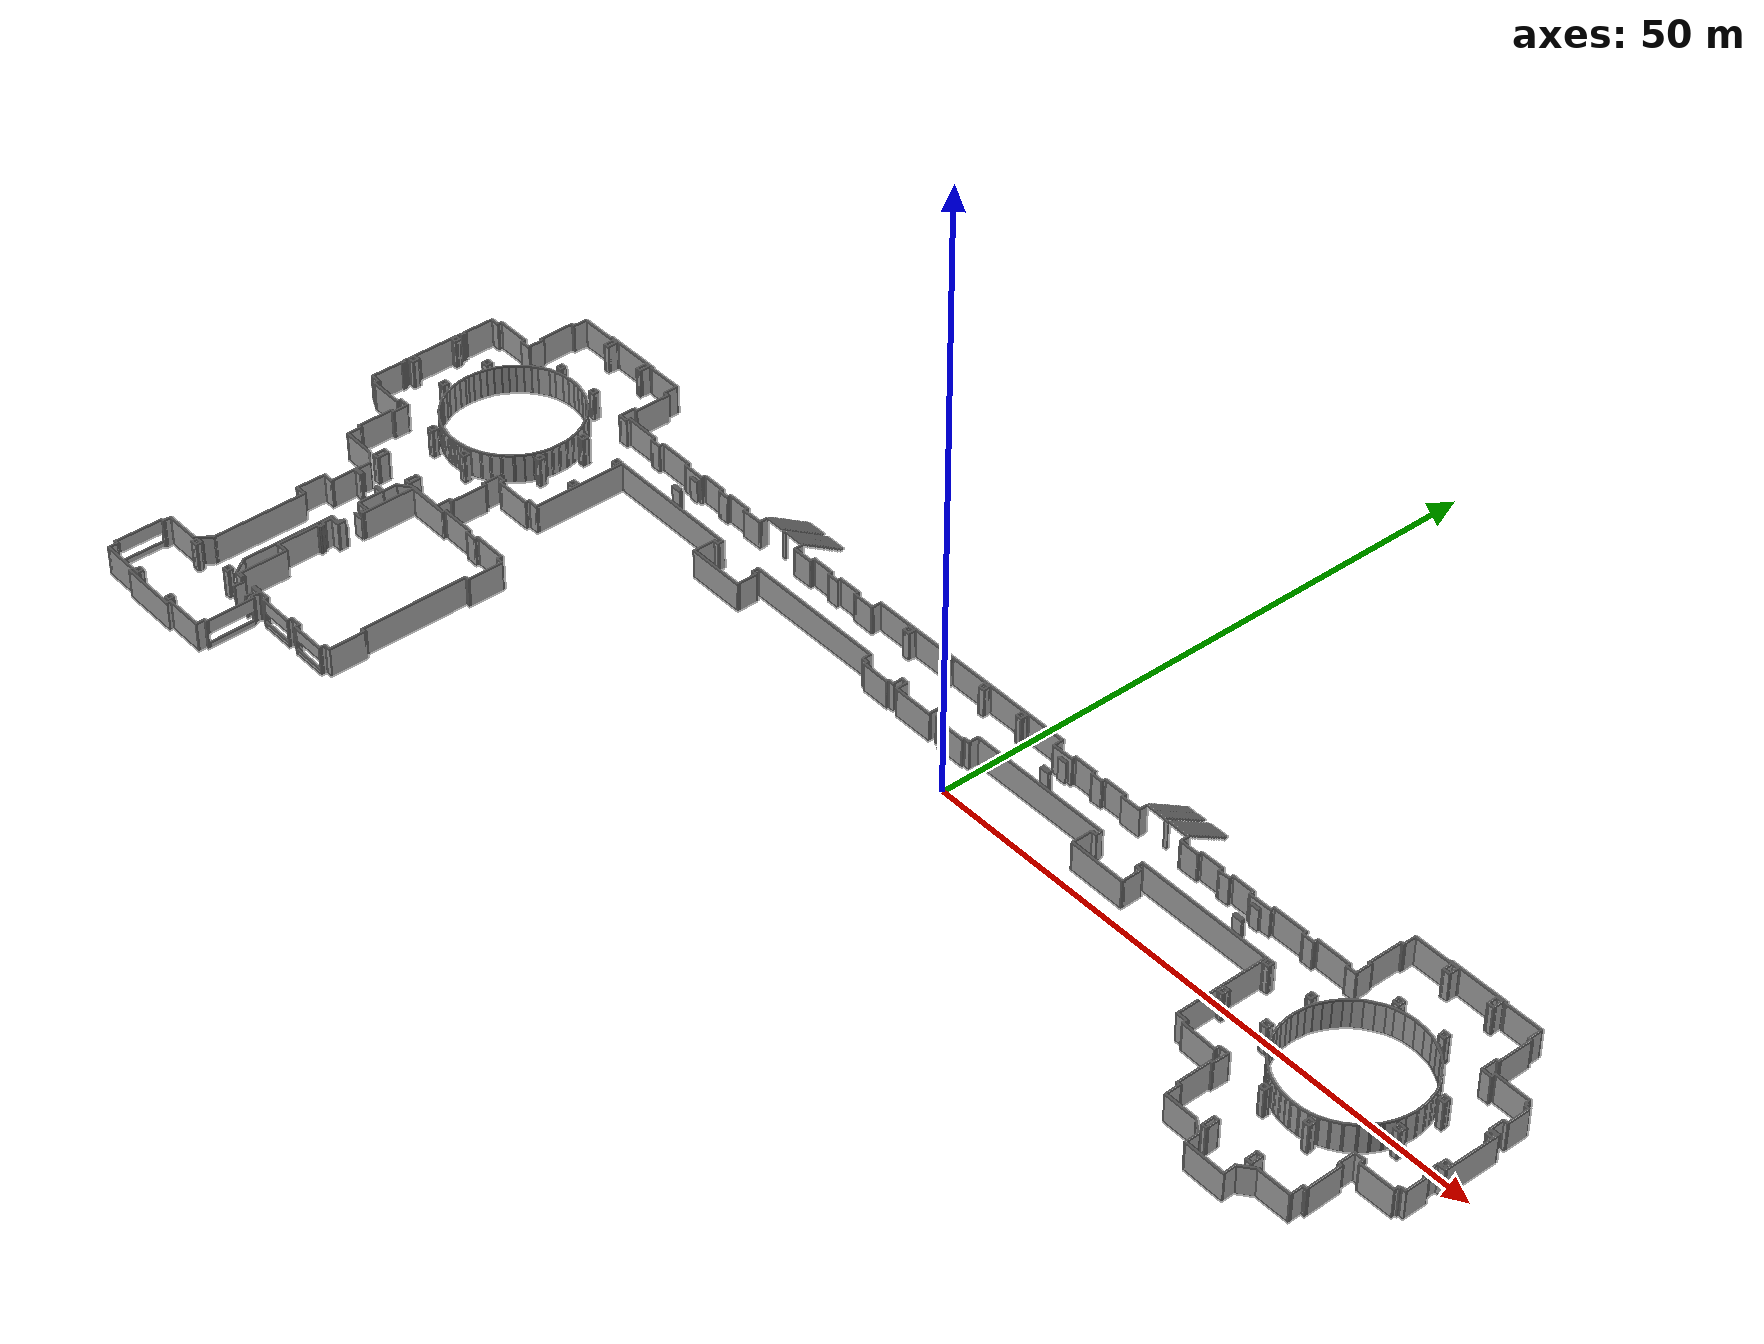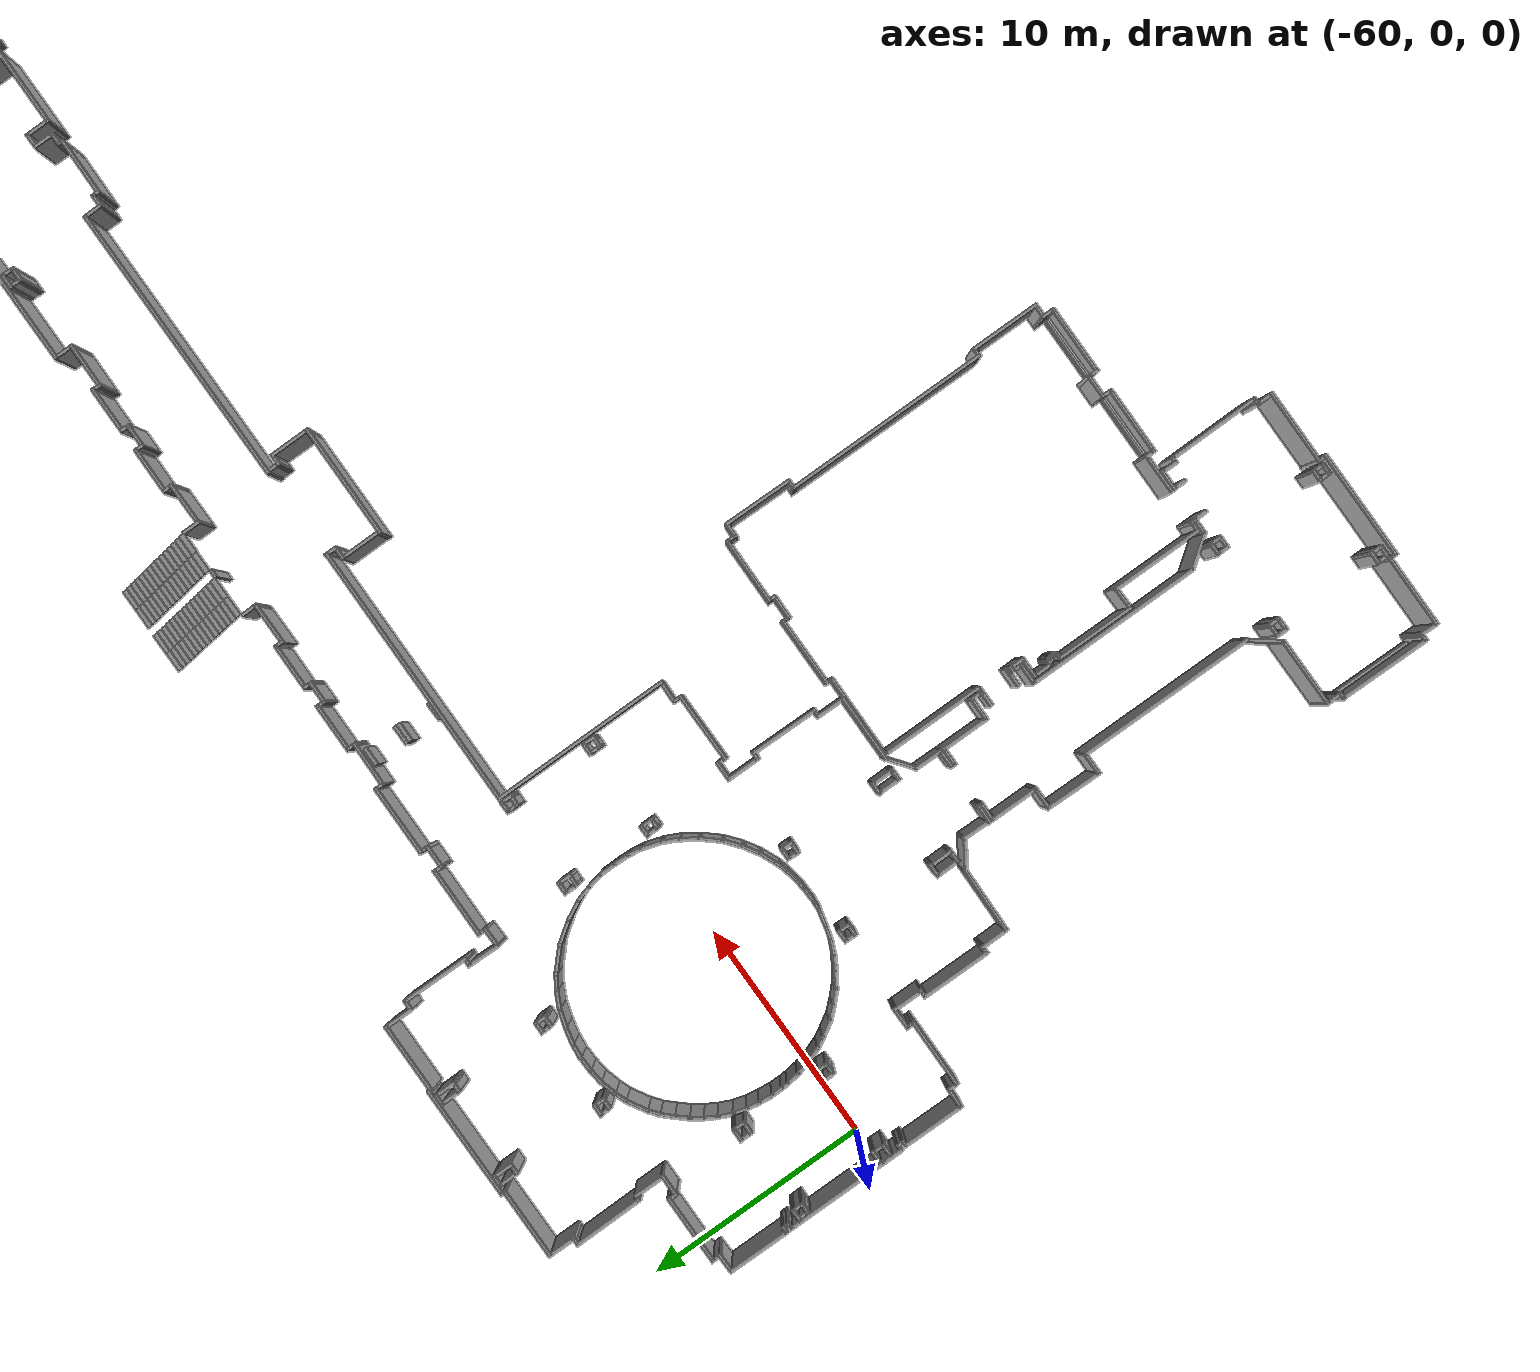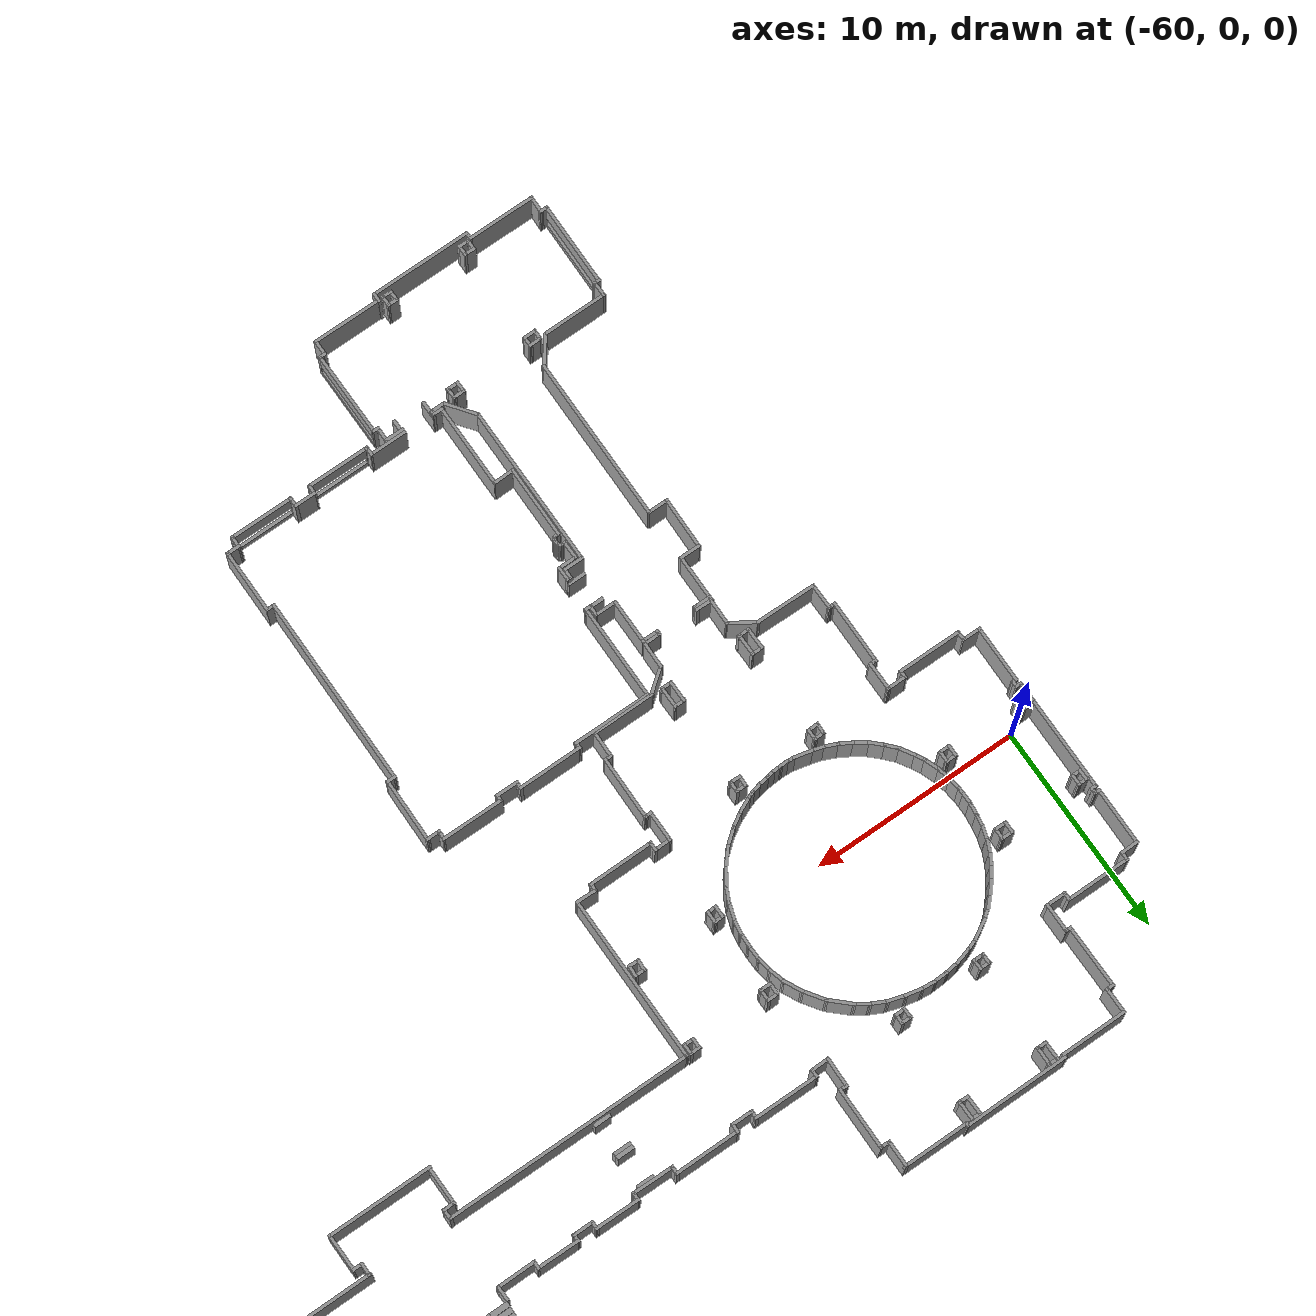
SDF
<?xml version='1.0'?>
<sdf version='1.7'>
  <model name='TD_n1_largo'>
    <pose>-6.3187 -9.13173 0 0 -0 0</pose>
    <link name='Door_0'>
      <collision name='Door_0_Collision'>
        <geometry>
          <box>
            <size>0.9 0.17 2</size>
          </box>
        </geometry>
        <pose>0 0 1 0 -0 0</pose>
      </collision>
      <visual name='Door_0_Visual'>
        <pose>0 0 1 0 -0 0</pose>
        <geometry>
          <box>
            <size>0.9 0.17 2</size>
          </box>
        </geometry>
        <material>
          <script>
            <uri>file://media/materials/scripts/gazebo.material</uri>
            <name>Gazebo/Grey</name>
          </script>
        </material>
      </visual>
      <pose>-42.1501 -5.33292 0 0 -0 0</pose>
    </link>
    <link name='Door_1'>
      <collision name='Door_1_Collision'>
        <geometry>
          <box>
            <size>0.9 0.17 2</size>
          </box>
        </geometry>
        <pose>0 0 1 0 -0 0</pose>
      </collision>
      <visual name='Door_1_Visual'>
        <pose>0 0 1 0 -0 0</pose>
        <geometry>
          <box>
            <size>0.9 0.17 2</size>
          </box>
        </geometry>
        <material>
          <script>
            <uri>file://media/materials/scripts/gazebo.material</uri>
            <name>Gazebo/Grey</name>
          </script>
        </material>
      </visual>
      <pose>-42.1501 -6.68053 0 0 -0 0</pose>
    </link>
    <link name='Door_10'>
      <collision name='Door_10_Collision'>
        <geometry>
          <box>
            <size>0.833875 0.2 2</size>
          </box>
        </geometry>
        <pose>0 0 1 0 -0 0</pose>
      </collision>
      <visual name='Door_10_Visual'>
        <pose>0 0 1 0 -0 0</pose>
        <geometry>
          <box>
            <size>0.833875 0.2 2</size>
          </box>
        </geometry>
        <material>
          <script>
            <uri>file://media/materials/scripts/gazebo.material</uri>
            <name>Gazebo/Grey</name>
          </script>
        </material>
      </visual>
      <pose>29.7761 16.0483 0 0 -0 0</pose>
    </link>
    <link name='Door_11'>
      <collision name='Door_11_Collision'>
        <geometry>
          <box>
            <size>0.807425 0.2 2</size>
          </box>
        </geometry>
        <pose>0 0 1 0 -0 0</pose>
      </collision>
      <visual name='Door_11_Visual'>
        <pose>0 0 1 0 -0 0</pose>
        <geometry>
          <box>
            <size>0.807425 0.2 2</size>
          </box>
        </geometry>
        <material>
          <script>
            <uri>file://media/materials/scripts/gazebo.material</uri>
            <name>Gazebo/Grey</name>
          </script>
        </material>
      </visual>
      <pose>29.7497 13.0269 0 0 0 -3.14159</pose>
    </link>
    <link name='Door_12'>
      <collision name='Door_12_Collision'>
        <geometry>
          <box>
            <size>0.814523 0.2 2</size>
          </box>
        </geometry>
        <pose>0 0 1 0 -0 0</pose>
      </collision>
      <visual name='Door_12_Visual'>
        <pose>0 0 1 0 -0 0</pose>
        <geometry>
          <box>
            <size>0.814523 0.2 2</size>
          </box>
        </geometry>
        <material>
          <script>
            <uri>file://media/materials/scripts/gazebo.material</uri>
            <name>Gazebo/Grey</name>
          </script>
        </material>
      </visual>
      <pose>10.7562 14.6384 0 0 -0 -3.1326</pose>
    </link>
    <link name='Door_13'>
      <collision name='Door_13_Collision'>
        <geometry>
          <box>
            <size>0.827673 0.2 2</size>
          </box>
        </geometry>
        <pose>0 0 1 0 -0 0</pose>
      </collision>
      <visual name='Door_13_Visual'>
        <pose>0 0 1 0 -0 0</pose>
        <geometry>
          <box>
            <size>0.827673 0.2 2</size>
          </box>
        </geometry>
        <material>
          <script>
            <uri>file://media/materials/scripts/gazebo.material</uri>
            <name>Gazebo/Grey</name>
          </script>
        </material>
      </visual>
      <pose>10.762 14.4567 0 0 -0 0</pose>
    </link>
    <link name='Door_14'>
      <collision name='Door_14_Collision'>
        <geometry>
          <box>
            <size>0.821098 0.2 2</size>
          </box>
        </geometry>
        <pose>0 0 1 0 -0 0</pose>
      </collision>
      <visual name='Door_14_Visual'>
        <pose>0 0 1 0 -0 0</pose>
        <geometry>
          <box>
            <size>0.821098 0.2 2</size>
          </box>
        </geometry>
        <material>
          <script>
            <uri>file://media/materials/scripts/gazebo.material</uri>
            <name>Gazebo/Grey</name>
          </script>
        </material>
      </visual>
      <pose>10.7555 16.0808 0 0 -0 0</pose>
    </link>
    <link name='Door_15'>
      <collision name='Door_15_Collision'>
        <geometry>
          <box>
            <size>0.83 0.2 2</size>
          </box>
        </geometry>
        <pose>0 0 1 0 -0 0</pose>
      </collision>
      <visual name='Door_15_Visual'>
        <pose>0 0 1 0 -0 0</pose>
        <geometry>
          <box>
            <size>0.83 0.2 2</size>
          </box>
        </geometry>
        <material>
          <script>
            <uri>file://media/materials/scripts/gazebo.material</uri>
            <name>Gazebo/Grey</name>
          </script>
        </material>
      </visual>
      <pose>10.7527 13.0109 0 0 -0 3.13494</pose>
    </link>
    <link name='Door_2'>
      <collision name='Door_2_Collision'>
        <geometry>
          <box>
            <size>0.9 0.17 2</size>
          </box>
        </geometry>
        <pose>0 0 1 0 -0 0</pose>
      </collision>
      <visual name='Door_2_Visual'>
        <pose>0 0 1 0 -0 0</pose>
        <geometry>
          <box>
            <size>0.9 0.17 2</size>
          </box>
        </geometry>
        <material>
          <script>
            <uri>file://media/materials/scripts/gazebo.material</uri>
            <name>Gazebo/Grey</name>
          </script>
        </material>
      </visual>
      <pose>-41.2094 -16.4238 0 0 -0 1.5717</pose>
    </link>
    <link name='Door_3'>
      <collision name='Door_3_Collision'>
        <geometry>
          <box>
            <size>0.9 0.17 2</size>
          </box>
        </geometry>
        <pose>0 0 1 0 -0 0</pose>
      </collision>
      <visual name='Door_3_Visual'>
        <pose>0 0 1 0 -0 0</pose>
        <geometry>
          <box>
            <size>0.9 0.17 2</size>
          </box>
        </geometry>
        <material>
          <script>
            <uri>file://media/materials/scripts/gazebo.material</uri>
            <name>Gazebo/Grey</name>
          </script>
        </material>
      </visual>
      <pose>-39.7197 -16.4588 0 0 -0 -1.57475</pose>
    </link>
    <link name='Door_4'>
      <collision name='Door_4_Collision'>
        <geometry>
          <box>
            <size>0.870169 0.2 2</size>
          </box>
        </geometry>
        <pose>0 0 1 0 -0 0</pose>
      </collision>
      <visual name='Door_4_Visual'>
        <pose>0 0 1 0 -0 0</pose>
        <geometry>
          <box>
            <size>0.870169 0.2 2</size>
          </box>
        </geometry>
        <material>
          <script>
            <uri>file://media/materials/scripts/gazebo.material</uri>
            <name>Gazebo/Grey</name>
          </script>
        </material>
      </visual>
      <pose>-29.8088 14.4548 0 0 -0 0</pose>
    </link>
    <link name='Door_5'>
      <collision name='Door_5_Collision'>
        <geometry>
          <box>
            <size>0.870169 0.2 2</size>
          </box>
        </geometry>
        <pose>0 0 1 0 -0 0</pose>
      </collision>
      <visual name='Door_5_Visual'>
        <pose>0 0 1 0 -0 0</pose>
        <geometry>
          <box>
            <size>0.870169 0.2 2</size>
          </box>
        </geometry>
        <material>
          <script>
            <uri>file://media/materials/scripts/gazebo.material</uri>
            <name>Gazebo/Grey</name>
          </script>
        </material>
      </visual>
      <pose>-29.8146 14.6172 0 0 0 -3.13804</pose>
    </link>
    <link name='Door_6'>
      <collision name='Door_6_Collision'>
        <geometry>
          <box>
            <size>0.844427 0.2 2</size>
          </box>
        </geometry>
        <pose>0 0 1 0 -0 0</pose>
      </collision>
      <visual name='Door_6_Visual'>
        <pose>0 0 1 0 -0 0</pose>
        <geometry>
          <box>
            <size>0.844427 0.2 2</size>
          </box>
        </geometry>
        <material>
          <script>
            <uri>file://media/materials/scripts/gazebo.material</uri>
            <name>Gazebo/Grey</name>
          </script>
        </material>
      </visual>
      <pose>-29.8142 16.1237 0 0 -0 0</pose>
    </link>
    <link name='Door_7'>
      <collision name='Door_7_Collision'>
        <geometry>
          <box>
            <size>0.837107 0.2 2</size>
          </box>
        </geometry>
        <pose>0 0 1 0 -0 0</pose>
      </collision>
      <visual name='Door_7_Visual'>
        <pose>0 0 1 0 -0 0</pose>
        <geometry>
          <box>
            <size>0.837107 0.2 2</size>
          </box>
        </geometry>
        <material>
          <script>
            <uri>file://media/materials/scripts/gazebo.material</uri>
            <name>Gazebo/Grey</name>
          </script>
        </material>
      </visual>
      <pose>-29.8009 12.9774 0 0 -0 -3.12725</pose>
    </link>
    <link name='Door_8'>
      <collision name='Door_8_Collision'>
        <geometry>
          <box>
            <size>0.864128 0.2 2</size>
          </box>
        </geometry>
        <pose>0 0 1 0 -0 0</pose>
      </collision>
      <visual name='Door_8_Visual'>
        <pose>0 0 1 0 -0 0</pose>
        <geometry>
          <box>
            <size>0.864128 0.2 2</size>
          </box>
        </geometry>
        <material>
          <script>
            <uri>file://media/materials/scripts/gazebo.material</uri>
            <name>Gazebo/Grey</name>
          </script>
        </material>
      </visual>
      <pose>29.7933 14.4349 0 0 -0 0</pose>
    </link>
    <link name='Door_9'>
      <collision name='Door_9_Collision'>
        <geometry>
          <box>
            <size>0.851141 0.2 2</size>
          </box>
        </geometry>
        <pose>0 0 1 0 -0 0</pose>
      </collision>
      <visual name='Door_9_Visual'>
        <pose>0 0 1 0 -0 0</pose>
        <geometry>
          <box>
            <size>0.851141 0.2 2</size>
          </box>
        </geometry>
        <material>
          <script>
            <uri>file://media/materials/scripts/gazebo.material</uri>
            <name>Gazebo/Grey</name>
          </script>
        </material>
      </visual>
      <pose>29.7912 14.6154 0 0 -0 3.13243</pose>
    </link>
    <link name='Stairs_1'>
      <visual name='Stairs_1_Visual_0'>
        <pose>-21.8201 20.6908 0.083333 0 -0 0</pose>
        <geometry>
          <box>
            <size>0.9 0.258 0.166667</size>
          </box>
        </geometry>
        <material>
          <script>
            <uri>file://media/materials/scripts/gazebo.material</uri>
            <name>Gazebo/Grey</name>
          </script>
          <ambient>1 1 1 1</ambient>
        </material>
        <meta>
          <layer>0</layer>
        </meta>
      </visual>
      <collision name='Stairs_1_Collision_0'>
        <geometry>
          <box>
            <size>0.9 0.258 0.166667</size>
          </box>
        </geometry>
        <pose>-21.8201 20.6908 0.083333 0 -0 0</pose>
      </collision>
      <visual name='Stairs_1_Visual_1'>
        <pose>-21.8201 20.4328 0.25 0 -0 0</pose>
        <geometry>
          <box>
            <size>0.9 0.258 0.166667</size>
          </box>
        </geometry>
        <material>
          <script>
            <uri>file://media/materials/scripts/gazebo.material</uri>
            <name>Gazebo/Grey</name>
          </script>
          <ambient>1 1 1 1</ambient>
        </material>
        <meta>
          <layer>0</layer>
        </meta>
      </visual>
      <collision name='Stairs_1_Collision_1'>
        <geometry>
          <box>
            <size>0.9 0.258 0.166667</size>
          </box>
        </geometry>
        <pose>-21.8201 20.4328 0.25 0 -0 0</pose>
      </collision>
      <visual name='Stairs_1_Visual_2'>
        <pose>-21.8201 20.1748 0.416667 0 -0 0</pose>
        <geometry>
          <box>
            <size>0.9 0.258 0.166667</size>
          </box>
        </geometry>
        <material>
          <script>
            <uri>file://media/materials/scripts/gazebo.material</uri>
            <name>Gazebo/Grey</name>
          </script>
          <ambient>1 1 1 1</ambient>
        </material>
        <meta>
          <layer>0</layer>
        </meta>
      </visual>
      <collision name='Stairs_1_Collision_2'>
        <geometry>
          <box>
            <size>0.9 0.258 0.166667</size>
          </box>
        </geometry>
        <pose>-21.8201 20.1748 0.416667 0 -0 0</pose>
      </collision>
      <visual name='Stairs_1_Visual_3'>
        <pose>-21.8201 19.9168 0.583333 0 -0 0</pose>
        <geometry>
          <box>
            <size>0.9 0.258 0.166667</size>
          </box>
        </geometry>
        <material>
          <script>
            <uri>file://media/materials/scripts/gazebo.material</uri>
            <name>Gazebo/Grey</name>
          </script>
          <ambient>1 1 1 1</ambient>
        </material>
        <meta>
          <layer>0</layer>
        </meta>
      </visual>
      <collision name='Stairs_1_Collision_3'>
        <geometry>
          <box>
            <size>0.9 0.258 0.166667</size>
          </box>
        </geometry>
        <pose>-21.8201 19.9168 0.583333 0 -0 0</pose>
      </collision>
      <visual name='Stairs_1_Visual_4'>
        <pose>-21.8201 19.6588 0.75 0 -0 0</pose>
        <geometry>
          <box>
            <size>0.9 0.258 0.166667</size>
          </box>
        </geometry>
        <material>
          <script>
            <uri>file://media/materials/scripts/gazebo.material</uri>
            <name>Gazebo/Grey</name>
          </script>
          <ambient>1 1 1 1</ambient>
        </material>
        <meta>
          <layer>0</layer>
        </meta>
      </visual>
      <collision name='Stairs_1_Collision_4'>
        <geometry>
          <box>
            <size>0.9 0.258 0.166667</size>
          </box>
        </geometry>
        <pose>-21.8201 19.6588 0.75 0 -0 0</pose>
      </collision>
      <visual name='Stairs_1_Visual_5'>
        <pose>-21.8201 19.4008 0.916667 0 -0 0</pose>
        <geometry>
          <box>
            <size>0.9 0.258 0.166667</size>
          </box>
        </geometry>
        <material>
          <script>
            <uri>file://media/materials/scripts/gazebo.material</uri>
            <name>Gazebo/Grey</name>
          </script>
          <ambient>1 1 1 1</ambient>
        </material>
        <meta>
          <layer>0</layer>
        </meta>
      </visual>
      <collision name='Stairs_1_Collision_5'>
        <geometry>
          <box>
            <size>0.9 0.258 0.166667</size>
          </box>
        </geometry>
        <pose>-21.8201 19.4008 0.916667 0 -0 0</pose>
      </collision>
      <visual name='Stairs_1_Visual_6'>
        <pose>-21.8201 19.1428 1.08333 0 -0 0</pose>
        <geometry>
          <box>
            <size>0.9 0.258 0.166667</size>
          </box>
        </geometry>
        <material>
          <script>
            <uri>file://media/materials/scripts/gazebo.material</uri>
            <name>Gazebo/Grey</name>
          </script>
          <ambient>1 1 1 1</ambient>
        </material>
        <meta>
          <layer>0</layer>
        </meta>
      </visual>
      <collision name='Stairs_1_Collision_6'>
        <geometry>
          <box>
            <size>0.9 0.258 0.166667</size>
          </box>
        </geometry>
        <pose>-21.8201 19.1428 1.08333 0 -0 0</pose>
      </collision>
      <visual name='Stairs_1_Visual_7'>
        <pose>-21.8201 18.8848 1.25 0 -0 0</pose>
        <geometry>
          <box>
            <size>0.9 0.258 0.166667</size>
          </box>
        </geometry>
        <material>
          <script>
            <uri>file://media/materials/scripts/gazebo.material</uri>
            <name>Gazebo/Grey</name>
          </script>
          <ambient>1 1 1 1</ambient>
        </material>
        <meta>
          <layer>0</layer>
        </meta>
      </visual>
      <collision name='Stairs_1_Collision_7'>
        <geometry>
          <box>
            <size>0.9 0.258 0.166667</size>
          </box>
        </geometry>
        <pose>-21.8201 18.8848 1.25 0 -0 0</pose>
      </collision>
      <visual name='Stairs_1_Visual_8'>
        <pose>-21.8201 18.6268 1.41667 0 -0 0</pose>
        <geometry>
          <box>
            <size>0.9 0.258 0.166667</size>
          </box>
        </geometry>
        <material>
          <script>
            <uri>file://media/materials/scripts/gazebo.material</uri>
            <name>Gazebo/Grey</name>
          </script>
          <ambient>1 1 1 1</ambient>
        </material>
        <meta>
          <layer>0</layer>
        </meta>
      </visual>
      <collision name='Stairs_1_Collision_8'>
        <geometry>
          <box>
            <size>0.9 0.258 0.166667</size>
          </box>
        </geometry>
        <pose>-21.8201 18.6268 1.41667 0 -0 0</pose>
      </collision>
      <visual name='Stairs_1_Visual_9'>
        <pose>-21.8201 18.3688 1.58333 0 -0 0</pose>
        <geometry>
          <box>
            <size>0.9 0.258 0.166667</size>
          </box>
        </geometry>
        <material>
          <script>
            <uri>file://media/materials/scripts/gazebo.material</uri>
            <name>Gazebo/Grey</name>
          </script>
          <ambient>1 1 1 1</ambient>
        </material>
        <meta>
          <layer>0</layer>
        </meta>
      </visual>
      <collision name='Stairs_1_Collision_9'>
        <geometry>
          <box>
            <size>0.9 0.258 0.166667</size>
          </box>
        </geometry>
        <pose>-21.8201 18.3688 1.58333 0 -0 0</pose>
      </collision>
      <visual name='Stairs_1_Visual_10'>
        <pose>-21.8201 18.1108 1.75 0 -0 0</pose>
        <geometry>
          <box>
            <size>0.9 0.258 0.166667</size>
          </box>
        </geometry>
        <material>
          <script>
            <uri>file://media/materials/scripts/gazebo.material</uri>
            <name>Gazebo/Grey</name>
          </script>
          <ambient>1 1 1 1</ambient>
        </material>
        <meta>
          <layer>0</layer>
        </meta>
      </visual>
      <collision name='Stairs_1_Collision_10'>
        <geometry>
          <box>
            <size>0.9 0.258 0.166667</size>
          </box>
        </geometry>
        <pose>-21.8201 18.1108 1.75 0 -0 0</pose>
      </collision>
      <visual name='Stairs_1_Visual_11'>
        <pose>-21.8201 17.8528 1.91667 0 -0 0</pose>
        <geometry>
          <box>
            <size>0.9 0.258 0.166667</size>
          </box>
        </geometry>
        <material>
          <script>
            <uri>file://media/materials/scripts/gazebo.material</uri>
            <name>Gazebo/Grey</name>
          </script>
          <ambient>1 1 1 1</ambient>
        </material>
        <meta>
          <layer>0</layer>
        </meta>
      </visual>
      <collision name='Stairs_1_Collision_11'>
        <geometry>
          <box>
            <size>0.9 0.258 0.166667</size>
          </box>
        </geometry>
        <pose>-21.8201 17.8528 1.91667 0 -0 0</pose>
      </collision>
      <visual name='Stairs_1_Visual_12'>
        <pose>-21.8201 17.5948 2.08333 0 -0 0</pose>
        <geometry>
          <box>
            <size>0.9 0.258 0.166667</size>
          </box>
        </geometry>
        <material>
          <script>
            <uri>file://media/materials/scripts/gazebo.material</uri>
            <name>Gazebo/Grey</name>
          </script>
          <ambient>1 1 1 1</ambient>
        </material>
        <meta>
          <layer>0</layer>
        </meta>
      </visual>
      <collision name='Stairs_1_Collision_12'>
        <geometry>
          <box>
            <size>0.9 0.258 0.166667</size>
          </box>
        </geometry>
        <pose>-21.8201 17.5948 2.08333 0 -0 0</pose>
      </collision>
      <visual name='Stairs_1_Visual_13'>
        <pose>-21.8201 17.3368 2.25 0 -0 0</pose>
        <geometry>
          <box>
            <size>0.9 0.258 0.166667</size>
          </box>
        </geometry>
        <material>
          <script>
            <uri>file://media/materials/scripts/gazebo.material</uri>
            <name>Gazebo/Grey</name>
          </script>
          <ambient>1 1 1 1</ambient>
        </material>
        <meta>
          <layer>0</layer>
        </meta>
      </visual>
      <collision name='Stairs_1_Collision_13'>
        <geometry>
          <box>
            <size>0.9 0.258 0.166667</size>
          </box>
        </geometry>
        <pose>-21.8201 17.3368 2.25 0 -0 0</pose>
      </collision>
      <visual name='Stairs_1_Visual_14'>
        <pose>-21.8201 17.0788 2.41667 0 -0 0</pose>
        <geometry>
          <box>
            <size>0.9 0.258 0.166667</size>
          </box>
        </geometry>
        <material>
          <script>
            <uri>file://media/materials/scripts/gazebo.material</uri>
            <name>Gazebo/Grey</name>
          </script>
          <ambient>1 1 1 1</ambient>
        </material>
        <meta>
          <layer>0</layer>
        </meta>
      </visual>
      <collision name='Stairs_1_Collision_14'>
        <geometry>
          <box>
            <size>0.9 0.258 0.166667</size>
          </box>
        </geometry>
        <pose>-21.8201 17.0788 2.41667 0 -0 0</pose>
      </collision>
    </link>
    <link name='Stairs_2'>
      <visual name='Stairs_2_Visual_0'>
        <pose>-20.9263 20.6987 0.083333 0 -0 0</pose>
        <geometry>
          <box>
            <size>0.91 0.258667 0.166667</size>
          </box>
        </geometry>
        <material>
          <script>
            <uri>file://media/materials/scripts/gazebo.material</uri>
            <name>Gazebo/Grey</name>
          </script>
          <ambient>1 1 1 1</ambient>
        </material>
        <meta>
          <layer>0</layer>
        </meta>
      </visual>
      <collision name='Stairs_2_Collision_0'>
        <geometry>
          <box>
            <size>0.91 0.258667 0.166667</size>
          </box>
        </geometry>
        <pose>-20.9263 20.6987 0.083333 0 -0 0</pose>
      </collision>
      <visual name='Stairs_2_Visual_1'>
        <pose>-20.9263 20.4401 0.25 0 -0 0</pose>
        <geometry>
          <box>
            <size>0.91 0.258667 0.166667</size>
          </box>
        </geometry>
        <material>
          <script>
            <uri>file://media/materials/scripts/gazebo.material</uri>
            <name>Gazebo/Grey</name>
          </script>
          <ambient>1 1 1 1</ambient>
        </material>
        <meta>
          <layer>0</layer>
        </meta>
      </visual>
      <collision name='Stairs_2_Collision_1'>
        <geometry>
          <box>
            <size>0.91 0.258667 0.166667</size>
          </box>
        </geometry>
        <pose>-20.9263 20.4401 0.25 0 -0 0</pose>
      </collision>
      <visual name='Stairs_2_Visual_2'>
        <pose>-20.9263 20.1814 0.416667 0 -0 0</pose>
        <geometry>
          <box>
            <size>0.91 0.258667 0.166667</size>
          </box>
        </geometry>
        <material>
          <script>
            <uri>file://media/materials/scripts/gazebo.material</uri>
            <name>Gazebo/Grey</name>
          </script>
          <ambient>1 1 1 1</ambient>
        </material>
        <meta>
          <layer>0</layer>
        </meta>
      </visual>
      <collision name='Stairs_2_Collision_2'>
        <geometry>
          <box>
            <size>0.91 0.258667 0.166667</size>
          </box>
        </geometry>
        <pose>-20.9263 20.1814 0.416667 0 -0 0</pose>
      </collision>
      <visual name='Stairs_2_Visual_3'>
        <pose>-20.9263 19.9227 0.583333 0 -0 0</pose>
        <geometry>
          <box>
            <size>0.91 0.258667 0.166667</size>
          </box>
        </geometry>
        <material>
          <script>
            <uri>file://media/materials/scripts/gazebo.material</uri>
            <name>Gazebo/Grey</name>
          </script>
          <ambient>1 1 1 1</ambient>
        </material>
        <meta>
          <layer>0</layer>
        </meta>
      </visual>
      <collision name='Stairs_2_Collision_3'>
        <geometry>
          <box>
            <size>0.91 0.258667 0.166667</size>
          </box>
        </geometry>
        <pose>-20.9263 19.9227 0.583333 0 -0 0</pose>
      </collision>
      <visual name='Stairs_2_Visual_4'>
        <pose>-20.9263 19.6641 0.75 0 -0 0</pose>
        <geometry>
          <box>
            <size>0.91 0.258667 0.166667</size>
          </box>
        </geometry>
        <material>
          <script>
            <uri>file://media/materials/scripts/gazebo.material</uri>
            <name>Gazebo/Grey</name>
          </script>
          <ambient>1 1 1 1</ambient>
        </material>
        <meta>
          <layer>0</layer>
        </meta>
      </visual>
      <collision name='Stairs_2_Collision_4'>
        <geometry>
          <box>
            <size>0.91 0.258667 0.166667</size>
          </box>
        </geometry>
        <pose>-20.9263 19.6641 0.75 0 -0 0</pose>
      </collision>
      <visual name='Stairs_2_Visual_5'>
        <pose>-20.9263 19.4054 0.916667 0 -0 0</pose>
        <geometry>
          <box>
            <size>0.91 0.258667 0.166667</size>
          </box>
        </geometry>
        <material>
          <script>
            <uri>file://media/materials/scripts/gazebo.material</uri>
            <name>Gazebo/Grey</name>
          </script>
          <ambient>1 1 1 1</ambient>
        </material>
        <meta>
          <layer>0</layer>
        </meta>
      </visual>
      <collision name='Stairs_2_Collision_5'>
        <geometry>
          <box>
            <size>0.91 0.258667 0.166667</size>
          </box>
        </geometry>
        <pose>-20.9263 19.4054 0.916667 0 -0 0</pose>
      </collision>
      <visual name='Stairs_2_Visual_6'>
        <pose>-20.9263 19.1467 1.08333 0 -0 0</pose>
        <geometry>
          <box>
            <size>0.91 0.258667 0.166667</size>
          </box>
        </geometry>
        <material>
          <script>
            <uri>file://media/materials/scripts/gazebo.material</uri>
            <name>Gazebo/Grey</name>
          </script>
          <ambient>1 1 1 1</ambient>
        </material>
        <meta>
          <layer>0</layer>
        </meta>
      </visual>
      <collision name='Stairs_2_Collision_6'>
        <geometry>
          <box>
            <size>0.91 0.258667 0.166667</size>
          </box>
        </geometry>
        <pose>-20.9263 19.1467 1.08333 0 -0 0</pose>
      </collision>
      <visual name='Stairs_2_Visual_7'>
        <pose>-20.9263 18.8881 1.25 0 -0 0</pose>
        <geometry>
          <box>
            <size>0.91 0.258667 0.166667</size>
          </box>
        </geometry>
        <material>
          <script>
            <uri>file://media/materials/scripts/gazebo.material</uri>
            <name>Gazebo/Grey</name>
          </script>
          <ambient>1 1 1 1</ambient>
        </material>
        <meta>
          <layer>0</layer>
        </meta>
      </visual>
      <collision name='Stairs_2_Collision_7'>
        <geometry>
          <box>
            <size>0.91 0.258667 0.166667</size>
          </box>
        </geometry>
        <pose>-20.9263 18.8881 1.25 0 -0 0</pose>
      </collision>
      <visual name='Stairs_2_Visual_8'>
        <pose>-20.9263 18.6294 1.41667 0 -0 0</pose>
        <geometry>
          <box>
            <size>0.91 0.258667 0.166667</size>
          </box>
        </geometry>
        <material>
          <script>
            <uri>file://media/materials/scripts/gazebo.material</uri>
            <name>Gazebo/Grey</name>
          </script>
          <ambient>1 1 1 1</ambient>
        </material>
        <meta>
          <layer>0</layer>
        </meta>
      </visual>
      <collision name='Stairs_2_Collision_8'>
        <geometry>
          <box>
            <size>0.91 0.258667 0.166667</size>
          </box>
        </geometry>
        <pose>-20.9263 18.6294 1.41667 0 -0 0</pose>
      </collision>
      <visual name='Stairs_2_Visual_9'>
        <pose>-20.9263 18.3707 1.58333 0 -0 0</pose>
        <geometry>
          <box>
            <size>0.91 0.258667 0.166667</size>
          </box>
        </geometry>
        <material>
          <script>
            <uri>file://media/materials/scripts/gazebo.material</uri>
            <name>Gazebo/Grey</name>
          </script>
          <ambient>1 1 1 1</ambient>
        </material>
        <meta>
          <layer>0</layer>
        </meta>
      </visual>
      <collision name='Stairs_2_Collision_9'>
        <geometry>
          <box>
            <size>0.91 0.258667 0.166667</size>
          </box>
        </geometry>
        <pose>-20.9263 18.3707 1.58333 0 -0 0</pose>
      </collision>
      <visual name='Stairs_2_Visual_10'>
        <pose>-20.9263 18.1121 1.75 0 -0 0</pose>
        <geometry>
          <box>
            <size>0.91 0.258667 0.166667</size>
          </box>
        </geometry>
        <material>
          <script>
            <uri>file://media/materials/scripts/gazebo.material</uri>
            <name>Gazebo/Grey</name>
          </script>
          <ambient>1 1 1 1</ambient>
        </material>
        <meta>
          <layer>0</layer>
        </meta>
      </visual>
      <collision name='Stairs_2_Collision_10'>
        <geometry>
          <box>
            <size>0.91 0.258667 0.166667</size>
          </box>
        </geometry>
        <pose>-20.9263 18.1121 1.75 0 -0 0</pose>
      </collision>
      <visual name='Stairs_2_Visual_11'>
        <pose>-20.9263 17.8534 1.91667 0 -0 0</pose>
        <geometry>
          <box>
            <size>0.91 0.258667 0.166667</size>
          </box>
        </geometry>
        <material>
          <script>
            <uri>file://media/materials/scripts/gazebo.material</uri>
            <name>Gazebo/Grey</name>
          </script>
          <ambient>1 1 1 1</ambient>
        </material>
        <meta>
          <layer>0</layer>
        </meta>
      </visual>
      <collision name='Stairs_2_Collision_11'>
        <geometry>
          <box>
            <size>0.91 0.258667 0.166667</size>
          </box>
        </geometry>
        <pose>-20.9263 17.8534 1.91667 0 -0 0</pose>
      </collision>
      <visual name='Stairs_2_Visual_12'>
        <pose>-20.9263 17.5947 2.08333 0 -0 0</pose>
        <geometry>
          <box>
            <size>0.91 0.258667 0.166667</size>
          </box>
        </geometry>
        <material>
          <script>
            <uri>file://media/materials/scripts/gazebo.material</uri>
            <name>Gazebo/Grey</name>
          </script>
          <ambient>1 1 1 1</ambient>
        </material>
        <meta>
          <layer>0</layer>
        </meta>
      </visual>
      <collision name='Stairs_2_Collision_12'>
        <geometry>
          <box>
            <size>0.91 0.258667 0.166667</size>
          </box>
        </geometry>
        <pose>-20.9263 17.5947 2.08333 0 -0 0</pose>
      </collision>
      <visual name='Stairs_2_Visual_13'>
        <pose>-20.9263 17.3361 2.25 0 -0 0</pose>
        <geometry>
          <box>
            <size>0.91 0.258667 0.166667</size>
          </box>
        </geometry>
        <material>
          <script>
            <uri>file://media/materials/scripts/gazebo.material</uri>
            <name>Gazebo/Grey</name>
          </script>
          <ambient>1 1 1 1</ambient>
        </material>
        <meta>
          <layer>0</layer>
        </meta>
      </visual>
      <collision name='Stairs_2_Collision_13'>
        <geometry>
          <box>
            <size>0.91 0.258667 0.166667</size>
          </box>
        </geometry>
        <pose>-20.9263 17.3361 2.25 0 -0 0</pose>
      </collision>
      <visual name='Stairs_2_Visual_14'>
        <pose>-20.9263 17.0774 2.41667 0 -0 0</pose>
        <geometry>
          <box>
            <size>0.91 0.258667 0.166667</size>
          </box>
        </geometry>
        <material>
          <script>
            <uri>file://media/materials/scripts/gazebo.material</uri>
            <name>Gazebo/Grey</name>
          </script>
          <ambient>1 1 1 1</ambient>
        </material>
        <meta>
          <layer>0</layer>
        </meta>
      </visual>
      <collision name='Stairs_2_Collision_14'>
        <geometry>
          <box>
            <size>0.91 0.258667 0.166667</size>
          </box>
        </geometry>
        <pose>-20.9263 17.0774 2.41667 0 -0 0</pose>
      </collision>
    </link>
    <link name='Stairs_3'>
      <visual name='Stairs_3_Visual_0'>
        <pose>-19.6563 20.6794 0.083333 0 -0 0</pose>
        <geometry>
          <box>
            <size>0.91 0.257333 0.166667</size>
          </box>
        </geometry>
        <material>
          <script>
            <uri>file://media/materials/scripts/gazebo.material</uri>
            <name>Gazebo/Grey</name>
          </script>
          <ambient>1 1 1 1</ambient>
        </material>
        <meta>
          <layer>0</layer>
        </meta>
      </visual>
      <collision name='Stairs_3_Collision_0'>
        <geometry>
          <box>
            <size>0.91 0.257333 0.166667</size>
          </box>
        </geometry>
        <pose>-19.6563 20.6794 0.083333 0 -0 0</pose>
      </collision>
      <visual name='Stairs_3_Visual_1'>
        <pose>-19.6563 20.4221 0.25 0 -0 0</pose>
        <geometry>
          <box>
            <size>0.91 0.257333 0.166667</size>
          </box>
        </geometry>
        <material>
          <script>
            <uri>file://media/materials/scripts/gazebo.material</uri>
            <name>Gazebo/Grey</name>
          </script>
          <ambient>1 1 1 1</ambient>
        </material>
        <meta>
          <layer>0</layer>
        </meta>
      </visual>
      <collision name='Stairs_3_Collision_1'>
        <geometry>
          <box>
            <size>0.91 0.257333 0.166667</size>
          </box>
        </geometry>
        <pose>-19.6563 20.4221 0.25 0 -0 0</pose>
      </collision>
      <visual name='Stairs_3_Visual_2'>
        <pose>-19.6563 20.1647 0.416667 0 -0 0</pose>
        <geometry>
          <box>
            <size>0.91 0.257333 0.166667</size>
          </box>
        </geometry>
        <material>
          <script>
            <uri>file://media/materials/scripts/gazebo.material</uri>
            <name>Gazebo/Grey</name>
          </script>
          <ambient>1 1 1 1</ambient>
        </material>
        <meta>
          <layer>0</layer>
        </meta>
      </visual>
      <collision name='Stairs_3_Collision_2'>
        <geometry>
          <box>
            <size>0.91 0.257333 0.166667</size>
          </box>
        </geometry>
        <pose>-19.6563 20.1647 0.416667 0 -0 0</pose>
      </collision>
      <visual name='Stairs_3_Visual_3'>
        <pose>-19.6563 19.9074 0.583333 0 -0 0</pose>
        <geometry>
          <box>
            <size>0.91 0.257333 0.166667</size>
          </box>
        </geometry>
        <material>
          <script>
            <uri>file://media/materials/scripts/gazebo.material</uri>
            <name>Gazebo/Grey</name>
          </script>
          <ambient>1 1 1 1</ambient>
        </material>
        <meta>
          <layer>0</layer>
        </meta>
      </visual>
      <collision name='Stairs_3_Collision_3'>
        <geometry>
          <box>
            <size>0.91 0.257333 0.166667</size>
          </box>
        </geometry>
        <pose>-19.6563 19.9074 0.583333 0 -0 0</pose>
      </collision>
      <visual name='Stairs_3_Visual_4'>
        <pose>-19.6563 19.6501 0.75 0 -0 0</pose>
        <geometry>
          <box>
            <size>0.91 0.257333 0.166667</size>
          </box>
        </geometry>
        <material>
          <script>
            <uri>file://media/materials/scripts/gazebo.material</uri>
            <name>Gazebo/Grey</name>
          </script>
          <ambient>1 1 1 1</ambient>
        </material>
        <meta>
          <layer>0</layer>
        </meta>
      </visual>
      <collision name='Stairs_3_Collision_4'>
        <geometry>
          <box>
            <size>0.91 0.257333 0.166667</size>
          </box>
        </geometry>
        <pose>-19.6563 19.6501 0.75 0 -0 0</pose>
      </collision>
      <visual name='Stairs_3_Visual_5'>
        <pose>-19.6563 19.3927 0.916667 0 -0 0</pose>
        <geometry>
          <box>
            <size>0.91 0.257333 0.166667</size>
          </box>
        </geometry>
        <material>
          <script>
            <uri>file://media/materials/scripts/gazebo.material</uri>
            <name>Gazebo/Grey</name>
          </script>
          <ambient>1 1 1 1</ambient>
        </material>
        <meta>
          <layer>0</layer>
        </meta>
      </visual>
      <collision name='Stairs_3_Collision_5'>
        <geometry>
          <box>
            <size>0.91 0.257333 0.166667</size>
          </box>
        </geometry>
        <pose>-19.6563 19.3927 0.916667 0 -0 0</pose>
      </collision>
      <visual name='Stairs_3_Visual_6'>
        <pose>-19.6563 19.1354 1.08333 0 -0 0</pose>
        <geometry>
          <box>
            <size>0.91 0.257333 0.166667</size>
          </box>
        </geometry>
        <material>
          <script>
            <uri>file://media/materials/scripts/gazebo.material</uri>
            <name>Gazebo/Grey</name>
          </script>
          <ambient>1 1 1 1</ambient>
        </material>
        <meta>
          <layer>0</layer>
        </meta>
      </visual>
      <collision name='Stairs_3_Collision_6'>
        <geometry>
          <box>
            <size>0.91 0.257333 0.166667</size>
          </box>
        </geometry>
        <pose>-19.6563 19.1354 1.08333 0 -0 0</pose>
      </collision>
      <visual name='Stairs_3_Visual_7'>
        <pose>-19.6563 18.8781 1.25 0 -0 0</pose>
        <geometry>
          <box>
            <size>0.91 0.257333 0.166667</size>
          </box>
        </geometry>
        <material>
          <script>
            <uri>file://media/materials/scripts/gazebo.material</uri>
            <name>Gazebo/Grey</name>
          </script>
          <ambient>1 1 1 1</ambient>
        </material>
        <meta>
          <layer>0</layer>
        </meta>
      </visual>
      <collision name='Stairs_3_Collision_7'>
        <geometry>
          <box>
            <size>0.91 0.257333 0.166667</size>
          </box>
        </geometry>
        <pose>-19.6563 18.8781 1.25 0 -0 0</pose>
      </collision>
      <visual name='Stairs_3_Visual_8'>
        <pose>-19.6563 18.6207 1.41667 0 -0 0</pose>
        <geometry>
          <box>
            <size>0.91 0.257333 0.166667</size>
          </box>
        </geometry>
        <material>
          <script>
            <uri>file://media/materials/scripts/gazebo.material</uri>
            <name>Gazebo/Grey</name>
          </script>
          <ambient>1 1 1 1</ambient>
        </material>
        <meta>
          <layer>0</layer>
        </meta>
      </visual>
      <collision name='Stairs_3_Collision_8'>
        <geometry>
          <box>
            <size>0.91 0.257333 0.166667</size>
          </box>
        </geometry>
        <pose>-19.6563 18.6207 1.41667 0 -0 0</pose>
      </collision>
      <visual name='Stairs_3_Visual_9'>
        <pose>-19.6563 18.3634 1.58333 0 -0 0</pose>
        <geometry>
          <box>
            <size>0.91 0.257333 0.166667</size>
          </box>
        </geometry>
        <material>
          <script>
            <uri>file://media/materials/scripts/gazebo.material</uri>
            <name>Gazebo/Grey</name>
          </script>
          <ambient>1 1 1 1</ambient>
        </material>
        <meta>
          <layer>0</layer>
        </meta>
      </visual>
      <collision name='Stairs_3_Collision_9'>
        <geometry>
          <box>
            <size>0.91 0.257333 0.166667</size>
          </box>
        </geometry>
        <pose>-19.6563 18.3634 1.58333 0 -0 0</pose>
      </collision>
      <visual name='Stairs_3_Visual_10'>
        <pose>-19.6563 18.1061 1.75 0 -0 0</pose>
        <geometry>
          <box>
            <size>0.91 0.257333 0.166667</size>
          </box>
        </geometry>
        <material>
          <script>
            <uri>file://media/materials/scripts/gazebo.material</uri>
            <name>Gazebo/Grey</name>
          </script>
          <ambient>1 1 1 1</ambient>
        </material>
        <meta>
          <layer>0</layer>
        </meta>
      </visual>
      <collision name='Stairs_3_Collision_10'>
        <geometry>
          <box>
            <size>0.91 0.257333 0.166667</size>
          </box>
        </geometry>
        <pose>-19.6563 18.1061 1.75 0 -0 0</pose>
      </collision>
      <visual name='Stairs_3_Visual_11'>
        <pose>-19.6563 17.8487 1.91667 0 -0 0</pose>
        <geometry>
          <box>
            <size>0.91 0.257333 0.166667</size>
          </box>
        </geometry>
        <material>
          <script>
            <uri>file://media/materials/scripts/gazebo.material</uri>
            <name>Gazebo/Grey</name>
          </script>
          <ambient>1 1 1 1</ambient>
        </material>
        <meta>
          <layer>0</layer>
        </meta>
      </visual>
      <collision name='Stairs_3_Collision_11'>
        <geometry>
          <box>
            <size>0.91 0.257333 0.166667</size>
          </box>
        </geometry>
        <pose>-19.6563 17.8487 1.91667 0 -0 0</pose>
      </collision>
      <visual name='Stairs_3_Visual_12'>
        <pose>-19.6563 17.5914 2.08333 0 -0 0</pose>
        <geometry>
          <box>
            <size>0.91 0.257333 0.166667</size>
          </box>
        </geometry>
        <material>
          <script>
            <uri>file://media/materials/scripts/gazebo.material</uri>
            <name>Gazebo/Grey</name>
          </script>
          <ambient>1 1 1 1</ambient>
        </material>
        <meta>
          <layer>0</layer>
        </meta>
      </visual>
      <collision name='Stairs_3_Collision_12'>
        <geometry>
          <box>
            <size>0.91 0.257333 0.166667</size>
          </box>
        </geometry>
        <pose>-19.6563 17.5914 2.08333 0 -0 0</pose>
      </collision>
      <visual name='Stairs_3_Visual_13'>
        <pose>-19.6563 17.3341 2.25 0 -0 0</pose>
        <geometry>
          <box>
            <size>0.91 0.257333 0.166667</size>
          </box>
        </geometry>
        <material>
          <script>
            <uri>file://media/materials/scripts/gazebo.material</uri>
            <name>Gazebo/Grey</name>
          </script>
          <ambient>1 1 1 1</ambient>
        </material>
        <meta>
          <layer>0</layer>
        </meta>
      </visual>
      <collision name='Stairs_3_Collision_13'>
        <geometry>
          <box>
            <size>0.91 0.257333 0.166667</size>
          </box>
        </geometry>
        <pose>-19.6563 17.3341 2.25 0 -0 0</pose>
      </collision>
      <visual name='Stairs_3_Visual_14'>
        <pose>-19.6563 17.0767 2.41667 0 -0 0</pose>
        <geometry>
          <box>
            <size>0.91 0.257333 0.166667</size>
          </box>
        </geometry>
        <material>
          <script>
            <uri>file://media/materials/scripts/gazebo.material</uri>
            <name>Gazebo/Grey</name>
          </script>
          <ambient>1 1 1 1</ambient>
        </material>
        <meta>
          <layer>0</layer>
        </meta>
      </visual>
      <collision name='Stairs_3_Collision_14'>
        <geometry>
          <box>
            <size>0.91 0.257333 0.166667</size>
          </box>
        </geometry>
        <pose>-19.6563 17.0767 2.41667 0 -0 0</pose>
      </collision>
    </link>
    <link name='Stairs_4'>
      <visual name='Stairs_4_Visual_0'>
        <pose>-18.7413 20.6787 0.083333 0 -0 0</pose>
        <geometry>
          <box>
            <size>0.9 0.258667 0.166667</size>
          </box>
        </geometry>
        <material>
          <script>
            <uri>file://media/materials/scripts/gazebo.material</uri>
            <name>Gazebo/Grey</name>
          </script>
          <ambient>1 1 1 1</ambient>
        </material>
        <meta>
          <layer>0</layer>
        </meta>
      </visual>
      <collision name='Stairs_4_Collision_0'>
        <geometry>
          <box>
            <size>0.9 0.258667 0.166667</size>
          </box>
        </geometry>
        <pose>-18.7413 20.6787 0.083333 0 -0 0</pose>
      </collision>
      <visual name='Stairs_4_Visual_1'>
        <pose>-18.7413 20.4201 0.25 0 -0 0</pose>
        <geometry>
          <box>
            <size>0.9 0.258667 0.166667</size>
          </box>
        </geometry>
        <material>
          <script>
            <uri>file://media/materials/scripts/gazebo.material</uri>
            <name>Gazebo/Grey</name>
          </script>
          <ambient>1 1 1 1</ambient>
        </material>
        <meta>
          <layer>0</layer>
        </meta>
      </visual>
      <collision name='Stairs_4_Collision_1'>
        <geometry>
          <box>
            <size>0.9 0.258667 0.166667</size>
          </box>
        </geometry>
        <pose>-18.7413 20.4201 0.25 0 -0 0</pose>
      </collision>
      <visual name='Stairs_4_Visual_2'>
        <pose>-18.7413 20.1614 0.416667 0 -0 0</pose>
        <geometry>
          <box>
            <size>0.9 0.258667 0.166667</size>
          </box>
        </geometry>
        <material>
          <script>
            <uri>file://media/materials/scripts/gazebo.material</uri>
            <name>Gazebo/Grey</name>
          </script>
          <ambient>1 1 1 1</ambient>
        </material>
        <meta>
          <layer>0</layer>
        </meta>
      </visual>
      <collision name='Stairs_4_Collision_2'>
        <geometry>
          <box>
            <size>0.9 0.258667 0.166667</size>
          </box>
        </geometry>
        <pose>-18.7413 20.1614 0.416667 0 -0 0</pose>
      </collision>
      <visual name='Stairs_4_Visual_3'>
        <pose>-18.7413 19.9027 0.583333 0 -0 0</pose>
        <geometry>
          <box>
            <size>0.9 0.258667 0.166667</size>
          </box>
        </geometry>
        <material>
          <script>
            <uri>file://media/materials/scripts/gazebo.material</uri>
            <name>Gazebo/Grey</name>
          </script>
          <ambient>1 1 1 1</ambient>
        </material>
        <meta>
          <layer>0</layer>
        </meta>
      </visual>
      <collision name='Stairs_4_Collision_3'>
        <geometry>
          <box>
            <size>0.9 0.258667 0.166667</size>
          </box>
        </geometry>
        <pose>-18.7413 19.9027 0.583333 0 -0 0</pose>
      </collision>
      <visual name='Stairs_4_Visual_4'>
        <pose>-18.7413 19.6441 0.75 0 -0 0</pose>
        <geometry>
          <box>
            <size>0.9 0.258667 0.166667</size>
          </box>
        </geometry>
        <material>
          <script>
            <uri>file://media/materials/scripts/gazebo.material</uri>
            <name>Gazebo/Grey</name>
          </script>
          <ambient>1 1 1 1</ambient>
        </material>
        <meta>
          <layer>0</layer>
        </meta>
      </visual>
      <collision name='Stairs_4_Collision_4'>
        <geometry>
          <box>
            <size>0.9 0.258667 0.166667</size>
          </box>
        </geometry>
        <pose>-18.7413 19.6441 0.75 0 -0 0</pose>
      </collision>
      <visual name='Stairs_4_Visual_5'>
        <pose>-18.7413 19.3854 0.916667 0 -0 0</pose>
        <geometry>
          <box>
            <size>0.9 0.258667 0.166667</size>
          </box>
        </geometry>
        <material>
          <script>
            <uri>file://media/materials/scripts/gazebo.material</uri>
            <name>Gazebo/Grey</name>
          </script>
          <ambient>1 1 1 1</ambient>
        </material>
        <meta>
          <layer>0</layer>
        </meta>
      </visual>
      <collision name='Stairs_4_Collision_5'>
        <geometry>
          <box>
            <size>0.9 0.258667 0.166667</size>
          </box>
        </geometry>
        <pose>-18.7413 19.3854 0.916667 0 -0 0</pose>
      </collision>
      <visual name='Stairs_4_Visual_6'>
        <pose>-18.7413 19.1267 1.08333 0 -0 0</pose>
        <geometry>
          <box>
            <size>0.9 0.258667 0.166667</size>
          </box>
        </geometry>
        <material>
          <script>
            <uri>file://media/materials/scripts/gazebo.material</uri>
            <name>Gazebo/Grey</name>
          </script>
          <ambient>1 1 1 1</ambient>
        </material>
        <meta>
          <layer>0</layer>
        </meta>
      </visual>
      <collision name='Stairs_4_Collision_6'>
        <geometry>
          <box>
            <size>0.9 0.258667 0.166667</size>
          </box>
        </geometry>
        <pose>-18.7413 19.1267 1.08333 0 -0 0</pose>
      </collision>
      <visual name='Stairs_4_Visual_7'>
        <pose>-18.7413 18.8681 1.25 0 -0 0</pose>
        <geometry>
          <box>
            <size>0.9 0.258667 0.166667</size>
          </box>
        </geometry>
        <material>
          <script>
            <uri>file://media/materials/scripts/gazebo.material</uri>
            <name>Gazebo/Grey</name>
          </script>
          <ambient>1 1 1 1</ambient>
        </material>
        <meta>
          <layer>0</layer>
        </meta>
      </visual>
      <collision name='Stairs_4_Collision_7'>
        <geometry>
          <box>
            <size>0.9 0.258667 0.166667</size>
          </box>
        </geometry>
        <pose>-18.7413 18.8681 1.25 0 -0 0</pose>
      </collision>
      <visual name='Stairs_4_Visual_8'>
        <pose>-18.7413 18.6094 1.41667 0 -0 0</pose>
        <geometry>
          <box>
            <size>0.9 0.258667 0.166667</size>
          </box>
        </geometry>
        <material>
          <script>
            <uri>file://media/materials/scripts/gazebo.material</uri>
            <name>Gazebo/Grey</name>
          </script>
          <ambient>1 1 1 1</ambient>
        </material>
        <meta>
          <layer>0</layer>
        </meta>
      </visual>
      <collision name='Stairs_4_Collision_8'>
        <geometry>
          <box>
            <size>0.9 0.258667 0.166667</size>
          </box>
        </geometry>
        <pose>-18.7413 18.6094 1.41667 0 -0 0</pose>
      </collision>
      <visual name='Stairs_4_Visual_9'>
        <pose>-18.7413 18.3507 1.58333 0 -0 0</pose>
        <geometry>
          <box>
            <size>0.9 0.258667 0.166667</size>
          </box>
        </geometry>
        <material>
          <script>
            <uri>file://media/materials/scripts/gazebo.material</uri>
            <name>Gazebo/Grey</name>
          </script>
          <ambient>1 1 1 1</ambient>
        </material>
        <meta>
          <layer>0</layer>
        </meta>
      </visual>
      <collision name='Stairs_4_Collision_9'>
        <geometry>
          <box>
            <size>0.9 0.258667 0.166667</size>
          </box>
        </geometry>
        <pose>-18.7413 18.3507 1.58333 0 -0 0</pose>
      </collision>
      <visual name='Stairs_4_Visual_10'>
        <pose>-18.7413 18.0921 1.75 0 -0 0</pose>
        <geometry>
          <box>
            <size>0.9 0.258667 0.166667</size>
          </box>
        </geometry>
        <material>
          <script>
            <uri>file://media/materials/scripts/gazebo.material</uri>
            <name>Gazebo/Grey</name>
          </script>
          <ambient>1 1 1 1</ambient>
        </material>
        <meta>
          <layer>0</layer>
        </meta>
      </visual>
      <collision name='Stairs_4_Collision_10'>
        <geometry>
          <box>
            <size>0.9 0.258667 0.166667</size>
          </box>
        </geometry>
        <pose>-18.7413 18.0921 1.75 0 -0 0</pose>
      </collision>
      <visual name='Stairs_4_Visual_11'>
        <pose>-18.7413 17.8334 1.91667 0 -0 0</pose>
        <geometry>
          <box>
            <size>0.9 0.258667 0.166667</size>
          </box>
        </geometry>
        <material>
          <script>
            <uri>file://media/materials/scripts/gazebo.material</uri>
            <name>Gazebo/Grey</name>
          </script>
          <ambient>1 1 1 1</ambient>
        </material>
        <meta>
          <layer>0</layer>
        </meta>
      </visual>
      <collision name='Stairs_4_Collision_11'>
        <geometry>
          <box>
            <size>0.9 0.258667 0.166667</size>
          </box>
        </geometry>
        <pose>-18.7413 17.8334 1.91667 0 -0 0</pose>
      </collision>
      <visual name='Stairs_4_Visual_12'>
        <pose>-18.7413 17.5747 2.08333 0 -0 0</pose>
        <geometry>
          <box>
            <size>0.9 0.258667 0.166667</size>
          </box>
        </geometry>
        <material>
          <script>
            <uri>file://media/materials/scripts/gazebo.material</uri>
            <name>Gazebo/Grey</name>
          </script>
          <ambient>1 1 1 1</ambient>
        </material>
        <meta>
          <layer>0</layer>
        </meta>
      </visual>
      <collision name='Stairs_4_Collision_12'>
        <geometry>
          <box>
            <size>0.9 0.258667 0.166667</size>
          </box>
        </geometry>
        <pose>-18.7413 17.5747 2.08333 0 -0 0</pose>
      </collision>
      <visual name='Stairs_4_Visual_13'>
        <pose>-18.7413 17.3161 2.25 0 -0 0</pose>
        <geometry>
          <box>
            <size>0.9 0.258667 0.166667</size>
          </box>
        </geometry>
        <material>
          <script>
            <uri>file://media/materials/scripts/gazebo.material</uri>
            <name>Gazebo/Grey</name>
          </script>
          <ambient>1 1 1 1</ambient>
        </material>
        <meta>
          <layer>0</layer>
        </meta>
      </visual>
      <collision name='Stairs_4_Collision_13'>
        <geometry>
          <box>
            <size>0.9 0.258667 0.166667</size>
          </box>
        </geometry>
        <pose>-18.7413 17.3161 2.25 0 -0 0</pose>
      </collision>
      <visual name='Stairs_4_Visual_14'>
        <pose>-18.7413 17.0574 2.41667 0 -0 0</pose>
        <geometry>
          <box>
            <size>0.9 0.258667 0.166667</size>
          </box>
        </geometry>
        <material>
          <script>
            <uri>file://media/materials/scripts/gazebo.material</uri>
            <name>Gazebo/Grey</name>
          </script>
          <ambient>1 1 1 1</ambient>
        </material>
        <meta>
          <layer>0</layer>
        </meta>
      </visual>
      <collision name='Stairs_4_Collision_14'>
        <geometry>
          <box>
            <size>0.9 0.258667 0.166667</size>
          </box>
        </geometry>
        <pose>-18.7413 17.0574 2.41667 0 -0 0</pose>
      </collision>
    </link>
    <link name='Stairs_5'>
      <visual name='Stairs_5_Visual_0'>
        <pose>18.6942 20.6701 0.083333 0 -0 0</pose>
        <geometry>
          <box>
            <size>0.893539 0.257667 0.166667</size>
          </box>
        </geometry>
        <material>
          <script>
            <uri>file://media/materials/scripts/gazebo.material</uri>
            <name>Gazebo/Grey</name>
          </script>
          <ambient>1 1 1 1</ambient>
        </material>
        <meta>
          <layer>0</layer>
        </meta>
      </visual>
      <collision name='Stairs_5_Collision_0'>
        <geometry>
          <box>
            <size>0.893539 0.257667 0.166667</size>
          </box>
        </geometry>
        <pose>18.6942 20.6701 0.083333 0 -0 0</pose>
      </collision>
      <visual name='Stairs_5_Visual_1'>
        <pose>18.6942 20.4124 0.25 0 -0 0</pose>
        <geometry>
          <box>
            <size>0.893539 0.257667 0.166667</size>
          </box>
        </geometry>
        <material>
          <script>
            <uri>file://media/materials/scripts/gazebo.material</uri>
            <name>Gazebo/Grey</name>
          </script>
          <ambient>1 1 1 1</ambient>
        </material>
        <meta>
          <layer>0</layer>
        </meta>
      </visual>
      <collision name='Stairs_5_Collision_1'>
        <geometry>
          <box>
            <size>0.893539 0.257667 0.166667</size>
          </box>
        </geometry>
        <pose>18.6942 20.4124 0.25 0 -0 0</pose>
      </collision>
      <visual name='Stairs_5_Visual_2'>
        <pose>18.6942 20.1547 0.416667 0 -0 0</pose>
        <geometry>
          <box>
            <size>0.893539 0.257667 0.166667</size>
          </box>
        </geometry>
        <material>
          <script>
            <uri>file://media/materials/scripts/gazebo.material</uri>
            <name>Gazebo/Grey</name>
          </script>
          <ambient>1 1 1 1</ambient>
        </material>
        <meta>
          <layer>0</layer>
        </meta>
      </visual>
      <collision name='Stairs_5_Collision_2'>
        <geometry>
          <box>
            <size>0.893539 0.257667 0.166667</size>
          </box>
        </geometry>
        <pose>18.6942 20.1547 0.416667 0 -0 0</pose>
      </collision>
      <visual name='Stairs_5_Visual_3'>
        <pose>18.6942 19.8971 0.583333 0 -0 0</pose>
        <geometry>
          <box>
            <size>0.893539 0.257667 0.166667</size>
          </box>
        </geometry>
        <material>
          <script>
            <uri>file://media/materials/scripts/gazebo.material</uri>
            <name>Gazebo/Grey</name>
          </script>
          <ambient>1 1 1 1</ambient>
        </material>
        <meta>
          <layer>0</layer>
        </meta>
      </visual>
      <collision name='Stairs_5_Collision_3'>
        <geometry>
          <box>
            <size>0.893539 0.257667 0.166667</size>
          </box>
        </geometry>
        <pose>18.6942 19.8971 0.583333 0 -0 0</pose>
      </collision>
      <visual name='Stairs_5_Visual_4'>
        <pose>18.6942 19.6394 0.75 0 -0 0</pose>
        <geometry>
          <box>
            <size>0.893539 0.257667 0.166667</size>
          </box>
        </geometry>
        <material>
          <script>
            <uri>file://media/materials/scripts/gazebo.material</uri>
            <name>Gazebo/Grey</name>
          </script>
          <ambient>1 1 1 1</ambient>
        </material>
        <meta>
          <layer>0</layer>
        </meta>
      </visual>
      <collision name='Stairs_5_Collision_4'>
        <geometry>
          <box>
            <size>0.893539 0.257667 0.166667</size>
          </box>
        </geometry>
        <pose>18.6942 19.6394 0.75 0 -0 0</pose>
      </collision>
      <visual name='Stairs_5_Visual_5'>
        <pose>18.6942 19.3817 0.916667 0 -0 0</pose>
        <geometry>
          <box>
            <size>0.893539 0.257667 0.166667</size>
          </box>
        </geometry>
        <material>
          <script>
            <uri>file://media/materials/scripts/gazebo.material</uri>
            <name>Gazebo/Grey</name>
          </script>
          <ambient>1 1 1 1</ambient>
        </material>
        <meta>
          <layer>0</layer>
        </meta>
      </visual>
      <collision name='Stairs_5_Collision_5'>
        <geometry>
          <box>
            <size>0.893539 0.257667 0.166667</size>
          </box>
        </geometry>
        <pose>18.6942 19.3817 0.916667 0 -0 0</pose>
      </collision>
      <visual name='Stairs_5_Visual_6'>
        <pose>18.6942 19.1241 1.08333 0 -0 0</pose>
        <geometry>
          <box>
            <size>0.893539 0.257667 0.166667</size>
          </box>
        </geometry>
        <material>
          <script>
            <uri>file://media/materials/scripts/gazebo.material</uri>
            <name>Gazebo/Grey</name>
          </script>
          <ambient>1 1 1 1</ambient>
        </material>
        <meta>
          <layer>0</layer>
        </meta>
      </visual>
      <collision name='Stairs_5_Collision_6'>
        <geometry>
          <box>
            <size>0.893539 0.257667 0.166667</size>
          </box>
        </geometry>
        <pose>18.6942 19.1241 1.08333 0 -0 0</pose>
      </collision>
      <visual name='Stairs_5_Visual_7'>
        <pose>18.6942 18.8664 1.25 0 -0 0</pose>
        <geometry>
          <box>
            <size>0.893539 0.257667 0.166667</size>
          </box>
        </geometry>
        <material>
          <script>
            <uri>file://media/materials/scripts/gazebo.material</uri>
            <name>Gazebo/Grey</name>
          </script>
          <ambient>1 1 1 1</ambient>
        </material>
        <meta>
          <layer>0</layer>
        </meta>
      </visual>
      <collision name='Stairs_5_Collision_7'>
        <geometry>
          <box>
            <size>0.893539 0.257667 0.166667</size>
          </box>
        </geometry>
        <pose>18.6942 18.8664 1.25 0 -0 0</pose>
      </collision>
      <visual name='Stairs_5_Visual_8'>
        <pose>18.6942 18.6087 1.41667 0 -0 0</pose>
        <geometry>
          <box>
            <size>0.893539 0.257667 0.166667</size>
          </box>
        </geometry>
        <material>
          <script>
            <uri>file://media/materials/scripts/gazebo.material</uri>
            <name>Gazebo/Grey</name>
          </script>
          <ambient>1 1 1 1</ambient>
        </material>
        <meta>
          <layer>0</layer>
        </meta>
      </visual>
      <collision name='Stairs_5_Collision_8'>
        <geometry>
          <box>
            <size>0.893539 0.257667 0.166667</size>
          </box>
        </geometry>
        <pose>18.6942 18.6087 1.41667 0 -0 0</pose>
      </collision>
      <visual name='Stairs_5_Visual_9'>
        <pose>18.6942 18.3511 1.58333 0 -0 0</pose>
        <geometry>
          <box>
            <size>0.893539 0.257667 0.166667</size>
          </box>
        </geometry>
        <material>
          <script>
            <uri>file://media/materials/scripts/gazebo.material</uri>
            <name>Gazebo/Grey</name>
          </script>
          <ambient>1 1 1 1</ambient>
        </material>
        <meta>
          <layer>0</layer>
        </meta>
      </visual>
      <collision name='Stairs_5_Collision_9'>
        <geometry>
          <box>
            <size>0.893539 0.257667 0.166667</size>
          </box>
        </geometry>
        <pose>18.6942 18.3511 1.58333 0 -0 0</pose>
      </collision>
      <visual name='Stairs_5_Visual_10'>
        <pose>18.6942 18.0934 1.75 0 -0 0</pose>
        <geometry>
          <box>
            <size>0.893539 0.257667 0.166667</size>
          </box>
        </geometry>
        <material>
          <script>
            <uri>file://media/materials/scripts/gazebo.material</uri>
            <name>Gazebo/Grey</name>
          </script>
          <ambient>1 1 1 1</ambient>
        </material>
        <meta>
          <layer>0</layer>
        </meta>
      </visual>
      <collision name='Stairs_5_Collision_10'>
        <geometry>
          <box>
            <size>0.893539 0.257667 0.166667</size>
          </box>
        </geometry>
        <pose>18.6942 18.0934 1.75 0 -0 0</pose>
      </collision>
      <visual name='Stairs_5_Visual_11'>
        <pose>18.6942 17.8357 1.91667 0 -0 0</pose>
        <geometry>
          <box>
            <size>0.893539 0.257667 0.166667</size>
          </box>
        </geometry>
        <material>
          <script>
            <uri>file://media/materials/scripts/gazebo.material</uri>
            <name>Gazebo/Grey</name>
          </script>
          <ambient>1 1 1 1</ambient>
        </material>
        <meta>
          <layer>0</layer>
        </meta>
      </visual>
      <collision name='Stairs_5_Collision_11'>
        <geometry>
          <box>
            <size>0.893539 0.257667 0.166667</size>
          </box>
        </geometry>
        <pose>18.6942 17.8357 1.91667 0 -0 0</pose>
      </collision>
      <visual name='Stairs_5_Visual_12'>
        <pose>18.6942 17.5781 2.08333 0 -0 0</pose>
        <geometry>
          <box>
            <size>0.893539 0.257667 0.166667</size>
          </box>
        </geometry>
        <material>
          <script>
            <uri>file://media/materials/scripts/gazebo.material</uri>
            <name>Gazebo/Grey</name>
          </script>
          <ambient>1 1 1 1</ambient>
        </material>
        <meta>
          <layer>0</layer>
        </meta>
      </visual>
      <collision name='Stairs_5_Collision_12'>
        <geometry>
          <box>
            <size>0.893539 0.257667 0.166667</size>
          </box>
        </geometry>
        <pose>18.6942 17.5781 2.08333 0 -0 0</pose>
      </collision>
      <visual name='Stairs_5_Visual_13'>
        <pose>18.6942 17.3204 2.25 0 -0 0</pose>
        <geometry>
          <box>
            <size>0.893539 0.257667 0.166667</size>
          </box>
        </geometry>
        <material>
          <script>
            <uri>file://media/materials/scripts/gazebo.material</uri>
            <name>Gazebo/Grey</name>
          </script>
          <ambient>1 1 1 1</ambient>
        </material>
        <meta>
          <layer>0</layer>
        </meta>
      </visual>
      <collision name='Stairs_5_Collision_13'>
        <geometry>
          <box>
            <size>0.893539 0.257667 0.166667</size>
          </box>
        </geometry>
        <pose>18.6942 17.3204 2.25 0 -0 0</pose>
      </collision>
      <visual name='Stairs_5_Visual_14'>
        <pose>18.6942 17.0627 2.41667 0 -0 0</pose>
        <geometry>
          <box>
            <size>0.893539 0.257667 0.166667</size>
          </box>
        </geometry>
        <material>
          <script>
            <uri>file://media/materials/scripts/gazebo.material</uri>
            <name>Gazebo/Grey</name>
          </script>
          <ambient>1 1 1 1</ambient>
        </material>
        <meta>
          <layer>0</layer>
        </meta>
      </visual>
      <collision name='Stairs_5_Collision_14'>
        <geometry>
          <box>
            <size>0.893539 0.257667 0.166667</size>
          </box>
        </geometry>
        <pose>18.6942 17.0627 2.41667 0 -0 0</pose>
      </collision>
    </link>
    <link name='Stairs_6'>
      <visual name='Stairs_6_Visual_0'>
        <pose>19.6067 20.6995 0.083333 0 -0 0</pose>
        <geometry>
          <box>
            <size>0.863121 0.259695 0.166667</size>
          </box>
        </geometry>
        <material>
          <script>
            <uri>file://media/materials/scripts/gazebo.material</uri>
            <name>Gazebo/Grey</name>
          </script>
          <ambient>1 1 1 1</ambient>
        </material>
        <meta>
          <layer>0</layer>
        </meta>
      </visual>
      <collision name='Stairs_6_Collision_0'>
        <geometry>
          <box>
            <size>0.863121 0.259695 0.166667</size>
          </box>
        </geometry>
        <pose>19.6067 20.6995 0.083333 0 -0 0</pose>
      </collision>
      <visual name='Stairs_6_Visual_1'>
        <pose>19.6067 20.4398 0.25 0 -0 0</pose>
        <geometry>
          <box>
            <size>0.863121 0.259695 0.166667</size>
          </box>
        </geometry>
        <material>
          <script>
            <uri>file://media/materials/scripts/gazebo.material</uri>
            <name>Gazebo/Grey</name>
          </script>
          <ambient>1 1 1 1</ambient>
        </material>
        <meta>
          <layer>0</layer>
        </meta>
      </visual>
      <collision name='Stairs_6_Collision_1'>
        <geometry>
          <box>
            <size>0.863121 0.259695 0.166667</size>
          </box>
        </geometry>
        <pose>19.6067 20.4398 0.25 0 -0 0</pose>
      </collision>
      <visual name='Stairs_6_Visual_2'>
        <pose>19.6067 20.1801 0.416667 0 -0 0</pose>
        <geometry>
          <box>
            <size>0.863121 0.259695 0.166667</size>
          </box>
        </geometry>
        <material>
          <script>
            <uri>file://media/materials/scripts/gazebo.material</uri>
            <name>Gazebo/Grey</name>
          </script>
          <ambient>1 1 1 1</ambient>
        </material>
        <meta>
          <layer>0</layer>
        </meta>
      </visual>
      <collision name='Stairs_6_Collision_2'>
        <geometry>
          <box>
            <size>0.863121 0.259695 0.166667</size>
          </box>
        </geometry>
        <pose>19.6067 20.1801 0.416667 0 -0 0</pose>
      </collision>
      <visual name='Stairs_6_Visual_3'>
        <pose>19.6067 19.9204 0.583333 0 -0 0</pose>
        <geometry>
          <box>
            <size>0.863121 0.259695 0.166667</size>
          </box>
        </geometry>
        <material>
          <script>
            <uri>file://media/materials/scripts/gazebo.material</uri>
            <name>Gazebo/Grey</name>
          </script>
          <ambient>1 1 1 1</ambient>
        </material>
        <meta>
          <layer>0</layer>
        </meta>
      </visual>
      <collision name='Stairs_6_Collision_3'>
        <geometry>
          <box>
            <size>0.863121 0.259695 0.166667</size>
          </box>
        </geometry>
        <pose>19.6067 19.9204 0.583333 0 -0 0</pose>
      </collision>
      <visual name='Stairs_6_Visual_4'>
        <pose>19.6067 19.6607 0.75 0 -0 0</pose>
        <geometry>
          <box>
            <size>0.863121 0.259695 0.166667</size>
          </box>
        </geometry>
        <material>
          <script>
            <uri>file://media/materials/scripts/gazebo.material</uri>
            <name>Gazebo/Grey</name>
          </script>
          <ambient>1 1 1 1</ambient>
        </material>
        <meta>
          <layer>0</layer>
        </meta>
      </visual>
      <collision name='Stairs_6_Collision_4'>
        <geometry>
          <box>
            <size>0.863121 0.259695 0.166667</size>
          </box>
        </geometry>
        <pose>19.6067 19.6607 0.75 0 -0 0</pose>
      </collision>
      <visual name='Stairs_6_Visual_5'>
        <pose>19.6067 19.401 0.916667 0 -0 0</pose>
        <geometry>
          <box>
            <size>0.863121 0.259695 0.166667</size>
          </box>
        </geometry>
        <material>
          <script>
            <uri>file://media/materials/scripts/gazebo.material</uri>
            <name>Gazebo/Grey</name>
          </script>
          <ambient>1 1 1 1</ambient>
        </material>
        <meta>
          <layer>0</layer>
        </meta>
      </visual>
      <collision name='Stairs_6_Collision_5'>
        <geometry>
          <box>
            <size>0.863121 0.259695 0.166667</size>
          </box>
        </geometry>
        <pose>19.6067 19.401 0.916667 0 -0 0</pose>
      </collision>
      <visual name='Stairs_6_Visual_6'>
        <pose>19.6067 19.1413 1.08333 0 -0 0</pose>
        <geometry>
          <box>
            <size>0.863121 0.259695 0.166667</size>
          </box>
        </geometry>
        <material>
          <script>
            <uri>file://media/materials/scripts/gazebo.material</uri>
            <name>Gazebo/Grey</name>
          </script>
          <ambient>1 1 1 1</ambient>
        </material>
        <meta>
          <layer>0</layer>
        </meta>
      </visual>
      <collision name='Stairs_6_Collision_6'>
        <geometry>
          <box>
            <size>0.863121 0.259695 0.166667</size>
          </box>
        </geometry>
        <pose>19.6067 19.1413 1.08333 0 -0 0</pose>
      </collision>
      <visual name='Stairs_6_Visual_7'>
        <pose>19.6067 18.8816 1.25 0 -0 0</pose>
        <geometry>
          <box>
            <size>0.863121 0.259695 0.166667</size>
          </box>
        </geometry>
        <material>
          <script>
            <uri>file://media/materials/scripts/gazebo.material</uri>
            <name>Gazebo/Grey</name>
          </script>
          <ambient>1 1 1 1</ambient>
        </material>
        <meta>
          <layer>0</layer>
        </meta>
      </visual>
      <collision name='Stairs_6_Collision_7'>
        <geometry>
          <box>
            <size>0.863121 0.259695 0.166667</size>
          </box>
        </geometry>
        <pose>19.6067 18.8816 1.25 0 -0 0</pose>
      </collision>
      <visual name='Stairs_6_Visual_8'>
        <pose>19.6067 18.6219 1.41667 0 -0 0</pose>
        <geometry>
          <box>
            <size>0.863121 0.259695 0.166667</size>
          </box>
        </geometry>
        <material>
          <script>
            <uri>file://media/materials/scripts/gazebo.material</uri>
            <name>Gazebo/Grey</name>
          </script>
          <ambient>1 1 1 1</ambient>
        </material>
        <meta>
          <layer>0</layer>
        </meta>
      </visual>
      <collision name='Stairs_6_Collision_8'>
        <geometry>
          <box>
            <size>0.863121 0.259695 0.166667</size>
          </box>
        </geometry>
        <pose>19.6067 18.6219 1.41667 0 -0 0</pose>
      </collision>
      <visual name='Stairs_6_Visual_9'>
        <pose>19.6067 18.3622 1.58333 0 -0 0</pose>
        <geometry>
          <box>
            <size>0.863121 0.259695 0.166667</size>
          </box>
        </geometry>
        <material>
          <script>
            <uri>file://media/materials/scripts/gazebo.material</uri>
            <name>Gazebo/Grey</name>
          </script>
          <ambient>1 1 1 1</ambient>
        </material>
        <meta>
          <layer>0</layer>
        </meta>
      </visual>
      <collision name='Stairs_6_Collision_9'>
        <geometry>
          <box>
            <size>0.863121 0.259695 0.166667</size>
          </box>
        </geometry>
        <pose>19.6067 18.3622 1.58333 0 -0 0</pose>
      </collision>
      <visual name='Stairs_6_Visual_10'>
        <pose>19.6067 18.1025 1.75 0 -0 0</pose>
        <geometry>
          <box>
            <size>0.863121 0.259695 0.166667</size>
          </box>
        </geometry>
        <material>
          <script>
            <uri>file://media/materials/scripts/gazebo.material</uri>
            <name>Gazebo/Grey</name>
          </script>
          <ambient>1 1 1 1</ambient>
        </material>
        <meta>
          <layer>0</layer>
        </meta>
      </visual>
      <collision name='Stairs_6_Collision_10'>
        <geometry>
          <box>
            <size>0.863121 0.259695 0.166667</size>
          </box>
        </geometry>
        <pose>19.6067 18.1025 1.75 0 -0 0</pose>
      </collision>
      <visual name='Stairs_6_Visual_11'>
        <pose>19.6067 17.8428 1.91667 0 -0 0</pose>
        <geometry>
          <box>
            <size>0.863121 0.259695 0.166667</size>
          </box>
        </geometry>
        <material>
          <script>
            <uri>file://media/materials/scripts/gazebo.material</uri>
            <name>Gazebo/Grey</name>
          </script>
          <ambient>1 1 1 1</ambient>
        </material>
        <meta>
          <layer>0</layer>
        </meta>
      </visual>
      <collision name='Stairs_6_Collision_11'>
        <geometry>
          <box>
            <size>0.863121 0.259695 0.166667</size>
          </box>
        </geometry>
        <pose>19.6067 17.8428 1.91667 0 -0 0</pose>
      </collision>
      <visual name='Stairs_6_Visual_12'>
        <pose>19.6067 17.5831 2.08333 0 -0 0</pose>
        <geometry>
          <box>
            <size>0.863121 0.259695 0.166667</size>
          </box>
        </geometry>
        <material>
          <script>
            <uri>file://media/materials/scripts/gazebo.material</uri>
            <name>Gazebo/Grey</name>
          </script>
          <ambient>1 1 1 1</ambient>
        </material>
        <meta>
          <layer>0</layer>
        </meta>
      </visual>
      <collision name='Stairs_6_Collision_12'>
        <geometry>
          <box>
            <size>0.863121 0.259695 0.166667</size>
          </box>
        </geometry>
        <pose>19.6067 17.5831 2.08333 0 -0 0</pose>
      </collision>
      <visual name='Stairs_6_Visual_13'>
        <pose>19.6067 17.3234 2.25 0 -0 0</pose>
        <geometry>
          <box>
            <size>0.863121 0.259695 0.166667</size>
          </box>
        </geometry>
        <material>
          <script>
            <uri>file://media/materials/scripts/gazebo.material</uri>
            <name>Gazebo/Grey</name>
          </script>
          <ambient>1 1 1 1</ambient>
        </material>
        <meta>
          <layer>0</layer>
        </meta>
      </visual>
      <collision name='Stairs_6_Collision_13'>
        <geometry>
          <box>
            <size>0.863121 0.259695 0.166667</size>
          </box>
        </geometry>
        <pose>19.6067 17.3234 2.25 0 -0 0</pose>
      </collision>
      <visual name='Stairs_6_Visual_14'>
        <pose>19.6067 17.0637 2.41667 0 -0 0</pose>
        <geometry>
          <box>
            <size>0.863121 0.259695 0.166667</size>
          </box>
        </geometry>
        <material>
          <script>
            <uri>file://media/materials/scripts/gazebo.material</uri>
            <name>Gazebo/Grey</name>
          </script>
          <ambient>1 1 1 1</ambient>
        </material>
        <meta>
          <layer>0</layer>
        </meta>
      </visual>
      <collision name='Stairs_6_Collision_14'>
        <geometry>
          <box>
            <size>0.863121 0.259695 0.166667</size>
          </box>
        </geometry>
        <pose>19.6067 17.0637 2.41667 0 -0 0</pose>
      </collision>
    </link>
    <link name='Stairs_7'>
      <visual name='Stairs_7_Visual_0'>
        <pose>20.9222 20.6848 0.083333 0 -0 0</pose>
        <geometry>
          <box>
            <size>0.908748 0.258681 0.166667</size>
          </box>
        </geometry>
        <material>
          <script>
            <uri>file://media/materials/scripts/gazebo.material</uri>
            <name>Gazebo/Grey</name>
          </script>
          <ambient>1 1 1 1</ambient>
        </material>
        <meta>
          <layer>0</layer>
        </meta>
      </visual>
      <collision name='Stairs_7_Collision_0'>
        <geometry>
          <box>
            <size>0.908748 0.258681 0.166667</size>
          </box>
        </geometry>
        <pose>20.9222 20.6848 0.083333 0 -0 0</pose>
      </collision>
      <visual name='Stairs_7_Visual_1'>
        <pose>20.9222 20.4261 0.25 0 -0 0</pose>
        <geometry>
          <box>
            <size>0.908748 0.258681 0.166667</size>
          </box>
        </geometry>
        <material>
          <script>
            <uri>file://media/materials/scripts/gazebo.material</uri>
            <name>Gazebo/Grey</name>
          </script>
          <ambient>1 1 1 1</ambient>
        </material>
        <meta>
          <layer>0</layer>
        </meta>
      </visual>
      <collision name='Stairs_7_Collision_1'>
        <geometry>
          <box>
            <size>0.908748 0.258681 0.166667</size>
          </box>
        </geometry>
        <pose>20.9222 20.4261 0.25 0 -0 0</pose>
      </collision>
      <visual name='Stairs_7_Visual_2'>
        <pose>20.9222 20.1674 0.416667 0 -0 0</pose>
        <geometry>
          <box>
            <size>0.908748 0.258681 0.166667</size>
          </box>
        </geometry>
        <material>
          <script>
            <uri>file://media/materials/scripts/gazebo.material</uri>
            <name>Gazebo/Grey</name>
          </script>
          <ambient>1 1 1 1</ambient>
        </material>
        <meta>
          <layer>0</layer>
        </meta>
      </visual>
      <collision name='Stairs_7_Collision_2'>
        <geometry>
          <box>
            <size>0.908748 0.258681 0.166667</size>
          </box>
        </geometry>
        <pose>20.9222 20.1674 0.416667 0 -0 0</pose>
      </collision>
      <visual name='Stairs_7_Visual_3'>
        <pose>20.9222 19.9087 0.583333 0 -0 0</pose>
        <geometry>
          <box>
            <size>0.908748 0.258681 0.166667</size>
          </box>
        </geometry>
        <material>
          <script>
            <uri>file://media/materials/scripts/gazebo.material</uri>
            <name>Gazebo/Grey</name>
          </script>
          <ambient>1 1 1 1</ambient>
        </material>
        <meta>
          <layer>0</layer>
        </meta>
      </visual>
      <collision name='Stairs_7_Collision_3'>
        <geometry>
          <box>
            <size>0.908748 0.258681 0.166667</size>
          </box>
        </geometry>
        <pose>20.9222 19.9087 0.583333 0 -0 0</pose>
      </collision>
      <visual name='Stairs_7_Visual_4'>
        <pose>20.9222 19.65 0.75 0 -0 0</pose>
        <geometry>
          <box>
            <size>0.908748 0.258681 0.166667</size>
          </box>
        </geometry>
        <material>
          <script>
            <uri>file://media/materials/scripts/gazebo.material</uri>
            <name>Gazebo/Grey</name>
          </script>
          <ambient>1 1 1 1</ambient>
        </material>
        <meta>
          <layer>0</layer>
        </meta>
      </visual>
      <collision name='Stairs_7_Collision_4'>
        <geometry>
          <box>
            <size>0.908748 0.258681 0.166667</size>
          </box>
        </geometry>
        <pose>20.9222 19.65 0.75 0 -0 0</pose>
      </collision>
      <visual name='Stairs_7_Visual_5'>
        <pose>20.9222 19.3914 0.916667 0 -0 0</pose>
        <geometry>
          <box>
            <size>0.908748 0.258681 0.166667</size>
          </box>
        </geometry>
        <material>
          <script>
            <uri>file://media/materials/scripts/gazebo.material</uri>
            <name>Gazebo/Grey</name>
          </script>
          <ambient>1 1 1 1</ambient>
        </material>
        <meta>
          <layer>0</layer>
        </meta>
      </visual>
      <collision name='Stairs_7_Collision_5'>
        <geometry>
          <box>
            <size>0.908748 0.258681 0.166667</size>
          </box>
        </geometry>
        <pose>20.9222 19.3914 0.916667 0 -0 0</pose>
      </collision>
      <visual name='Stairs_7_Visual_6'>
        <pose>20.9222 19.1327 1.08333 0 -0 0</pose>
        <geometry>
          <box>
            <size>0.908748 0.258681 0.166667</size>
          </box>
        </geometry>
        <material>
          <script>
            <uri>file://media/materials/scripts/gazebo.material</uri>
            <name>Gazebo/Grey</name>
          </script>
          <ambient>1 1 1 1</ambient>
        </material>
        <meta>
          <layer>0</layer>
        </meta>
      </visual>
      <collision name='Stairs_7_Collision_6'>
        <geometry>
          <box>
            <size>0.908748 0.258681 0.166667</size>
          </box>
        </geometry>
        <pose>20.9222 19.1327 1.08333 0 -0 0</pose>
      </collision>
      <visual name='Stairs_7_Visual_7'>
        <pose>20.9222 18.874 1.25 0 -0 0</pose>
        <geometry>
          <box>
            <size>0.908748 0.258681 0.166667</size>
          </box>
        </geometry>
        <material>
          <script>
            <uri>file://media/materials/scripts/gazebo.material</uri>
            <name>Gazebo/Grey</name>
          </script>
          <ambient>1 1 1 1</ambient>
        </material>
        <meta>
          <layer>0</layer>
        </meta>
      </visual>
      <collision name='Stairs_7_Collision_7'>
        <geometry>
          <box>
            <size>0.908748 0.258681 0.166667</size>
          </box>
        </geometry>
        <pose>20.9222 18.874 1.25 0 -0 0</pose>
      </collision>
      <visual name='Stairs_7_Visual_8'>
        <pose>20.9222 18.6153 1.41667 0 -0 0</pose>
        <geometry>
          <box>
            <size>0.908748 0.258681 0.166667</size>
          </box>
        </geometry>
        <material>
          <script>
            <uri>file://media/materials/scripts/gazebo.material</uri>
            <name>Gazebo/Grey</name>
          </script>
          <ambient>1 1 1 1</ambient>
        </material>
        <meta>
          <layer>0</layer>
        </meta>
      </visual>
      <collision name='Stairs_7_Collision_8'>
        <geometry>
          <box>
            <size>0.908748 0.258681 0.166667</size>
          </box>
        </geometry>
        <pose>20.9222 18.6153 1.41667 0 -0 0</pose>
      </collision>
      <visual name='Stairs_7_Visual_9'>
        <pose>20.9222 18.3566 1.58333 0 -0 0</pose>
        <geometry>
          <box>
            <size>0.908748 0.258681 0.166667</size>
          </box>
        </geometry>
        <material>
          <script>
            <uri>file://media/materials/scripts/gazebo.material</uri>
            <name>Gazebo/Grey</name>
          </script>
          <ambient>1 1 1 1</ambient>
        </material>
        <meta>
          <layer>0</layer>
        </meta>
      </visual>
      <collision name='Stairs_7_Collision_9'>
        <geometry>
          <box>
            <size>0.908748 0.258681 0.166667</size>
          </box>
        </geometry>
        <pose>20.9222 18.3566 1.58333 0 -0 0</pose>
      </collision>
      <visual name='Stairs_7_Visual_10'>
        <pose>20.9222 18.0979 1.75 0 -0 0</pose>
        <geometry>
          <box>
            <size>0.908748 0.258681 0.166667</size>
          </box>
        </geometry>
        <material>
          <script>
            <uri>file://media/materials/scripts/gazebo.material</uri>
            <name>Gazebo/Grey</name>
          </script>
          <ambient>1 1 1 1</ambient>
        </material>
        <meta>
          <layer>0</layer>
        </meta>
      </visual>
      <collision name='Stairs_7_Collision_10'>
        <geometry>
          <box>
            <size>0.908748 0.258681 0.166667</size>
          </box>
        </geometry>
        <pose>20.9222 18.0979 1.75 0 -0 0</pose>
      </collision>
      <visual name='Stairs_7_Visual_11'>
        <pose>20.9222 17.8393 1.91667 0 -0 0</pose>
        <geometry>
          <box>
            <size>0.908748 0.258681 0.166667</size>
          </box>
        </geometry>
        <material>
          <script>
            <uri>file://media/materials/scripts/gazebo.material</uri>
            <name>Gazebo/Grey</name>
          </script>
          <ambient>1 1 1 1</ambient>
        </material>
        <meta>
          <layer>0</layer>
        </meta>
      </visual>
      <collision name='Stairs_7_Collision_11'>
        <geometry>
          <box>
            <size>0.908748 0.258681 0.166667</size>
          </box>
        </geometry>
        <pose>20.9222 17.8393 1.91667 0 -0 0</pose>
      </collision>
      <visual name='Stairs_7_Visual_12'>
        <pose>20.9222 17.5806 2.08333 0 -0 0</pose>
        <geometry>
          <box>
            <size>0.908748 0.258681 0.166667</size>
          </box>
        </geometry>
        <material>
          <script>
            <uri>file://media/materials/scripts/gazebo.material</uri>
            <name>Gazebo/Grey</name>
          </script>
          <ambient>1 1 1 1</ambient>
        </material>
        <meta>
          <layer>0</layer>
        </meta>
      </visual>
      <collision name='Stairs_7_Collision_12'>
        <geometry>
          <box>
            <size>0.908748 0.258681 0.166667</size>
          </box>
        </geometry>
        <pose>20.9222 17.5806 2.08333 0 -0 0</pose>
      </collision>
      <visual name='Stairs_7_Visual_13'>
        <pose>20.9222 17.3219 2.25 0 -0 0</pose>
        <geometry>
          <box>
            <size>0.908748 0.258681 0.166667</size>
          </box>
        </geometry>
        <material>
          <script>
            <uri>file://media/materials/scripts/gazebo.material</uri>
            <name>Gazebo/Grey</name>
          </script>
          <ambient>1 1 1 1</ambient>
        </material>
        <meta>
          <layer>0</layer>
        </meta>
      </visual>
      <collision name='Stairs_7_Collision_13'>
        <geometry>
          <box>
            <size>0.908748 0.258681 0.166667</size>
          </box>
        </geometry>
        <pose>20.9222 17.3219 2.25 0 -0 0</pose>
      </collision>
      <visual name='Stairs_7_Visual_14'>
        <pose>20.9222 17.0632 2.41667 0 -0 0</pose>
        <geometry>
          <box>
            <size>0.908748 0.258681 0.166667</size>
          </box>
        </geometry>
        <material>
          <script>
            <uri>file://media/materials/scripts/gazebo.material</uri>
            <name>Gazebo/Grey</name>
          </script>
          <ambient>1 1 1 1</ambient>
        </material>
        <meta>
          <layer>0</layer>
        </meta>
      </visual>
      <collision name='Stairs_7_Collision_14'>
        <geometry>
          <box>
            <size>0.908748 0.258681 0.166667</size>
          </box>
        </geometry>
        <pose>20.9222 17.0632 2.41667 0 -0 0</pose>
      </collision>
    </link>
    <link name='Stairs_8'>
      <visual name='Stairs_8_Visual_0'>
        <pose>21.8195 20.6984 0.083333 0 -0 0</pose>
        <geometry>
          <box>
            <size>0.908748 0.261723 0.166667</size>
          </box>
        </geometry>
        <material>
          <script>
            <uri>file://media/materials/scripts/gazebo.material</uri>
            <name>Gazebo/Grey</name>
          </script>
          <ambient>1 1 1 1</ambient>
        </material>
        <meta>
          <layer>0</layer>
        </meta>
      </visual>
      <collision name='Stairs_8_Collision_0'>
        <geometry>
          <box>
            <size>0.908748 0.261723 0.166667</size>
          </box>
        </geometry>
        <pose>21.8195 20.6984 0.083333 0 -0 0</pose>
      </collision>
      <visual name='Stairs_8_Visual_1'>
        <pose>21.8195 20.4367 0.25 0 -0 0</pose>
        <geometry>
          <box>
            <size>0.908748 0.261723 0.166667</size>
          </box>
        </geometry>
        <material>
          <script>
            <uri>file://media/materials/scripts/gazebo.material</uri>
            <name>Gazebo/Grey</name>
          </script>
          <ambient>1 1 1 1</ambient>
        </material>
        <meta>
          <layer>0</layer>
        </meta>
      </visual>
      <collision name='Stairs_8_Collision_1'>
        <geometry>
          <box>
            <size>0.908748 0.261723 0.166667</size>
          </box>
        </geometry>
        <pose>21.8195 20.4367 0.25 0 -0 0</pose>
      </collision>
      <visual name='Stairs_8_Visual_2'>
        <pose>21.8195 20.175 0.416667 0 -0 0</pose>
        <geometry>
          <box>
            <size>0.908748 0.261723 0.166667</size>
          </box>
        </geometry>
        <material>
          <script>
            <uri>file://media/materials/scripts/gazebo.material</uri>
            <name>Gazebo/Grey</name>
          </script>
          <ambient>1 1 1 1</ambient>
        </material>
        <meta>
          <layer>0</layer>
        </meta>
      </visual>
      <collision name='Stairs_8_Collision_2'>
        <geometry>
          <box>
            <size>0.908748 0.261723 0.166667</size>
          </box>
        </geometry>
        <pose>21.8195 20.175 0.416667 0 -0 0</pose>
      </collision>
      <visual name='Stairs_8_Visual_3'>
        <pose>21.8195 19.9133 0.583333 0 -0 0</pose>
        <geometry>
          <box>
            <size>0.908748 0.261723 0.166667</size>
          </box>
        </geometry>
        <material>
          <script>
            <uri>file://media/materials/scripts/gazebo.material</uri>
            <name>Gazebo/Grey</name>
          </script>
          <ambient>1 1 1 1</ambient>
        </material>
        <meta>
          <layer>0</layer>
        </meta>
      </visual>
      <collision name='Stairs_8_Collision_3'>
        <geometry>
          <box>
            <size>0.908748 0.261723 0.166667</size>
          </box>
        </geometry>
        <pose>21.8195 19.9133 0.583333 0 -0 0</pose>
      </collision>
      <visual name='Stairs_8_Visual_4'>
        <pose>21.8195 19.6516 0.75 0 -0 0</pose>
        <geometry>
          <box>
            <size>0.908748 0.261723 0.166667</size>
          </box>
        </geometry>
        <material>
          <script>
            <uri>file://media/materials/scripts/gazebo.material</uri>
            <name>Gazebo/Grey</name>
          </script>
          <ambient>1 1 1 1</ambient>
        </material>
        <meta>
          <layer>0</layer>
        </meta>
      </visual>
      <collision name='Stairs_8_Collision_4'>
        <geometry>
          <box>
            <size>0.908748 0.261723 0.166667</size>
          </box>
        </geometry>
        <pose>21.8195 19.6516 0.75 0 -0 0</pose>
      </collision>
      <visual name='Stairs_8_Visual_5'>
        <pose>21.8195 19.3898 0.916667 0 -0 0</pose>
        <geometry>
          <box>
            <size>0.908748 0.261723 0.166667</size>
          </box>
        </geometry>
        <material>
          <script>
            <uri>file://media/materials/scripts/gazebo.material</uri>
            <name>Gazebo/Grey</name>
          </script>
          <ambient>1 1 1 1</ambient>
        </material>
        <meta>
          <layer>0</layer>
        </meta>
      </visual>
      <collision name='Stairs_8_Collision_5'>
        <geometry>
          <box>
            <size>0.908748 0.261723 0.166667</size>
          </box>
        </geometry>
        <pose>21.8195 19.3898 0.916667 0 -0 0</pose>
      </collision>
      <visual name='Stairs_8_Visual_6'>
        <pose>21.8195 19.1281 1.08333 0 -0 0</pose>
        <geometry>
          <box>
            <size>0.908748 0.261723 0.166667</size>
          </box>
        </geometry>
        <material>
          <script>
            <uri>file://media/materials/scripts/gazebo.material</uri>
            <name>Gazebo/Grey</name>
          </script>
          <ambient>1 1 1 1</ambient>
        </material>
        <meta>
          <layer>0</layer>
        </meta>
      </visual>
      <collision name='Stairs_8_Collision_6'>
        <geometry>
          <box>
            <size>0.908748 0.261723 0.166667</size>
          </box>
        </geometry>
        <pose>21.8195 19.1281 1.08333 0 -0 0</pose>
      </collision>
      <visual name='Stairs_8_Visual_7'>
        <pose>21.8195 18.8664 1.25 0 -0 0</pose>
        <geometry>
          <box>
            <size>0.908748 0.261723 0.166667</size>
          </box>
        </geometry>
        <material>
          <script>
            <uri>file://media/materials/scripts/gazebo.material</uri>
            <name>Gazebo/Grey</name>
          </script>
          <ambient>1 1 1 1</ambient>
        </material>
        <meta>
          <layer>0</layer>
        </meta>
      </visual>
      <collision name='Stairs_8_Collision_7'>
        <geometry>
          <box>
            <size>0.908748 0.261723 0.166667</size>
          </box>
        </geometry>
        <pose>21.8195 18.8664 1.25 0 -0 0</pose>
      </collision>
      <visual name='Stairs_8_Visual_8'>
        <pose>21.8195 18.6047 1.41667 0 -0 0</pose>
        <geometry>
          <box>
            <size>0.908748 0.261723 0.166667</size>
          </box>
        </geometry>
        <material>
          <script>
            <uri>file://media/materials/scripts/gazebo.material</uri>
            <name>Gazebo/Grey</name>
          </script>
          <ambient>1 1 1 1</ambient>
        </material>
        <meta>
          <layer>0</layer>
        </meta>
      </visual>
      <collision name='Stairs_8_Collision_8'>
        <geometry>
          <box>
            <size>0.908748 0.261723 0.166667</size>
          </box>
        </geometry>
        <pose>21.8195 18.6047 1.41667 0 -0 0</pose>
      </collision>
      <visual name='Stairs_8_Visual_9'>
        <pose>21.8195 18.3429 1.58333 0 -0 0</pose>
        <geometry>
          <box>
            <size>0.908748 0.261723 0.166667</size>
          </box>
        </geometry>
        <material>
          <script>
            <uri>file://media/materials/scripts/gazebo.material</uri>
            <name>Gazebo/Grey</name>
          </script>
          <ambient>1 1 1 1</ambient>
        </material>
        <meta>
          <layer>0</layer>
        </meta>
      </visual>
      <collision name='Stairs_8_Collision_9'>
        <geometry>
          <box>
            <size>0.908748 0.261723 0.166667</size>
          </box>
        </geometry>
        <pose>21.8195 18.3429 1.58333 0 -0 0</pose>
      </collision>
      <visual name='Stairs_8_Visual_10'>
        <pose>21.8195 18.0812 1.75 0 -0 0</pose>
        <geometry>
          <box>
            <size>0.908748 0.261723 0.166667</size>
          </box>
        </geometry>
        <material>
          <script>
            <uri>file://media/materials/scripts/gazebo.material</uri>
            <name>Gazebo/Grey</name>
          </script>
          <ambient>1 1 1 1</ambient>
        </material>
        <meta>
          <layer>0</layer>
        </meta>
      </visual>
      <collision name='Stairs_8_Collision_10'>
        <geometry>
          <box>
            <size>0.908748 0.261723 0.166667</size>
          </box>
        </geometry>
        <pose>21.8195 18.0812 1.75 0 -0 0</pose>
      </collision>
      <visual name='Stairs_8_Visual_11'>
        <pose>21.8195 17.8195 1.91667 0 -0 0</pose>
        <geometry>
          <box>
            <size>0.908748 0.261723 0.166667</size>
          </box>
        </geometry>
        <material>
          <script>
            <uri>file://media/materials/scripts/gazebo.material</uri>
            <name>Gazebo/Grey</name>
          </script>
          <ambient>1 1 1 1</ambient>
        </material>
        <meta>
          <layer>0</layer>
        </meta>
      </visual>
      <collision name='Stairs_8_Collision_11'>
        <geometry>
          <box>
            <size>0.908748 0.261723 0.166667</size>
          </box>
        </geometry>
        <pose>21.8195 17.8195 1.91667 0 -0 0</pose>
      </collision>
      <visual name='Stairs_8_Visual_12'>
        <pose>21.8195 17.5578 2.08333 0 -0 0</pose>
        <geometry>
          <box>
            <size>0.908748 0.261723 0.166667</size>
          </box>
        </geometry>
        <material>
          <script>
            <uri>file://media/materials/scripts/gazebo.material</uri>
            <name>Gazebo/Grey</name>
          </script>
          <ambient>1 1 1 1</ambient>
        </material>
        <meta>
          <layer>0</layer>
        </meta>
      </visual>
      <collision name='Stairs_8_Collision_12'>
        <geometry>
          <box>
            <size>0.908748 0.261723 0.166667</size>
          </box>
        </geometry>
        <pose>21.8195 17.5578 2.08333 0 -0 0</pose>
      </collision>
      <visual name='Stairs_8_Visual_13'>
        <pose>21.8195 17.2961 2.25 0 -0 0</pose>
        <geometry>
          <box>
            <size>0.908748 0.261723 0.166667</size>
          </box>
        </geometry>
        <material>
          <script>
            <uri>file://media/materials/scripts/gazebo.material</uri>
            <name>Gazebo/Grey</name>
          </script>
          <ambient>1 1 1 1</ambient>
        </material>
        <meta>
          <layer>0</layer>
        </meta>
      </visual>
      <collision name='Stairs_8_Collision_13'>
        <geometry>
          <box>
            <size>0.908748 0.261723 0.166667</size>
          </box>
        </geometry>
        <pose>21.8195 17.2961 2.25 0 -0 0</pose>
      </collision>
      <visual name='Stairs_8_Visual_14'>
        <pose>21.8195 17.0343 2.41667 0 -0 0</pose>
        <geometry>
          <box>
            <size>0.908748 0.261723 0.166667</size>
          </box>
        </geometry>
        <material>
          <script>
            <uri>file://media/materials/scripts/gazebo.material</uri>
            <name>Gazebo/Grey</name>
          </script>
          <ambient>1 1 1 1</ambient>
        </material>
        <meta>
          <layer>0</layer>
        </meta>
      </visual>
      <collision name='Stairs_8_Collision_14'>
        <geometry>
          <box>
            <size>0.908748 0.261723 0.166667</size>
          </box>
        </geometry>
        <pose>21.8195 17.0343 2.41667 0 -0 0</pose>
      </collision>
    </link>
    <link name='Wall_0'>
      <pose>-36.5577 -16.4225 0 0 -0 0</pose>
      <visual name='Wall_0_Visual_0'>
        <pose>-1.46263 0 1.25 0 -0 0</pose>
        <geometry>
          <box>
            <size>0.175242 0.15 2.5</size>
          </box>
        </geometry>
        <material>
          <script>
            <uri>file://media/materials/scripts/gazebo.material</uri>
            <name>Gazebo/Grey</name>
          </script>
          <ambient>1 1 1 1</ambient>
        </material>
        <meta>
          <layer>0</layer>
        </meta>
      </visual>
      <collision name='Wall_0_Collision_0'>
        <geometry>
          <box>
            <size>0.175242 0.15 2.5</size>
          </box>
        </geometry>
        <pose>-1.46263 0 1.25 0 -0 0</pose>
      </collision>
      <visual name='Wall_0_Visual_1'>
        <pose>0.087621 0 0.25 0 -0 0</pose>
        <geometry>
          <box>
            <size>2.92525 0.15 0.5</size>
          </box>
        </geometry>
        <material>
          <script>
            <uri>file://media/materials/scripts/gazebo.material</uri>
            <name>Gazebo/Grey</name>
          </script>
          <ambient>1 1 1 1</ambient>
        </material>
        <meta>
          <layer>0</layer>
        </meta>
      </visual>
      <collision name='Wall_0_Collision_1'>
        <geometry>
          <box>
            <size>2.92525 0.15 0.5</size>
          </box>
        </geometry>
        <pose>0.087621 0 0.25 0 -0 0</pose>
      </collision>
      <visual name='Wall_0_Visual_2'>
        <pose>1.50036 0 1.5 0 -0 0</pose>
        <geometry>
          <box>
            <size>0.099788 0.15 2</size>
          </box>
        </geometry>
        <material>
          <script>
            <uri>file://media/materials/scripts/gazebo.material</uri>
            <name>Gazebo/Grey</name>
          </script>
          <ambient>1 1 1 1</ambient>
        </material>
        <meta>
          <layer>0</layer>
        </meta>
      </visual>
      <collision name='Wall_0_Collision_2'>
        <geometry>
          <box>
            <size>0.099788 0.15 2</size>
          </box>
        </geometry>
        <pose>1.50036 0 1.5 0 -0 0</pose>
      </collision>
      <visual name='Wall_0_Visual_3'>
        <pose>0.037727 0 1.9 0 -0 0</pose>
        <geometry>
          <box>
            <size>2.82547 0.15 1.2</size>
          </box>
        </geometry>
        <material>
          <script>
            <uri>file://media/materials/scripts/gazebo.material</uri>
            <name>Gazebo/Grey</name>
          </script>
          <ambient>1 1 1 1</ambient>
        </material>
        <meta>
          <layer>0</layer>
        </meta>
      </visual>
      <collision name='Wall_0_Collision_3'>
        <geometry>
          <box>
            <size>2.82547 0.15 1.2</size>
          </box>
        </geometry>
        <pose>0.037727 0 1.9 0 -0 0</pose>
      </collision>
    </link>
    <link name='Wall_1'>
      <collision name='Wall_1_Collision'>
        <geometry>
          <box>
            <size>0.530523 0.15 2.5</size>
          </box>
        </geometry>
        <pose>0 0 1.25 0 -0 0</pose>
      </collision>
      <visual name='Wall_1_Visual'>
        <pose>0 0 1.25 0 -0 0</pose>
        <geometry>
          <box>
            <size>0.530523 0.15 2.5</size>
          </box>
        </geometry>
        <material>
          <script>
            <uri>file://media/materials/scripts/gazebo.material</uri>
            <name>Gazebo/Grey</name>
          </script>
          <ambient>1 1 1 1</ambient>
        </material>
        <meta>
          <layer>0</layer>
        </meta>
      </visual>
      <pose>-35.0748 -16.2324 0 0 -0 1.53082</pose>
    </link>
    <link name='Wall_100'>
      <collision name='Wall_100_Collision'>
        <geometry>
          <box>
            <size>1.28047 0.15 2.5</size>
          </box>
        </geometry>
        <pose>0 0 1.25 0 -0 0</pose>
      </collision>
      <visual name='Wall_100_Visual'>
        <pose>0 0 1.25 0 -0 0</pose>
        <geometry>
          <box>
            <size>1.28047 0.15 2.5</size>
          </box>
        </geometry>
        <material>
          <script>
            <uri>file://media/materials/scripts/gazebo.material</uri>
            <name>Gazebo/Grey</name>
          </script>
          <ambient>1 1 1 1</ambient>
        </material>
        <meta>
          <layer>0</layer>
        </meta>
      </visual>
      <pose>-42.8367 -1.97799 0 0 -0 1.5631</pose>
    </link>
    <link name='Wall_101'>
      <collision name='Wall_101_Collision'>
        <geometry>
          <box>
            <size>1.44048 0.15 2.5</size>
          </box>
        </geometry>
        <pose>0 0 1.25 0 -0 0</pose>
      </collision>
      <visual name='Wall_101_Visual'>
        <pose>0 0 1.25 0 -0 0</pose>
        <geometry>
          <box>
            <size>1.44048 0.15 2.5</size>
          </box>
        </geometry>
        <material>
          <script>
            <uri>file://media/materials/scripts/gazebo.material</uri>
            <name>Gazebo/Grey</name>
          </script>
          <ambient>1 1 1 1</ambient>
        </material>
        <meta>
          <layer>0</layer>
        </meta>
      </visual>
      <pose>-42.3193 -1.02147 0 0 -0 0.651587</pose>
    </link>
    <link name='Wall_102'>
      <collision name='Wall_102_Collision'>
        <geometry>
          <box>
            <size>3.03696 0.15 2.5</size>
          </box>
        </geometry>
        <pose>0 0 1.25 0 -0 0</pose>
      </collision>
      <visual name='Wall_102_Visual'>
        <pose>0 0 1.25 0 -0 0</pose>
        <geometry>
          <box>
            <size>3.03696 0.15 2.5</size>
          </box>
        </geometry>
        <material>
          <script>
            <uri>file://media/materials/scripts/gazebo.material</uri>
            <name>Gazebo/Grey</name>
          </script>
          <ambient>1 1 1 1</ambient>
        </material>
        <meta>
          <layer>0</layer>
        </meta>
      </visual>
      <pose>-40.3628 -0.630163 0 0 -0 0</pose>
    </link>
    <link name='Wall_104'>
      <collision name='Wall_104_Collision'>
        <geometry>
          <box>
            <size>0.304633 0.15 2.5</size>
          </box>
        </geometry>
        <pose>0 0 1.25 0 -0 0</pose>
      </collision>
      <visual name='Wall_104_Visual'>
        <pose>0 0 1.25 0 -0 0</pose>
        <geometry>
          <box>
            <size>0.304633 0.15 2.5</size>
          </box>
        </geometry>
        <material>
          <script>
            <uri>file://media/materials/scripts/gazebo.material</uri>
            <name>Gazebo/Grey</name>
          </script>
          <ambient>1 1 1 1</ambient>
        </material>
        <meta>
          <layer>0</layer>
        </meta>
      </visual>
      <pose>-41.2141 -16.0856 0 0 -0 1.58598</pose>
    </link>
    <link name='Wall_106'>
      <collision name='Wall_106_Collision'>
        <geometry>
          <box>
            <size>1.59403 0.15 2.5</size>
          </box>
        </geometry>
        <pose>0 0 1.25 0 -0 0</pose>
      </collision>
      <visual name='Wall_106_Visual'>
        <pose>0 0 1.25 0 -0 0</pose>
        <geometry>
          <box>
            <size>1.59403 0.15 2.5</size>
          </box>
        </geometry>
        <material>
          <script>
            <uri>file://media/materials/scripts/gazebo.material</uri>
            <name>Gazebo/Grey</name>
          </script>
          <ambient>1 1 1 1</ambient>
        </material>
        <meta>
          <layer>0</layer>
        </meta>
      </visual>
      <pose>-42.3094 -15.5501 0 0 -0 -0.936277</pose>
    </link>
    <link name='Wall_108'>
      <collision name='Wall_108_Collision'>
        <geometry>
          <box>
            <size>0.570768 0.15 2.5</size>
          </box>
        </geometry>
        <pose>0 0 1.25 0 -0 0</pose>
      </collision>
      <visual name='Wall_108_Visual'>
        <pose>0 0 1.25 0 -0 0</pose>
        <geometry>
          <box>
            <size>0.570768 0.15 2.5</size>
          </box>
        </geometry>
        <material>
          <script>
            <uri>file://media/materials/scripts/gazebo.material</uri>
            <name>Gazebo/Grey</name>
          </script>
          <ambient>1 1 1 1</ambient>
        </material>
        <meta>
          <layer>0</layer>
        </meta>
      </visual>
      <pose>-46.8605 -16.3919 0 0 -0 -1.58631</pose>
    </link>
    <link name='Wall_109'>
      <collision name='Wall_109_Collision'>
        <geometry>
          <box>
            <size>0.667814 0.15 2.5</size>
          </box>
        </geometry>
        <pose>0 0 1.25 0 -0 0</pose>
      </collision>
      <visual name='Wall_109_Visual'>
        <pose>0 0 1.25 0 -0 0</pose>
        <geometry>
          <box>
            <size>0.667814 0.15 2.5</size>
          </box>
        </geometry>
        <material>
          <script>
            <uri>file://media/materials/scripts/gazebo.material</uri>
            <name>Gazebo/Grey</name>
          </script>
          <ambient>1 1 1 1</ambient>
        </material>
        <meta>
          <layer>0</layer>
        </meta>
      </visual>
      <pose>-46.6049 -16.5987 0 0 -0 0.013878</pose>
    </link>
    <link name='Wall_11'>
      <collision name='Wall_11_Collision'>
        <geometry>
          <box>
            <size>9.21244 0.15 2.5</size>
          </box>
        </geometry>
        <pose>0 0 1.25 0 -0 0</pose>
      </collision>
      <visual name='Wall_11_Visual'>
        <pose>0 0 1.25 0 -0 0</pose>
        <geometry>
          <box>
            <size>9.21244 0.15 2.5</size>
          </box>
        </geometry>
        <material>
          <script>
            <uri>file://media/materials/scripts/gazebo.material</uri>
            <name>Gazebo/Grey</name>
          </script>
          <ambient>1 1 1 1</ambient>
        </material>
        <meta>
          <layer>0</layer>
        </meta>
      </visual>
      <pose>-30.9016 -8.42372 0 0 -0 1.57116</pose>
    </link>
    <link name='Wall_110'>
      <collision name='Wall_110_Collision'>
        <geometry>
          <box>
            <size>0.562819 0.15 2.5</size>
          </box>
        </geometry>
        <pose>0 0 1.25 0 -0 0</pose>
      </collision>
      <visual name='Wall_110_Visual'>
        <pose>0 0 1.25 0 -0 0</pose>
        <geometry>
          <box>
            <size>0.562819 0.15 2.5</size>
          </box>
        </geometry>
        <material>
          <script>
            <uri>file://media/materials/scripts/gazebo.material</uri>
            <name>Gazebo/Grey</name>
          </script>
          <ambient>1 1 1 1</ambient>
        </material>
        <meta>
          <layer>0</layer>
        </meta>
      </visual>
      <pose>-46.3449 -16.3887 0 0 -0 1.56547</pose>
    </link>
    <link name='Wall_111'>
      <collision name='Wall_111_Collision'>
        <geometry>
          <box>
            <size>0.63 0.15 2.5</size>
          </box>
        </geometry>
        <pose>0 0 1.25 0 -0 0</pose>
      </collision>
      <visual name='Wall_111_Visual'>
        <pose>0 0 1.25 0 -0 0</pose>
        <geometry>
          <box>
            <size>0.63 0.15 2.5</size>
          </box>
        </geometry>
        <material>
          <script>
            <uri>file://media/materials/scripts/gazebo.material</uri>
            <name>Gazebo/Grey</name>
          </script>
          <ambient>1 1 1 1</ambient>
        </material>
        <meta>
          <layer>0</layer>
        </meta>
      </visual>
      <pose>-46.5838 -16.1823 0 0 -0 3.14159</pose>
    </link>
    <link name='Wall_113'>
      <collision name='Wall_113_Collision'>
        <geometry>
          <box>
            <size>0.616404 0.15 2.5</size>
          </box>
        </geometry>
        <pose>0 0 1.25 0 -0 0</pose>
      </collision>
      <visual name='Wall_113_Visual'>
        <pose>0 0 1.25 0 -0 0</pose>
        <geometry>
          <box>
            <size>0.616404 0.15 2.5</size>
          </box>
        </geometry>
        <material>
          <script>
            <uri>file://media/materials/scripts/gazebo.material</uri>
            <name>Gazebo/Grey</name>
          </script>
          <ambient>1 1 1 1</ambient>
        </material>
        <meta>
          <layer>0</layer>
        </meta>
      </visual>
      <pose>-42.5904 -16.1383 0 0 -0 0.024189</pose>
    </link>
    <link name='Wall_114'>
      <collision name='Wall_114_Collision'>
        <geometry>
          <box>
            <size>0.556082 0.15 2.5</size>
          </box>
        </geometry>
        <pose>0 0 1.25 0 -0 0</pose>
      </collision>
      <visual name='Wall_114_Visual'>
        <pose>0 0 1.25 0 -0 0</pose>
        <geometry>
          <box>
            <size>0.556082 0.15 2.5</size>
          </box>
        </geometry>
        <material>
          <script>
            <uri>file://media/materials/scripts/gazebo.material</uri>
            <name>Gazebo/Grey</name>
          </script>
          <ambient>1 1 1 1</ambient>
        </material>
        <meta>
          <layer>0</layer>
        </meta>
      </visual>
      <pose>-42.3535 -16.3357 0 0 -0 -1.55228</pose>
    </link>
    <link name='Wall_116'>
      <collision name='Wall_116_Collision'>
        <geometry>
          <box>
            <size>0.567358 0.15 2.5</size>
          </box>
        </geometry>
        <pose>0 0 1.25 0 -0 0</pose>
      </collision>
      <visual name='Wall_116_Visual'>
        <pose>0 0 1.25 0 -0 0</pose>
        <geometry>
          <box>
            <size>0.567358 0.15 2.5</size>
          </box>
        </geometry>
        <material>
          <script>
            <uri>file://media/materials/scripts/gazebo.material</uri>
            <name>Gazebo/Grey</name>
          </script>
          <ambient>1 1 1 1</ambient>
        </material>
        <meta>
          <layer>0</layer>
        </meta>
      </visual>
      <pose>-42.8422 -16.3714 0 0 -0 -1.53478</pose>
    </link>
    <link name='Wall_117'>
      <collision name='Wall_117_Collision'>
        <geometry>
          <box>
            <size>0.642994 0.15 2.5</size>
          </box>
        </geometry>
        <pose>0 0 1.25 0 -0 0</pose>
      </collision>
      <visual name='Wall_117_Visual'>
        <pose>0 0 1.25 0 -0 0</pose>
        <geometry>
          <box>
            <size>0.642994 0.15 2.5</size>
          </box>
        </geometry>
        <material>
          <script>
            <uri>file://media/materials/scripts/gazebo.material</uri>
            <name>Gazebo/Grey</name>
          </script>
          <ambient>1 1 1 1</ambient>
        </material>
        <meta>
          <layer>0</layer>
        </meta>
      </visual>
      <pose>-42.5885 -16.58 0 0 -0 0</pose>
    </link>
    <link name='Wall_119'>
      <collision name='Wall_119_Collision'>
        <geometry>
          <box>
            <size>0.592492 0.15 2.5</size>
          </box>
        </geometry>
        <pose>0 0 1.25 0 -0 0</pose>
      </collision>
      <visual name='Wall_119_Visual'>
        <pose>0 0 1.25 0 -0 0</pose>
        <geometry>
          <box>
            <size>0.592492 0.15 2.5</size>
          </box>
        </geometry>
        <material>
          <script>
            <uri>file://media/materials/scripts/gazebo.material</uri>
            <name>Gazebo/Grey</name>
          </script>
          <ambient>1 1 1 1</ambient>
        </material>
        <meta>
          <layer>0</layer>
        </meta>
      </visual>
      <pose>-46.5893 -21.1301 0 0 -0 -0.004485</pose>
    </link>
    <link name='Wall_12'>
      <collision name='Wall_12_Collision'>
        <geometry>
          <box>
            <size>0.486493 0.15 2.5</size>
          </box>
        </geometry>
        <pose>0 0 1.25 0 -0 0</pose>
      </collision>
      <visual name='Wall_12_Visual'>
        <pose>0 0 1.25 0 -0 0</pose>
        <geometry>
          <box>
            <size>0.486493 0.15 2.5</size>
          </box>
        </geometry>
        <material>
          <script>
            <uri>file://media/materials/scripts/gazebo.material</uri>
            <name>Gazebo/Grey</name>
          </script>
          <ambient>1 1 1 1</ambient>
        </material>
        <meta>
          <layer>0</layer>
        </meta>
      </visual>
      <pose>-30.735 -3.8925 0 0 -0 0</pose>
    </link>
    <link name='Wall_120'>
      <collision name='Wall_120_Collision'>
        <geometry>
          <box>
            <size>0.591316 0.15 2.5</size>
          </box>
        </geometry>
        <pose>0 0 1.25 0 -0 0</pose>
      </collision>
      <visual name='Wall_120_Visual'>
        <pose>0 0 1.25 0 -0 0</pose>
        <geometry>
          <box>
            <size>0.591316 0.15 2.5</size>
          </box>
        </geometry>
        <material>
          <script>
            <uri>file://media/materials/scripts/gazebo.material</uri>
            <name>Gazebo/Grey</name>
          </script>
          <ambient>1 1 1 1</ambient>
        </material>
        <meta>
          <layer>0</layer>
        </meta>
      </visual>
      <pose>-46.3681 -21.3516 0 0 -0 -1.5708</pose>
    </link>
    <link name='Wall_121'>
      <collision name='Wall_121_Collision'>
        <geometry>
          <box>
            <size>0.591316 0.15 2.5</size>
          </box>
        </geometry>
        <pose>0 0 1.25 0 -0 0</pose>
      </collision>
      <visual name='Wall_121_Visual'>
        <pose>0 0 1.25 0 -0 0</pose>
        <geometry>
          <box>
            <size>0.591316 0.15 2.5</size>
          </box>
        </geometry>
        <material>
          <script>
            <uri>file://media/materials/scripts/gazebo.material</uri>
            <name>Gazebo/Grey</name>
          </script>
          <ambient>1 1 1 1</ambient>
        </material>
        <meta>
          <layer>0</layer>
        </meta>
      </visual>
      <pose>-46.5886 -21.5722 0 0 -0 3.14159</pose>
    </link>
    <link name='Wall_122'>
      <collision name='Wall_122_Collision'>
        <geometry>
          <box>
            <size>0.583097 0.15 2.5</size>
          </box>
        </geometry>
        <pose>0 0 1.25 0 -0 0</pose>
      </collision>
      <visual name='Wall_122_Visual'>
        <pose>0 0 1.25 0 -0 0</pose>
        <geometry>
          <box>
            <size>0.583097 0.15 2.5</size>
          </box>
        </geometry>
        <material>
          <script>
            <uri>file://media/materials/scripts/gazebo.material</uri>
            <name>Gazebo/Grey</name>
          </script>
          <ambient>1 1 1 1</ambient>
        </material>
        <meta>
          <layer>0</layer>
        </meta>
      </visual>
      <pose>-46.8049 -21.3556 0 0 -0 1.55115</pose>
    </link>
    <link name='Wall_124'>
      <collision name='Wall_124_Collision'>
        <geometry>
          <box>
            <size>0.567895 0.15 2.5</size>
          </box>
        </geometry>
        <pose>0 0 1.25 0 -0 0</pose>
      </collision>
      <visual name='Wall_124_Visual'>
        <pose>0 0 1.25 0 -0 0</pose>
        <geometry>
          <box>
            <size>0.567895 0.15 2.5</size>
          </box>
        </geometry>
        <material>
          <script>
            <uri>file://media/materials/scripts/gazebo.material</uri>
            <name>Gazebo/Grey</name>
          </script>
          <ambient>1 1 1 1</ambient>
        </material>
        <meta>
          <layer>0</layer>
        </meta>
      </visual>
      <pose>-42.5895 -21.1441 0 0 -0 0</pose>
    </link>
    <link name='Wall_125'>
      <collision name='Wall_125_Collision'>
        <geometry>
          <box>
            <size>0.592599 0.15 2.5</size>
          </box>
        </geometry>
        <pose>0 0 1.25 0 -0 0</pose>
      </collision>
      <visual name='Wall_125_Visual'>
        <pose>0 0 1.25 0 -0 0</pose>
        <geometry>
          <box>
            <size>0.592599 0.15 2.5</size>
          </box>
        </geometry>
        <material>
          <script>
            <uri>file://media/materials/scripts/gazebo.material</uri>
            <name>Gazebo/Grey</name>
          </script>
          <ambient>1 1 1 1</ambient>
        </material>
        <meta>
          <layer>0</layer>
        </meta>
      </visual>
      <pose>-42.3807 -21.3653 0 0 -0 -1.54833</pose>
    </link>
    <link name='Wall_126'>
      <collision name='Wall_126_Collision'>
        <geometry>
          <box>
            <size>0.557715 0.15 2.5</size>
          </box>
        </geometry>
        <pose>0 0 1.25 0 -0 0</pose>
      </collision>
      <visual name='Wall_126_Visual'>
        <pose>0 0 1.25 0 -0 0</pose>
        <geometry>
          <box>
            <size>0.557715 0.15 2.5</size>
          </box>
        </geometry>
        <material>
          <script>
            <uri>file://media/materials/scripts/gazebo.material</uri>
            <name>Gazebo/Grey</name>
          </script>
          <ambient>1 1 1 1</ambient>
        </material>
        <meta>
          <layer>0</layer>
        </meta>
      </visual>
      <pose>-42.5796 -21.5841 0 0 -0 3.1294</pose>
    </link>
    <link name='Wall_127'>
      <collision name='Wall_127_Collision'>
        <geometry>
          <box>
            <size>0.548021 0.15 2.5</size>
          </box>
        </geometry>
        <pose>0 0 1.25 0 -0 0</pose>
      </collision>
      <visual name='Wall_127_Visual'>
        <pose>0 0 1.25 0 -0 0</pose>
        <geometry>
          <box>
            <size>0.548021 0.15 2.5</size>
          </box>
        </geometry>
        <material>
          <script>
            <uri>file://media/materials/scripts/gazebo.material</uri>
            <name>Gazebo/Grey</name>
          </script>
          <ambient>1 1 1 1</ambient>
        </material>
        <meta>
          <layer>0</layer>
        </meta>
      </visual>
      <pose>-42.7884 -21.3827 0 0 -0 1.59579</pose>
    </link>
    <link name='Wall_129'>
      <collision name='Wall_129_Collision'>
        <geometry>
          <box>
            <size>1.07551 0.15 2.5</size>
          </box>
        </geometry>
        <pose>0 0 1.25 0 -0 0</pose>
      </collision>
      <visual name='Wall_129_Visual'>
        <pose>0 0 1.25 0 -0 0</pose>
        <geometry>
          <box>
            <size>1.07551 0.15 2.5</size>
          </box>
        </geometry>
        <material>
          <script>
            <uri>file://media/materials/scripts/gazebo.material</uri>
            <name>Gazebo/Grey</name>
          </script>
          <ambient>1 1 1 1</ambient>
        </material>
        <meta>
          <layer>0</layer>
        </meta>
      </visual>
      <pose>-42.1162 -12.0361 0 0 -0 -3.1166</pose>
    </link>
    <link name='Wall_13'>
      <collision name='Wall_13_Collision'>
        <geometry>
          <box>
            <size>3.148 0.15 2.5</size>
          </box>
        </geometry>
        <pose>0 0 1.25 0 -0 0</pose>
      </collision>
      <visual name='Wall_13_Visual'>
        <pose>0 0 1.25 0 -0 0</pose>
        <geometry>
          <box>
            <size>3.148 0.15 2.5</size>
          </box>
        </geometry>
        <material>
          <script>
            <uri>file://media/materials/scripts/gazebo.material</uri>
            <name>Gazebo/Grey</name>
          </script>
          <ambient>1 1 1 1</ambient>
        </material>
        <meta>
          <layer>0</layer>
        </meta>
      </visual>
      <pose>-30.5515 -2.39358 0 0 -0 1.56059</pose>
    </link>
    <link name='Wall_130'>
      <collision name='Wall_130_Collision'>
        <geometry>
          <box>
            <size>3.5502 0.15 2.5</size>
          </box>
        </geometry>
        <pose>0 0 1.25 0 -0 0</pose>
      </collision>
      <visual name='Wall_130_Visual'>
        <pose>0 0 1.25 0 -0 0</pose>
        <geometry>
          <box>
            <size>3.5502 0.15 2.5</size>
          </box>
        </geometry>
        <material>
          <script>
            <uri>file://media/materials/scripts/gazebo.material</uri>
            <name>Gazebo/Grey</name>
          </script>
          <ambient>1 1 1 1</ambient>
        </material>
        <meta>
          <layer>0</layer>
        </meta>
      </visual>
      <pose>-42.5788 -10.3476 0 0 -0 1.5708</pose>
    </link>
    <link name='Wall_132'>
      <collision name='Wall_132_Collision'>
        <geometry>
          <box>
            <size>0.299942 0.15 2.5</size>
          </box>
        </geometry>
        <pose>0 0 1.25 0 -0 0</pose>
      </collision>
      <visual name='Wall_132_Visual'>
        <pose>0 0 1.25 0 -0 0</pose>
        <geometry>
          <box>
            <size>0.299942 0.15 2.5</size>
          </box>
        </geometry>
        <material>
          <script>
            <uri>file://media/materials/scripts/gazebo.material</uri>
            <name>Gazebo/Grey</name>
          </script>
          <ambient>1 1 1 1</ambient>
        </material>
        <meta>
          <layer>0</layer>
        </meta>
      </visual>
      <pose>-41.832 -6.77616 0 0 -0 0</pose>
    </link>
    <link name='Wall_133'>
      <collision name='Wall_133_Collision'>
        <geometry>
          <box>
            <size>0.742112 0.15 2.5</size>
          </box>
        </geometry>
        <pose>0 0 1.25 0 -0 0</pose>
      </collision>
      <visual name='Wall_133_Visual'>
        <pose>0 0 1.25 0 -0 0</pose>
        <geometry>
          <box>
            <size>0.742112 0.15 2.5</size>
          </box>
        </geometry>
        <material>
          <script>
            <uri>file://media/materials/scripts/gazebo.material</uri>
            <name>Gazebo/Grey</name>
          </script>
          <ambient>1 1 1 1</ambient>
        </material>
        <meta>
          <layer>0</layer>
        </meta>
      </visual>
      <pose>-41.7558 -7.07218 0 0 -0 -1.56584</pose>
    </link>
    <link name='Wall_134'>
      <collision name='Wall_134_Collision'>
        <geometry>
          <box>
            <size>0.980954 0.15 2.5</size>
          </box>
        </geometry>
        <pose>0 0 1.25 0 -0 0</pose>
      </collision>
      <visual name='Wall_134_Visual'>
        <pose>0 0 1.25 0 -0 0</pose>
        <geometry>
          <box>
            <size>0.980954 0.15 2.5</size>
          </box>
        </geometry>
        <material>
          <script>
            <uri>file://media/materials/scripts/gazebo.material</uri>
            <name>Gazebo/Grey</name>
          </script>
          <ambient>1 1 1 1</ambient>
        </material>
        <meta>
          <layer>0</layer>
        </meta>
      </visual>
      <pose>-42.1698 -7.37118 0 0 -0 -3.13442</pose>
    </link>
    <link name='Wall_135'>
      <collision name='Wall_135_Collision'>
        <geometry>
          <box>
            <size>0.840096 0.15 2.5</size>
          </box>
        </geometry>
        <pose>0 0 1.25 0 -0 0</pose>
      </collision>
      <visual name='Wall_135_Visual'>
        <pose>0 0 1.25 0 -0 0</pose>
        <geometry>
          <box>
            <size>0.840096 0.15 2.5</size>
          </box>
        </geometry>
        <material>
          <script>
            <uri>file://media/materials/scripts/gazebo.material</uri>
            <name>Gazebo/Grey</name>
          </script>
          <ambient>1 1 1 1</ambient>
        </material>
        <meta>
          <layer>0</layer>
        </meta>
      </visual>
      <pose>-42.5795 -7.71917 0 0 -0 -1.55413</pose>
    </link>
    <link name='Wall_137'>
      <collision name='Wall_137_Collision'>
        <geometry>
          <box>
            <size>0.293985 0.15 2.5</size>
          </box>
        </geometry>
        <pose>0 0 1.25 0 -0 0</pose>
      </collision>
      <visual name='Wall_137_Visual'>
        <pose>0 0 1.25 0 -0 0</pose>
        <geometry>
          <box>
            <size>0.293985 0.15 2.5</size>
          </box>
        </geometry>
        <material>
          <script>
            <uri>file://media/materials/scripts/gazebo.material</uri>
            <name>Gazebo/Grey</name>
          </script>
          <ambient>1 1 1 1</ambient>
        </material>
        <meta>
          <layer>0</layer>
        </meta>
      </visual>
      <pose>-42.4823 -8.16209 0 0 -0 -0.045423</pose>
    </link>
    <link name='Wall_138'>
      <collision name='Wall_138_Collision'>
        <geometry>
          <box>
            <size>0.227978 0.15 2.5</size>
          </box>
        </geometry>
        <pose>0 0 1.25 0 -0 0</pose>
      </collision>
      <visual name='Wall_138_Visual'>
        <pose>0 0 1.25 0 -0 0</pose>
        <geometry>
          <box>
            <size>0.227978 0.15 2.5</size>
          </box>
        </geometry>
        <material>
          <script>
            <uri>file://media/materials/scripts/gazebo.material</uri>
            <name>Gazebo/Grey</name>
          </script>
          <ambient>1 1 1 1</ambient>
        </material>
        <meta>
          <layer>0</layer>
        </meta>
      </visual>
      <pose>-42.3777 -8.18661 0 0 -0 -0.576375</pose>
    </link>
    <link name='Wall_139'>
      <collision name='Wall_139_Collision'>
        <geometry>
          <box>
            <size>0.212881 0.15 2.5</size>
          </box>
        </geometry>
        <pose>0 0 1.25 0 -0 0</pose>
      </collision>
      <visual name='Wall_139_Visual'>
        <pose>0 0 1.25 0 -0 0</pose>
        <geometry>
          <box>
            <size>0.212881 0.15 2.5</size>
          </box>
        </geometry>
        <material>
          <script>
            <uri>file://media/materials/scripts/gazebo.material</uri>
            <name>Gazebo/Grey</name>
          </script>
          <ambient>1 1 1 1</ambient>
        </material>
        <meta>
          <layer>0</layer>
        </meta>
      </visual>
      <pose>-42.3303 -8.23564 0 0 -0 -1.0839</pose>
    </link>
    <link name='Wall_14'>
      <collision name='Wall_14_Collision'>
        <geometry>
          <box>
            <size>0.731214 0.15 2.5</size>
          </box>
        </geometry>
        <pose>0 0 1.25 0 -0 0</pose>
      </collision>
      <visual name='Wall_14_Visual'>
        <pose>0 0 1.25 0 -0 0</pose>
        <geometry>
          <box>
            <size>0.731214 0.15 2.5</size>
          </box>
        </geometry>
        <material>
          <script>
            <uri>file://media/materials/scripts/gazebo.material</uri>
            <name>Gazebo/Grey</name>
          </script>
          <ambient>1 1 1 1</ambient>
        </material>
        <meta>
          <layer>0</layer>
        </meta>
      </visual>
      <pose>-30.8268 -0.89466 0 0 -0 3.14159</pose>
    </link>
    <link name='Wall_140'>
      <collision name='Wall_140_Collision'>
        <geometry>
          <box>
            <size>0.21107 0.15 2.5</size>
          </box>
        </geometry>
        <pose>0 0 1.25 0 -0 0</pose>
      </collision>
      <visual name='Wall_140_Visual'>
        <pose>0 0 1.25 0 -0 0</pose>
        <geometry>
          <box>
            <size>0.21107 0.15 2.5</size>
          </box>
        </geometry>
        <material>
          <script>
            <uri>file://media/materials/scripts/gazebo.material</uri>
            <name>Gazebo/Grey</name>
          </script>
          <ambient>1 1 1 1</ambient>
        </material>
        <meta>
          <layer>0</layer>
        </meta>
      </visual>
      <pose>-42.3074 -8.29285 0 0 -0 -1.29985</pose>
    </link>
    <link name='Wall_141'>
      <collision name='Wall_141_Collision'>
        <geometry>
          <box>
            <size>0.222215 0.15 2.5</size>
          </box>
        </geometry>
        <pose>0 0 1.25 0 -0 0</pose>
      </collision>
      <visual name='Wall_141_Visual'>
        <pose>0 0 1.25 0 -0 0</pose>
        <geometry>
          <box>
            <size>0.222215 0.15 2.5</size>
          </box>
        </geometry>
        <material>
          <script>
            <uri>file://media/materials/scripts/gazebo.material</uri>
            <name>Gazebo/Grey</name>
          </script>
          <ambient>1 1 1 1</ambient>
        </material>
        <meta>
          <layer>0</layer>
        </meta>
      </visual>
      <pose>-42.2959 -8.35823 0 0 -0 -1.48014</pose>
    </link>
    <link name='Wall_142'>
      <collision name='Wall_142_Collision'>
        <geometry>
          <box>
            <size>0.212111 0.15 2.5</size>
          </box>
        </geometry>
        <pose>0 0 1.25 0 -0 0</pose>
      </collision>
      <visual name='Wall_142_Visual'>
        <pose>0 0 1.25 0 -0 0</pose>
        <geometry>
          <box>
            <size>0.212111 0.15 2.5</size>
          </box>
        </geometry>
        <material>
          <script>
            <uri>file://media/materials/scripts/gazebo.material</uri>
            <name>Gazebo/Grey</name>
          </script>
          <ambient>1 1 1 1</ambient>
        </material>
        <meta>
          <layer>0</layer>
        </meta>
      </visual>
      <pose>-42.291 -8.42525 0 0 -0 -1.51821</pose>
    </link>
    <link name='Wall_143'>
      <collision name='Wall_143_Collision'>
        <geometry>
          <box>
            <size>0.192497 0.15 2.5</size>
          </box>
        </geometry>
        <pose>0 0 1.25 0 -0 0</pose>
      </collision>
      <visual name='Wall_143_Visual'>
        <pose>0 0 1.25 0 -0 0</pose>
        <geometry>
          <box>
            <size>0.192497 0.15 2.5</size>
          </box>
        </geometry>
        <material>
          <script>
            <uri>file://media/materials/scripts/gazebo.material</uri>
            <name>Gazebo/Grey</name>
          </script>
          <ambient>1 1 1 1</ambient>
        </material>
        <meta>
          <layer>0</layer>
        </meta>
      </visual>
      <pose>-42.2894 -8.47755 0 0 -0 -1.5708</pose>
    </link>
    <link name='Wall_144'>
      <collision name='Wall_144_Collision'>
        <geometry>
          <box>
            <size>0.188123 0.15 2.5</size>
          </box>
        </geometry>
        <pose>0 0 1.25 0 -0 0</pose>
      </collision>
      <visual name='Wall_144_Visual'>
        <pose>0 0 1.25 0 -0 0</pose>
        <geometry>
          <box>
            <size>0.188123 0.15 2.5</size>
          </box>
        </geometry>
        <material>
          <script>
            <uri>file://media/materials/scripts/gazebo.material</uri>
            <name>Gazebo/Grey</name>
          </script>
          <ambient>1 1 1 1</ambient>
        </material>
        <meta>
          <layer>0</layer>
        </meta>
      </visual>
      <pose>-42.2992 -8.51514 0 0 -0 -2.11122</pose>
    </link>
    <link name='Wall_145'>
      <collision name='Wall_145_Collision'>
        <geometry>
          <box>
            <size>0.19398 0.15 2.5</size>
          </box>
        </geometry>
        <pose>0 0 1.25 0 -0 0</pose>
      </collision>
      <visual name='Wall_145_Visual'>
        <pose>0 0 1.25 0 -0 0</pose>
        <geometry>
          <box>
            <size>0.19398 0.15 2.5</size>
          </box>
        </geometry>
        <material>
          <script>
            <uri>file://media/materials/scripts/gazebo.material</uri>
            <name>Gazebo/Grey</name>
          </script>
          <ambient>1 1 1 1</ambient>
        </material>
        <meta>
          <layer>0</layer>
        </meta>
      </visual>
      <pose>-42.3237 -8.54783 0 0 -0 -2.30361</pose>
    </link>
    <link name='Wall_146'>
      <collision name='Wall_146_Collision'>
        <geometry>
          <box>
            <size>0.21996 0.15 2.5</size>
          </box>
        </geometry>
        <pose>0 0 1.25 0 -0 0</pose>
      </collision>
      <visual name='Wall_146_Visual'>
        <pose>0 0 1.25 0 -0 0</pose>
        <geometry>
          <box>
            <size>0.21996 0.15 2.5</size>
          </box>
        </geometry>
        <material>
          <script>
            <uri>file://media/materials/scripts/gazebo.material</uri>
            <name>Gazebo/Grey</name>
          </script>
          <ambient>1 1 1 1</ambient>
        </material>
        <meta>
          <layer>0</layer>
        </meta>
      </visual>
      <pose>-42.3662 -8.58543 0 0 -0 -2.48875</pose>
    </link>
    <link name='Wall_147'>
      <collision name='Wall_147_Collision'>
        <geometry>
          <box>
            <size>0.219884 0.15 2.5</size>
          </box>
        </geometry>
        <pose>0 0 1.25 0 -0 0</pose>
      </collision>
      <visual name='Wall_147_Visual'>
        <pose>0 0 1.25 0 -0 0</pose>
        <geometry>
          <box>
            <size>0.219884 0.15 2.5</size>
          </box>
        </geometry>
        <material>
          <script>
            <uri>file://media/materials/scripts/gazebo.material</uri>
            <name>Gazebo/Grey</name>
          </script>
          <ambient>1 1 1 1</ambient>
        </material>
        <meta>
          <layer>0</layer>
        </meta>
      </visual>
      <pose>-42.4283 -8.61322 0 0 -0 -2.95337</pose>
    </link>
    <link name='Wall_148'>
      <collision name='Wall_148_Collision'>
        <geometry>
          <box>
            <size>0.208842 0.15 2.5</size>
          </box>
        </geometry>
        <pose>0 0 1.25 0 -0 0</pose>
      </collision>
      <visual name='Wall_148_Visual'>
        <pose>0 0 1.25 0 -0 0</pose>
        <geometry>
          <box>
            <size>0.208842 0.15 2.5</size>
          </box>
        </geometry>
        <material>
          <script>
            <uri>file://media/materials/scripts/gazebo.material</uri>
            <name>Gazebo/Grey</name>
          </script>
          <ambient>1 1 1 1</ambient>
        </material>
        <meta>
          <layer>0</layer>
        </meta>
      </visual>
      <pose>-42.4921 -8.61975 0 0 -0 3.14159</pose>
    </link>
    <link name='Wall_150'>
      <collision name='Wall_150_Collision'>
        <geometry>
          <box>
            <size>3.15152 0.15 2.5</size>
          </box>
        </geometry>
        <pose>0 0 1.25 0 -0 0</pose>
      </collision>
      <visual name='Wall_150_Visual'>
        <pose>0 0 1.25 0 -0 0</pose>
        <geometry>
          <box>
            <size>3.15152 0.15 2.5</size>
          </box>
        </geometry>
        <material>
          <script>
            <uri>file://media/materials/scripts/gazebo.material</uri>
            <name>Gazebo/Grey</name>
          </script>
          <ambient>1 1 1 1</ambient>
        </material>
        <meta>
          <layer>0</layer>
        </meta>
      </visual>
      <pose>-50.4354 2.08143 0 0 -0 1.56696</pose>
    </link>
    <link name='Wall_151'>
      <collision name='Wall_151_Collision'>
        <geometry>
          <box>
            <size>0.415151 0.15 2.5</size>
          </box>
        </geometry>
        <pose>0 0 1.25 0 -0 0</pose>
      </collision>
      <visual name='Wall_151_Visual'>
        <pose>0 0 1.25 0 -0 0</pose>
        <geometry>
          <box>
            <size>0.415151 0.15 2.5</size>
          </box>
        </geometry>
        <material>
          <script>
            <uri>file://media/materials/scripts/gazebo.material</uri>
            <name>Gazebo/Grey</name>
          </script>
          <ambient>1 1 1 1</ambient>
        </material>
        <meta>
          <layer>0</layer>
        </meta>
      </visual>
      <pose>-50.2971 3.58444 0 0 -0 0.017007</pose>
    </link>
    <link name='Wall_152'>
      <collision name='Wall_152_Collision'>
        <geometry>
          <box>
            <size>1.44438 0.15 2.5</size>
          </box>
        </geometry>
        <pose>0 0 1.25 0 -0 0</pose>
      </collision>
      <visual name='Wall_152_Visual'>
        <pose>0 0 1.25 0 -0 0</pose>
        <geometry>
          <box>
            <size>1.44438 0.15 2.5</size>
          </box>
        </geometry>
        <material>
          <script>
            <uri>file://media/materials/scripts/gazebo.material</uri>
            <name>Gazebo/Grey</name>
          </script>
          <ambient>1 1 1 1</ambient>
        </material>
        <meta>
          <layer>0</layer>
        </meta>
      </visual>
      <pose>-50.1645 4.23383 0 0 -0 1.5708</pose>
    </link>
    <link name='Wall_154'>
      <collision name='Wall_154_Collision'>
        <geometry>
          <box>
            <size>1.31156 0.15 2.5</size>
          </box>
        </geometry>
        <pose>0 0 1.25 0 -0 0</pose>
      </collision>
      <visual name='Wall_154_Visual'>
        <pose>0 0 1.25 0 -0 0</pose>
        <geometry>
          <box>
            <size>1.31156 0.15 2.5</size>
          </box>
        </geometry>
        <material>
          <script>
            <uri>file://media/materials/scripts/gazebo.material</uri>
            <name>Gazebo/Grey</name>
          </script>
          <ambient>1 1 1 1</ambient>
        </material>
        <meta>
          <layer>0</layer>
        </meta>
      </visual>
      <pose>-38.8896 -0.01052 0 0 -0 1.5609</pose>
    </link>
    <link name='Wall_155'>
      <collision name='Wall_155_Collision'>
        <geometry>
          <box>
            <size>0.426 0.15 2.5</size>
          </box>
        </geometry>
        <pose>0 0 1.25 0 -0 0</pose>
      </collision>
      <visual name='Wall_155_Visual'>
        <pose>0 0 1.25 0 -0 0</pose>
        <geometry>
          <box>
            <size>0.426 0.15 2.5</size>
          </box>
        </geometry>
        <material>
          <script>
            <uri>file://media/materials/scripts/gazebo.material</uri>
            <name>Gazebo/Grey</name>
          </script>
          <ambient>1 1 1 1</ambient>
        </material>
        <meta>
          <layer>0</layer>
        </meta>
      </visual>
      <pose>-38.7458 0.57023 0 0 -0 0</pose>
    </link>
    <link name='Wall_156'>
      <collision name='Wall_156_Collision'>
        <geometry>
          <box>
            <size>3.11709 0.15 2.5</size>
          </box>
        </geometry>
        <pose>0 0 1.25 0 -0 0</pose>
      </collision>
      <visual name='Wall_156_Visual'>
        <pose>0 0 1.25 0 -0 0</pose>
        <geometry>
          <box>
            <size>3.11709 0.15 2.5</size>
          </box>
        </geometry>
        <material>
          <script>
            <uri>file://media/materials/scripts/gazebo.material</uri>
            <name>Gazebo/Grey</name>
          </script>
          <ambient>1 1 1 1</ambient>
        </material>
        <meta>
          <layer>0</layer>
        </meta>
      </visual>
      <pose>-38.5963 2.05373 0 0 -0 1.56304</pose>
    </link>
    <link name='Wall_157'>
      <collision name='Wall_157_Collision'>
        <geometry>
          <box>
            <size>0.426239 0.15 2.5</size>
          </box>
        </geometry>
        <pose>0 0 1.25 0 -0 0</pose>
      </collision>
      <visual name='Wall_157_Visual'>
        <pose>0 0 1.25 0 -0 0</pose>
        <geometry>
          <box>
            <size>0.426239 0.15 2.5</size>
          </box>
        </geometry>
        <material>
          <script>
            <uri>file://media/materials/scripts/gazebo.material</uri>
            <name>Gazebo/Grey</name>
          </script>
          <ambient>1 1 1 1</ambient>
        </material>
        <meta>
          <layer>0</layer>
        </meta>
      </visual>
      <pose>-38.7228 3.53723 0 0 -0 3.14159</pose>
    </link>
    <link name='Wall_159'>
      <collision name='Wall_159_Collision'>
        <geometry>
          <box>
            <size>0.6445 0.15 2.5</size>
          </box>
        </geometry>
        <pose>0 0 1.25 0 -0 0</pose>
      </collision>
      <visual name='Wall_159_Visual'>
        <pose>0 0 1.25 0 -0 0</pose>
        <geometry>
          <box>
            <size>0.6445 0.15 2.5</size>
          </box>
        </geometry>
        <material>
          <script>
            <uri>file://media/materials/scripts/gazebo.material</uri>
            <name>Gazebo/Grey</name>
          </script>
          <ambient>1 1 1 1</ambient>
        </material>
        <meta>
          <layer>0</layer>
        </meta>
      </visual>
      <pose>-46.5716 0.37473 0 0 -0 0</pose>
    </link>
    <link name='Wall_16'>
      <collision name='Wall_16_Collision'>
        <geometry>
          <box>
            <size>0.524558 0.15 2.5</size>
          </box>
        </geometry>
        <pose>0 0 1.25 0 -0 0</pose>
      </collision>
      <visual name='Wall_16_Visual'>
        <pose>0 0 1.25 0 -0 0</pose>
        <geometry>
          <box>
            <size>0.524558 0.15 2.5</size>
          </box>
        </geometry>
        <material>
          <script>
            <uri>file://media/materials/scripts/gazebo.material</uri>
            <name>Gazebo/Grey</name>
          </script>
          <ambient>1 1 1 1</ambient>
        </material>
        <meta>
          <layer>0</layer>
        </meta>
      </visual>
      <pose>-31.118 -0.707382 0 0 -0 1.57401</pose>
    </link>
    <link name='Wall_160'>
      <collision name='Wall_160_Collision'>
        <geometry>
          <box>
            <size>1.11607 0.15 2.5</size>
          </box>
        </geometry>
        <pose>0 0 1.25 0 -0 0</pose>
      </collision>
      <visual name='Wall_160_Visual'>
        <pose>0 0 1.25 0 -0 0</pose>
        <geometry>
          <box>
            <size>1.11607 0.15 2.5</size>
          </box>
        </geometry>
        <material>
          <script>
            <uri>file://media/materials/scripts/gazebo.material</uri>
            <name>Gazebo/Grey</name>
          </script>
          <ambient>1 1 1 1</ambient>
        </material>
        <meta>
          <layer>0</layer>
        </meta>
      </visual>
      <pose>-46.3301 -0.10827 0 0 -0 -1.55889</pose>
    </link>
    <link name='Wall_161'>
      <collision name='Wall_161_Collision'>
        <geometry>
          <box>
            <size>0.633137 0.15 2.5</size>
          </box>
        </geometry>
        <pose>0 0 1.25 0 -0 0</pose>
      </collision>
      <visual name='Wall_161_Visual'>
        <pose>0 0 1.25 0 -0 0</pose>
        <geometry>
          <box>
            <size>0.633137 0.15 2.5</size>
          </box>
        </geometry>
        <material>
          <script>
            <uri>file://media/materials/scripts/gazebo.material</uri>
            <name>Gazebo/Grey</name>
          </script>
          <ambient>1 1 1 1</ambient>
        </material>
        <meta>
          <layer>0</layer>
        </meta>
      </visual>
      <pose>-46.5543 -0.59702 0 0 -0 -3.11779</pose>
    </link>
    <link name='Wall_162'>
      <collision name='Wall_162_Collision'>
        <geometry>
          <box>
            <size>1.11607 0.15 2.5</size>
          </box>
        </geometry>
        <pose>0 0 1.25 0 -0 0</pose>
      </collision>
      <visual name='Wall_162_Visual'>
        <pose>0 0 1.25 0 -0 0</pose>
        <geometry>
          <box>
            <size>1.11607 0.15 2.5</size>
          </box>
        </geometry>
        <material>
          <script>
            <uri>file://media/materials/scripts/gazebo.material</uri>
            <name>Gazebo/Grey</name>
          </script>
          <ambient>1 1 1 1</ambient>
        </material>
        <meta>
          <layer>0</layer>
        </meta>
      </visual>
      <pose>-46.8016 -0.11977 0 0 -0 1.5827</pose>
    </link>
    <link name='Wall_164'>
      <collision name='Wall_164_Collision'>
        <geometry>
          <box>
            <size>0.61 0.15 2.5</size>
          </box>
        </geometry>
        <pose>0 0 1.25 0 -0 0</pose>
      </collision>
      <visual name='Wall_164_Visual'>
        <pose>0 0 1.25 0 -0 0</pose>
        <geometry>
          <box>
            <size>0.61 0.15 2.5</size>
          </box>
        </geometry>
        <material>
          <script>
            <uri>file://media/materials/scripts/gazebo.material</uri>
            <name>Gazebo/Grey</name>
          </script>
          <ambient>1 1 1 1</ambient>
        </material>
        <meta>
          <layer>0</layer>
        </meta>
      </visual>
      <pose>-42.5753 0.36323 0 0 -0 0</pose>
    </link>
    <link name='Wall_165'>
      <collision name='Wall_165_Collision'>
        <geometry>
          <box>
            <size>1.09307 0.15 2.5</size>
          </box>
        </geometry>
        <pose>0 0 1.25 0 -0 0</pose>
      </collision>
      <visual name='Wall_165_Visual'>
        <pose>0 0 1.25 0 -0 0</pose>
        <geometry>
          <box>
            <size>1.09307 0.15 2.5</size>
          </box>
        </geometry>
        <material>
          <script>
            <uri>file://media/materials/scripts/gazebo.material</uri>
            <name>Gazebo/Grey</name>
          </script>
          <ambient>1 1 1 1</ambient>
        </material>
        <meta>
          <layer>0</layer>
        </meta>
      </visual>
      <pose>-42.3396 -0.10827 0 0 -0 -1.5586</pose>
    </link>
    <link name='Wall_166'>
      <collision name='Wall_166_Collision'>
        <geometry>
          <box>
            <size>0.5985 0.15 2.5</size>
          </box>
        </geometry>
        <pose>0 0 1.25 0 -0 0</pose>
      </collision>
      <visual name='Wall_166_Visual'>
        <pose>0 0 1.25 0 -0 0</pose>
        <geometry>
          <box>
            <size>0.5985 0.15 2.5</size>
          </box>
        </geometry>
        <material>
          <script>
            <uri>file://media/materials/scripts/gazebo.material</uri>
            <name>Gazebo/Grey</name>
          </script>
          <ambient>1 1 1 1</ambient>
        </material>
        <meta>
          <layer>0</layer>
        </meta>
      </visual>
      <pose>-42.5581 -0.57977 0 0 -0 3.14159</pose>
    </link>
    <link name='Wall_167'>
      <collision name='Wall_167_Collision'>
        <geometry>
          <box>
            <size>1.0585 0.15 2.5</size>
          </box>
        </geometry>
        <pose>0 0 1.25 0 -0 0</pose>
      </collision>
      <visual name='Wall_167_Visual'>
        <pose>0 0 1.25 0 -0 0</pose>
        <geometry>
          <box>
            <size>1.0585 0.15 2.5</size>
          </box>
        </geometry>
        <material>
          <script>
            <uri>file://media/materials/scripts/gazebo.material</uri>
            <name>Gazebo/Grey</name>
          </script>
          <ambient>1 1 1 1</ambient>
        </material>
        <meta>
          <layer>0</layer>
        </meta>
      </visual>
      <pose>-42.7823 -0.12552 0 0 -0 1.5708</pose>
    </link>
    <link name='Wall_169'>
      <collision name='Wall_169_Collision'>
        <geometry>
          <box>
            <size>0.591316 0.15 2.5</size>
          </box>
        </geometry>
        <pose>0 0 1.25 0 -0 0</pose>
      </collision>
      <visual name='Wall_169_Visual'>
        <pose>0 0 1.25 0 -0 0</pose>
        <geometry>
          <box>
            <size>0.591316 0.15 2.5</size>
          </box>
        </geometry>
        <material>
          <script>
            <uri>file://media/materials/scripts/gazebo.material</uri>
            <name>Gazebo/Grey</name>
          </script>
          <ambient>1 1 1 1</ambient>
        </material>
        <meta>
          <layer>0</layer>
        </meta>
      </visual>
      <pose>-46.5798 4.88282 0 0 -0 0.034469</pose>
    </link>
    <link name='Wall_17'>
      <collision name='Wall_17_Collision'>
        <geometry>
          <box>
            <size>3.02336 0.15 2.5</size>
          </box>
        </geometry>
        <pose>0 0 1.25 0 -0 0</pose>
      </collision>
      <visual name='Wall_17_Visual'>
        <pose>0 0 1.25 0 -0 0</pose>
        <geometry>
          <box>
            <size>3.02336 0.15 2.5</size>
          </box>
        </geometry>
        <material>
          <script>
            <uri>file://media/materials/scripts/gazebo.material</uri>
            <name>Gazebo/Grey</name>
          </script>
          <ambient>1 1 1 1</ambient>
        </material>
        <meta>
          <layer>0</layer>
        </meta>
      </visual>
      <pose>-32.5552 -0.511575 0 0 -0 3.13566</pose>
    </link>
    <link name='Wall_170'>
      <collision name='Wall_170_Collision'>
        <geometry>
          <box>
            <size>0.606263 0.15 2.5</size>
          </box>
        </geometry>
        <pose>0 0 1.25 0 -0 0</pose>
      </collision>
      <visual name='Wall_170_Visual'>
        <pose>0 0 1.25 0 -0 0</pose>
        <geometry>
          <box>
            <size>0.606263 0.15 2.5</size>
          </box>
        </geometry>
        <material>
          <script>
            <uri>file://media/materials/scripts/gazebo.material</uri>
            <name>Gazebo/Grey</name>
          </script>
          <ambient>1 1 1 1</ambient>
        </material>
        <meta>
          <layer>0</layer>
        </meta>
      </visual>
      <pose>-46.3592 4.6623 0 0 -0 -1.5708</pose>
    </link>
    <link name='Wall_171'>
      <collision name='Wall_171_Collision'>
        <geometry>
          <box>
            <size>0.607275 0.15 2.5</size>
          </box>
        </geometry>
        <pose>0 0 1.25 0 -0 0</pose>
      </collision>
      <visual name='Wall_171_Visual'>
        <pose>0 0 1.25 0 -0 0</pose>
        <geometry>
          <box>
            <size>0.607275 0.15 2.5</size>
          </box>
        </geometry>
        <material>
          <script>
            <uri>file://media/materials/scripts/gazebo.material</uri>
            <name>Gazebo/Grey</name>
          </script>
          <ambient>1 1 1 1</ambient>
        </material>
        <meta>
          <layer>0</layer>
        </meta>
      </visual>
      <pose>-46.5874 4.42656 0 0 -0 -3.10827</pose>
    </link>
    <link name='Wall_172'>
      <collision name='Wall_172_Collision'>
        <geometry>
          <box>
            <size>0.591316 0.15 2.5</size>
          </box>
        </geometry>
        <pose>0 0 1.25 0 -0 0</pose>
      </collision>
      <visual name='Wall_172_Visual'>
        <pose>0 0 1.25 0 -0 0</pose>
        <geometry>
          <box>
            <size>0.591316 0.15 2.5</size>
          </box>
        </geometry>
        <material>
          <script>
            <uri>file://media/materials/scripts/gazebo.material</uri>
            <name>Gazebo/Grey</name>
          </script>
          <ambient>1 1 1 1</ambient>
        </material>
        <meta>
          <layer>0</layer>
        </meta>
      </visual>
      <pose>-46.8079 4.63948 0 0 -0 1.53633</pose>
    </link>
    <link name='Wall_174'>
      <collision name='Wall_174_Collision'>
        <geometry>
          <box>
            <size>1.54882 0.15 2.5</size>
          </box>
        </geometry>
        <pose>0 0 1.25 0 -0 0</pose>
      </collision>
      <visual name='Wall_174_Visual'>
        <pose>0 0 1.25 0 -0 0</pose>
        <geometry>
          <box>
            <size>1.54882 0.15 2.5</size>
          </box>
        </geometry>
        <material>
          <script>
            <uri>file://media/materials/scripts/gazebo.material</uri>
            <name>Gazebo/Grey</name>
          </script>
          <ambient>1 1 1 1</ambient>
        </material>
        <meta>
          <layer>0</layer>
        </meta>
      </visual>
      <pose>-38.8611 4.23664 0 0 -0 1.57116</pose>
    </link>
    <link name='Wall_175'>
      <collision name='Wall_175_Collision'>
        <geometry>
          <box>
            <size>0.895229 0.15 2.5</size>
          </box>
        </geometry>
        <pose>0 0 1.25 0 -0 0</pose>
      </collision>
      <visual name='Wall_175_Visual'>
        <pose>0 0 1.25 0 -0 0</pose>
        <geometry>
          <box>
            <size>0.895229 0.15 2.5</size>
          </box>
        </geometry>
        <material>
          <script>
            <uri>file://media/materials/scripts/gazebo.material</uri>
            <name>Gazebo/Grey</name>
          </script>
          <ambient>1 1 1 1</ambient>
        </material>
        <meta>
          <layer>0</layer>
        </meta>
      </visual>
      <pose>-38.4887 4.93605 0 0 -0 0</pose>
    </link>
    <link name='Wall_176'>
      <collision name='Wall_176_Collision'>
        <geometry>
          <box>
            <size>0.500132 0.15 2.5</size>
          </box>
        </geometry>
        <pose>0 0 1.25 0 -0 0</pose>
      </collision>
      <visual name='Wall_176_Visual'>
        <pose>0 0 1.25 0 -0 0</pose>
        <geometry>
          <box>
            <size>0.500132 0.15 2.5</size>
          </box>
        </geometry>
        <material>
          <script>
            <uri>file://media/materials/scripts/gazebo.material</uri>
            <name>Gazebo/Grey</name>
          </script>
          <ambient>1 1 1 1</ambient>
        </material>
        <meta>
          <layer>0</layer>
        </meta>
      </visual>
      <pose>-38.1161 4.76115 0 0 -0 -1.5708</pose>
    </link>
    <link name='Wall_177'>
      <collision name='Wall_177_Collision'>
        <geometry>
          <box>
            <size>3.19175 0.15 2.5</size>
          </box>
        </geometry>
        <pose>0 0 1.25 0 -0 0</pose>
      </collision>
      <visual name='Wall_177_Visual'>
        <pose>0 0 1.25 0 -0 0</pose>
        <geometry>
          <box>
            <size>3.19175 0.15 2.5</size>
          </box>
        </geometry>
        <material>
          <script>
            <uri>file://media/materials/scripts/gazebo.material</uri>
            <name>Gazebo/Grey</name>
          </script>
          <ambient>1 1 1 1</ambient>
        </material>
        <meta>
          <layer>0</layer>
        </meta>
      </visual>
      <pose>-36.5952 4.59386 0 0 -0 0.005</pose>
    </link>
    <link name='Wall_178'>
      <collision name='Wall_178_Collision'>
        <geometry>
          <box>
            <size>0.458278 0.15 2.5</size>
          </box>
        </geometry>
        <pose>0 0 1.25 0 -0 0</pose>
      </collision>
      <visual name='Wall_178_Visual'>
        <pose>0 0 1.25 0 -0 0</pose>
        <geometry>
          <box>
            <size>0.458278 0.15 2.5</size>
          </box>
        </geometry>
        <material>
          <script>
            <uri>file://media/materials/scripts/gazebo.material</uri>
            <name>Gazebo/Grey</name>
          </script>
          <ambient>1 1 1 1</ambient>
        </material>
        <meta>
          <layer>0</layer>
        </meta>
      </visual>
      <pose>-35.0665 4.7554 0 0 -0 1.52023</pose>
    </link>
    <link name='Wall_179'>
      <collision name='Wall_179_Collision'>
        <geometry>
          <box>
            <size>1.05149 0.15 2.5</size>
          </box>
        </geometry>
        <pose>0 0 1.25 0 -0 0</pose>
      </collision>
      <visual name='Wall_179_Visual'>
        <pose>0 0 1.25 0 -0 0</pose>
        <geometry>
          <box>
            <size>1.05149 0.15 2.5</size>
          </box>
        </geometry>
        <material>
          <script>
            <uri>file://media/materials/scripts/gazebo.material</uri>
            <name>Gazebo/Grey</name>
          </script>
          <ambient>1 1 1 1</ambient>
        </material>
        <meta>
          <layer>0</layer>
        </meta>
      </visual>
      <pose>-34.6081 4.91052 0 0 -0 -0.0229</pose>
    </link>
    <link name='Wall_18'>
      <collision name='Wall_18_Collision'>
        <geometry>
          <box>
            <size>0.40685 0.15 2.5</size>
          </box>
        </geometry>
        <pose>0 0 1.25 0 -0 0</pose>
      </collision>
      <visual name='Wall_18_Visual'>
        <pose>0 0 1.25 0 -0 0</pose>
        <geometry>
          <box>
            <size>0.40685 0.15 2.5</size>
          </box>
        </geometry>
        <material>
          <script>
            <uri>file://media/materials/scripts/gazebo.material</uri>
            <name>Gazebo/Grey</name>
          </script>
          <ambient>1 1 1 1</ambient>
        </material>
        <meta>
          <layer>0</layer>
        </meta>
      </visual>
      <pose>-33.9918 -0.638046 0 0 -0 -1.5708</pose>
    </link>
    <link name='Wall_180'>
      <collision name='Wall_180_Collision'>
        <geometry>
          <box>
            <size>8.07742 0.15 2.5</size>
          </box>
        </geometry>
        <pose>0 0 1.25 0 -0 0</pose>
      </collision>
      <visual name='Wall_180_Visual'>
        <pose>0 0 1.25 0 -0 0</pose>
        <geometry>
          <box>
            <size>8.07742 0.15 2.5</size>
          </box>
        </geometry>
        <material>
          <script>
            <uri>file://media/materials/scripts/gazebo.material</uri>
            <name>Gazebo/Grey</name>
          </script>
          <ambient>1 1 1 1</ambient>
        </material>
        <meta>
          <layer>0</layer>
        </meta>
      </visual>
      <pose>-34.1725 8.86391 0 0 -0 1.57459</pose>
    </link>
    <link name='Wall_182'>
      <collision name='Wall_182_Collision'>
        <geometry>
          <box>
            <size>0.591054 0.15 2.5</size>
          </box>
        </geometry>
        <pose>0 0 1.25 0 -0 0</pose>
      </collision>
      <visual name='Wall_182_Visual'>
        <pose>0 0 1.25 0 -0 0</pose>
        <geometry>
          <box>
            <size>0.591054 0.15 2.5</size>
          </box>
        </geometry>
        <material>
          <script>
            <uri>file://media/materials/scripts/gazebo.material</uri>
            <name>Gazebo/Grey</name>
          </script>
          <ambient>1 1 1 1</ambient>
        </material>
        <meta>
          <layer>0</layer>
        </meta>
      </visual>
      <pose>-42.588 4.84161 0 0 -0 0</pose>
    </link>
    <link name='Wall_183'>
      <collision name='Wall_183_Collision'>
        <geometry>
          <box>
            <size>0.606263 0.15 2.5</size>
          </box>
        </geometry>
        <pose>0 0 1.25 0 -0 0</pose>
      </collision>
      <visual name='Wall_183_Visual'>
        <pose>0 0 1.25 0 -0 0</pose>
        <geometry>
          <box>
            <size>0.606263 0.15 2.5</size>
          </box>
        </geometry>
        <material>
          <script>
            <uri>file://media/materials/scripts/gazebo.material</uri>
            <name>Gazebo/Grey</name>
          </script>
          <ambient>1 1 1 1</ambient>
        </material>
        <meta>
          <layer>0</layer>
        </meta>
      </visual>
      <pose>-42.3674 4.61348 0 0 -0 -1.5708</pose>
    </link>
    <link name='Wall_184'>
      <collision name='Wall_184_Collision'>
        <geometry>
          <box>
            <size>0.606516 0.15 2.5</size>
          </box>
        </geometry>
        <pose>0 0 1.25 0 -0 0</pose>
      </collision>
      <visual name='Wall_184_Visual'>
        <pose>0 0 1.25 0 -0 0</pose>
        <geometry>
          <box>
            <size>0.606516 0.15 2.5</size>
          </box>
        </geometry>
        <material>
          <script>
            <uri>file://media/materials/scripts/gazebo.material</uri>
            <name>Gazebo/Grey</name>
          </script>
          <ambient>1 1 1 1</ambient>
        </material>
        <meta>
          <layer>0</layer>
        </meta>
      </visual>
      <pose>-42.5956 4.39295 0 0 -0 3.10827</pose>
    </link>
    <link name='Wall_185'>
      <collision name='Wall_185_Collision'>
        <geometry>
          <box>
            <size>0.560918 0.15 2.5</size>
          </box>
        </geometry>
        <pose>0 0 1.25 0 -0 0</pose>
      </collision>
      <visual name='Wall_185_Visual'>
        <pose>0 0 1.25 0 -0 0</pose>
        <geometry>
          <box>
            <size>0.560918 0.15 2.5</size>
          </box>
        </geometry>
        <material>
          <script>
            <uri>file://media/materials/scripts/gazebo.material</uri>
            <name>Gazebo/Grey</name>
          </script>
          <ambient>1 1 1 1</ambient>
        </material>
        <meta>
          <layer>0</layer>
        </meta>
      </visual>
      <pose>-42.8161 4.60588 0 0 -0 1.53378</pose>
    </link>
    <link name='Wall_187'>
      <collision name='Wall_187_Collision'>
        <geometry>
          <box>
            <size>0.575823 0.15 2.5</size>
          </box>
        </geometry>
        <pose>0 0 1.25 0 -0 0</pose>
      </collision>
      <visual name='Wall_187_Visual'>
        <pose>0 0 1.25 0 -0 0</pose>
        <geometry>
          <box>
            <size>0.575823 0.15 2.5</size>
          </box>
        </geometry>
        <material>
          <script>
            <uri>file://media/materials/scripts/gazebo.material</uri>
            <name>Gazebo/Grey</name>
          </script>
          <ambient>1 1 1 1</ambient>
        </material>
        <meta>
          <layer>0</layer>
        </meta>
      </visual>
      <pose>-38.6109 8.87767 0 0 -0 0.026936</pose>
    </link>
    <link name='Wall_188'>
      <collision name='Wall_188_Collision'>
        <geometry>
          <box>
            <size>0.648152 0.15 2.5</size>
          </box>
        </geometry>
        <pose>0 0 1.25 0 -0 0</pose>
      </collision>
      <visual name='Wall_188_Visual'>
        <pose>0 0 1.25 0 -0 0</pose>
        <geometry>
          <box>
            <size>0.648152 0.15 2.5</size>
          </box>
        </geometry>
        <material>
          <script>
            <uri>file://media/materials/scripts/gazebo.material</uri>
            <name>Gazebo/Grey</name>
          </script>
          <ambient>1 1 1 1</ambient>
        </material>
        <meta>
          <layer>0</layer>
        </meta>
      </visual>
      <pose>-38.398 8.63433 0 0 -0 -1.57073</pose>
    </link>
    <link name='Wall_189'>
      <collision name='Wall_189_Collision'>
        <geometry>
          <box>
            <size>0.54572 0.15 2.5</size>
          </box>
        </geometry>
        <pose>0 0 1.25 0 -0 0</pose>
      </collision>
      <visual name='Wall_189_Visual'>
        <pose>0 0 1.25 0 -0 0</pose>
        <geometry>
          <box>
            <size>0.54572 0.15 2.5</size>
          </box>
        </geometry>
        <material>
          <script>
            <uri>file://media/materials/scripts/gazebo.material</uri>
            <name>Gazebo/Grey</name>
          </script>
          <ambient>1 1 1 1</ambient>
        </material>
        <meta>
          <layer>0</layer>
        </meta>
      </visual>
      <pose>-38.5957 8.37765 0 0 -0 -3.10315</pose>
    </link>
    <link name='Wall_19'>
      <collision name='Wall_19_Collision'>
        <geometry>
          <box>
            <size>1.14962 0.15 2.5</size>
          </box>
        </geometry>
        <pose>0 0 1.25 0 -0 0</pose>
      </collision>
      <visual name='Wall_19_Visual'>
        <pose>0 0 1.25 0 -0 0</pose>
        <geometry>
          <box>
            <size>1.14962 0.15 2.5</size>
          </box>
        </geometry>
        <material>
          <script>
            <uri>file://media/materials/scripts/gazebo.material</uri>
            <name>Gazebo/Grey</name>
          </script>
          <ambient>1 1 1 1</ambient>
        </material>
        <meta>
          <layer>0</layer>
        </meta>
      </visual>
      <pose>-34.4916 -0.76164 0 0 -0 3.13193</pose>
    </link>
    <link name='Wall_190'>
      <collision name='Wall_190_Collision'>
        <geometry>
          <box>
            <size>0.636918 0.15 2.5</size>
          </box>
        </geometry>
        <pose>0 0 1.25 0 -0 0</pose>
      </collision>
      <visual name='Wall_190_Visual'>
        <pose>0 0 1.25 0 -0 0</pose>
        <geometry>
          <box>
            <size>0.636918 0.15 2.5</size>
          </box>
        </geometry>
        <material>
          <script>
            <uri>file://media/materials/scripts/gazebo.material</uri>
            <name>Gazebo/Grey</name>
          </script>
          <ambient>1 1 1 1</ambient>
        </material>
        <meta>
          <layer>0</layer>
        </meta>
      </visual>
      <pose>-38.7934 8.61338 0 0 -0 1.5708</pose>
    </link>
    <link name='Wall_192'>
      <collision name='Wall_192_Collision'>
        <geometry>
          <box>
            <size>0.63277 0.15 2.5</size>
          </box>
        </geometry>
        <pose>0 0 1.25 0 -0 0</pose>
      </collision>
      <visual name='Wall_192_Visual'>
        <pose>0 0 1.25 0 -0 0</pose>
        <geometry>
          <box>
            <size>0.63277 0.15 2.5</size>
          </box>
        </geometry>
        <material>
          <script>
            <uri>file://media/materials/scripts/gazebo.material</uri>
            <name>Gazebo/Grey</name>
          </script>
          <ambient>1 1 1 1</ambient>
        </material>
        <meta>
          <layer>0</layer>
        </meta>
      </visual>
      <pose>-50.8163 8.60408 0 0 -0 1.57037</pose>
    </link>
    <link name='Wall_193'>
      <collision name='Wall_193_Collision'>
        <geometry>
          <box>
            <size>0.604742 0.15 2.5</size>
          </box>
        </geometry>
        <pose>0 0 1.25 0 -0 0</pose>
      </collision>
      <visual name='Wall_193_Visual'>
        <pose>0 0 1.25 0 -0 0</pose>
        <geometry>
          <box>
            <size>0.604742 0.15 2.5</size>
          </box>
        </geometry>
        <material>
          <script>
            <uri>file://media/materials/scripts/gazebo.material</uri>
            <name>Gazebo/Grey</name>
          </script>
          <ambient>1 1 1 1</ambient>
        </material>
        <meta>
          <layer>0</layer>
        </meta>
      </visual>
      <pose>-50.5889 8.84546 0 0 -0 0</pose>
    </link>
    <link name='Wall_194'>
      <collision name='Wall_194_Collision'>
        <geometry>
          <box>
            <size>0.63285 0.15 2.5</size>
          </box>
        </geometry>
        <pose>0 0 1.25 0 -0 0</pose>
      </collision>
      <visual name='Wall_194_Visual'>
        <pose>0 0 1.25 0 -0 0</pose>
        <geometry>
          <box>
            <size>0.63285 0.15 2.5</size>
          </box>
        </geometry>
        <material>
          <script>
            <uri>file://media/materials/scripts/gazebo.material</uri>
            <name>Gazebo/Grey</name>
          </script>
          <ambient>1 1 1 1</ambient>
        </material>
        <meta>
          <layer>0</layer>
        </meta>
      </visual>
      <pose>-50.3621 8.60408 0 0 -0 -1.57341</pose>
    </link>
    <link name='Wall_195'>
      <collision name='Wall_195_Collision'>
        <geometry>
          <box>
            <size>0.603938 0.15 2.5</size>
          </box>
        </geometry>
        <pose>0 0 1.25 0 -0 0</pose>
      </collision>
      <visual name='Wall_195_Visual'>
        <pose>0 0 1.25 0 -0 0</pose>
        <geometry>
          <box>
            <size>0.603938 0.15 2.5</size>
          </box>
        </geometry>
        <material>
          <script>
            <uri>file://media/materials/scripts/gazebo.material</uri>
            <name>Gazebo/Grey</name>
          </script>
          <ambient>1 1 1 1</ambient>
        </material>
        <meta>
          <layer>0</layer>
        </meta>
      </visual>
      <pose>-50.5896 8.36269 0 0 -0 3.14159</pose>
    </link>
    <link name='Wall_197'>
      <collision name='Wall_197_Collision'>
        <geometry>
          <box>
            <size>0.648806 0.15 2.5</size>
          </box>
        </geometry>
        <pose>0 0 1.25 0 -0 0</pose>
      </collision>
      <visual name='Wall_197_Visual'>
        <pose>0 0 1.25 0 -0 0</pose>
        <geometry>
          <box>
            <size>0.648806 0.15 2.5</size>
          </box>
        </geometry>
        <material>
          <script>
            <uri>file://media/materials/scripts/gazebo.material</uri>
            <name>Gazebo/Grey</name>
          </script>
          <ambient>1 1 1 1</ambient>
        </material>
        <meta>
          <layer>0</layer>
        </meta>
      </visual>
      <pose>-54.8175 8.62541 0 0 -0 1.55396</pose>
    </link>
    <link name='Wall_198'>
      <collision name='Wall_198_Collision'>
        <geometry>
          <box>
            <size>0.661603 0.15 2.5</size>
          </box>
        </geometry>
        <pose>0 0 1.25 0 -0 0</pose>
      </collision>
      <visual name='Wall_198_Visual'>
        <pose>0 0 1.25 0 -0 0</pose>
        <geometry>
          <box>
            <size>0.661603 0.15 2.5</size>
          </box>
        </geometry>
        <material>
          <script>
            <uri>file://media/materials/scripts/gazebo.material</uri>
            <name>Gazebo/Grey</name>
          </script>
          <ambient>1 1 1 1</ambient>
        </material>
        <meta>
          <layer>0</layer>
        </meta>
      </visual>
      <pose>-54.5575 8.87541 0 0 -0 0.002473</pose>
    </link>
    <link name='Wall_199'>
      <collision name='Wall_199_Collision'>
        <geometry>
          <box>
            <size>0.651336 0.15 2.5</size>
          </box>
        </geometry>
        <pose>0 0 1.25 0 -0 0</pose>
      </collision>
      <visual name='Wall_199_Visual'>
        <pose>0 0 1.25 0 -0 0</pose>
        <geometry>
          <box>
            <size>0.651336 0.15 2.5</size>
          </box>
        </geometry>
        <material>
          <script>
            <uri>file://media/materials/scripts/gazebo.material</uri>
            <name>Gazebo/Grey</name>
          </script>
          <ambient>1 1 1 1</ambient>
        </material>
        <meta>
          <layer>0</layer>
        </meta>
      </visual>
      <pose>-54.3075 8.62541 0 0 -0 -1.59394</pose>
    </link>
    <link name='Wall_2'>
      <collision name='Wall_2_Collision'>
        <geometry>
          <box>
            <size>1.09294 0.15 2.5</size>
          </box>
        </geometry>
        <pose>0 0 1.25 0 -0 0</pose>
      </collision>
      <visual name='Wall_2_Visual'>
        <pose>0 0 1.25 0 -0 0</pose>
        <geometry>
          <box>
            <size>1.09294 0.15 2.5</size>
          </box>
        </geometry>
        <material>
          <script>
            <uri>file://media/materials/scripts/gazebo.material</uri>
            <name>Gazebo/Grey</name>
          </script>
          <ambient>1 1 1 1</ambient>
        </material>
        <meta>
          <layer>0</layer>
        </meta>
      </visual>
      <pose>-34.5957 -16.0423 0 0 -0 0</pose>
    </link>
    <link name='Wall_20'>
      <collision name='Wall_20_Collision'>
        <geometry>
          <box>
            <size>0.433038 0.15 2.5</size>
          </box>
        </geometry>
        <pose>0 0 1.25 0 -0 0</pose>
      </collision>
      <visual name='Wall_20_Visual'>
        <pose>0 0 1.25 0 -0 0</pose>
        <geometry>
          <box>
            <size>0.433038 0.15 2.5</size>
          </box>
        </geometry>
        <material>
          <script>
            <uri>file://media/materials/scripts/gazebo.material</uri>
            <name>Gazebo/Grey</name>
          </script>
          <ambient>1 1 1 1</ambient>
        </material>
        <meta>
          <layer>0</layer>
        </meta>
      </visual>
      <pose>-34.9914 -0.615444 0 0 -0 1.5708</pose>
    </link>
    <link name='Wall_200'>
      <collision name='Wall_200_Collision'>
        <geometry>
          <box>
            <size>0.6484 0.15 2.5</size>
          </box>
        </geometry>
        <pose>0 0 1.25 0 -0 0</pose>
      </collision>
      <visual name='Wall_200_Visual'>
        <pose>0 0 1.25 0 -0 0</pose>
        <geometry>
          <box>
            <size>0.6484 0.15 2.5</size>
          </box>
        </geometry>
        <material>
          <script>
            <uri>file://media/materials/scripts/gazebo.material</uri>
            <name>Gazebo/Grey</name>
          </script>
          <ambient>1 1 1 1</ambient>
        </material>
        <meta>
          <layer>0</layer>
        </meta>
      </visual>
      <pose>-54.5625 8.37541 0 0 -0 3.13905</pose>
    </link>
    <link name='Wall_202'>
      <collision name='Wall_202_Collision'>
        <geometry>
          <box>
            <size>1.02007 0.15 2.5</size>
          </box>
        </geometry>
        <pose>0 0 1.25 0 -0 0</pose>
      </collision>
      <visual name='Wall_202_Visual'>
        <pose>0 0 1.25 0 -0 0</pose>
        <geometry>
          <box>
            <size>1.02007 0.15 2.5</size>
          </box>
        </geometry>
        <material>
          <script>
            <uri>file://media/materials/scripts/gazebo.material</uri>
            <name>Gazebo/Grey</name>
          </script>
          <ambient>1 1 1 1</ambient>
        </material>
        <meta>
          <layer>0</layer>
        </meta>
      </visual>
      <pose>-50.5996 4.87651 0 0 -0 -3.13138</pose>
    </link>
    <link name='Wall_203'>
      <collision name='Wall_203_Collision'>
        <geometry>
          <box>
            <size>0.452373 0.15 2.5</size>
          </box>
        </geometry>
        <pose>0 0 1.25 0 -0 0</pose>
      </collision>
      <visual name='Wall_203_Visual'>
        <pose>0 0 1.25 0 -0 0</pose>
        <geometry>
          <box>
            <size>0.452373 0.15 2.5</size>
          </box>
        </geometry>
        <material>
          <script>
            <uri>file://media/materials/scripts/gazebo.material</uri>
            <name>Gazebo/Grey</name>
          </script>
          <ambient>1 1 1 1</ambient>
        </material>
        <meta>
          <layer>0</layer>
        </meta>
      </visual>
      <pose>-51.0346 4.72122 0 0 -0 -1.5708</pose>
    </link>
    <link name='Wall_204'>
      <collision name='Wall_204_Collision'>
        <geometry>
          <box>
            <size>3.11663 0.15 2.5</size>
          </box>
        </geometry>
        <pose>0 0 1.25 0 -0 0</pose>
      </collision>
      <visual name='Wall_204_Visual'>
        <pose>0 0 1.25 0 -0 0</pose>
        <geometry>
          <box>
            <size>3.11663 0.15 2.5</size>
          </box>
        </geometry>
        <material>
          <script>
            <uri>file://media/materials/scripts/gazebo.material</uri>
            <name>Gazebo/Grey</name>
          </script>
          <ambient>1 1 1 1</ambient>
        </material>
        <meta>
          <layer>0</layer>
        </meta>
      </visual>
      <pose>-52.5177 4.57525 0 0 -0 3.1383</pose>
    </link>
    <link name='Wall_205'>
      <collision name='Wall_205_Collision'>
        <geometry>
          <box>
            <size>0.532687 0.15 2.5</size>
          </box>
        </geometry>
        <pose>0 0 1.25 0 -0 0</pose>
      </collision>
      <visual name='Wall_205_Visual'>
        <pose>0 0 1.25 0 -0 0</pose>
        <geometry>
          <box>
            <size>0.532687 0.15 2.5</size>
          </box>
        </geometry>
        <material>
          <script>
            <uri>file://media/materials/scripts/gazebo.material</uri>
            <name>Gazebo/Grey</name>
          </script>
          <ambient>1 1 1 1</ambient>
        </material>
        <meta>
          <layer>0</layer>
        </meta>
      </visual>
      <pose>-54.011 4.76122 0 0 -0 1.62338</pose>
    </link>
    <link name='Wall_206'>
      <collision name='Wall_206_Collision'>
        <geometry>
          <box>
            <size>0.958556 0.15 2.5</size>
          </box>
        </geometry>
        <pose>0 0 1.25 0 -0 0</pose>
      </collision>
      <visual name='Wall_206_Visual'>
        <pose>0 0 1.25 0 -0 0</pose>
        <geometry>
          <box>
            <size>0.958556 0.15 2.5</size>
          </box>
        </geometry>
        <material>
          <script>
            <uri>file://media/materials/scripts/gazebo.material</uri>
            <name>Gazebo/Grey</name>
          </script>
          <ambient>1 1 1 1</ambient>
        </material>
        <meta>
          <layer>0</layer>
        </meta>
      </visual>
      <pose>-54.4253 4.96961 0 0 -0 3.12349</pose>
    </link>
    <link name='Wall_207'>
      <collision name='Wall_207_Collision'>
        <geometry>
          <box>
            <size>2.82091 0.15 2.5</size>
          </box>
        </geometry>
        <pose>0 0 1.25 0 -0 0</pose>
      </collision>
      <visual name='Wall_207_Visual'>
        <pose>0 0 1.25 0 -0 0</pose>
        <geometry>
          <box>
            <size>2.82091 0.15 2.5</size>
          </box>
        </geometry>
        <material>
          <script>
            <uri>file://media/materials/scripts/gazebo.material</uri>
            <name>Gazebo/Grey</name>
          </script>
          <ambient>1 1 1 1</ambient>
        </material>
        <meta>
          <layer>0</layer>
        </meta>
      </visual>
      <pose>-54.8227 6.31234 0 0 -0 1.56573</pose>
    </link>
    <link name='Wall_208'>
      <collision name='Wall_208_Collision'>
        <geometry>
          <box>
            <size>0.303176 0.15 2.5</size>
          </box>
        </geometry>
        <pose>0 0 1.25 0 -0 0</pose>
      </collision>
      <visual name='Wall_208_Visual'>
        <pose>0 0 1.25 0 -0 0</pose>
        <geometry>
          <box>
            <size>0.303176 0.15 2.5</size>
          </box>
        </geometry>
        <material>
          <script>
            <uri>file://media/materials/scripts/gazebo.material</uri>
            <name>Gazebo/Grey</name>
          </script>
          <ambient>1 1 1 1</ambient>
        </material>
        <meta>
          <layer>0</layer>
        </meta>
      </visual>
      <pose>-54.7393 7.64814 0 0 -0 0.005143</pose>
    </link>
    <link name='Wall_209'>
      <collision name='Wall_209_Collision'>
        <geometry>
          <box>
            <size>0.402046 0.15 2.5</size>
          </box>
        </geometry>
        <pose>0 0 1.25 0 -0 0</pose>
      </collision>
      <visual name='Wall_209_Visual'>
        <pose>0 0 1.25 0 -0 0</pose>
        <geometry>
          <box>
            <size>0.402046 0.15 2.5</size>
          </box>
        </geometry>
        <material>
          <script>
            <uri>file://media/materials/scripts/gazebo.material</uri>
            <name>Gazebo/Grey</name>
          </script>
          <ambient>1 1 1 1</ambient>
        </material>
        <meta>
          <layer>0</layer>
        </meta>
      </visual>
      <pose>-54.6635 7.77455 0 0 -0 1.57686</pose>
    </link>
    <link name='Wall_21'>
      <collision name='Wall_21_Collision'>
        <geometry>
          <box>
            <size>3.16552 0.15 2.5</size>
          </box>
        </geometry>
        <pose>0 0 1.25 0 -0 0</pose>
      </collision>
      <visual name='Wall_21_Visual'>
        <pose>0 0 1.25 0 -0 0</pose>
        <geometry>
          <box>
            <size>3.16552 0.15 2.5</size>
          </box>
        </geometry>
        <material>
          <script>
            <uri>file://media/materials/scripts/gazebo.material</uri>
            <name>Gazebo/Grey</name>
          </script>
          <ambient>1 1 1 1</ambient>
        </material>
        <meta>
          <layer>0</layer>
        </meta>
      </visual>
      <pose>-36.4991 -0.475275 0 0 -0 -3.1408</pose>
    </link>
    <link name='Wall_210'>
      <collision name='Wall_210_Collision'>
        <geometry>
          <box>
            <size>0.356909 0.15 2.5</size>
          </box>
        </geometry>
        <pose>0 0 1.25 0 -0 0</pose>
      </collision>
      <visual name='Wall_210_Visual'>
        <pose>0 0 1.25 0 -0 0</pose>
        <geometry>
          <box>
            <size>0.356909 0.15 2.5</size>
          </box>
        </geometry>
        <material>
          <script>
            <uri>file://media/materials/scripts/gazebo.material</uri>
            <name>Gazebo/Grey</name>
          </script>
          <ambient>1 1 1 1</ambient>
        </material>
        <meta>
          <layer>0</layer>
        </meta>
      </visual>
      <pose>-54.7677 7.90073 0 0 -0 3.14003</pose>
    </link>
    <link name='Wall_211'>
      <collision name='Wall_211_Collision'>
        <geometry>
          <box>
            <size>5.48251 0.15 2.5</size>
          </box>
        </geometry>
        <pose>0 0 1.25 0 -0 0</pose>
      </collision>
      <visual name='Wall_211_Visual'>
        <pose>0 0 1.25 0 -0 0</pose>
        <geometry>
          <box>
            <size>5.48251 0.15 2.5</size>
          </box>
        </geometry>
        <material>
          <script>
            <uri>file://media/materials/scripts/gazebo.material</uri>
            <name>Gazebo/Grey</name>
          </script>
          <ambient>1 1 1 1</ambient>
        </material>
        <meta>
          <layer>0</layer>
        </meta>
      </visual>
      <pose>-54.8713 10.5671 0 0 -0 1.57083</pose>
    </link>
    <link name='Wall_213'>
      <collision name='Wall_213_Collision'>
        <geometry>
          <box>
            <size>0.346068 0.15 2.5</size>
          </box>
        </geometry>
        <pose>0 0 1.25 0 -0 0</pose>
      </collision>
      <visual name='Wall_213_Visual'>
        <pose>0 0 1.25 0 -0 0</pose>
        <geometry>
          <box>
            <size>0.346068 0.15 2.5</size>
          </box>
        </geometry>
        <material>
          <script>
            <uri>file://media/materials/scripts/gazebo.material</uri>
            <name>Gazebo/Grey</name>
          </script>
          <ambient>1 1 1 1</ambient>
        </material>
        <meta>
          <layer>0</layer>
        </meta>
      </visual>
      <pose>-54.7744 13.2759 0 0 -0 -0.002897</pose>
    </link>
    <link name='Wall_216'>
      <collision name='Wall_216_Collision'>
        <geometry>
          <box>
            <size>0.344392 0.15 2.5</size>
          </box>
        </geometry>
        <pose>0 0 1.25 0 -0 0</pose>
      </collision>
      <visual name='Wall_216_Visual'>
        <pose>0 0 1.25 0 -0 0</pose>
        <geometry>
          <box>
            <size>0.344392 0.15 2.5</size>
          </box>
        </geometry>
        <material>
          <script>
            <uri>file://media/materials/scripts/gazebo.material</uri>
            <name>Gazebo/Grey</name>
          </script>
          <ambient>1 1 1 1</ambient>
        </material>
        <meta>
          <layer>0</layer>
        </meta>
      </visual>
      <pose>-54.7771 13.5145 0 0 -0 -0.009615</pose>
    </link>
    <link name='Wall_217'>
      <collision name='Wall_217_Collision'>
        <geometry>
          <box>
            <size>0.357475 0.15 2.5</size>
          </box>
        </geometry>
        <pose>0 0 1.25 0 -0 0</pose>
      </collision>
      <visual name='Wall_217_Visual'>
        <pose>0 0 1.25 0 -0 0</pose>
        <geometry>
          <box>
            <size>0.357475 0.15 2.5</size>
          </box>
        </geometry>
        <material>
          <script>
            <uri>file://media/materials/scripts/gazebo.material</uri>
            <name>Gazebo/Grey</name>
          </script>
          <ambient>1 1 1 1</ambient>
        </material>
        <meta>
          <layer>0</layer>
        </meta>
      </visual>
      <pose>-54.6799 13.4099 0 0 -0 -1.5708</pose>
    </link>
    <link name='Wall_219'>
      <collision name='Wall_219_Collision'>
        <geometry>
          <box>
            <size>2.83471 0.15 2.5</size>
          </box>
        </geometry>
        <pose>0 0 1.25 0 -0 0</pose>
      </collision>
      <visual name='Wall_219_Visual'>
        <pose>0 0 1.25 0 -0 0</pose>
        <geometry>
          <box>
            <size>2.83471 0.15 2.5</size>
          </box>
        </geometry>
        <material>
          <script>
            <uri>file://media/materials/scripts/gazebo.material</uri>
            <name>Gazebo/Grey</name>
          </script>
          <ambient>1 1 1 1</ambient>
        </material>
        <meta>
          <layer>0</layer>
        </meta>
      </visual>
      <pose>-54.8748 14.8715 0 0 -0 1.56587</pose>
    </link>
    <link name='Wall_22'>
      <collision name='Wall_22_Collision'>
        <geometry>
          <box>
            <size>0.398231 0.15 2.5</size>
          </box>
        </geometry>
        <pose>0 0 1.25 0 -0 0</pose>
      </collision>
      <visual name='Wall_22_Visual'>
        <pose>0 0 1.25 0 -0 0</pose>
        <geometry>
          <box>
            <size>0.398231 0.15 2.5</size>
          </box>
        </geometry>
        <material>
          <script>
            <uri>file://media/materials/scripts/gazebo.material</uri>
            <name>Gazebo/Grey</name>
          </script>
          <ambient>1 1 1 1</ambient>
        </material>
        <meta>
          <layer>0</layer>
        </meta>
      </visual>
      <pose>-38.006 -0.600575 0 0 -0 -1.56374</pose>
    </link>
    <link name='Wall_220'>
      <collision name='Wall_220_Collision'>
        <geometry>
          <box>
            <size>0.917164 0.15 2.5</size>
          </box>
        </geometry>
        <pose>0 0 1.25 0 -0 0</pose>
      </collision>
      <visual name='Wall_220_Visual'>
        <pose>0 0 1.25 0 -0 0</pose>
        <geometry>
          <box>
            <size>0.917164 0.15 2.5</size>
          </box>
        </geometry>
        <material>
          <script>
            <uri>file://media/materials/scripts/gazebo.material</uri>
            <name>Gazebo/Grey</name>
          </script>
          <ambient>1 1 1 1</ambient>
        </material>
        <meta>
          <layer>0</layer>
        </meta>
      </visual>
      <pose>-54.4846 16.2205 0 0 -0 0.01724</pose>
    </link>
    <link name='Wall_221'>
      <collision name='Wall_221_Collision'>
        <geometry>
          <box>
            <size>0.49385 0.15 2.5</size>
          </box>
        </geometry>
        <pose>0 0 1.25 0 -0 0</pose>
      </collision>
      <visual name='Wall_221_Visual'>
        <pose>0 0 1.25 0 -0 0</pose>
        <geometry>
          <box>
            <size>0.49385 0.15 2.5</size>
          </box>
        </geometry>
        <material>
          <script>
            <uri>file://media/materials/scripts/gazebo.material</uri>
            <name>Gazebo/Grey</name>
          </script>
          <ambient>1 1 1 1</ambient>
        </material>
        <meta>
          <layer>0</layer>
        </meta>
      </visual>
      <pose>-54.1011 16.399 0 0 -0 1.5708</pose>
    </link>
    <link name='Wall_222'>
      <collision name='Wall_222_Collision'>
        <geometry>
          <box>
            <size>3.13885 0.15 2.5</size>
          </box>
        </geometry>
        <pose>0 0 1.25 0 -0 0</pose>
      </collision>
      <visual name='Wall_222_Visual'>
        <pose>0 0 1.25 0 -0 0</pose>
        <geometry>
          <box>
            <size>3.13885 0.15 2.5</size>
          </box>
        </geometry>
        <material>
          <script>
            <uri>file://media/materials/scripts/gazebo.material</uri>
            <name>Gazebo/Grey</name>
          </script>
          <ambient>1 1 1 1</ambient>
        </material>
        <meta>
          <layer>0</layer>
        </meta>
      </visual>
      <pose>-52.6067 16.5709 0 0 -0 0</pose>
    </link>
    <link name='Wall_223'>
      <collision name='Wall_223_Collision'>
        <geometry>
          <box>
            <size>0.4674 0.15 2.5</size>
          </box>
        </geometry>
        <pose>0 0 1.25 0 -0 0</pose>
      </collision>
      <visual name='Wall_223_Visual'>
        <pose>0 0 1.25 0 -0 0</pose>
        <geometry>
          <box>
            <size>0.4674 0.15 2.5</size>
          </box>
        </geometry>
        <material>
          <script>
            <uri>file://media/materials/scripts/gazebo.material</uri>
            <name>Gazebo/Grey</name>
          </script>
          <ambient>1 1 1 1</ambient>
        </material>
        <meta>
          <layer>0</layer>
        </meta>
      </visual>
      <pose>-51.1123 16.4122 0 0 -0 -1.5708</pose>
    </link>
    <link name='Wall_224'>
      <collision name='Wall_224_Collision'>
        <geometry>
          <box>
            <size>1.03696 0.15 2.5</size>
          </box>
        </geometry>
        <pose>0 0 1.25 0 -0 0</pose>
      </collision>
      <visual name='Wall_224_Visual'>
        <pose>0 0 1.25 0 -0 0</pose>
        <geometry>
          <box>
            <size>1.03696 0.15 2.5</size>
          </box>
        </geometry>
        <material>
          <script>
            <uri>file://media/materials/scripts/gazebo.material</uri>
            <name>Gazebo/Grey</name>
          </script>
          <ambient>1 1 1 1</ambient>
        </material>
        <meta>
          <layer>0</layer>
        </meta>
      </visual>
      <pose>-50.6692 16.2535 0 0 -0 0</pose>
    </link>
    <link name='Wall_225'>
      <collision name='Wall_225_Collision'>
        <geometry>
          <box>
            <size>1.45934 0.15 2.5</size>
          </box>
        </geometry>
        <pose>0 0 1.25 0 -0 0</pose>
      </collision>
      <visual name='Wall_225_Visual'>
        <pose>0 0 1.25 0 -0 0</pose>
        <geometry>
          <box>
            <size>1.45934 0.15 2.5</size>
          </box>
        </geometry>
        <material>
          <script>
            <uri>file://media/materials/scripts/gazebo.material</uri>
            <name>Gazebo/Grey</name>
          </script>
          <ambient>1 1 1 1</ambient>
        </material>
        <meta>
          <layer>0</layer>
        </meta>
      </visual>
      <pose>-50.2262 16.9082 0 0 -0 1.5708</pose>
    </link>
    <link name='Wall_227'>
      <collision name='Wall_227_Collision'>
        <geometry>
          <box>
            <size>0.333138 0.15 2.5</size>
          </box>
        </geometry>
        <pose>0 0 1.25 0 -0 0</pose>
      </collision>
      <visual name='Wall_227_Visual'>
        <pose>0 0 1.25 0 -0 0</pose>
        <geometry>
          <box>
            <size>0.333138 0.15 2.5</size>
          </box>
        </geometry>
        <material>
          <script>
            <uri>file://media/materials/scripts/gazebo.material</uri>
            <name>Gazebo/Grey</name>
          </script>
          <ambient>1 1 1 1</ambient>
        </material>
        <meta>
          <layer>0</layer>
        </meta>
      </visual>
      <pose>-50.3427 17.5832 0 0 -0 3.14159</pose>
    </link>
    <link name='Wall_228'>
      <collision name='Wall_228_Collision'>
        <geometry>
          <box>
            <size>3.13091 0.15 2.5</size>
          </box>
        </geometry>
        <pose>0 0 1.25 0 -0 0</pose>
      </collision>
      <visual name='Wall_228_Visual'>
        <pose>0 0 1.25 0 -0 0</pose>
        <geometry>
          <box>
            <size>3.13091 0.15 2.5</size>
          </box>
        </geometry>
        <material>
          <script>
            <uri>file://media/materials/scripts/gazebo.material</uri>
            <name>Gazebo/Grey</name>
          </script>
          <ambient>1 1 1 1</ambient>
        </material>
        <meta>
          <layer>0</layer>
        </meta>
      </visual>
      <pose>-50.4491 19.0737 0 0 -0 1.581</pose>
    </link>
    <link name='Wall_229'>
      <collision name='Wall_229_Collision'>
        <geometry>
          <box>
            <size>0.438966 0.15 2.5</size>
          </box>
        </geometry>
        <pose>0 0 1.25 0 -0 0</pose>
      </collision>
      <visual name='Wall_229_Visual'>
        <pose>0 0 1.25 0 -0 0</pose>
        <geometry>
          <box>
            <size>0.438966 0.15 2.5</size>
          </box>
        </geometry>
        <material>
          <script>
            <uri>file://media/materials/scripts/gazebo.material</uri>
            <name>Gazebo/Grey</name>
          </script>
          <ambient>1 1 1 1</ambient>
        </material>
        <meta>
          <layer>0</layer>
        </meta>
      </visual>
      <pose>-50.3199 20.5641 0 0 -0 0</pose>
    </link>
    <link name='Wall_230'>
      <collision name='Wall_230_Collision'>
        <geometry>
          <box>
            <size>1.32107 0.15 2.5</size>
          </box>
        </geometry>
        <pose>0 0 1.25 0 -0 0</pose>
      </collision>
      <visual name='Wall_230_Visual'>
        <pose>0 0 1.25 0 -0 0</pose>
        <geometry>
          <box>
            <size>1.32107 0.15 2.5</size>
          </box>
        </geometry>
        <material>
          <script>
            <uri>file://media/materials/scripts/gazebo.material</uri>
            <name>Gazebo/Grey</name>
          </script>
          <ambient>1 1 1 1</ambient>
        </material>
        <meta>
          <layer>0</layer>
        </meta>
      </visual>
      <pose>-50.1754 21.1496 0 0 -0 1.5708</pose>
    </link>
    <link name='Wall_231'>
      <collision name='Wall_231_Collision'>
        <geometry>
          <box>
            <size>3.25021 0.15 2.5</size>
          </box>
        </geometry>
        <pose>0 0 1.25 0 -0 0</pose>
      </collision>
      <visual name='Wall_231_Visual'>
        <pose>0 0 1.25 0 -0 0</pose>
        <geometry>
          <box>
            <size>3.25021 0.15 2.5</size>
          </box>
        </geometry>
        <material>
          <script>
            <uri>file://media/materials/scripts/gazebo.material</uri>
            <name>Gazebo/Grey</name>
          </script>
          <ambient>1 1 1 1</ambient>
        </material>
        <meta>
          <layer>0</layer>
        </meta>
      </visual>
      <pose>-48.6253 21.7379 0 0 -0 0.001739</pose>
    </link>
    <link name='Wall_232'>
      <collision name='Wall_232_Collision'>
        <geometry>
          <box>
            <size>0.288046 0.15 2.5</size>
          </box>
        </geometry>
        <pose>0 0 1.25 0 -0 0</pose>
      </collision>
      <visual name='Wall_232_Visual'>
        <pose>0 0 1.25 0 -0 0</pose>
        <geometry>
          <box>
            <size>0.288046 0.15 2.5</size>
          </box>
        </geometry>
        <material>
          <script>
            <uri>file://media/materials/scripts/gazebo.material</uri>
            <name>Gazebo/Grey</name>
          </script>
          <ambient>1 1 1 1</ambient>
        </material>
        <meta>
          <layer>0</layer>
        </meta>
      </visual>
      <pose>-47.074 21.8096 0 0 -0 1.55359</pose>
    </link>
    <link name='Wall_233'>
      <collision name='Wall_233_Collision'>
        <geometry>
          <box>
            <size>5.13722 0.15 2.5</size>
          </box>
        </geometry>
        <pose>0 0 1.25 0 -0 0</pose>
      </collision>
      <visual name='Wall_233_Visual'>
        <pose>0 0 1.25 0 -0 0</pose>
        <geometry>
          <box>
            <size>5.13722 0.15 2.5</size>
          </box>
        </geometry>
        <material>
          <script>
            <uri>file://media/materials/scripts/gazebo.material</uri>
            <name>Gazebo/Grey</name>
          </script>
          <ambient>1 1 1 1</ambient>
        </material>
        <meta>
          <layer>0</layer>
        </meta>
      </visual>
      <pose>-44.5792 21.8819 0 0 -0 0.002636</pose>
    </link>
    <link name='Wall_234'>
      <collision name='Wall_234_Collision'>
        <geometry>
          <box>
            <size>0.257684 0.15 2.5</size>
          </box>
        </geometry>
        <pose>0 0 1.25 0 -0 0</pose>
      </collision>
      <visual name='Wall_234_Visual'>
        <pose>0 0 1.25 0 -0 0</pose>
        <geometry>
          <box>
            <size>0.257684 0.15 2.5</size>
          </box>
        </geometry>
        <material>
          <script>
            <uri>file://media/materials/scripts/gazebo.material</uri>
            <name>Gazebo/Grey</name>
          </script>
          <ambient>1 1 1 1</ambient>
        </material>
        <meta>
          <layer>0</layer>
        </meta>
      </visual>
      <pose>-42.0849 21.8346 0 0 -0 -1.559</pose>
    </link>
    <link name='Wall_235'>
      <collision name='Wall_235_Collision'>
        <geometry>
          <box>
            <size>3.23741 0.15 2.5</size>
          </box>
        </geometry>
        <pose>0 0 1.25 0 -0 0</pose>
      </collision>
      <visual name='Wall_235_Visual'>
        <pose>0 0 1.25 0 -0 0</pose>
        <geometry>
          <box>
            <size>3.23741 0.15 2.5</size>
          </box>
        </geometry>
        <material>
          <script>
            <uri>file://media/materials/scripts/gazebo.material</uri>
            <name>Gazebo/Grey</name>
          </script>
          <ambient>1 1 1 1</ambient>
        </material>
        <meta>
          <layer>0</layer>
        </meta>
      </visual>
      <pose>-40.5406 21.7808 0 0 -0 0</pose>
    </link>
    <link name='Wall_236'>
      <collision name='Wall_236_Collision'>
        <geometry>
          <box>
            <size>1.35149 0.15 2.5</size>
          </box>
        </geometry>
        <pose>0 0 1.25 0 -0 0</pose>
      </collision>
      <visual name='Wall_236_Visual'>
        <pose>0 0 1.25 0 -0 0</pose>
        <geometry>
          <box>
            <size>1.35149 0.15 2.5</size>
          </box>
        </geometry>
        <material>
          <script>
            <uri>file://media/materials/scripts/gazebo.material</uri>
            <name>Gazebo/Grey</name>
          </script>
          <ambient>1 1 1 1</ambient>
        </material>
        <meta>
          <layer>0</layer>
        </meta>
      </visual>
      <pose>-38.9969 21.1801 0 0 -0 -1.5708</pose>
    </link>
    <link name='Wall_237'>
      <collision name='Wall_237_Collision'>
        <geometry>
          <box>
            <size>0.545258 0.15 2.5</size>
          </box>
        </geometry>
        <pose>0 0 1.25 0 -0 0</pose>
      </collision>
      <visual name='Wall_237_Visual'>
        <pose>0 0 1.25 0 -0 0</pose>
        <geometry>
          <box>
            <size>0.545258 0.15 2.5</size>
          </box>
        </geometry>
        <material>
          <script>
            <uri>file://media/materials/scripts/gazebo.material</uri>
            <name>Gazebo/Grey</name>
          </script>
          <ambient>1 1 1 1</ambient>
        </material>
        <meta>
          <layer>0</layer>
        </meta>
      </visual>
      <pose>-38.7995 20.5705 0 0 -0 -0.044556</pose>
    </link>
    <link name='Wall_240'>
      <collision name='Wall_240_Collision'>
        <geometry>
          <box>
            <size>0.566143 0.15 2.5</size>
          </box>
        </geometry>
        <pose>0 0 1.25 0 -0 0</pose>
      </collision>
      <visual name='Wall_240_Visual'>
        <pose>0 0 1.25 0 -0 0</pose>
        <geometry>
          <box>
            <size>0.566143 0.15 2.5</size>
          </box>
        </geometry>
        <material>
          <script>
            <uri>file://media/materials/scripts/gazebo.material</uri>
            <name>Gazebo/Grey</name>
          </script>
          <ambient>1 1 1 1</ambient>
        </material>
        <meta>
          <layer>0</layer>
        </meta>
      </visual>
      <pose>-46.5553 21.7384 0 0 -0 0.002785</pose>
    </link>
    <link name='Wall_241'>
      <collision name='Wall_241_Collision'>
        <geometry>
          <box>
            <size>0.976133 0.15 2.5</size>
          </box>
        </geometry>
        <pose>0 0 1.25 0 -0 0</pose>
      </collision>
      <visual name='Wall_241_Visual'>
        <pose>0 0 1.25 0 -0 0</pose>
        <geometry>
          <box>
            <size>0.976133 0.15 2.5</size>
          </box>
        </geometry>
        <material>
          <script>
            <uri>file://media/materials/scripts/gazebo.material</uri>
            <name>Gazebo/Grey</name>
          </script>
          <ambient>1 1 1 1</ambient>
        </material>
        <meta>
          <layer>0</layer>
        </meta>
      </visual>
      <pose>-46.3472 21.326 0 0 -0 -1.5708</pose>
    </link>
    <link name='Wall_242'>
      <collision name='Wall_242_Collision'>
        <geometry>
          <box>
            <size>0.55 0.15 2.5</size>
          </box>
        </geometry>
        <pose>0 0 1.25 0 -0 0</pose>
      </collision>
      <visual name='Wall_242_Visual'>
        <pose>0 0 1.25 0 -0 0</pose>
        <geometry>
          <box>
            <size>0.55 0.15 2.5</size>
          </box>
        </geometry>
        <material>
          <script>
            <uri>file://media/materials/scripts/gazebo.material</uri>
            <name>Gazebo/Grey</name>
          </script>
          <ambient>1 1 1 1</ambient>
        </material>
        <meta>
          <layer>0</layer>
        </meta>
      </visual>
      <pose>-46.5472 20.9129 0 0 -0 3.14159</pose>
    </link>
    <link name='Wall_243'>
      <collision name='Wall_243_Collision'>
        <geometry>
          <box>
            <size>0.932657 0.15 2.5</size>
          </box>
        </geometry>
        <pose>0 0 1.25 0 -0 0</pose>
      </collision>
      <visual name='Wall_243_Visual'>
        <pose>0 0 1.25 0 -0 0</pose>
        <geometry>
          <box>
            <size>0.932657 0.15 2.5</size>
          </box>
        </geometry>
        <material>
          <script>
            <uri>file://media/materials/scripts/gazebo.material</uri>
            <name>Gazebo/Grey</name>
          </script>
          <ambient>1 1 1 1</ambient>
        </material>
        <meta>
          <layer>0</layer>
        </meta>
      </visual>
      <pose>-46.7516 21.3042 0 0 -0 1.58191</pose>
    </link>
    <link name='Wall_245'>
      <collision name='Wall_245_Collision'>
        <geometry>
          <box>
            <size>0.561702 0.15 2.5</size>
          </box>
        </geometry>
        <pose>0 0 1.25 0 -0 0</pose>
      </collision>
      <visual name='Wall_245_Visual'>
        <pose>0 0 1.25 0 -0 0</pose>
        <geometry>
          <box>
            <size>0.561702 0.15 2.5</size>
          </box>
        </geometry>
        <material>
          <script>
            <uri>file://media/materials/scripts/gazebo.material</uri>
            <name>Gazebo/Grey</name>
          </script>
          <ambient>1 1 1 1</ambient>
        </material>
        <meta>
          <layer>0</layer>
        </meta>
      </visual>
      <pose>-42.5781 21.755 0 0 -0 0</pose>
    </link>
    <link name='Wall_246'>
      <collision name='Wall_246_Collision'>
        <geometry>
          <box>
            <size>1.01337 0.15 2.5</size>
          </box>
        </geometry>
        <pose>0 0 1.25 0 -0 0</pose>
      </collision>
      <visual name='Wall_246_Visual'>
        <pose>0 0 1.25 0 -0 0</pose>
        <geometry>
          <box>
            <size>1.01337 0.15 2.5</size>
          </box>
        </geometry>
        <material>
          <script>
            <uri>file://media/materials/scripts/gazebo.material</uri>
            <name>Gazebo/Grey</name>
          </script>
          <ambient>1 1 1 1</ambient>
        </material>
        <meta>
          <layer>0</layer>
        </meta>
      </visual>
      <pose>-42.3695 21.3233 0 0 -0 -1.56417</pose>
    </link>
    <link name='Wall_247'>
      <collision name='Wall_247_Collision'>
        <geometry>
          <box>
            <size>0.544675 0.15 2.5</size>
          </box>
        </geometry>
        <pose>0 0 1.25 0 -0 0</pose>
      </collision>
      <visual name='Wall_247_Visual'>
        <pose>0 0 1.25 0 -0 0</pose>
        <geometry>
          <box>
            <size>0.544675 0.15 2.5</size>
          </box>
        </geometry>
        <material>
          <script>
            <uri>file://media/materials/scripts/gazebo.material</uri>
            <name>Gazebo/Grey</name>
          </script>
          <ambient>1 1 1 1</ambient>
        </material>
        <meta>
          <layer>0</layer>
        </meta>
      </visual>
      <pose>-42.5581 20.8974 0 0 -0 3.11261</pose>
    </link>
    <link name='Wall_248'>
      <collision name='Wall_248_Collision'>
        <geometry>
          <box>
            <size>0.933385 0.15 2.5</size>
          </box>
        </geometry>
        <pose>0 0 1.25 0 -0 0</pose>
      </collision>
      <visual name='Wall_248_Visual'>
        <pose>0 0 1.25 0 -0 0</pose>
        <geometry>
          <box>
            <size>0.933385 0.15 2.5</size>
          </box>
        </geometry>
        <material>
          <script>
            <uri>file://media/materials/scripts/gazebo.material</uri>
            <name>Gazebo/Grey</name>
          </script>
          <ambient>1 1 1 1</ambient>
        </material>
        <meta>
          <layer>0</layer>
        </meta>
      </visual>
      <pose>-42.7668 21.2947 0 0 -0 1.58539</pose>
    </link>
    <link name='Wall_25'>
      <collision name='Wall_25_Collision'>
        <geometry>
          <box>
            <size>3.81039 0.15 2.5</size>
          </box>
        </geometry>
        <pose>0 0 1.25 0 -0 0</pose>
      </collision>
      <visual name='Wall_25_Visual'>
        <pose>0 0 1.25 0 -0 0</pose>
        <geometry>
          <box>
            <size>3.81039 0.15 2.5</size>
          </box>
        </geometry>
        <material>
          <script>
            <uri>file://media/materials/scripts/gazebo.material</uri>
            <name>Gazebo/Grey</name>
          </script>
          <ambient>1 1 1 1</ambient>
        </material>
        <meta>
          <layer>0</layer>
        </meta>
      </visual>
      <pose>-39.8353 -0.720312 0 0 -0 3.13921</pose>
    </link>
    <link name='Wall_250'>
      <collision name='Wall_250_Collision'>
        <geometry>
          <box>
            <size>0.603749 0.15 2.5</size>
          </box>
        </geometry>
        <pose>0 0 1.25 0 -0 0</pose>
      </collision>
      <visual name='Wall_250_Visual'>
        <pose>0 0 1.25 0 -0 0</pose>
        <geometry>
          <box>
            <size>0.603749 0.15 2.5</size>
          </box>
        </geometry>
        <material>
          <script>
            <uri>file://media/materials/scripts/gazebo.material</uri>
            <name>Gazebo/Grey</name>
          </script>
          <ambient>1 1 1 1</ambient>
        </material>
        <meta>
          <layer>0</layer>
        </meta>
      </visual>
      <pose>-46.579 16.8302 0 0 -0 0</pose>
    </link>
    <link name='Wall_251'>
      <collision name='Wall_251_Collision'>
        <geometry>
          <box>
            <size>0.573508 0.15 2.5</size>
          </box>
        </geometry>
        <pose>0 0 1.25 0 -0 0</pose>
      </collision>
      <visual name='Wall_251_Visual'>
        <pose>0 0 1.25 0 -0 0</pose>
        <geometry>
          <box>
            <size>0.573508 0.15 2.5</size>
          </box>
        </geometry>
        <material>
          <script>
            <uri>file://media/materials/scripts/gazebo.material</uri>
            <name>Gazebo/Grey</name>
          </script>
          <ambient>1 1 1 1</ambient>
        </material>
        <meta>
          <layer>0</layer>
        </meta>
      </visual>
      <pose>-46.3484 16.6185 0 0 -0 -1.55294</pose>
    </link>
    <link name='Wall_252'>
      <collision name='Wall_252_Collision'>
        <geometry>
          <box>
            <size>0.581068 0.15 2.5</size>
          </box>
        </geometry>
        <pose>0 0 1.25 0 -0 0</pose>
      </collision>
      <visual name='Wall_252_Visual'>
        <pose>0 0 1.25 0 -0 0</pose>
        <geometry>
          <box>
            <size>0.581068 0.15 2.5</size>
          </box>
        </geometry>
        <material>
          <script>
            <uri>file://media/materials/scripts/gazebo.material</uri>
            <name>Gazebo/Grey</name>
          </script>
          <ambient>1 1 1 1</ambient>
        </material>
        <meta>
          <layer>0</layer>
        </meta>
      </visual>
      <pose>-46.5601 16.4068 0 0 -0 3.14159</pose>
    </link>
    <link name='Wall_253'>
      <collision name='Wall_253_Collision'>
        <geometry>
          <box>
            <size>0.558598 0.15 2.5</size>
          </box>
        </geometry>
        <pose>0 0 1.25 0 -0 0</pose>
      </collision>
      <visual name='Wall_253_Visual'>
        <pose>0 0 1.25 0 -0 0</pose>
        <geometry>
          <box>
            <size>0.558598 0.15 2.5</size>
          </box>
        </geometry>
        <material>
          <script>
            <uri>file://media/materials/scripts/gazebo.material</uri>
            <name>Gazebo/Grey</name>
          </script>
          <ambient>1 1 1 1</ambient>
        </material>
        <meta>
          <layer>0</layer>
        </meta>
      </visual>
      <pose>-46.7831 16.611 0 0 -0 1.60782</pose>
    </link>
    <link name='Wall_255'>
      <collision name='Wall_255_Collision'>
        <geometry>
          <box>
            <size>0.588563 0.15 2.5</size>
          </box>
        </geometry>
        <pose>0 0 1.25 0 -0 0</pose>
      </collision>
      <visual name='Wall_255_Visual'>
        <pose>0 0 1.25 0 -0 0</pose>
        <geometry>
          <box>
            <size>0.588563 0.15 2.5</size>
          </box>
        </geometry>
        <material>
          <script>
            <uri>file://media/materials/scripts/gazebo.material</uri>
            <name>Gazebo/Grey</name>
          </script>
          <ambient>1 1 1 1</ambient>
        </material>
        <meta>
          <layer>0</layer>
        </meta>
      </visual>
      <pose>-42.5487 16.8302 0 0 -0 0</pose>
    </link>
    <link name='Wall_256'>
      <collision name='Wall_256_Collision'>
        <geometry>
          <box>
            <size>0.57344 0.15 2.5</size>
          </box>
        </geometry>
        <pose>0 0 1.25 0 -0 0</pose>
      </collision>
      <visual name='Wall_256_Visual'>
        <pose>0 0 1.25 0 -0 0</pose>
        <geometry>
          <box>
            <size>0.57344 0.15 2.5</size>
          </box>
        </geometry>
        <material>
          <script>
            <uri>file://media/materials/scripts/gazebo.material</uri>
            <name>Gazebo/Grey</name>
          </script>
          <ambient>1 1 1 1</ambient>
        </material>
        <meta>
          <layer>0</layer>
        </meta>
      </visual>
      <pose>-42.3294 16.6185 0 0 -0 -1.5708</pose>
    </link>
    <link name='Wall_257'>
      <collision name='Wall_257_Collision'>
        <geometry>
          <box>
            <size>0.572519 0.15 2.5</size>
          </box>
        </geometry>
        <pose>0 0 1.25 0 -0 0</pose>
      </collision>
      <visual name='Wall_257_Visual'>
        <pose>0 0 1.25 0 -0 0</pose>
        <geometry>
          <box>
            <size>0.572519 0.15 2.5</size>
          </box>
        </geometry>
        <material>
          <script>
            <uri>file://media/materials/scripts/gazebo.material</uri>
            <name>Gazebo/Grey</name>
          </script>
          <ambient>1 1 1 1</ambient>
        </material>
        <meta>
          <layer>0</layer>
        </meta>
      </visual>
      <pose>-42.5407 16.408 0 0 -0 3.13605</pose>
    </link>
    <link name='Wall_258'>
      <collision name='Wall_258_Collision'>
        <geometry>
          <box>
            <size>0.567747 0.15 2.5</size>
          </box>
        </geometry>
        <pose>0 0 1.25 0 -0 0</pose>
      </collision>
      <visual name='Wall_258_Visual'>
        <pose>0 0 1.25 0 -0 0</pose>
        <geometry>
          <box>
            <size>0.567747 0.15 2.5</size>
          </box>
        </geometry>
        <material>
          <script>
            <uri>file://media/materials/scripts/gazebo.material</uri>
            <name>Gazebo/Grey</name>
          </script>
          <ambient>1 1 1 1</ambient>
        </material>
        <meta>
          <layer>0</layer>
        </meta>
      </visual>
      <pose>-42.7569 16.618 0 0 -0 1.5946</pose>
    </link>
    <link name='Wall_259'>
      <collision name='Wall_259_Collision'>
        <geometry>
          <box>
            <size>0.15 0.15 2.5</size>
          </box>
        </geometry>
        <pose>0 0 1.25 0 -0 0</pose>
      </collision>
      <visual name='Wall_259_Visual'>
        <pose>0 0 1.25 0 -0 0</pose>
        <geometry>
          <box>
            <size>0.15 0.15 2.5</size>
          </box>
        </geometry>
        <material>
          <script>
            <uri>file://media/materials/scripts/gazebo.material</uri>
            <name>Gazebo/Grey</name>
          </script>
          <ambient>1 1 1 1</ambient>
        </material>
        <meta>
          <layer>0</layer>
        </meta>
      </visual>
      <pose>-42.7619 16.8268 0 0 -0 0</pose>
    </link>
    <link name='Wall_26'>
      <collision name='Wall_26_Collision'>
        <geometry>
          <box>
            <size>4.68131 0.15 2.5</size>
          </box>
        </geometry>
        <pose>0 0 1.25 0 -0 0</pose>
      </collision>
      <visual name='Wall_26_Visual'>
        <pose>0 0 1.25 0 -0 0</pose>
        <geometry>
          <box>
            <size>4.68131 0.15 2.5</size>
          </box>
        </geometry>
        <material>
          <script>
            <uri>file://media/materials/scripts/gazebo.material</uri>
            <name>Gazebo/Grey</name>
          </script>
          <ambient>1 1 1 1</ambient>
        </material>
        <meta>
          <layer>0</layer>
        </meta>
      </visual>
      <pose>-41.6637 -2.9816 0 0 -0 -1.56999</pose>
    </link>
    <link name='Wall_261'>
      <collision name='Wall_261_Collision'>
        <geometry>
          <box>
            <size>0.583832 0.15 2.5</size>
          </box>
        </geometry>
        <pose>0 0 1.25 0 -0 0</pose>
      </collision>
      <visual name='Wall_261_Visual'>
        <pose>0 0 1.25 0 -0 0</pose>
        <geometry>
          <box>
            <size>0.583832 0.15 2.5</size>
          </box>
        </geometry>
        <material>
          <script>
            <uri>file://media/materials/scripts/gazebo.material</uri>
            <name>Gazebo/Grey</name>
          </script>
          <ambient>1 1 1 1</ambient>
        </material>
        <meta>
          <layer>0</layer>
        </meta>
      </visual>
      <pose>-54.5681 12.8136 0 0 -0 0.029333</pose>
    </link>
    <link name='Wall_262'>
      <collision name='Wall_262_Collision'>
        <geometry>
          <box>
            <size>0.603841 0.15 2.5</size>
          </box>
        </geometry>
        <pose>0 0 1.25 0 -0 0</pose>
      </collision>
      <visual name='Wall_262_Visual'>
        <pose>0 0 1.25 0 -0 0</pose>
        <geometry>
          <box>
            <size>0.603841 0.15 2.5</size>
          </box>
        </geometry>
        <material>
          <script>
            <uri>file://media/materials/scripts/gazebo.material</uri>
            <name>Gazebo/Grey</name>
          </script>
          <ambient>1 1 1 1</ambient>
        </material>
        <meta>
          <layer>0</layer>
        </meta>
      </visual>
      <pose>-54.3476 12.5931 0 0 -0 -1.55488</pose>
    </link>
    <link name='Wall_263'>
      <collision name='Wall_263_Collision'>
        <geometry>
          <box>
            <size>0.523152 0.15 2.5</size>
          </box>
        </geometry>
        <pose>0 0 1.25 0 -0 0</pose>
      </collision>
      <visual name='Wall_263_Visual'>
        <pose>0 0 1.25 0 -0 0</pose>
        <geometry>
          <box>
            <size>0.523152 0.15 2.5</size>
          </box>
        </geometry>
        <material>
          <script>
            <uri>file://media/materials/scripts/gazebo.material</uri>
            <name>Gazebo/Grey</name>
          </script>
          <ambient>1 1 1 1</ambient>
        </material>
        <meta>
          <layer>0</layer>
        </meta>
      </visual>
      <pose>-54.5305 12.3701 0 0 -0 3.12065</pose>
    </link>
    <link name='Wall_264'>
      <collision name='Wall_264_Collision'>
        <geometry>
          <box>
            <size>0.58457 0.15 2.5</size>
          </box>
        </geometry>
        <pose>0 0 1.25 0 -0 0</pose>
      </collision>
      <visual name='Wall_264_Visual'>
        <pose>0 0 1.25 0 -0 0</pose>
        <geometry>
          <box>
            <size>0.58457 0.15 2.5</size>
          </box>
        </geometry>
        <material>
          <script>
            <uri>file://media/materials/scripts/gazebo.material</uri>
            <name>Gazebo/Grey</name>
          </script>
          <ambient>1 1 1 1</ambient>
        </material>
        <meta>
          <layer>0</layer>
        </meta>
      </visual>
      <pose>-54.72 12.5913 0 0 -0 1.58395</pose>
    </link>
    <link name='Wall_266'>
      <collision name='Wall_266_Collision'>
        <geometry>
          <box>
            <size>0.658893 0.15 2.5</size>
          </box>
        </geometry>
        <pose>0 0 1.25 0 -0 0</pose>
      </collision>
      <visual name='Wall_266_Visual'>
        <pose>0 0 1.25 0 -0 0</pose>
        <geometry>
          <box>
            <size>0.658893 0.15 2.5</size>
          </box>
        </geometry>
        <material>
          <script>
            <uri>file://media/materials/scripts/gazebo.material</uri>
            <name>Gazebo/Grey</name>
          </script>
          <ambient>1 1 1 1</ambient>
        </material>
        <meta>
          <layer>0</layer>
        </meta>
      </visual>
      <pose>-50.5919 12.8686 0 0 -0 -0.011235</pose>
    </link>
    <link name='Wall_267'>
      <collision name='Wall_267_Collision'>
        <geometry>
          <box>
            <size>0.630409 0.15 2.5</size>
          </box>
        </geometry>
        <pose>0 0 1.25 0 -0 0</pose>
      </collision>
      <visual name='Wall_267_Visual'>
        <pose>0 0 1.25 0 -0 0</pose>
        <geometry>
          <box>
            <size>0.630409 0.15 2.5</size>
          </box>
        </geometry>
        <material>
          <script>
            <uri>file://media/materials/scripts/gazebo.material</uri>
            <name>Gazebo/Grey</name>
          </script>
          <ambient>1 1 1 1</ambient>
        </material>
        <meta>
          <layer>0</layer>
        </meta>
      </visual>
      <pose>-50.3432 12.6256 0 0 -0 -1.5946</pose>
    </link>
    <link name='Wall_268'>
      <collision name='Wall_268_Collision'>
        <geometry>
          <box>
            <size>0.641741 0.15 2.5</size>
          </box>
        </geometry>
        <pose>0 0 1.25 0 -0 0</pose>
      </collision>
      <visual name='Wall_268_Visual'>
        <pose>0 0 1.25 0 -0 0</pose>
        <geometry>
          <box>
            <size>0.641741 0.15 2.5</size>
          </box>
        </geometry>
        <material>
          <script>
            <uri>file://media/materials/scripts/gazebo.material</uri>
            <name>Gazebo/Grey</name>
          </script>
          <ambient>1 1 1 1</ambient>
        </material>
        <meta>
          <layer>0</layer>
        </meta>
      </visual>
      <pose>-50.5948 12.3883 0 0 -0 3.12996</pose>
    </link>
    <link name='Wall_269'>
      <collision name='Wall_269_Collision'>
        <geometry>
          <box>
            <size>0.613155 0.15 2.5</size>
          </box>
        </geometry>
        <pose>0 0 1.25 0 -0 0</pose>
      </collision>
      <visual name='Wall_269_Visual'>
        <pose>0 0 1.25 0 -0 0</pose>
        <geometry>
          <box>
            <size>0.613155 0.15 2.5</size>
          </box>
        </geometry>
        <material>
          <script>
            <uri>file://media/materials/scripts/gazebo.material</uri>
            <name>Gazebo/Grey</name>
          </script>
          <ambient>1 1 1 1</ambient>
        </material>
        <meta>
          <layer>0</layer>
        </meta>
      </visual>
      <pose>-50.8377 12.6228 0 0 -0 1.55845</pose>
    </link>
    <link name='Wall_27'>
      <collision name='Wall_27_Collision'>
        <geometry>
          <box>
            <size>0.312594 0.15 2.5</size>
          </box>
        </geometry>
        <pose>0 0 1.25 0 -0 0</pose>
      </collision>
      <visual name='Wall_27_Visual'>
        <pose>0 0 1.25 0 -0 0</pose>
        <geometry>
          <box>
            <size>0.312594 0.15 2.5</size>
          </box>
        </geometry>
        <material>
          <script>
            <uri>file://media/materials/scripts/gazebo.material</uri>
            <name>Gazebo/Grey</name>
          </script>
          <ambient>1 1 1 1</ambient>
        </material>
        <meta>
          <layer>0</layer>
        </meta>
      </visual>
      <pose>-41.743 -5.24482 0 0 -0 3.11161</pose>
    </link>
    <link name='Wall_271'>
      <collision name='Wall_271_Collision'>
        <geometry>
          <box>
            <size>0.613049 0.15 2.5</size>
          </box>
        </geometry>
        <pose>0 0 1.25 0 -0 0</pose>
      </collision>
      <visual name='Wall_271_Visual'>
        <pose>0 0 1.25 0 -0 0</pose>
        <geometry>
          <box>
            <size>0.613049 0.15 2.5</size>
          </box>
        </geometry>
        <material>
          <script>
            <uri>file://media/materials/scripts/gazebo.material</uri>
            <name>Gazebo/Grey</name>
          </script>
          <ambient>1 1 1 1</ambient>
        </material>
        <meta>
          <layer>0</layer>
        </meta>
      </visual>
      <pose>-38.5461 12.8584 0 0 -0 0</pose>
    </link>
    <link name='Wall_272'>
      <collision name='Wall_272_Collision'>
        <geometry>
          <box>
            <size>0.67334 0.15 2.5</size>
          </box>
        </geometry>
        <pose>0 0 1.25 0 -0 0</pose>
      </collision>
      <visual name='Wall_272_Visual'>
        <pose>0 0 1.25 0 -0 0</pose>
        <geometry>
          <box>
            <size>0.67334 0.15 2.5</size>
          </box>
        </geometry>
        <material>
          <script>
            <uri>file://media/materials/scripts/gazebo.material</uri>
            <name>Gazebo/Grey</name>
          </script>
          <ambient>1 1 1 1</ambient>
        </material>
        <meta>
          <layer>0</layer>
        </meta>
      </visual>
      <pose>-38.3148 12.5969 0 0 -0 -1.5708</pose>
    </link>
    <link name='Wall_273'>
      <collision name='Wall_273_Collision'>
        <geometry>
          <box>
            <size>0.618124 0.15 2.5</size>
          </box>
        </geometry>
        <pose>0 0 1.25 0 -0 0</pose>
      </collision>
      <visual name='Wall_273_Visual'>
        <pose>0 0 1.25 0 -0 0</pose>
        <geometry>
          <box>
            <size>0.618124 0.15 2.5</size>
          </box>
        </geometry>
        <material>
          <script>
            <uri>file://media/materials/scripts/gazebo.material</uri>
            <name>Gazebo/Grey</name>
          </script>
          <ambient>1 1 1 1</ambient>
        </material>
        <meta>
          <layer>0</layer>
        </meta>
      </visual>
      <pose>-38.5488 12.3378 0 0 -0 3.13182</pose>
    </link>
    <link name='Wall_274'>
      <collision name='Wall_274_Collision'>
        <geometry>
          <box>
            <size>0.649885 0.15 2.5</size>
          </box>
        </geometry>
        <pose>0 0 1.25 0 -0 0</pose>
      </collision>
      <visual name='Wall_274_Visual'>
        <pose>0 0 1.25 0 -0 0</pose>
        <geometry>
          <box>
            <size>0.649885 0.15 2.5</size>
          </box>
        </geometry>
        <material>
          <script>
            <uri>file://media/materials/scripts/gazebo.material</uri>
            <name>Gazebo/Grey</name>
          </script>
          <ambient>1 1 1 1</ambient>
        </material>
        <meta>
          <layer>0</layer>
        </meta>
      </visual>
      <pose>-38.7796 12.5899 0 0 -0 1.55764</pose>
    </link>
    <link name='Wall_276'>
      <collision name='Wall_276_Collision'>
        <geometry>
          <box>
            <size>0.590536 0.15 2.5</size>
          </box>
        </geometry>
        <pose>0 0 1.25 0 -0 0</pose>
      </collision>
      <visual name='Wall_276_Visual'>
        <pose>0 0 1.25 0 -0 0</pose>
        <geometry>
          <box>
            <size>0.590536 0.15 2.5</size>
          </box>
        </geometry>
        <material>
          <script>
            <uri>file://media/materials/scripts/gazebo.material</uri>
            <name>Gazebo/Grey</name>
          </script>
          <ambient>1 1 1 1</ambient>
        </material>
        <meta>
          <layer>0</layer>
        </meta>
      </visual>
      <pose>-34.5978 12.8496 0 0 -0 0.014924</pose>
    </link>
    <link name='Wall_277'>
      <collision name='Wall_277_Collision'>
        <geometry>
          <box>
            <size>0.597159 0.15 2.5</size>
          </box>
        </geometry>
        <pose>0 0 1.25 0 -0 0</pose>
      </collision>
      <visual name='Wall_277_Visual'>
        <pose>0 0 1.25 0 -0 0</pose>
        <geometry>
          <box>
            <size>0.597159 0.15 2.5</size>
          </box>
        </geometry>
        <material>
          <script>
            <uri>file://media/materials/scripts/gazebo.material</uri>
            <name>Gazebo/Grey</name>
          </script>
          <ambient>1 1 1 1</ambient>
        </material>
        <meta>
          <layer>0</layer>
        </meta>
      </visual>
      <pose>-34.3742 12.6294 0 0 -0 -1.55609</pose>
    </link>
    <link name='Wall_278'>
      <collision name='Wall_278_Collision'>
        <geometry>
          <box>
            <size>0.583961 0.15 2.5</size>
          </box>
        </geometry>
        <pose>0 0 1.25 0 -0 0</pose>
      </collision>
      <visual name='Wall_278_Visual'>
        <pose>0 0 1.25 0 -0 0</pose>
        <geometry>
          <box>
            <size>0.583961 0.15 2.5</size>
          </box>
        </geometry>
        <material>
          <script>
            <uri>file://media/materials/scripts/gazebo.material</uri>
            <name>Gazebo/Grey</name>
          </script>
          <ambient>1 1 1 1</ambient>
        </material>
        <meta>
          <layer>0</layer>
        </meta>
      </visual>
      <pose>-34.5879 12.4091 0 0 -0 3.12644</pose>
    </link>
    <link name='Wall_279'>
      <collision name='Wall_279_Collision'>
        <geometry>
          <box>
            <size>0.577436 0.15 2.5</size>
          </box>
        </geometry>
        <pose>0 0 1.25 0 -0 0</pose>
      </collision>
      <visual name='Wall_279_Visual'>
        <pose>0 0 1.25 0 -0 0</pose>
        <geometry>
          <box>
            <size>0.577436 0.15 2.5</size>
          </box>
        </geometry>
        <material>
          <script>
            <uri>file://media/materials/scripts/gazebo.material</uri>
            <name>Gazebo/Grey</name>
          </script>
          <ambient>1 1 1 1</ambient>
        </material>
        <meta>
          <layer>0</layer>
        </meta>
      </visual>
      <pose>-34.8082 12.6261 0 0 -0 1.58618</pose>
    </link>
    <link name='Wall_283'>
      <collision name='Wall_283_Collision'>
        <geometry>
          <box>
            <size>0.15 0.15 2.5</size>
          </box>
        </geometry>
        <pose>0 0 1.25 0 -0 0</pose>
      </collision>
      <visual name='Wall_283_Visual'>
        <pose>0 0 1.25 0 -0 0</pose>
        <geometry>
          <box>
            <size>0.15 0.15 2.5</size>
          </box>
        </geometry>
        <material>
          <script>
            <uri>file://media/materials/scripts/gazebo.material</uri>
            <name>Gazebo/Grey</name>
          </script>
          <ambient>0 0 0 1</ambient>
        </material>
        <meta>
          <layer>0</layer>
        </meta>
      </visual>
      <pose>-44.8343 4.99999 0 0 -0 0</pose>
    </link>
    <link name='Wall_284'>
      <collision name='Wall_284_Collision'>
        <geometry>
          <box>
            <size>0.521512 0.15 2.5</size>
          </box>
        </geometry>
        <pose>0 0 1.25 0 -0 0</pose>
      </collision>
      <visual name='Wall_284_Visual'>
        <pose>0 0 1.25 0 -0 0</pose>
        <geometry>
          <box>
            <size>0.521512 0.15 2.5</size>
          </box>
        </geometry>
        <material>
          <script>
            <uri>file://media/materials/scripts/gazebo.material</uri>
            <name>Gazebo/Grey</name>
          </script>
          <ambient>1 1 1 1</ambient>
        </material>
        <meta>
          <layer>0</layer>
        </meta>
      </visual>
      <pose>-44.6487 5.00707 0 0 -0 0.038127</pose>
    </link>
    <link name='Wall_285'>
      <collision name='Wall_285_Collision'>
        <geometry>
          <box>
            <size>0.478988 0.15 2.5</size>
          </box>
        </geometry>
        <pose>0 0 1.25 0 -0 0</pose>
      </collision>
      <visual name='Wall_285_Visual'>
        <pose>0 0 1.25 0 -0 0</pose>
        <geometry>
          <box>
            <size>0.478988 0.15 2.5</size>
          </box>
        </geometry>
        <material>
          <script>
            <uri>file://media/materials/scripts/gazebo.material</uri>
            <name>Gazebo/Grey</name>
          </script>
          <ambient>1 1 1 1</ambient>
        </material>
        <meta>
          <layer>0</layer>
        </meta>
      </visual>
      <pose>-44.2987 5.02033 0 0 -0 0.037576</pose>
    </link>
    <link name='Wall_286'>
      <collision name='Wall_286_Collision'>
        <geometry>
          <box>
            <size>0.510873 0.15 2.5</size>
          </box>
        </geometry>
        <pose>0 0 1.25 0 -0 0</pose>
      </collision>
      <visual name='Wall_286_Visual'>
        <pose>0 0 1.25 0 -0 0</pose>
        <geometry>
          <box>
            <size>0.510873 0.15 2.5</size>
          </box>
        </geometry>
        <material>
          <script>
            <uri>file://media/materials/scripts/gazebo.material</uri>
            <name>Gazebo/Grey</name>
          </script>
          <ambient>1 1 1 1</ambient>
        </material>
        <meta>
          <layer>0</layer>
        </meta>
      </visual>
      <pose>-43.9551 5.04752 0 0 -0 0.116709</pose>
    </link>
    <link name='Wall_287'>
      <collision name='Wall_287_Collision'>
        <geometry>
          <box>
            <size>0.662484 0.15 2.5</size>
          </box>
        </geometry>
        <pose>0 0 1.25 0 -0 0</pose>
      </collision>
      <visual name='Wall_287_Visual'>
        <pose>0 0 1.25 0 -0 0</pose>
        <geometry>
          <box>
            <size>0.662484 0.15 2.5</size>
          </box>
        </geometry>
        <material>
          <script>
            <uri>file://media/materials/scripts/gazebo.material</uri>
            <name>Gazebo/Grey</name>
          </script>
          <ambient>1 1 1 1</ambient>
        </material>
        <meta>
          <layer>0</layer>
        </meta>
      </visual>
      <pose>-43.5238 5.11426 0 0 -0 0.179422</pose>
    </link>
    <link name='Wall_288'>
      <collision name='Wall_288_Collision'>
        <geometry>
          <box>
            <size>0.534291 0.15 2.5</size>
          </box>
        </geometry>
        <pose>0 0 1.25 0 -0 0</pose>
      </collision>
      <visual name='Wall_288_Visual'>
        <pose>0 0 1.25 0 -0 0</pose>
        <geometry>
          <box>
            <size>0.534291 0.15 2.5</size>
          </box>
        </geometry>
        <material>
          <script>
            <uri>file://media/materials/scripts/gazebo.material</uri>
            <name>Gazebo/Grey</name>
          </script>
          <ambient>1 1 1 1</ambient>
        </material>
        <meta>
          <layer>0</layer>
        </meta>
      </visual>
      <pose>-43.085 5.20572 0 0 -0 0.240299</pose>
    </link>
    <link name='Wall_289'>
      <collision name='Wall_289_Collision'>
        <geometry>
          <box>
            <size>0.389603 0.15 2.5</size>
          </box>
        </geometry>
        <pose>0 0 1.25 0 -0 0</pose>
      </collision>
      <visual name='Wall_289_Visual'>
        <pose>0 0 1.25 0 -0 0</pose>
        <geometry>
          <box>
            <size>0.389603 0.15 2.5</size>
          </box>
        </geometry>
        <material>
          <script>
            <uri>file://media/materials/scripts/gazebo.material</uri>
            <name>Gazebo/Grey</name>
          </script>
          <ambient>1 1 1 1</ambient>
        </material>
        <meta>
          <layer>0</layer>
        </meta>
      </visual>
      <pose>-42.7871 5.29594 0 0 -0 0.380506</pose>
    </link>
    <link name='Wall_29'>
      <collision name='Wall_29_Collision'>
        <geometry>
          <box>
            <size>0.494681 0.15 2.5</size>
          </box>
        </geometry>
        <pose>0 0 1.25 0 -0 0</pose>
      </collision>
      <visual name='Wall_29_Visual'>
        <pose>0 0 1.25 0 -0 0</pose>
        <geometry>
          <box>
            <size>0.494681 0.15 2.5</size>
          </box>
        </geometry>
        <material>
          <script>
            <uri>file://media/materials/scripts/gazebo.material</uri>
            <name>Gazebo/Grey</name>
          </script>
          <ambient>1 1 1 1</ambient>
        </material>
        <meta>
          <layer>0</layer>
        </meta>
      </visual>
      <pose>-38.0339 -16.2502 0 0 -0 1.57674</pose>
    </link>
    <link name='Wall_291'>
      <collision name='Wall_291_Collision'>
        <geometry>
          <box>
            <size>0.906401 0.15 2.5</size>
          </box>
        </geometry>
        <pose>0 0 1.25 0 -0 0</pose>
      </collision>
      <visual name='Wall_291_Visual'>
        <pose>0 0 1.25 0 -0 0</pose>
        <geometry>
          <box>
            <size>0.906401 0.15 2.5</size>
          </box>
        </geometry>
        <material>
          <script>
            <uri>file://media/materials/scripts/gazebo.material</uri>
            <name>Gazebo/Grey</name>
          </script>
          <ambient>1 1 1 1</ambient>
        </material>
        <meta>
          <layer>0</layer>
        </meta>
      </visual>
      <pose>-42.3342 5.4858 0 0 -0 0.420872</pose>
    </link>
    <link name='Wall_292'>
      <collision name='Wall_292_Collision'>
        <geometry>
          <box>
            <size>0.899943 0.15 2.5</size>
          </box>
        </geometry>
        <pose>0 0 1.25 0 -0 0</pose>
      </collision>
      <visual name='Wall_292_Visual'>
        <pose>0 0 1.25 0 -0 0</pose>
        <geometry>
          <box>
            <size>0.899943 0.15 2.5</size>
          </box>
        </geometry>
        <material>
          <script>
            <uri>file://media/materials/scripts/gazebo.material</uri>
            <name>Gazebo/Grey</name>
          </script>
          <ambient>1 1 1 1</ambient>
        </material>
        <meta>
          <layer>0</layer>
        </meta>
      </visual>
      <pose>-41.6701 5.83757 0 0 -0 0.553953</pose>
    </link>
    <link name='Wall_293'>
      <collision name='Wall_293_Collision'>
        <geometry>
          <box>
            <size>0.977661 0.15 2.5</size>
          </box>
        </geometry>
        <pose>0 0 1.25 0 -0 0</pose>
      </collision>
      <visual name='Wall_293_Visual'>
        <pose>0 0 1.25 0 -0 0</pose>
        <geometry>
          <box>
            <size>0.977661 0.15 2.5</size>
          </box>
        </geometry>
        <material>
          <script>
            <uri>file://media/materials/scripts/gazebo.material</uri>
            <name>Gazebo/Grey</name>
          </script>
          <ambient>1 1 1 1</ambient>
        </material>
        <meta>
          <layer>0</layer>
        </meta>
      </visual>
      <pose>-41.029 6.29455 0 0 -0 0.678463</pose>
    </link>
    <link name='Wall_294'>
      <collision name='Wall_294_Collision'>
        <geometry>
          <box>
            <size>1.07287 0.15 2.5</size>
          </box>
        </geometry>
        <pose>0 0 1.25 0 -0 0</pose>
      </collision>
      <visual name='Wall_294_Visual'>
        <pose>0 0 1.25 0 -0 0</pose>
        <geometry>
          <box>
            <size>1.07287 0.15 2.5</size>
          </box>
        </geometry>
        <material>
          <script>
            <uri>file://media/materials/scripts/gazebo.material</uri>
            <name>Gazebo/Grey</name>
          </script>
          <ambient>1 1 1 1</ambient>
        </material>
        <meta>
          <layer>0</layer>
        </meta>
      </visual>
      <pose>-40.4044 6.90275 0 0 -0 0.855988</pose>
    </link>
    <link name='Wall_295'>
      <collision name='Wall_295_Collision'>
        <geometry>
          <box>
            <size>0.928706 0.15 2.5</size>
          </box>
        </geometry>
        <pose>0 0 1.25 0 -0 0</pose>
      </collision>
      <visual name='Wall_295_Visual'>
        <pose>0 0 1.25 0 -0 0</pose>
        <geometry>
          <box>
            <size>0.928706 0.15 2.5</size>
          </box>
        </geometry>
        <material>
          <script>
            <uri>file://media/materials/scripts/gazebo.material</uri>
            <name>Gazebo/Grey</name>
          </script>
          <ambient>1 1 1 1</ambient>
        </material>
        <meta>
          <layer>0</layer>
        </meta>
      </visual>
      <pose>-39.8882 7.5767 0 0 -0 0.989819</pose>
    </link>
    <link name='Wall_297'>
      <collision name='Wall_297_Collision'>
        <geometry>
          <box>
            <size>0.824345 0.15 2.5</size>
          </box>
        </geometry>
        <pose>0 0 1.25 0 -0 0</pose>
      </collision>
      <visual name='Wall_297_Visual'>
        <pose>0 0 1.25 0 -0 0</pose>
        <geometry>
          <box>
            <size>0.824345 0.15 2.5</size>
          </box>
        </geometry>
        <material>
          <script>
            <uri>file://media/materials/scripts/gazebo.material</uri>
            <name>Gazebo/Grey</name>
          </script>
          <ambient>1 1 1 1</ambient>
        </material>
        <meta>
          <layer>0</layer>
        </meta>
      </visual>
      <pose>-39.4974 8.23667 0 0 -0 1.12469</pose>
    </link>
    <link name='Wall_298'>
      <collision name='Wall_298_Collision'>
        <geometry>
          <box>
            <size>1.01156 0.15 2.5</size>
          </box>
        </geometry>
        <pose>0 0 1.25 0 -0 0</pose>
      </collision>
      <visual name='Wall_298_Visual'>
        <pose>0 0 1.25 0 -0 0</pose>
        <geometry>
          <box>
            <size>1.01156 0.15 2.5</size>
          </box>
        </geometry>
        <material>
          <script>
            <uri>file://media/materials/scripts/gazebo.material</uri>
            <name>Gazebo/Grey</name>
          </script>
          <ambient>1 1 1 1</ambient>
        </material>
        <meta>
          <layer>0</layer>
        </meta>
      </visual>
      <pose>-39.2197 8.95082 0 0 -0 1.25875</pose>
    </link>
    <link name='Wall_299'>
      <collision name='Wall_299_Collision'>
        <geometry>
          <box>
            <size>0.724184 0.15 2.5</size>
          </box>
        </geometry>
        <pose>0 0 1.25 0 -0 0</pose>
      </collision>
      <visual name='Wall_299_Visual'>
        <pose>0 0 1.25 0 -0 0</pose>
        <geometry>
          <box>
            <size>0.724184 0.15 2.5</size>
          </box>
        </geometry>
        <material>
          <script>
            <uri>file://media/materials/scripts/gazebo.material</uri>
            <name>Gazebo/Grey</name>
          </script>
          <ambient>1 1 1 1</ambient>
        </material>
        <meta>
          <layer>0</layer>
        </meta>
      </visual>
      <pose>-39.0478 9.64513 0 0 -0 1.43216</pose>
    </link>
    <link name='Wall_3'>
      <collision name='Wall_3_Collision'>
        <geometry>
          <box>
            <size>0.545427 0.15 2.5</size>
          </box>
        </geometry>
        <pose>0 0 1.25 0 -0 0</pose>
      </collision>
      <visual name='Wall_3_Visual'>
        <pose>0 0 1.25 0 -0 0</pose>
        <geometry>
          <box>
            <size>0.545427 0.15 2.5</size>
          </box>
        </geometry>
        <material>
          <script>
            <uri>file://media/materials/scripts/gazebo.material</uri>
            <name>Gazebo/Grey</name>
          </script>
          <ambient>1 1 1 1</ambient>
        </material>
        <meta>
          <layer>0</layer>
        </meta>
      </visual>
      <pose>-34.109 -16.24 0 0 -0 -1.5708</pose>
    </link>
    <link name='Wall_30'>
      <collision name='Wall_30_Collision'>
        <geometry>
          <box>
            <size>1.84548 0.15 2.5</size>
          </box>
        </geometry>
        <pose>0 0 1.25 0 -0 0</pose>
      </collision>
      <visual name='Wall_30_Visual'>
        <pose>0 0 1.25 0 -0 0</pose>
        <geometry>
          <box>
            <size>1.84548 0.15 2.5</size>
          </box>
        </geometry>
        <material>
          <script>
            <uri>file://media/materials/scripts/gazebo.material</uri>
            <name>Gazebo/Grey</name>
          </script>
          <ambient>1 1 1 1</ambient>
        </material>
        <meta>
          <layer>0</layer>
        </meta>
      </visual>
      <pose>-38.8827 -16.076 0 0 -0 3.13937</pose>
    </link>
    <link name='Wall_300'>
      <collision name='Wall_300_Collision'>
        <geometry>
          <box>
            <size>0.772138 0.15 2.5</size>
          </box>
        </geometry>
        <pose>0 0 1.25 0 -0 0</pose>
      </collision>
      <visual name='Wall_300_Visual'>
        <pose>0 0 1.25 0 -0 0</pose>
        <geometry>
          <box>
            <size>0.772138 0.15 2.5</size>
          </box>
        </geometry>
        <material>
          <script>
            <uri>file://media/materials/scripts/gazebo.material</uri>
            <name>Gazebo/Grey</name>
          </script>
          <ambient>1 1 1 1</ambient>
        </material>
        <meta>
          <layer>0</layer>
        </meta>
      </visual>
      <pose>-38.9949 10.2403 0 0 -0 1.52827</pose>
    </link>
    <link name='Wall_301'>
      <collision name='Wall_301_Collision'>
        <geometry>
          <box>
            <size>0.851424 0.15 2.5</size>
          </box>
        </geometry>
        <pose>0 0 1.25 0 -0 0</pose>
      </collision>
      <visual name='Wall_301_Visual'>
        <pose>0 0 1.25 0 -0 0</pose>
        <geometry>
          <box>
            <size>0.851424 0.15 2.5</size>
          </box>
        </geometry>
        <material>
          <script>
            <uri>file://media/materials/scripts/gazebo.material</uri>
            <name>Gazebo/Grey</name>
          </script>
          <ambient>1 1 1 1</ambient>
        </material>
        <meta>
          <layer>0</layer>
        </meta>
      </visual>
      <pose>-38.9882 10.9015 0 0 -0 1.58966</pose>
    </link>
    <link name='Wall_302'>
      <collision name='Wall_302_Collision'>
        <geometry>
          <box>
            <size>0.795862 0.15 2.5</size>
          </box>
        </geometry>
        <pose>0 0 1.25 0 -0 0</pose>
      </collision>
      <visual name='Wall_302_Visual'>
        <pose>0 0 1.25 0 -0 0</pose>
        <geometry>
          <box>
            <size>0.795862 0.15 2.5</size>
          </box>
        </geometry>
        <material>
          <script>
            <uri>file://media/materials/scripts/gazebo.material</uri>
            <name>Gazebo/Grey</name>
          </script>
          <ambient>1 1 1 1</ambient>
        </material>
        <meta>
          <layer>0</layer>
        </meta>
      </visual>
      <pose>-39.0544 11.5694 0 0 -0 1.75614</pose>
    </link>
    <link name='Wall_303'>
      <collision name='Wall_303_Collision'>
        <geometry>
          <box>
            <size>0.853043 0.15 2.5</size>
          </box>
        </geometry>
        <pose>0 0 1.25 0 -0 0</pose>
      </collision>
      <visual name='Wall_303_Visual'>
        <pose>0 0 1.25 0 -0 0</pose>
        <geometry>
          <box>
            <size>0.853043 0.15 2.5</size>
          </box>
        </geometry>
        <material>
          <script>
            <uri>file://media/materials/scripts/gazebo.material</uri>
            <name>Gazebo/Grey</name>
          </script>
          <ambient>1 1 1 1</ambient>
        </material>
        <meta>
          <layer>0</layer>
        </meta>
      </visual>
      <pose>-39.2131 12.224 0 0 -0 1.85685</pose>
    </link>
    <link name='Wall_305'>
      <collision name='Wall_305_Collision'>
        <geometry>
          <box>
            <size>1.03748 0.15 2.5</size>
          </box>
        </geometry>
        <pose>0 0 1.25 0 -0 0</pose>
      </collision>
      <visual name='Wall_305_Visual'>
        <pose>0 0 1.25 0 -0 0</pose>
        <geometry>
          <box>
            <size>1.03748 0.15 2.5</size>
          </box>
        </geometry>
        <material>
          <script>
            <uri>file://media/materials/scripts/gazebo.material</uri>
            <name>Gazebo/Grey</name>
          </script>
          <ambient>1 1 1 1</ambient>
        </material>
        <meta>
          <layer>0</layer>
        </meta>
      </visual>
      <pose>-39.5094 12.9588 0 0 -0 2.03126</pose>
    </link>
    <link name='Wall_306'>
      <collision name='Wall_306_Collision'>
        <geometry>
          <box>
            <size>1.21857 0.15 2.5</size>
          </box>
        </geometry>
        <pose>0 0 1.25 0 -0 0</pose>
      </collision>
      <visual name='Wall_306_Visual'>
        <pose>0 0 1.25 0 -0 0</pose>
        <geometry>
          <box>
            <size>1.21857 0.15 2.5</size>
          </box>
        </geometry>
        <material>
          <script>
            <uri>file://media/materials/scripts/gazebo.material</uri>
            <name>Gazebo/Grey</name>
          </script>
          <ambient>1 1 1 1</ambient>
        </material>
        <meta>
          <layer>0</layer>
        </meta>
      </visual>
      <pose>-40.011 13.7954 0 0 -0 2.17686</pose>
    </link>
    <link name='Wall_307'>
      <collision name='Wall_307_Collision'>
        <geometry>
          <box>
            <size>1.31885 0.15 2.5</size>
          </box>
        </geometry>
        <pose>0 0 1.25 0 -0 0</pose>
      </collision>
      <visual name='Wall_307_Visual'>
        <pose>0 0 1.25 0 -0 0</pose>
        <geometry>
          <box>
            <size>1.31885 0.15 2.5</size>
          </box>
        </geometry>
        <material>
          <script>
            <uri>file://media/materials/scripts/gazebo.material</uri>
            <name>Gazebo/Grey</name>
          </script>
          <ambient>1 1 1 1</ambient>
        </material>
        <meta>
          <layer>0</layer>
        </meta>
      </visual>
      <pose>-40.7414 14.6345 0 0 -0 2.38776</pose>
    </link>
    <link name='Wall_308'>
      <collision name='Wall_308_Collision'>
        <geometry>
          <box>
            <size>0.801188 0.15 2.5</size>
          </box>
        </geometry>
        <pose>0 0 1.25 0 -0 0</pose>
      </collision>
      <visual name='Wall_308_Visual'>
        <pose>0 0 1.25 0 -0 0</pose>
        <geometry>
          <box>
            <size>0.801188 0.15 2.5</size>
          </box>
        </geometry>
        <material>
          <script>
            <uri>file://media/materials/scripts/gazebo.material</uri>
            <name>Gazebo/Grey</name>
          </script>
          <ambient>1 1 1 1</ambient>
        </material>
        <meta>
          <layer>0</layer>
        </meta>
      </visual>
      <pose>-41.4371 15.2172 0 0 -0 2.54618</pose>
    </link>
    <link name='Wall_309'>
      <collision name='Wall_309_Collision'>
        <geometry>
          <box>
            <size>0.888875 0.15 2.5</size>
          </box>
        </geometry>
        <pose>0 0 1.25 0 -0 0</pose>
      </collision>
      <visual name='Wall_309_Visual'>
        <pose>0 0 1.25 0 -0 0</pose>
        <geometry>
          <box>
            <size>0.888875 0.15 2.5</size>
          </box>
        </geometry>
        <material>
          <script>
            <uri>file://media/materials/scripts/gazebo.material</uri>
            <name>Gazebo/Grey</name>
          </script>
          <ambient>1 1 1 1</ambient>
        </material>
        <meta>
          <layer>0</layer>
        </meta>
      </visual>
      <pose>-42.0371 15.565 0 0 -0 2.67794</pose>
    </link>
    <link name='Wall_310'>
      <collision name='Wall_310_Collision'>
        <geometry>
          <box>
            <size>0.942116 0.15 2.5</size>
          </box>
        </geometry>
        <pose>0 0 1.25 0 -0 0</pose>
      </collision>
      <visual name='Wall_310_Visual'>
        <pose>0 0 1.25 0 -0 0</pose>
        <geometry>
          <box>
            <size>0.942116 0.15 2.5</size>
          </box>
        </geometry>
        <material>
          <script>
            <uri>file://media/materials/scripts/gazebo.material</uri>
            <name>Gazebo/Grey</name>
          </script>
          <ambient>1 1 1 1</ambient>
        </material>
        <meta>
          <layer>0</layer>
        </meta>
      </visual>
      <pose>-42.7458 15.8476 0 0 -0 2.84067</pose>
    </link>
    <link name='Wall_311'>
      <collision name='Wall_311_Collision'>
        <geometry>
          <box>
            <size>0.880021 0.15 2.5</size>
          </box>
        </geometry>
        <pose>0 0 1.25 0 -0 0</pose>
      </collision>
      <visual name='Wall_311_Visual'>
        <pose>0 0 1.25 0 -0 0</pose>
        <geometry>
          <box>
            <size>0.880021 0.15 2.5</size>
          </box>
        </geometry>
        <material>
          <script>
            <uri>file://media/materials/scripts/gazebo.material</uri>
            <name>Gazebo/Grey</name>
          </script>
          <ambient>1 1 1 1</ambient>
        </material>
        <meta>
          <layer>0</layer>
        </meta>
      </visual>
      <pose>-43.4805 16.0432 0 0 -0 2.92551</pose>
    </link>
    <link name='Wall_312'>
      <collision name='Wall_312_Collision'>
        <geometry>
          <box>
            <size>0.770385 0.15 2.5</size>
          </box>
        </geometry>
        <pose>0 0 1.25 0 -0 0</pose>
      </collision>
      <visual name='Wall_312_Visual'>
        <pose>0 0 1.25 0 -0 0</pose>
        <geometry>
          <box>
            <size>0.770385 0.15 2.5</size>
          </box>
        </geometry>
        <material>
          <script>
            <uri>file://media/materials/scripts/gazebo.material</uri>
            <name>Gazebo/Grey</name>
          </script>
          <ambient>1 1 1 1</ambient>
        </material>
        <meta>
          <layer>0</layer>
        </meta>
      </visual>
      <pose>-44.1458 16.1519 0 0 -0 3.04332</pose>
    </link>
    <link name='Wall_313'>
      <collision name='Wall_313_Collision'>
        <geometry>
          <box>
            <size>0.785318 0.15 2.5</size>
          </box>
        </geometry>
        <pose>0 0 1.25 0 -0 0</pose>
      </collision>
      <visual name='Wall_313_Visual'>
        <pose>0 0 1.25 0 -0 0</pose>
        <geometry>
          <box>
            <size>0.785318 0.15 2.5</size>
          </box>
        </geometry>
        <material>
          <script>
            <uri>file://media/materials/scripts/gazebo.material</uri>
            <name>Gazebo/Grey</name>
          </script>
          <ambient>1 1 1 1</ambient>
        </material>
        <meta>
          <layer>0</layer>
        </meta>
      </visual>
      <pose>-44.7718 16.1693 0 0 -0 -3.10052</pose>
    </link>
    <link name='Wall_314'>
      <collision name='Wall_314_Collision'>
        <geometry>
          <box>
            <size>0.770385 0.15 2.5</size>
          </box>
        </geometry>
        <pose>0 0 1.25 0 -0 0</pose>
      </collision>
      <visual name='Wall_314_Visual'>
        <pose>0 0 1.25 0 -0 0</pose>
        <geometry>
          <box>
            <size>0.770385 0.15 2.5</size>
          </box>
        </geometry>
        <material>
          <script>
            <uri>file://media/materials/scripts/gazebo.material</uri>
            <name>Gazebo/Grey</name>
          </script>
          <ambient>1 1 1 1</ambient>
        </material>
        <meta>
          <layer>0</layer>
        </meta>
      </visual>
      <pose>-45.3979 16.1215 0 0 -0 -3.02939</pose>
    </link>
    <link name='Wall_315'>
      <collision name='Wall_315_Collision'>
        <geometry>
          <box>
            <size>0.882193 0.15 2.5</size>
          </box>
        </geometry>
        <pose>0 0 1.25 0 -0 0</pose>
      </collision>
      <visual name='Wall_315_Visual'>
        <pose>0 0 1.25 0 -0 0</pose>
        <geometry>
          <box>
            <size>0.882193 0.15 2.5</size>
          </box>
        </geometry>
        <material>
          <script>
            <uri>file://media/materials/scripts/gazebo.material</uri>
            <name>Gazebo/Grey</name>
          </script>
          <ambient>1 1 1 1</ambient>
        </material>
        <meta>
          <layer>0</layer>
        </meta>
      </visual>
      <pose>-46.0588 15.9867 0 0 -0 -2.86492</pose>
    </link>
    <link name='Wall_316'>
      <collision name='Wall_316_Collision'>
        <geometry>
          <box>
            <size>0.678221 0.15 2.5</size>
          </box>
        </geometry>
        <pose>0 0 1.25 0 -0 0</pose>
      </collision>
      <visual name='Wall_316_Visual'>
        <pose>0 0 1.25 0 -0 0</pose>
        <geometry>
          <box>
            <size>0.678221 0.15 2.5</size>
          </box>
        </geometry>
        <material>
          <script>
            <uri>file://media/materials/scripts/gazebo.material</uri>
            <name>Gazebo/Grey</name>
          </script>
          <ambient>1 1 1 1</ambient>
        </material>
        <meta>
          <layer>0</layer>
        </meta>
      </visual>
      <pose>-46.6588 15.7954 0 0 -0 -2.7886</pose>
    </link>
    <link name='Wall_317'>
      <collision name='Wall_317_Collision'>
        <geometry>
          <box>
            <size>1.09703 0.15 2.5</size>
          </box>
        </geometry>
        <pose>0 0 1.25 0 -0 0</pose>
      </collision>
      <visual name='Wall_317_Visual'>
        <pose>0 0 1.25 0 -0 0</pose>
        <geometry>
          <box>
            <size>1.09703 0.15 2.5</size>
          </box>
        </geometry>
        <material>
          <script>
            <uri>file://media/materials/scripts/gazebo.material</uri>
            <name>Gazebo/Grey</name>
          </script>
          <ambient>1 1 1 1</ambient>
        </material>
        <meta>
          <layer>0</layer>
        </meta>
      </visual>
      <pose>-47.3153 15.465 0 0 -0 -2.6122</pose>
    </link>
    <link name='Wall_318'>
      <collision name='Wall_318_Collision'>
        <geometry>
          <box>
            <size>0.588678 0.15 2.5</size>
          </box>
        </geometry>
        <pose>0 0 1.25 0 -0 0</pose>
      </collision>
      <visual name='Wall_318_Visual'>
        <pose>0 0 1.25 0 -0 0</pose>
        <geometry>
          <box>
            <size>0.588678 0.15 2.5</size>
          </box>
        </geometry>
        <material>
          <script>
            <uri>file://media/materials/scripts/gazebo.material</uri>
            <name>Gazebo/Grey</name>
          </script>
          <ambient>1 1 1 1</ambient>
        </material>
        <meta>
          <layer>0</layer>
        </meta>
      </visual>
      <pose>-47.8936 15.0867 0 0 -0 -2.45447</pose>
    </link>
    <link name='Wall_32'>
      <collision name='Wall_32_Collision'>
        <geometry>
          <box>
            <size>0.5805 0.15 2.5</size>
          </box>
        </geometry>
        <pose>0 0 1.25 0 -0 0</pose>
      </collision>
      <visual name='Wall_32_Visual'>
        <pose>0 0 1.25 0 -0 0</pose>
        <geometry>
          <box>
            <size>0.5805 0.15 2.5</size>
          </box>
        </geometry>
        <material>
          <script>
            <uri>file://media/materials/scripts/gazebo.material</uri>
            <name>Gazebo/Grey</name>
          </script>
          <ambient>1 1 1 1</ambient>
        </material>
        <meta>
          <layer>0</layer>
        </meta>
      </visual>
      <pose>-41.4227 -16.0089 0 0 -0 3.14159</pose>
    </link>
    <link name='Wall_320'>
      <collision name='Wall_320_Collision'>
        <geometry>
          <box>
            <size>0.746714 0.15 2.5</size>
          </box>
        </geometry>
        <pose>0 0 1.25 0 -0 0</pose>
      </collision>
      <visual name='Wall_320_Visual'>
        <pose>0 0 1.25 0 -0 0</pose>
        <geometry>
          <box>
            <size>0.746714 0.15 2.5</size>
          </box>
        </geometry>
        <material>
          <script>
            <uri>file://media/materials/scripts/gazebo.material</uri>
            <name>Gazebo/Grey</name>
          </script>
          <ambient>1 1 1 1</ambient>
        </material>
        <meta>
          <layer>0</layer>
        </meta>
      </visual>
      <pose>-48.3371 14.6954 0 0 -0 -2.32528</pose>
    </link>
    <link name='Wall_321'>
      <collision name='Wall_321_Collision'>
        <geometry>
          <box>
            <size>0.741432 0.15 2.5</size>
          </box>
        </geometry>
        <pose>0 0 1.25 0 -0 0</pose>
      </collision>
      <visual name='Wall_321_Visual'>
        <pose>0 0 1.25 0 -0 0</pose>
        <geometry>
          <box>
            <size>0.741432 0.15 2.5</size>
          </box>
        </geometry>
        <material>
          <script>
            <uri>file://media/materials/scripts/gazebo.material</uri>
            <name>Gazebo/Grey</name>
          </script>
          <ambient>1 1 1 1</ambient>
        </material>
        <meta>
          <layer>0</layer>
        </meta>
      </visual>
      <pose>-48.7371 14.2563 0 0 -0 -2.29378</pose>
    </link>
    <link name='Wall_322'>
      <collision name='Wall_322_Collision'>
        <geometry>
          <box>
            <size>0.704957 0.15 2.5</size>
          </box>
        </geometry>
        <pose>0 0 1.25 0 -0 0</pose>
      </collision>
      <visual name='Wall_322_Visual'>
        <pose>0 0 1.25 0 -0 0</pose>
        <geometry>
          <box>
            <size>0.704957 0.15 2.5</size>
          </box>
        </geometry>
        <material>
          <script>
            <uri>file://media/materials/scripts/gazebo.material</uri>
            <name>Gazebo/Grey</name>
          </script>
          <ambient>1 1 1 1</ambient>
        </material>
        <meta>
          <layer>0</layer>
        </meta>
      </visual>
      <pose>-49.0936 13.8085 0 0 -0 -2.18922</pose>
    </link>
    <link name='Wall_323'>
      <collision name='Wall_323_Collision'>
        <geometry>
          <box>
            <size>0.70332 0.15 2.5</size>
          </box>
        </geometry>
        <pose>0 0 1.25 0 -0 0</pose>
      </collision>
      <visual name='Wall_323_Visual'>
        <pose>0 0 1.25 0 -0 0</pose>
        <geometry>
          <box>
            <size>0.70332 0.15 2.5</size>
          </box>
        </geometry>
        <material>
          <script>
            <uri>file://media/materials/scripts/gazebo.material</uri>
            <name>Gazebo/Grey</name>
          </script>
          <ambient>1 1 1 1</ambient>
        </material>
        <meta>
          <layer>0</layer>
        </meta>
      </visual>
      <pose>-49.3936 13.3432 0 0 -0 -2.09774</pose>
    </link>
    <link name='Wall_324'>
      <collision name='Wall_324_Collision'>
        <geometry>
          <box>
            <size>0.764629 0.15 2.5</size>
          </box>
        </geometry>
        <pose>0 0 1.25 0 -0 0</pose>
      </collision>
      <visual name='Wall_324_Visual'>
        <pose>0 0 1.25 0 -0 0</pose>
        <geometry>
          <box>
            <size>0.764629 0.15 2.5</size>
          </box>
        </geometry>
        <material>
          <script>
            <uri>file://media/materials/scripts/gazebo.material</uri>
            <name>Gazebo/Grey</name>
          </script>
          <ambient>1 1 1 1</ambient>
        </material>
        <meta>
          <layer>0</layer>
        </meta>
      </visual>
      <pose>-49.6631 12.8258 0 0 -0 -2.00913</pose>
    </link>
    <link name='Wall_326'>
      <collision name='Wall_326_Collision'>
        <geometry>
          <box>
            <size>0.647829 0.15 2.5</size>
          </box>
        </geometry>
        <pose>0 0 1.25 0 -0 0</pose>
      </collision>
      <visual name='Wall_326_Visual'>
        <pose>0 0 1.25 0 -0 0</pose>
        <geometry>
          <box>
            <size>0.647829 0.15 2.5</size>
          </box>
        </geometry>
        <material>
          <script>
            <uri>file://media/materials/scripts/gazebo.material</uri>
            <name>Gazebo/Grey</name>
          </script>
          <ambient>1 1 1 1</ambient>
        </material>
        <meta>
          <layer>0</layer>
        </meta>
      </visual>
      <pose>-49.8794 12.2252 0 0 -0 -1.86734</pose>
    </link>
    <link name='Wall_327'>
      <collision name='Wall_327_Collision'>
        <geometry>
          <box>
            <size>0.713112 0.15 2.5</size>
          </box>
        </geometry>
        <pose>0 0 1.25 0 -0 0</pose>
      </collision>
      <visual name='Wall_327_Visual'>
        <pose>0 0 1.25 0 -0 0</pose>
        <geometry>
          <box>
            <size>0.713112 0.15 2.5</size>
          </box>
        </geometry>
        <material>
          <script>
            <uri>file://media/materials/scripts/gazebo.material</uri>
            <name>Gazebo/Grey</name>
          </script>
          <ambient>1 1 1 1</ambient>
        </material>
        <meta>
          <layer>0</layer>
        </meta>
      </visual>
      <pose>-49.9984 11.7095 0 0 -0 -1.73595</pose>
    </link>
    <link name='Wall_328'>
      <collision name='Wall_328_Collision'>
        <geometry>
          <box>
            <size>0.722507 0.15 2.5</size>
          </box>
        </geometry>
        <pose>0 0 1.25 0 -0 0</pose>
      </collision>
      <visual name='Wall_328_Visual'>
        <pose>0 0 1.25 0 -0 0</pose>
        <geometry>
          <box>
            <size>0.722507 0.15 2.5</size>
          </box>
        </geometry>
        <material>
          <script>
            <uri>file://media/materials/scripts/gazebo.material</uri>
            <name>Gazebo/Grey</name>
          </script>
          <ambient>1 1 1 1</ambient>
        </material>
        <meta>
          <layer>0</layer>
        </meta>
      </visual>
      <pose>-50.0777 11.1474 0 0 -0 -1.68656</pose>
    </link>
    <link name='Wall_329'>
      <collision name='Wall_329_Collision'>
        <geometry>
          <box>
            <size>0.6261 0.15 2.5</size>
          </box>
        </geometry>
        <pose>0 0 1.25 0 -0 0</pose>
      </collision>
      <visual name='Wall_329_Visual'>
        <pose>0 0 1.25 0 -0 0</pose>
        <geometry>
          <box>
            <size>0.6261 0.15 2.5</size>
          </box>
        </geometry>
        <material>
          <script>
            <uri>file://media/materials/scripts/gazebo.material</uri>
            <name>Gazebo/Grey</name>
          </script>
          <ambient>1 1 1 1</ambient>
        </material>
        <meta>
          <layer>0</layer>
        </meta>
      </visual>
      <pose>-50.1108 10.625 0 0 -0 -1.5708</pose>
    </link>
    <link name='Wall_33'>
      <collision name='Wall_33_Collision'>
        <geometry>
          <box>
            <size>4.106 0.15 2.5</size>
          </box>
        </geometry>
        <pose>0 0 1.25 0 -0 0</pose>
      </collision>
      <visual name='Wall_33_Visual'>
        <pose>0 0 1.25 0 -0 0</pose>
        <geometry>
          <box>
            <size>4.106 0.15 2.5</size>
          </box>
        </geometry>
        <material>
          <script>
            <uri>file://media/materials/scripts/gazebo.material</uri>
            <name>Gazebo/Grey</name>
          </script>
          <ambient>1 1 1 1</ambient>
        </material>
        <meta>
          <layer>0</layer>
        </meta>
      </visual>
      <pose>-41.6297 -14.0309 0 0 -0 1.57244</pose>
    </link>
    <link name='Wall_330'>
      <collision name='Wall_330_Collision'>
        <geometry>
          <box>
            <size>0.454462 0.15 2.5</size>
          </box>
        </geometry>
        <pose>0 0 1.25 0 -0 0</pose>
      </collision>
      <visual name='Wall_330_Visual'>
        <pose>0 0 1.25 0 -0 0</pose>
        <geometry>
          <box>
            <size>0.454462 0.15 2.5</size>
          </box>
        </geometry>
        <material>
          <script>
            <uri>file://media/materials/scripts/gazebo.material</uri>
            <name>Gazebo/Grey</name>
          </script>
          <ambient>1 1 1 1</ambient>
        </material>
        <meta>
          <layer>0</layer>
        </meta>
      </visual>
      <pose>-50.1042 10.2349 0 0 -0 -1.52734</pose>
    </link>
    <link name='Wall_331'>
      <collision name='Wall_331_Collision'>
        <geometry>
          <box>
            <size>0.709372 0.15 2.5</size>
          </box>
        </geometry>
        <pose>0 0 1.25 0 -0 0</pose>
      </collision>
      <visual name='Wall_331_Visual'>
        <pose>0 0 1.25 0 -0 0</pose>
        <geometry>
          <box>
            <size>0.709372 0.15 2.5</size>
          </box>
        </geometry>
        <material>
          <script>
            <uri>file://media/materials/scripts/gazebo.material</uri>
            <name>Gazebo/Grey</name>
          </script>
          <ambient>1 1 1 1</ambient>
        </material>
        <meta>
          <layer>0</layer>
        </meta>
      </visual>
      <pose>-50.0645 9.80505 0 0 -0 -1.45231</pose>
    </link>
    <link name='Wall_332'>
      <collision name='Wall_332_Collision'>
        <geometry>
          <box>
            <size>0.775502 0.15 2.5</size>
          </box>
        </geometry>
        <pose>0 0 1.25 0 -0 0</pose>
      </collision>
      <visual name='Wall_332_Visual'>
        <pose>0 0 1.25 0 -0 0</pose>
        <geometry>
          <box>
            <size>0.775502 0.15 2.5</size>
          </box>
        </geometry>
        <material>
          <script>
            <uri>file://media/materials/scripts/gazebo.material</uri>
            <name>Gazebo/Grey</name>
          </script>
          <ambient>1 1 1 1</ambient>
        </material>
        <meta>
          <layer>0</layer>
        </meta>
      </visual>
      <pose>-49.9587 9.22315 0 0 -0 -1.33607</pose>
    </link>
    <link name='Wall_333'>
      <collision name='Wall_333_Collision'>
        <geometry>
          <box>
            <size>0.869761 0.15 2.5</size>
          </box>
        </geometry>
        <pose>0 0 1.25 0 -0 0</pose>
      </collision>
      <visual name='Wall_333_Visual'>
        <pose>0 0 1.25 0 -0 0</pose>
        <geometry>
          <box>
            <size>0.869761 0.15 2.5</size>
          </box>
        </geometry>
        <material>
          <script>
            <uri>file://media/materials/scripts/gazebo.material</uri>
            <name>Gazebo/Grey</name>
          </script>
          <ambient>1 1 1 1</ambient>
        </material>
        <meta>
          <layer>0</layer>
        </meta>
      </visual>
      <pose>-49.7603 8.58174 0 0 -0 -1.21418</pose>
    </link>
    <link name='Wall_334'>
      <collision name='Wall_334_Collision'>
        <geometry>
          <box>
            <size>0.617574 0.15 2.5</size>
          </box>
        </geometry>
        <pose>0 0 1.25 0 -0 0</pose>
      </collision>
      <visual name='Wall_334_Visual'>
        <pose>0 0 1.25 0 -0 0</pose>
        <geometry>
          <box>
            <size>0.617574 0.15 2.5</size>
          </box>
        </geometry>
        <material>
          <script>
            <uri>file://media/materials/scripts/gazebo.material</uri>
            <name>Gazebo/Grey</name>
          </script>
          <ambient>1 1 1 1</ambient>
        </material>
        <meta>
          <layer>0</layer>
        </meta>
      </visual>
      <pose>-49.5223 8.03951 0 0 -0 -1.06919</pose>
    </link>
    <link name='Wall_335'>
      <collision name='Wall_335_Collision'>
        <geometry>
          <box>
            <size>0.862188 0.15 2.5</size>
          </box>
        </geometry>
        <pose>0 0 1.25 0 -0 0</pose>
      </collision>
      <visual name='Wall_335_Visual'>
        <pose>0 0 1.25 0 -0 0</pose>
        <geometry>
          <box>
            <size>0.862188 0.15 2.5</size>
          </box>
        </geometry>
        <material>
          <script>
            <uri>file://media/materials/scripts/gazebo.material</uri>
            <name>Gazebo/Grey</name>
          </script>
          <ambient>1 1 1 1</ambient>
        </material>
        <meta>
          <layer>0</layer>
        </meta>
      </visual>
      <pose>-49.2247 7.53035 0 0 -0 -1.02401</pose>
    </link>
    <link name='Wall_337'>
      <collision name='Wall_337_Collision'>
        <geometry>
          <box>
            <size>0.777177 0.15 2.5</size>
          </box>
        </geometry>
        <pose>0 0 1.25 0 -0 0</pose>
      </collision>
      <visual name='Wall_337_Visual'>
        <pose>0 0 1.25 0 -0 0</pose>
        <geometry>
          <box>
            <size>0.777177 0.15 2.5</size>
          </box>
        </geometry>
        <material>
          <script>
            <uri>file://media/materials/scripts/gazebo.material</uri>
            <name>Gazebo/Grey</name>
          </script>
          <ambient>1 1 1 1</ambient>
        </material>
        <meta>
          <layer>0</layer>
        </meta>
      </visual>
      <pose>-48.828 6.99474 0 0 -0 -0.830144</pose>
    </link>
    <link name='Wall_338'>
      <collision name='Wall_338_Collision'>
        <geometry>
          <box>
            <size>0.814021 0.15 2.5</size>
          </box>
        </geometry>
        <pose>0 0 1.25 0 -0 0</pose>
      </collision>
      <visual name='Wall_338_Visual'>
        <pose>0 0 1.25 0 -0 0</pose>
        <geometry>
          <box>
            <size>0.814021 0.15 2.5</size>
          </box>
        </geometry>
        <material>
          <script>
            <uri>file://media/materials/scripts/gazebo.material</uri>
            <name>Gazebo/Grey</name>
          </script>
          <ambient>1 1 1 1</ambient>
        </material>
        <meta>
          <layer>0</layer>
        </meta>
      </visual>
      <pose>-48.3783 6.53186 0 0 -0 -0.771315</pose>
    </link>
    <link name='Wall_339'>
      <collision name='Wall_339_Collision'>
        <geometry>
          <box>
            <size>0.835917 0.15 2.5</size>
          </box>
        </geometry>
        <pose>0 0 1.25 0 -0 0</pose>
      </collision>
      <visual name='Wall_339_Visual'>
        <pose>0 0 1.25 0 -0 0</pose>
        <geometry>
          <box>
            <size>0.835917 0.15 2.5</size>
          </box>
        </geometry>
        <material>
          <script>
            <uri>file://media/materials/scripts/gazebo.material</uri>
            <name>Gazebo/Grey</name>
          </script>
          <ambient>1 1 1 1</ambient>
        </material>
        <meta>
          <layer>0</layer>
        </meta>
      </visual>
      <pose>-47.8559 6.10866 0 0 -0 -0.59335</pose>
    </link>
    <link name='Wall_340'>
      <collision name='Wall_340_Collision'>
        <geometry>
          <box>
            <size>0.778292 0.15 2.5</size>
          </box>
        </geometry>
        <pose>0 0 1.25 0 -0 0</pose>
      </collision>
      <visual name='Wall_340_Visual'>
        <pose>0 0 1.25 0 -0 0</pose>
        <geometry>
          <box>
            <size>0.778292 0.15 2.5</size>
          </box>
        </geometry>
        <material>
          <script>
            <uri>file://media/materials/scripts/gazebo.material</uri>
            <name>Gazebo/Grey</name>
          </script>
          <ambient>1 1 1 1</ambient>
        </material>
        <meta>
          <layer>0</layer>
        </meta>
      </visual>
      <pose>-47.3005 5.7582 0 0 -0 -0.52959</pose>
    </link>
    <link name='Wall_341'>
      <collision name='Wall_341_Collision'>
        <geometry>
          <box>
            <size>0.783835 0.15 2.5</size>
          </box>
        </geometry>
        <pose>0 0 1.25 0 -0 0</pose>
      </collision>
      <visual name='Wall_341_Visual'>
        <pose>0 0 1.25 0 -0 0</pose>
        <geometry>
          <box>
            <size>0.783835 0.15 2.5</size>
          </box>
        </geometry>
        <material>
          <script>
            <uri>file://media/materials/scripts/gazebo.material</uri>
            <name>Gazebo/Grey</name>
          </script>
          <ambient>1 1 1 1</ambient>
        </material>
        <meta>
          <layer>0</layer>
        </meta>
      </visual>
      <pose>-46.7384 5.47386 0 0 -0 -0.407631</pose>
    </link>
    <link name='Wall_342'>
      <collision name='Wall_342_Collision'>
        <geometry>
          <box>
            <size>0.656882 0.15 2.5</size>
          </box>
        </geometry>
        <pose>0 0 1.25 0 -0 0</pose>
      </collision>
      <visual name='Wall_342_Visual'>
        <pose>0 0 1.25 0 -0 0</pose>
        <geometry>
          <box>
            <size>0.656882 0.15 2.5</size>
          </box>
        </geometry>
        <material>
          <script>
            <uri>file://media/materials/scripts/gazebo.material</uri>
            <name>Gazebo/Grey</name>
          </script>
          <ambient>1 1 1 1</ambient>
        </material>
        <meta>
          <layer>0</layer>
        </meta>
      </visual>
      <pose>-46.2028 5.2821 0 0 -0 -0.263964</pose>
    </link>
    <link name='Wall_343'>
      <collision name='Wall_343_Collision'>
        <geometry>
          <box>
            <size>0.951941 0.15 2.5</size>
          </box>
        </geometry>
        <pose>0 0 1.25 0 -0 0</pose>
      </collision>
      <visual name='Wall_343_Visual'>
        <pose>0 0 1.25 0 -0 0</pose>
        <geometry>
          <box>
            <size>0.951941 0.15 2.5</size>
          </box>
        </geometry>
        <material>
          <script>
            <uri>file://media/materials/scripts/gazebo.material</uri>
            <name>Gazebo/Grey</name>
          </script>
          <ambient>1 1 1 1</ambient>
        </material>
        <meta>
          <layer>0</layer>
        </meta>
      </visual>
      <pose>-45.568 5.1234 0 0 -0 -0.232979</pose>
    </link>
    <link name='Wall_344'>
      <collision name='Wall_344_Collision'>
        <geometry>
          <box>
            <size>0.42804 0.15 2.5</size>
          </box>
        </geometry>
        <pose>0 0 1.25 0 -0 0</pose>
      </collision>
      <visual name='Wall_344_Visual'>
        <pose>0 0 1.25 0 -0 0</pose>
        <geometry>
          <box>
            <size>0.42804 0.15 2.5</size>
          </box>
        </geometry>
        <material>
          <script>
            <uri>file://media/materials/scripts/gazebo.material</uri>
            <name>Gazebo/Grey</name>
          </script>
          <ambient>1 1 1 1</ambient>
        </material>
        <meta>
          <layer>0</layer>
        </meta>
      </visual>
      <pose>-45.039 5.02421 0 0 -0 -0.047583</pose>
    </link>
    <link name='Wall_346'>
      <collision name='Wall_346_Collision'>
        <geometry>
          <box>
            <size>3.07275 0.15 2.5</size>
          </box>
        </geometry>
        <pose>0 0 1.25 0 -0 0</pose>
      </collision>
      <visual name='Wall_346_Visual'>
        <pose>0 0 1.25 0 -0 0</pose>
        <geometry>
          <box>
            <size>3.07275 0.15 2.5</size>
          </box>
        </geometry>
        <material>
          <script>
            <uri>file://media/materials/scripts/gazebo.material</uri>
            <name>Gazebo/Grey</name>
          </script>
          <ambient>1 1 1 1</ambient>
        </material>
        <meta>
          <layer>0</layer>
        </meta>
      </visual>
      <pose>-38.5912 19.1004 0 0 -0 -1.57532</pose>
    </link>
    <link name='Wall_347'>
      <collision name='Wall_347_Collision'>
        <geometry>
          <box>
            <size>0.43636 0.15 2.5</size>
          </box>
        </geometry>
        <pose>0 0 1.25 0 -0 0</pose>
      </collision>
      <visual name='Wall_347_Visual'>
        <pose>0 0 1.25 0 -0 0</pose>
        <geometry>
          <box>
            <size>0.43636 0.15 2.5</size>
          </box>
        </geometry>
        <material>
          <script>
            <uri>file://media/materials/scripts/gazebo.material</uri>
            <name>Gazebo/Grey</name>
          </script>
          <ambient>1 1 1 1</ambient>
        </material>
        <meta>
          <layer>0</layer>
        </meta>
      </visual>
      <pose>-38.7582 17.6477 0 0 -0 3.08048</pose>
    </link>
    <link name='Wall_348'>
      <collision name='Wall_348_Collision'>
        <geometry>
          <box>
            <size>1.51243 0.15 2.5</size>
          </box>
        </geometry>
        <pose>0 0 1.25 0 -0 0</pose>
      </collision>
      <visual name='Wall_348_Visual'>
        <pose>0 0 1.25 0 -0 0</pose>
        <geometry>
          <box>
            <size>1.51243 0.15 2.5</size>
          </box>
        </geometry>
        <material>
          <script>
            <uri>file://media/materials/scripts/gazebo.material</uri>
            <name>Gazebo/Grey</name>
          </script>
          <ambient>1 1 1 1</ambient>
        </material>
        <meta>
          <layer>0</layer>
        </meta>
      </visual>
      <pose>-38.9143 16.9754 0 0 -0 -1.59021</pose>
    </link>
    <link name='Wall_349'>
      <collision name='Wall_349_Collision'>
        <geometry>
          <box>
            <size>0.952511 0.15 2.5</size>
          </box>
        </geometry>
        <pose>0 0 1.25 0 -0 0</pose>
      </collision>
      <visual name='Wall_349_Visual'>
        <pose>0 0 1.25 0 -0 0</pose>
        <geometry>
          <box>
            <size>0.952511 0.15 2.5</size>
          </box>
        </geometry>
        <material>
          <script>
            <uri>file://media/materials/scripts/gazebo.material</uri>
            <name>Gazebo/Grey</name>
          </script>
          <ambient>1 1 1 1</ambient>
        </material>
        <meta>
          <layer>0</layer>
        </meta>
      </visual>
      <pose>-38.5264 16.3009 0 0 -0 0.01648</pose>
    </link>
    <link name='Wall_350'>
      <collision name='Wall_350_Collision'>
        <geometry>
          <box>
            <size>0.463407 0.15 2.5</size>
          </box>
        </geometry>
        <pose>0 0 1.25 0 -0 0</pose>
      </collision>
      <visual name='Wall_350_Visual'>
        <pose>0 0 1.25 0 -0 0</pose>
        <geometry>
          <box>
            <size>0.463407 0.15 2.5</size>
          </box>
        </geometry>
        <material>
          <script>
            <uri>file://media/materials/scripts/gazebo.material</uri>
            <name>Gazebo/Grey</name>
          </script>
          <ambient>1 1 1 1</ambient>
        </material>
        <meta>
          <layer>0</layer>
        </meta>
      </visual>
      <pose>-38.1218 16.4642 0 0 -0 1.57713</pose>
    </link>
    <link name='Wall_351'>
      <collision name='Wall_351_Collision'>
        <geometry>
          <box>
            <size>3.21537 0.15 2.5</size>
          </box>
        </geometry>
        <pose>0 0 1.25 0 -0 0</pose>
      </collision>
      <visual name='Wall_351_Visual'>
        <pose>0 0 1.25 0 -0 0</pose>
        <geometry>
          <box>
            <size>3.21537 0.15 2.5</size>
          </box>
        </geometry>
        <material>
          <script>
            <uri>file://media/materials/scripts/gazebo.material</uri>
            <name>Gazebo/Grey</name>
          </script>
          <ambient>1 1 1 1</ambient>
        </material>
        <meta>
          <layer>0</layer>
        </meta>
      </visual>
      <pose>-36.5902 16.614 0 0 -0 -0.004505</pose>
    </link>
    <link name='Wall_352'>
      <collision name='Wall_352_Collision'>
        <geometry>
          <box>
            <size>0.480471 0.15 2.5</size>
          </box>
        </geometry>
        <pose>0 0 1.25 0 -0 0</pose>
      </collision>
      <visual name='Wall_352_Visual'>
        <pose>0 0 1.25 0 -0 0</pose>
        <geometry>
          <box>
            <size>0.480471 0.15 2.5</size>
          </box>
        </geometry>
        <material>
          <script>
            <uri>file://media/materials/scripts/gazebo.material</uri>
            <name>Gazebo/Grey</name>
          </script>
          <ambient>1 1 1 1</ambient>
        </material>
        <meta>
          <layer>0</layer>
        </meta>
      </visual>
      <pose>-35.0617 16.4463 0 0 -0 -1.5962</pose>
    </link>
    <link name='Wall_353'>
      <collision name='Wall_353_Collision'>
        <geometry>
          <box>
            <size>1.11543 0.15 2.5</size>
          </box>
        </geometry>
        <pose>0 0 1.25 0 -0 0</pose>
      </collision>
      <visual name='Wall_353_Visual'>
        <pose>0 0 1.25 0 -0 0</pose>
        <geometry>
          <box>
            <size>1.11543 0.15 2.5</size>
          </box>
        </geometry>
        <material>
          <script>
            <uri>file://media/materials/scripts/gazebo.material</uri>
            <name>Gazebo/Grey</name>
          </script>
          <ambient>1 1 1 1</ambient>
        </material>
        <meta>
          <layer>0</layer>
        </meta>
      </visual>
      <pose>-34.5832 16.2811 0 0 -0 0</pose>
    </link>
    <link name='Wall_354'>
      <collision name='Wall_354_Collision'>
        <geometry>
          <box>
            <size>0.50732 0.15 2.5</size>
          </box>
        </geometry>
        <pose>0 0 1.25 0 -0 0</pose>
      </collision>
      <visual name='Wall_354_Visual'>
        <pose>0 0 1.25 0 -0 0</pose>
        <geometry>
          <box>
            <size>0.50732 0.15 2.5</size>
          </box>
        </geometry>
        <material>
          <script>
            <uri>file://media/materials/scripts/gazebo.material</uri>
            <name>Gazebo/Grey</name>
          </script>
          <ambient>1 1 1 1</ambient>
        </material>
        <meta>
          <layer>0</layer>
        </meta>
      </visual>
      <pose>-34.1004 16.4596 0 0 -0 1.5708</pose>
    </link>
    <link name='Wall_356'>
      <collision name='Wall_356_Collision'>
        <geometry>
          <box>
            <size>3.23143 0.15 2.5</size>
          </box>
        </geometry>
        <pose>0 0 1.25 0 -0 0</pose>
      </collision>
      <visual name='Wall_356_Visual'>
        <pose>0 0 1.25 0 -0 0</pose>
        <geometry>
          <box>
            <size>3.23143 0.15 2.5</size>
          </box>
        </geometry>
        <material>
          <script>
            <uri>file://media/materials/scripts/gazebo.material</uri>
            <name>Gazebo/Grey</name>
          </script>
          <ambient>1 1 1 1</ambient>
        </material>
        <meta>
          <layer>0</layer>
        </meta>
      </visual>
      <pose>-32.573 16.6188 0 0 -0 0</pose>
    </link>
    <link name='Wall_357'>
      <collision name='Wall_357_Collision'>
        <geometry>
          <box>
            <size>0.4674 0.15 2.5</size>
          </box>
        </geometry>
        <pose>0 0 1.25 0 -0 0</pose>
      </collision>
      <visual name='Wall_357_Visual'>
        <pose>0 0 1.25 0 -0 0</pose>
        <geometry>
          <box>
            <size>0.4674 0.15 2.5</size>
          </box>
        </geometry>
        <material>
          <script>
            <uri>file://media/materials/scripts/gazebo.material</uri>
            <name>Gazebo/Grey</name>
          </script>
          <ambient>1 1 1 1</ambient>
        </material>
        <meta>
          <layer>0</layer>
        </meta>
      </visual>
      <pose>-31.0323 16.4601 0 0 -0 -1.5708</pose>
    </link>
    <link name='Wall_358'>
      <collision name='Wall_358_Collision'>
        <geometry>
          <box>
            <size>2.09425 0.15 2.5</size>
          </box>
        </geometry>
        <pose>0 0 1.25 0 -0 0</pose>
      </collision>
      <visual name='Wall_358_Visual'>
        <pose>0 0 1.25 0 -0 0</pose>
        <geometry>
          <box>
            <size>2.09425 0.15 2.5</size>
          </box>
        </geometry>
        <material>
          <script>
            <uri>file://media/materials/scripts/gazebo.material</uri>
            <name>Gazebo/Grey</name>
          </script>
          <ambient>1 1 1 1</ambient>
        </material>
        <meta>
          <layer>0</layer>
        </meta>
      </visual>
      <pose>-30.0603 16.2882 0 0 -0 -0.013605</pose>
    </link>
    <link name='Wall_359'>
      <collision name='Wall_359_Collision'>
        <geometry>
          <box>
            <size>0.480625 0.15 2.5</size>
          </box>
        </geometry>
        <pose>0 0 1.25 0 -0 0</pose>
      </collision>
      <visual name='Wall_359_Visual'>
        <pose>0 0 1.25 0 -0 0</pose>
        <geometry>
          <box>
            <size>0.480625 0.15 2.5</size>
          </box>
        </geometry>
        <material>
          <script>
            <uri>file://media/materials/scripts/gazebo.material</uri>
            <name>Gazebo/Grey</name>
          </script>
          <ambient>1 1 1 1</ambient>
        </material>
        <meta>
          <layer>0</layer>
        </meta>
      </visual>
      <pose>-29.0948 16.4403 0 0 -0 1.61078</pose>
    </link>
    <link name='Wall_360'>
      <collision name='Wall_360_Collision'>
        <geometry>
          <box>
            <size>2.24465 0.15 2.5</size>
          </box>
        </geometry>
        <pose>0 0 1.25 0 -0 0</pose>
      </collision>
      <visual name='Wall_360_Visual'>
        <pose>0 0 1.25 0 -0 0</pose>
        <geometry>
          <box>
            <size>2.24465 0.15 2.5</size>
          </box>
        </geometry>
        <material>
          <script>
            <uri>file://media/materials/scripts/gazebo.material</uri>
            <name>Gazebo/Grey</name>
          </script>
          <ambient>1 1 1 1</ambient>
        </material>
        <meta>
          <layer>0</layer>
        </meta>
      </visual>
      <pose>-28.0542 16.6013 0 0 -0 -0.004123</pose>
    </link>
    <link name='Wall_361'>
      <collision name='Wall_361_Collision'>
        <geometry>
          <box>
            <size>0.458806 0.15 2.5</size>
          </box>
        </geometry>
        <pose>0 0 1.25 0 -0 0</pose>
      </collision>
      <visual name='Wall_361_Visual'>
        <pose>0 0 1.25 0 -0 0</pose>
        <geometry>
          <box>
            <size>0.458806 0.15 2.5</size>
          </box>
        </geometry>
        <material>
          <script>
            <uri>file://media/materials/scripts/gazebo.material</uri>
            <name>Gazebo/Grey</name>
          </script>
          <ambient>1 1 1 1</ambient>
        </material>
        <meta>
          <layer>0</layer>
        </meta>
      </visual>
      <pose>-27.0094 16.4426 0 0 -0 -1.58712</pose>
    </link>
    <link name='Wall_362'>
      <collision name='Wall_362_Collision'>
        <geometry>
          <box>
            <size>1.06834 0.15 2.5</size>
          </box>
        </geometry>
        <pose>0 0 1.25 0 -0 0</pose>
      </collision>
      <visual name='Wall_362_Visual'>
        <pose>0 0 1.25 0 -0 0</pose>
        <geometry>
          <box>
            <size>1.06834 0.15 2.5</size>
          </box>
        </geometry>
        <material>
          <script>
            <uri>file://media/materials/scripts/gazebo.material</uri>
            <name>Gazebo/Grey</name>
          </script>
          <ambient>1 1 1 1</ambient>
        </material>
        <meta>
          <layer>0</layer>
        </meta>
      </visual>
      <pose>-26.5527 16.2886 0 0 -0 0.000759</pose>
    </link>
    <link name='Wall_363'>
      <collision name='Wall_363_Collision'>
        <geometry>
          <box>
            <size>0.440613 0.15 2.5</size>
          </box>
        </geometry>
        <pose>0 0 1.25 0 -0 0</pose>
      </collision>
      <visual name='Wall_363_Visual'>
        <pose>0 0 1.25 0 -0 0</pose>
        <geometry>
          <box>
            <size>0.440613 0.15 2.5</size>
          </box>
        </geometry>
        <material>
          <script>
            <uri>file://media/materials/scripts/gazebo.material</uri>
            <name>Gazebo/Grey</name>
          </script>
          <ambient>1 1 1 1</ambient>
        </material>
        <meta>
          <layer>0</layer>
        </meta>
      </visual>
      <pose>-26.0965 16.434 0 0 -0 1.59083</pose>
    </link>
    <link name='Wall_364'>
      <collision name='Wall_364_Collision'>
        <geometry>
          <box>
            <size>2.14702 0.15 2.5</size>
          </box>
        </geometry>
        <pose>0 0 1.25 0 -0 0</pose>
      </collision>
      <visual name='Wall_364_Visual'>
        <pose>0 0 1.25 0 -0 0</pose>
        <geometry>
          <box>
            <size>2.14702 0.15 2.5</size>
          </box>
        </geometry>
        <material>
          <script>
            <uri>file://media/materials/scripts/gazebo.material</uri>
            <name>Gazebo/Grey</name>
          </script>
          <ambient>1 1 1 1</ambient>
        </material>
        <meta>
          <layer>0</layer>
        </meta>
      </visual>
      <pose>-25.1009 16.5725 0 0 -0 -0.006622</pose>
    </link>
    <link name='Wall_365'>
      <collision name='Wall_365_Collision'>
        <geometry>
          <box>
            <size>0.44095 0.15 2.5</size>
          </box>
        </geometry>
        <pose>0 0 1.25 0 -0 0</pose>
      </collision>
      <visual name='Wall_365_Visual'>
        <pose>0 0 1.25 0 -0 0</pose>
        <geometry>
          <box>
            <size>0.44095 0.15 2.5</size>
          </box>
        </geometry>
        <material>
          <script>
            <uri>file://media/materials/scripts/gazebo.material</uri>
            <name>Gazebo/Grey</name>
          </script>
          <ambient>1 1 1 1</ambient>
        </material>
        <meta>
          <layer>0</layer>
        </meta>
      </visual>
      <pose>-24.1024 16.4205 0 0 -0 -1.5708</pose>
    </link>
    <link name='Wall_368'>
      <collision name='Wall_368_Collision'>
        <geometry>
          <box>
            <size>12.0083 0.15 2.5</size>
          </box>
        </geometry>
        <pose>0 0 1.25 0 -0 0</pose>
      </collision>
      <visual name='Wall_368_Visual'>
        <pose>0 0 1.25 0 -0 0</pose>
        <geometry>
          <box>
            <size>12.0083 0.15 2.5</size>
          </box>
        </geometry>
        <material>
          <script>
            <uri>file://media/materials/scripts/gazebo.material</uri>
            <name>Gazebo/Grey</name>
          </script>
          <ambient>1 1 1 1</ambient>
        </material>
        <meta>
          <layer>0</layer>
        </meta>
      </visual>
      <pose>-28.2469 12.8119 0 0 -0 -0.002644</pose>
    </link>
    <link name='Wall_370'>
      <collision name='Wall_370_Collision'>
        <geometry>
          <box>
            <size>0.598647 0.15 2.5</size>
          </box>
        </geometry>
        <pose>0 0 1.25 0 -0 0</pose>
      </collision>
      <visual name='Wall_370_Visual'>
        <pose>0 0 1.25 0 -0 0</pose>
        <geometry>
          <box>
            <size>0.598647 0.15 2.5</size>
          </box>
        </geometry>
        <material>
          <script>
            <uri>file://media/materials/scripts/gazebo.material</uri>
            <name>Gazebo/Grey</name>
          </script>
          <ambient>1 1 1 1</ambient>
        </material>
        <meta>
          <layer>0</layer>
        </meta>
      </visual>
      <pose>-22.2833 12.595 0 0 -0 -1.5708</pose>
    </link>
    <link name='Wall_371'>
      <collision name='Wall_371_Collision'>
        <geometry>
          <box>
            <size>0.632766 0.15 2.5</size>
          </box>
        </geometry>
        <pose>0 0 1.25 0 -0 0</pose>
      </collision>
      <visual name='Wall_371_Visual'>
        <pose>0 0 1.25 0 -0 0</pose>
        <geometry>
          <box>
            <size>0.632766 0.15 2.5</size>
          </box>
        </geometry>
        <material>
          <script>
            <uri>file://media/materials/scripts/gazebo.material</uri>
            <name>Gazebo/Grey</name>
          </script>
          <ambient>1 1 1 1</ambient>
        </material>
        <meta>
          <layer>0</layer>
        </meta>
      </visual>
      <pose>-22.5247 12.3659 0 0 -0 -3.1213</pose>
    </link>
    <link name='Wall_372'>
      <collision name='Wall_372_Collision'>
        <geometry>
          <box>
            <size>1.79841 0.15 2.5</size>
          </box>
        </geometry>
        <pose>0 0 1.25 0 -0 0</pose>
      </collision>
      <visual name='Wall_372_Visual'>
        <pose>0 0 1.25 0 -0 0</pose>
        <geometry>
          <box>
            <size>1.79841 0.15 2.5</size>
          </box>
        </geometry>
        <material>
          <script>
            <uri>file://media/materials/scripts/gazebo.material</uri>
            <name>Gazebo/Grey</name>
          </script>
          <ambient>1 1 1 1</ambient>
        </material>
        <meta>
          <layer>0</layer>
        </meta>
      </visual>
      <pose>-22.7623 11.5368 0 0 -0 -1.56621</pose>
    </link>
    <link name='Wall_374'>
      <collision name='Wall_374_Collision'>
        <geometry>
          <box>
            <size>5.13535 0.15 2.5</size>
          </box>
        </geometry>
        <pose>0 0 1.25 0 -0 0</pose>
      </collision>
      <visual name='Wall_374_Visual'>
        <pose>0 0 1.25 0 -0 0</pose>
        <geometry>
          <box>
            <size>5.13535 0.15 2.5</size>
          </box>
        </geometry>
        <material>
          <script>
            <uri>file://media/materials/scripts/gazebo.material</uri>
            <name>Gazebo/Grey</name>
          </script>
          <ambient>1 1 1 1</ambient>
        </material>
        <meta>
          <layer>0</layer>
        </meta>
      </visual>
      <pose>-20.2961 10.5582 0 0 -0 -0.001238</pose>
    </link>
    <link name='Wall_376'>
      <collision name='Wall_376_Collision'>
        <geometry>
          <box>
            <size>1.8693 0.15 2.5</size>
          </box>
        </geometry>
        <pose>0 0 1.25 0 -0 0</pose>
      </collision>
      <visual name='Wall_376_Visual'>
        <pose>0 0 1.25 0 -0 0</pose>
        <geometry>
          <box>
            <size>1.8693 0.15 2.5</size>
          </box>
        </geometry>
        <material>
          <script>
            <uri>file://media/materials/scripts/gazebo.material</uri>
            <name>Gazebo/Grey</name>
          </script>
          <ambient>1 1 1 1</ambient>
        </material>
        <meta>
          <layer>0</layer>
        </meta>
      </visual>
      <pose>-17.81 11.4148 0 0 -0 1.57849</pose>
    </link>
    <link name='Wall_377'>
      <collision name='Wall_377_Collision'>
        <geometry>
          <box>
            <size>0.574026 0.15 2.5</size>
          </box>
        </geometry>
        <pose>0 0 1.25 0 -0 0</pose>
      </collision>
      <visual name='Wall_377_Visual'>
        <pose>0 0 1.25 0 -0 0</pose>
        <geometry>
          <box>
            <size>0.574026 0.15 2.5</size>
          </box>
        </geometry>
        <material>
          <script>
            <uri>file://media/materials/scripts/gazebo.material</uri>
            <name>Gazebo/Grey</name>
          </script>
          <ambient>1 1 1 1</ambient>
        </material>
        <meta>
          <layer>0</layer>
        </meta>
      </visual>
      <pose>-18.0282 12.2744 0 0 -0 3.14159</pose>
    </link>
    <link name='Wall_378'>
      <collision name='Wall_378_Collision'>
        <geometry>
          <box>
            <size>0.683508 0.15 2.5</size>
          </box>
        </geometry>
        <pose>0 0 1.25 0 -0 0</pose>
      </collision>
      <visual name='Wall_378_Visual'>
        <pose>0 0 1.25 0 -0 0</pose>
        <geometry>
          <box>
            <size>0.683508 0.15 2.5</size>
          </box>
        </geometry>
        <material>
          <script>
            <uri>file://media/materials/scripts/gazebo.material</uri>
            <name>Gazebo/Grey</name>
          </script>
          <ambient>1 1 1 1</ambient>
        </material>
        <meta>
          <layer>0</layer>
        </meta>
      </visual>
      <pose>-18.2373 12.5411 0 0 -0 1.56126</pose>
    </link>
    <link name='Wall_380'>
      <collision name='Wall_380_Collision'>
        <geometry>
          <box>
            <size>12.6096 0.15 2.5</size>
          </box>
        </geometry>
        <pose>0 0 1.25 0 -0 0</pose>
      </collision>
      <visual name='Wall_380_Visual'>
        <pose>0 0 1.25 0 -0 0</pose>
        <geometry>
          <box>
            <size>12.6096 0.15 2.5</size>
          </box>
        </geometry>
        <material>
          <script>
            <uri>file://media/materials/scripts/gazebo.material</uri>
            <name>Gazebo/Grey</name>
          </script>
          <ambient>1 1 1 1</ambient>
        </material>
        <meta>
          <layer>0</layer>
        </meta>
      </visual>
      <pose>-12.0447 12.8233 0 0 -0 0.001914</pose>
    </link>
    <link name='Wall_382'>
      <collision name='Wall_382_Collision'>
        <geometry>
          <box>
            <size>1.9447 0.15 2.5</size>
          </box>
        </geometry>
        <pose>0 0 1.25 0 -0 0</pose>
      </collision>
      <visual name='Wall_382_Visual'>
        <pose>0 0 1.25 0 -0 0</pose>
        <geometry>
          <box>
            <size>1.9447 0.15 2.5</size>
          </box>
        </geometry>
        <material>
          <script>
            <uri>file://media/materials/scripts/gazebo.material</uri>
            <name>Gazebo/Grey</name>
          </script>
          <ambient>1 1 1 1</ambient>
        </material>
        <meta>
          <layer>0</layer>
        </meta>
      </visual>
      <pose>-23.1994 16.2686 0 0 -0 0.008474</pose>
    </link>
    <link name='Wall_383'>
      <collision name='Wall_383_Collision'>
        <geometry>
          <box>
            <size>0.7743 0.15 2.5</size>
          </box>
        </geometry>
        <pose>0 0 1.25 0 -0 0</pose>
      </collision>
      <visual name='Wall_383_Visual'>
        <pose>0 0 1.25 0 -0 0</pose>
        <geometry>
          <box>
            <size>0.7743 0.15 2.5</size>
          </box>
        </geometry>
        <material>
          <script>
            <uri>file://media/materials/scripts/gazebo.material</uri>
            <name>Gazebo/Grey</name>
          </script>
          <ambient>1 1 1 1</ambient>
        </material>
        <meta>
          <layer>0</layer>
        </meta>
      </visual>
      <pose>-22.3097 16.5879 0 0 -0 1.59518</pose>
    </link>
    <link name='Wall_385'>
      <collision name='Wall_385_Collision'>
        <geometry>
          <box>
            <size>0.829143 0.15 2.5</size>
          </box>
        </geometry>
        <pose>0 0 1.25 0 -0 0</pose>
      </collision>
      <visual name='Wall_385_Visual'>
        <pose>0 0 1.25 0 -0 0</pose>
        <geometry>
          <box>
            <size>0.829143 0.15 2.5</size>
          </box>
        </geometry>
        <material>
          <script>
            <uri>file://media/materials/scripts/gazebo.material</uri>
            <name>Gazebo/Grey</name>
          </script>
          <ambient>1 1 1 1</ambient>
        </material>
        <meta>
          <layer>0</layer>
        </meta>
      </visual>
      <pose>-18.2854 16.5754 0 0 -0 -1.56613</pose>
    </link>
    <link name='Wall_386'>
      <collision name='Wall_386_Collision'>
        <geometry>
          <box>
            <size>1.97191 0.15 2.5</size>
          </box>
        </geometry>
        <pose>0 0 1.25 0 -0 0</pose>
      </collision>
      <visual name='Wall_386_Visual'>
        <pose>0 0 1.25 0 -0 0</pose>
        <geometry>
          <box>
            <size>1.97191 0.15 2.5</size>
          </box>
        </geometry>
        <material>
          <script>
            <uri>file://media/materials/scripts/gazebo.material</uri>
            <name>Gazebo/Grey</name>
          </script>
          <ambient>1 1 1 1</ambient>
        </material>
        <meta>
          <layer>0</layer>
        </meta>
      </visual>
      <pose>-17.3728 16.2408 0 0 -0 0.005434</pose>
    </link>
    <link name='Wall_387'>
      <collision name='Wall_387_Collision'>
        <geometry>
          <box>
            <size>0.500132 0.15 2.5</size>
          </box>
        </geometry>
        <pose>0 0 1.25 0 -0 0</pose>
      </collision>
      <visual name='Wall_387_Visual'>
        <pose>0 0 1.25 0 -0 0</pose>
        <geometry>
          <box>
            <size>0.500132 0.15 2.5</size>
          </box>
        </geometry>
        <material>
          <script>
            <uri>file://media/materials/scripts/gazebo.material</uri>
            <name>Gazebo/Grey</name>
          </script>
          <ambient>1 1 1 1</ambient>
        </material>
        <meta>
          <layer>0</layer>
        </meta>
      </visual>
      <pose>-16.4695 16.4207 0 0 -0 1.61425</pose>
    </link>
    <link name='Wall_388'>
      <collision name='Wall_388_Collision'>
        <geometry>
          <box>
            <size>2.11199 0.15 2.5</size>
          </box>
        </geometry>
        <pose>0 0 1.25 0 -0 0</pose>
      </collision>
      <visual name='Wall_388_Visual'>
        <pose>0 0 1.25 0 -0 0</pose>
        <geometry>
          <box>
            <size>2.11199 0.15 2.5</size>
          </box>
        </geometry>
        <material>
          <script>
            <uri>file://media/materials/scripts/gazebo.material</uri>
            <name>Gazebo/Grey</name>
          </script>
          <ambient>1 1 1 1</ambient>
        </material>
        <meta>
          <layer>0</layer>
        </meta>
      </visual>
      <pose>-15.4961 16.5879 0 0 -0 -0.007752</pose>
    </link>
    <link name='Wall_389'>
      <collision name='Wall_389_Collision'>
        <geometry>
          <box>
            <size>0.454555 0.15 2.5</size>
          </box>
        </geometry>
        <pose>0 0 1.25 0 -0 0</pose>
      </collision>
      <visual name='Wall_389_Visual'>
        <pose>0 0 1.25 0 -0 0</pose>
        <geometry>
          <box>
            <size>0.454555 0.15 2.5</size>
          </box>
        </geometry>
        <material>
          <script>
            <uri>file://media/materials/scripts/gazebo.material</uri>
            <name>Gazebo/Grey</name>
          </script>
          <ambient>1 1 1 1</ambient>
        </material>
        <meta>
          <layer>0</layer>
        </meta>
      </visual>
      <pose>-14.5076 16.4283 0 0 -0 -1.52084</pose>
    </link>
    <link name='Wall_390'>
      <collision name='Wall_390_Collision'>
        <geometry>
          <box>
            <size>1.10815 0.15 2.5</size>
          </box>
        </geometry>
        <pose>0 0 1.25 0 -0 0</pose>
      </collision>
      <visual name='Wall_390_Visual'>
        <pose>0 0 1.25 0 -0 0</pose>
        <geometry>
          <box>
            <size>1.10815 0.15 2.5</size>
          </box>
        </geometry>
        <material>
          <script>
            <uri>file://media/materials/scripts/gazebo.material</uri>
            <name>Gazebo/Grey</name>
          </script>
          <ambient>1 1 1 1</ambient>
        </material>
        <meta>
          <layer>0</layer>
        </meta>
      </visual>
      <pose>-14.0209 16.2762 0 0 -0 0</pose>
    </link>
    <link name='Wall_391'>
      <collision name='Wall_391_Collision'>
        <geometry>
          <box>
            <size>0.454175 0.15 2.5</size>
          </box>
        </geometry>
        <pose>0 0 1.25 0 -0 0</pose>
      </collision>
      <visual name='Wall_391_Visual'>
        <pose>0 0 1.25 0 -0 0</pose>
        <geometry>
          <box>
            <size>0.454175 0.15 2.5</size>
          </box>
        </geometry>
        <material>
          <script>
            <uri>file://media/materials/scripts/gazebo.material</uri>
            <name>Gazebo/Grey</name>
          </script>
          <ambient>1 1 1 1</ambient>
        </material>
        <meta>
          <layer>0</layer>
        </meta>
      </visual>
      <pose>-13.5418 16.4283 0 0 -0 1.5708</pose>
    </link>
    <link name='Wall_392'>
      <collision name='Wall_392_Collision'>
        <geometry>
          <box>
            <size>2.1424 0.15 2.5</size>
          </box>
        </geometry>
        <pose>0 0 1.25 0 -0 0</pose>
      </collision>
      <visual name='Wall_392_Visual'>
        <pose>0 0 1.25 0 -0 0</pose>
        <geometry>
          <box>
            <size>2.1424 0.15 2.5</size>
          </box>
        </geometry>
        <material>
          <script>
            <uri>file://media/materials/scripts/gazebo.material</uri>
            <name>Gazebo/Grey</name>
          </script>
          <ambient>1 1 1 1</ambient>
        </material>
        <meta>
          <layer>0</layer>
        </meta>
      </visual>
      <pose>-12.5456 16.5803 0 0 -0 0</pose>
    </link>
    <link name='Wall_393'>
      <collision name='Wall_393_Collision'>
        <geometry>
          <box>
            <size>0.454555 0.15 2.5</size>
          </box>
        </geometry>
        <pose>0 0 1.25 0 -0 0</pose>
      </collision>
      <visual name='Wall_393_Visual'>
        <pose>0 0 1.25 0 -0 0</pose>
        <geometry>
          <box>
            <size>0.454555 0.15 2.5</size>
          </box>
        </geometry>
        <material>
          <script>
            <uri>file://media/materials/scripts/gazebo.material</uri>
            <name>Gazebo/Grey</name>
          </script>
          <ambient>1 1 1 1</ambient>
        </material>
        <meta>
          <layer>0</layer>
        </meta>
      </visual>
      <pose>-11.5571 16.4283 0 0 -0 -1.62075</pose>
    </link>
    <link name='Wall_394'>
      <collision name='Wall_394_Collision'>
        <geometry>
          <box>
            <size>2.06636 0.15 2.5</size>
          </box>
        </geometry>
        <pose>0 0 1.25 0 -0 0</pose>
      </collision>
      <visual name='Wall_394_Visual'>
        <pose>0 0 1.25 0 -0 0</pose>
        <geometry>
          <box>
            <size>2.06636 0.15 2.5</size>
          </box>
        </geometry>
        <material>
          <script>
            <uri>file://media/materials/scripts/gazebo.material</uri>
            <name>Gazebo/Grey</name>
          </script>
          <ambient>1 1 1 1</ambient>
        </material>
        <meta>
          <layer>0</layer>
        </meta>
      </visual>
      <pose>-10.6065 16.2686 0 0 -0 -0.007936</pose>
    </link>
    <link name='Wall_395'>
      <collision name='Wall_395_Collision'>
        <geometry>
          <box>
            <size>0.925646 0.15 2.5</size>
          </box>
        </geometry>
        <pose>0 0 1.25 0 -0 0</pose>
      </collision>
      <visual name='Wall_395_Visual'>
        <pose>0 0 1.25 0 -0 0</pose>
        <geometry>
          <box>
            <size>0.925646 0.15 2.5</size>
          </box>
        </geometry>
        <material>
          <script>
            <uri>file://media/materials/scripts/gazebo.material</uri>
            <name>Gazebo/Grey</name>
          </script>
          <ambient>1 1 1 1</ambient>
        </material>
        <meta>
          <layer>0</layer>
        </meta>
      </visual>
      <pose>-9.64838 16.6488 0 0 -0 1.5708</pose>
    </link>
    <link name='Wall_397'>
      <collision name='Wall_397_Collision'>
        <geometry>
          <box>
            <size>0.388008 0.15 2.5</size>
          </box>
        </geometry>
        <pose>0 0 1.25 0 -0 0</pose>
      </collision>
      <visual name='Wall_397_Visual'>
        <pose>0 0 1.25 0 -0 0</pose>
        <geometry>
          <box>
            <size>0.388008 0.15 2.5</size>
          </box>
        </geometry>
        <material>
          <script>
            <uri>file://media/materials/scripts/gazebo.material</uri>
            <name>Gazebo/Grey</name>
          </script>
          <ambient>1 1 1 1</ambient>
        </material>
        <meta>
          <layer>0</layer>
        </meta>
      </visual>
      <pose>-20.2903 16.919 0 0 -0 -0.008287</pose>
    </link>
    <link name='Wall_399'>
      <collision name='Wall_399_Collision'>
        <geometry>
          <box>
            <size>0.890718 0.15 2.5</size>
          </box>
        </geometry>
        <pose>0 0 1.25 0 -0 0</pose>
      </collision>
      <visual name='Wall_399_Visual'>
        <pose>0 0 1.25 0 -0 0</pose>
        <geometry>
          <box>
            <size>0.890718 0.15 2.5</size>
          </box>
        </geometry>
        <material>
          <script>
            <uri>file://media/materials/scripts/gazebo.material</uri>
            <name>Gazebo/Grey</name>
          </script>
          <ambient>1 1 1 1</ambient>
        </material>
        <meta>
          <layer>0</layer>
        </meta>
      </visual>
      <pose>-5.7645 12.4595 0 0 -0 -1.55294</pose>
    </link>
    <link name='Wall_400'>
      <collision name='Wall_400_Collision'>
        <geometry>
          <box>
            <size>0.639325 0.15 2.5</size>
          </box>
        </geometry>
        <pose>0 0 1.25 0 -0 0</pose>
      </collision>
      <visual name='Wall_400_Visual'>
        <pose>0 0 1.25 0 -0 0</pose>
        <geometry>
          <box>
            <size>0.639325 0.15 2.5</size>
          </box>
        </geometry>
        <material>
          <script>
            <uri>file://media/materials/scripts/gazebo.material</uri>
            <name>Gazebo/Grey</name>
          </script>
          <ambient>1 1 1 1</ambient>
        </material>
        <meta>
          <layer>0</layer>
        </meta>
      </visual>
      <pose>-5.51323 12.0892 0 0 -0 0</pose>
    </link>
    <link name='Wall_401'>
      <collision name='Wall_401_Collision'>
        <geometry>
          <box>
            <size>0.388417 0.15 2.5</size>
          </box>
        </geometry>
        <pose>0 0 1.25 0 -0 0</pose>
      </collision>
      <visual name='Wall_401_Visual'>
        <pose>0 0 1.25 0 -0 0</pose>
        <geometry>
          <box>
            <size>0.388417 0.15 2.5</size>
          </box>
        </geometry>
        <material>
          <script>
            <uri>file://media/materials/scripts/gazebo.material</uri>
            <name>Gazebo/Grey</name>
          </script>
          <ambient>1 1 1 1</ambient>
        </material>
        <meta>
          <layer>0</layer>
        </meta>
      </visual>
      <pose>-5.26195 11.9702 0 0 -0 -1.5153</pose>
    </link>
    <link name='Wall_402'>
      <collision name='Wall_402_Collision'>
        <geometry>
          <box>
            <size>2.61017 0.15 2.5</size>
          </box>
        </geometry>
        <pose>0 0 1.25 0 -0 0</pose>
      </collision>
      <visual name='Wall_402_Visual'>
        <pose>0 0 1.25 0 -0 0</pose>
        <geometry>
          <box>
            <size>2.61017 0.15 2.5</size>
          </box>
        </geometry>
        <material>
          <script>
            <uri>file://media/materials/scripts/gazebo.material</uri>
            <name>Gazebo/Grey</name>
          </script>
          <ambient>1 1 1 1</ambient>
        </material>
        <meta>
          <layer>0</layer>
        </meta>
      </visual>
      <pose>-4.02541 11.8379 0 0 -0 -0.010752</pose>
    </link>
    <link name='Wall_403'>
      <collision name='Wall_403_Collision'>
        <geometry>
          <box>
            <size>0.321925 0.15 2.5</size>
          </box>
        </geometry>
        <pose>0 0 1.25 0 -0 0</pose>
      </collision>
      <visual name='Wall_403_Visual'>
        <pose>0 0 1.25 0 -0 0</pose>
        <geometry>
          <box>
            <size>0.321925 0.15 2.5</size>
          </box>
        </geometry>
        <material>
          <script>
            <uri>file://media/materials/scripts/gazebo.material</uri>
            <name>Gazebo/Grey</name>
          </script>
          <ambient>1 1 1 1</ambient>
        </material>
        <meta>
          <layer>0</layer>
        </meta>
      </visual>
      <pose>-2.79549 11.9106 0 0 -0 1.5708</pose>
    </link>
    <link name='Wall_404'>
      <collision name='Wall_404_Collision'>
        <geometry>
          <box>
            <size>0.613064 0.15 2.5</size>
          </box>
        </geometry>
        <pose>0 0 1.25 0 -0 0</pose>
      </collision>
      <visual name='Wall_404_Visual'>
        <pose>0 0 1.25 0 -0 0</pose>
        <geometry>
          <box>
            <size>0.613064 0.15 2.5</size>
          </box>
        </geometry>
        <material>
          <script>
            <uri>file://media/materials/scripts/gazebo.material</uri>
            <name>Gazebo/Grey</name>
          </script>
          <ambient>1 1 1 1</ambient>
        </material>
        <meta>
          <layer>0</layer>
        </meta>
      </visual>
      <pose>-2.56405 11.9966 0 0 -0 0</pose>
    </link>
    <link name='Wall_405'>
      <collision name='Wall_405_Collision'>
        <geometry>
          <box>
            <size>0.96995 0.15 2.5</size>
          </box>
        </geometry>
        <pose>0 0 1.25 0 -0 0</pose>
      </collision>
      <visual name='Wall_405_Visual'>
        <pose>0 0 1.25 0 -0 0</pose>
        <geometry>
          <box>
            <size>0.96995 0.15 2.5</size>
          </box>
        </geometry>
        <material>
          <script>
            <uri>file://media/materials/scripts/gazebo.material</uri>
            <name>Gazebo/Grey</name>
          </script>
          <ambient>1 1 1 1</ambient>
        </material>
        <meta>
          <layer>0</layer>
        </meta>
      </visual>
      <pose>-2.33262 12.4066 0 0 -0 1.5708</pose>
    </link>
    <link name='Wall_406'>
      <collision name='Wall_406_Collision'>
        <geometry>
          <box>
            <size>0.692225 0.15 2.5</size>
          </box>
        </geometry>
        <pose>0 0 1.25 0 -0 0</pose>
      </collision>
      <visual name='Wall_406_Visual'>
        <pose>0 0 1.25 0 -0 0</pose>
        <geometry>
          <box>
            <size>0.692225 0.15 2.5</size>
          </box>
        </geometry>
        <material>
          <script>
            <uri>file://media/materials/scripts/gazebo.material</uri>
            <name>Gazebo/Grey</name>
          </script>
          <ambient>1 1 1 1</ambient>
        </material>
        <meta>
          <layer>0</layer>
        </meta>
      </visual>
      <pose>-2.0615 12.8166 0 0 -0 0</pose>
    </link>
    <link name='Wall_407'>
      <collision name='Wall_407_Collision'>
        <geometry>
          <box>
            <size>1.12901 0.15 2.5</size>
          </box>
        </geometry>
        <pose>0 0 1.25 0 -0 0</pose>
      </collision>
      <visual name='Wall_407_Visual'>
        <pose>0 0 1.25 0 -0 0</pose>
        <geometry>
          <box>
            <size>1.12901 0.15 2.5</size>
          </box>
        </geometry>
        <material>
          <script>
            <uri>file://media/materials/scripts/gazebo.material</uri>
            <name>Gazebo/Grey</name>
          </script>
          <ambient>1 1 1 1</ambient>
        </material>
        <meta>
          <layer>0</layer>
        </meta>
      </visual>
      <pose>-1.78378 12.3272 0 0 -0 -1.55728</pose>
    </link>
    <link name='Wall_408'>
      <collision name='Wall_408_Collision'>
        <geometry>
          <box>
            <size>3.60227 0.15 2.5</size>
          </box>
        </geometry>
        <pose>0 0 1.25 0 -0 0</pose>
      </collision>
      <visual name='Wall_408_Visual'>
        <pose>0 0 1.25 0 -0 0</pose>
        <geometry>
          <box>
            <size>3.60227 0.15 2.5</size>
          </box>
        </geometry>
        <material>
          <script>
            <uri>file://media/materials/scripts/gazebo.material</uri>
            <name>Gazebo/Grey</name>
          </script>
          <ambient>1 1 1 1</ambient>
        </material>
        <meta>
          <layer>0</layer>
        </meta>
      </visual>
      <pose>-0.051042 11.8366 0 0 -0 -0.00074</pose>
    </link>
    <link name='Wall_409'>
      <collision name='Wall_409_Collision'>
        <geometry>
          <box>
            <size>1.15 0.15 2.5</size>
          </box>
        </geometry>
        <pose>0 0 1.25 0 -0 0</pose>
      </collision>
      <visual name='Wall_409_Visual'>
        <pose>0 0 1.25 0 -0 0</pose>
        <geometry>
          <box>
            <size>1.15 0.15 2.5</size>
          </box>
        </geometry>
        <material>
          <script>
            <uri>file://media/materials/scripts/gazebo.material</uri>
            <name>Gazebo/Grey</name>
          </script>
          <ambient>1 1 1 1</ambient>
        </material>
        <meta>
          <layer>0</layer>
        </meta>
      </visual>
      <pose>1.67508 12.3354 0 0 -0 1.5708</pose>
    </link>
    <link name='Wall_410'>
      <collision name='Wall_410_Collision'>
        <geometry>
          <box>
            <size>0.691731 0.15 2.5</size>
          </box>
        </geometry>
        <pose>0 0 1.25 0 -0 0</pose>
      </collision>
      <visual name='Wall_410_Visual'>
        <pose>0 0 1.25 0 -0 0</pose>
        <geometry>
          <box>
            <size>0.691731 0.15 2.5</size>
          </box>
        </geometry>
        <material>
          <script>
            <uri>file://media/materials/scripts/gazebo.material</uri>
            <name>Gazebo/Grey</name>
          </script>
          <ambient>1 1 1 1</ambient>
        </material>
        <meta>
          <layer>0</layer>
        </meta>
      </visual>
      <pose>1.94593 12.8326 0 0 -0 -0.010283</pose>
    </link>
    <link name='Wall_411'>
      <collision name='Wall_411_Collision'>
        <geometry>
          <box>
            <size>0.930723 0.15 2.5</size>
          </box>
        </geometry>
        <pose>0 0 1.25 0 -0 0</pose>
      </collision>
      <visual name='Wall_411_Visual'>
        <pose>0 0 1.25 0 -0 0</pose>
        <geometry>
          <box>
            <size>0.930723 0.15 2.5</size>
          </box>
        </geometry>
        <material>
          <script>
            <uri>file://media/materials/scripts/gazebo.material</uri>
            <name>Gazebo/Grey</name>
          </script>
          <ambient>1 1 1 1</ambient>
        </material>
        <meta>
          <layer>0</layer>
        </meta>
      </visual>
      <pose>2.2234 12.4396 0 0 -0 -1.55385</pose>
    </link>
    <link name='Wall_412'>
      <collision name='Wall_412_Collision'>
        <geometry>
          <box>
            <size>0.647447 0.15 2.5</size>
          </box>
        </geometry>
        <pose>0 0 1.25 0 -0 0</pose>
      </collision>
      <visual name='Wall_412_Visual'>
        <pose>0 0 1.25 0 -0 0</pose>
        <geometry>
          <box>
            <size>0.647447 0.15 2.5</size>
          </box>
        </geometry>
        <material>
          <script>
            <uri>file://media/materials/scripts/gazebo.material</uri>
            <name>Gazebo/Grey</name>
          </script>
          <ambient>1 1 1 1</ambient>
        </material>
        <meta>
          <layer>0</layer>
        </meta>
      </visual>
      <pose>2.47863 12.0511 0 0 -0 0.006509</pose>
    </link>
    <link name='Wall_413'>
      <collision name='Wall_413_Collision'>
        <geometry>
          <box>
            <size>0.385426 0.15 2.5</size>
          </box>
        </geometry>
        <pose>0 0 1.25 0 -0 0</pose>
      </collision>
      <visual name='Wall_413_Visual'>
        <pose>0 0 1.25 0 -0 0</pose>
        <geometry>
          <box>
            <size>0.385426 0.15 2.5</size>
          </box>
        </geometry>
        <material>
          <script>
            <uri>file://media/materials/scripts/gazebo.material</uri>
            <name>Gazebo/Grey</name>
          </script>
          <ambient>1 1 1 1</ambient>
        </material>
        <meta>
          <layer>0</layer>
        </meta>
      </visual>
      <pose>2.72726 11.9354 0 0 -0 -1.5708</pose>
    </link>
    <link name='Wall_414'>
      <collision name='Wall_414_Collision'>
        <geometry>
          <box>
            <size>2.64161 0.15 2.5</size>
          </box>
        </geometry>
        <pose>0 0 1.25 0 -0 0</pose>
      </collision>
      <visual name='Wall_414_Visual'>
        <pose>0 0 1.25 0 -0 0</pose>
        <geometry>
          <box>
            <size>2.64161 0.15 2.5</size>
          </box>
        </geometry>
        <material>
          <script>
            <uri>file://media/materials/scripts/gazebo.material</uri>
            <name>Gazebo/Grey</name>
          </script>
          <ambient>1 1 1 1</ambient>
        </material>
        <meta>
          <layer>0</layer>
        </meta>
      </visual>
      <pose>3.97306 11.8213 0 0 -0 0.002697</pose>
    </link>
    <link name='Wall_415'>
      <collision name='Wall_415_Collision'>
        <geometry>
          <box>
            <size>0.30925 0.15 2.5</size>
          </box>
        </geometry>
        <pose>0 0 1.25 0 -0 0</pose>
      </collision>
      <visual name='Wall_415_Visual'>
        <pose>0 0 1.25 0 -0 0</pose>
        <geometry>
          <box>
            <size>0.30925 0.15 2.5</size>
          </box>
        </geometry>
        <material>
          <script>
            <uri>file://media/materials/scripts/gazebo.material</uri>
            <name>Gazebo/Grey</name>
          </script>
          <ambient>1 1 1 1</ambient>
        </material>
        <meta>
          <layer>0</layer>
        </meta>
      </visual>
      <pose>5.21886 11.904 0 0 -0 1.5708</pose>
    </link>
    <link name='Wall_416'>
      <collision name='Wall_416_Collision'>
        <geometry>
          <box>
            <size>0.641078 0.15 2.5</size>
          </box>
        </geometry>
        <pose>0 0 1.25 0 -0 0</pose>
      </collision>
      <visual name='Wall_416_Visual'>
        <pose>0 0 1.25 0 -0 0</pose>
        <geometry>
          <box>
            <size>0.641078 0.15 2.5</size>
          </box>
        </geometry>
        <material>
          <script>
            <uri>file://media/materials/scripts/gazebo.material</uri>
            <name>Gazebo/Grey</name>
          </script>
          <ambient>1 1 1 1</ambient>
        </material>
        <meta>
          <layer>0</layer>
        </meta>
      </visual>
      <pose>5.46436 11.9876 0 0 -0 0.017294</pose>
    </link>
    <link name='Wall_417'>
      <collision name='Wall_417_Collision'>
        <geometry>
          <box>
            <size>0.967438 0.15 2.5</size>
          </box>
        </geometry>
        <pose>0 0 1.25 0 -0 0</pose>
      </collision>
      <visual name='Wall_417_Visual'>
        <pose>0 0 1.25 0 -0 0</pose>
        <geometry>
          <box>
            <size>0.967438 0.15 2.5</size>
          </box>
        </geometry>
        <material>
          <script>
            <uri>file://media/materials/scripts/gazebo.material</uri>
            <name>Gazebo/Grey</name>
          </script>
          <ambient>1 1 1 1</ambient>
        </material>
        <meta>
          <layer>0</layer>
        </meta>
      </visual>
      <pose>5.70552 12.4006 0 0 -0 1.58143</pose>
    </link>
    <link name='Wall_419'>
      <collision name='Wall_419_Collision'>
        <geometry>
          <box>
            <size>12.6567 0.15 2.5</size>
          </box>
        </geometry>
        <pose>0 0 1.25 0 -0 0</pose>
      </collision>
      <visual name='Wall_419_Visual'>
        <pose>0 0 1.25 0 -0 0</pose>
        <geometry>
          <box>
            <size>12.6567 0.15 2.5</size>
          </box>
        </geometry>
        <material>
          <script>
            <uri>file://media/materials/scripts/gazebo.material</uri>
            <name>Gazebo/Grey</name>
          </script>
          <ambient>1 1 1 1</ambient>
        </material>
        <meta>
          <layer>0</layer>
        </meta>
      </visual>
      <pose>11.9545 12.8354 0 0 -0 0.004173</pose>
    </link>
    <link name='Wall_42'>
      <collision name='Wall_42_Collision'>
        <geometry>
          <box>
            <size>0.981744 0.15 2.5</size>
          </box>
        </geometry>
        <pose>0 0 1.25 0 -0 0</pose>
      </collision>
      <visual name='Wall_42_Visual'>
        <pose>0 0 1.25 0 -0 0</pose>
        <geometry>
          <box>
            <size>0.981744 0.15 2.5</size>
          </box>
        </geometry>
        <material>
          <script>
            <uri>file://media/materials/scripts/gazebo.material</uri>
            <name>Gazebo/Grey</name>
          </script>
          <ambient>1 1 1 1</ambient>
        </material>
        <meta>
          <layer>0</layer>
        </meta>
      </visual>
      <pose>-39.3146 -16.2235 0 0 -0 3.13491</pose>
    </link>
    <link name='Wall_420'>
      <collision name='Wall_420_Collision'>
        <geometry>
          <box>
            <size>0.655404 0.15 2.5</size>
          </box>
        </geometry>
        <pose>0 0 1.25 0 -0 0</pose>
      </collision>
      <visual name='Wall_420_Visual'>
        <pose>0 0 1.25 0 -0 0</pose>
        <geometry>
          <box>
            <size>0.655404 0.15 2.5</size>
          </box>
        </geometry>
        <material>
          <script>
            <uri>file://media/materials/scripts/gazebo.material</uri>
            <name>Gazebo/Grey</name>
          </script>
          <ambient>1 1 1 1</ambient>
        </material>
        <meta>
          <layer>0</layer>
        </meta>
      </visual>
      <pose>18.2211 12.6088 0 0 -0 -1.51821</pose>
    </link>
    <link name='Wall_423'>
      <collision name='Wall_423_Collision'>
        <geometry>
          <box>
            <size>0.59009 0.15 2.5</size>
          </box>
        </geometry>
        <pose>0 0 1.25 0 -0 0</pose>
      </collision>
      <visual name='Wall_423_Visual'>
        <pose>0 0 1.25 0 -0 0</pose>
        <geometry>
          <box>
            <size>0.59009 0.15 2.5</size>
          </box>
        </geometry>
        <material>
          <script>
            <uri>file://media/materials/scripts/gazebo.material</uri>
            <name>Gazebo/Grey</name>
          </script>
          <ambient>1 1 1 1</ambient>
        </material>
        <meta>
          <layer>0</layer>
        </meta>
      </visual>
      <pose>18.0056 12.3329 0 0 -0 3.14159</pose>
    </link>
    <link name='Wall_424'>
      <collision name='Wall_424_Collision'>
        <geometry>
          <box>
            <size>1.86166 0.15 2.5</size>
          </box>
        </geometry>
        <pose>0 0 1.25 0 -0 0</pose>
      </collision>
      <visual name='Wall_424_Visual'>
        <pose>0 0 1.25 0 -0 0</pose>
        <geometry>
          <box>
            <size>1.86166 0.15 2.5</size>
          </box>
        </geometry>
        <material>
          <script>
            <uri>file://media/materials/scripts/gazebo.material</uri>
            <name>Gazebo/Grey</name>
          </script>
          <ambient>1 1 1 1</ambient>
        </material>
        <meta>
          <layer>0</layer>
        </meta>
      </visual>
      <pose>17.7858 11.477 0 0 -0 -1.5708</pose>
    </link>
    <link name='Wall_425'>
      <collision name='Wall_425_Collision'>
        <geometry>
          <box>
            <size>5.1 0.15 2.5</size>
          </box>
        </geometry>
        <pose>0 0 1.25 0 -0 0</pose>
      </collision>
      <visual name='Wall_425_Visual'>
        <pose>0 0 1.25 0 -0 0</pose>
        <geometry>
          <box>
            <size>5.1 0.15 2.5</size>
          </box>
        </geometry>
        <material>
          <script>
            <uri>file://media/materials/scripts/gazebo.material</uri>
            <name>Gazebo/Grey</name>
          </script>
          <ambient>1 1 1 1</ambient>
        </material>
        <meta>
          <layer>0</layer>
        </meta>
      </visual>
      <pose>20.2608 10.6096 0 0 -0 -0.004673</pose>
    </link>
    <link name='Wall_426'>
      <collision name='Wall_426_Collision'>
        <geometry>
          <box>
            <size>1.83917 0.15 2.5</size>
          </box>
        </geometry>
        <pose>0 0 1.25 0 -0 0</pose>
      </collision>
      <visual name='Wall_426_Visual'>
        <pose>0 0 1.25 0 -0 0</pose>
        <geometry>
          <box>
            <size>1.83917 0.15 2.5</size>
          </box>
        </geometry>
        <material>
          <script>
            <uri>file://media/materials/scripts/gazebo.material</uri>
            <name>Gazebo/Grey</name>
          </script>
          <ambient>1 1 1 1</ambient>
        </material>
        <meta>
          <layer>0</layer>
        </meta>
      </visual>
      <pose>22.7242 11.4423 0 0 -0 1.58449</pose>
    </link>
    <link name='Wall_427'>
      <collision name='Wall_427_Collision'>
        <geometry>
          <box>
            <size>0.589482 0.15 2.5</size>
          </box>
        </geometry>
        <pose>0 0 1.25 0 -0 0</pose>
      </collision>
      <visual name='Wall_427_Visual'>
        <pose>0 0 1.25 0 -0 0</pose>
        <geometry>
          <box>
            <size>0.589482 0.15 2.5</size>
          </box>
        </geometry>
        <material>
          <script>
            <uri>file://media/materials/scripts/gazebo.material</uri>
            <name>Gazebo/Grey</name>
          </script>
          <ambient>1 1 1 1</ambient>
        </material>
        <meta>
          <layer>0</layer>
        </meta>
      </visual>
      <pose>22.4929 12.2866 0 0 -0 3.14159</pose>
    </link>
    <link name='Wall_428'>
      <collision name='Wall_428_Collision'>
        <geometry>
          <box>
            <size>0.705135 0.15 2.5</size>
          </box>
        </geometry>
        <pose>0 0 1.25 0 -0 0</pose>
      </collision>
      <visual name='Wall_428_Visual'>
        <pose>0 0 1.25 0 -0 0</pose>
        <geometry>
          <box>
            <size>0.705135 0.15 2.5</size>
          </box>
        </geometry>
        <material>
          <script>
            <uri>file://media/materials/scripts/gazebo.material</uri>
            <name>Gazebo/Grey</name>
          </script>
          <ambient>1 1 1 1</ambient>
        </material>
        <meta>
          <layer>0</layer>
        </meta>
      </visual>
      <pose>22.2732 12.5642 0 0 -0 1.5708</pose>
    </link>
    <link name='Wall_429'>
      <collision name='Wall_429_Collision'>
        <geometry>
          <box>
            <size>11.993 0.15 2.5</size>
          </box>
        </geometry>
        <pose>0 0 1.25 0 -0 0</pose>
      </collision>
      <visual name='Wall_429_Visual'>
        <pose>0 0 1.25 0 -0 0</pose>
        <geometry>
          <box>
            <size>11.993 0.15 2.5</size>
          </box>
        </geometry>
        <material>
          <script>
            <uri>file://media/materials/scripts/gazebo.material</uri>
            <name>Gazebo/Grey</name>
          </script>
          <ambient>1 1 1 1</ambient>
        </material>
        <meta>
          <layer>0</layer>
        </meta>
      </visual>
      <pose>28.1946 12.8417 0 0 -0 0</pose>
    </link>
    <link name='Wall_430'>
      <collision name='Wall_430_Collision'>
        <geometry>
          <box>
            <size>8.0607 0.15 2.5</size>
          </box>
        </geometry>
        <pose>0 0 1.25 0 -0 0</pose>
      </collision>
      <visual name='Wall_430_Visual'>
        <pose>0 0 1.25 0 -0 0</pose>
        <geometry>
          <box>
            <size>8.0607 0.15 2.5</size>
          </box>
        </geometry>
        <material>
          <script>
            <uri>file://media/materials/scripts/gazebo.material</uri>
            <name>Gazebo/Grey</name>
          </script>
          <ambient>1 1 1 1</ambient>
        </material>
        <meta>
          <layer>0</layer>
        </meta>
      </visual>
      <pose>34.1276 8.8864 0 0 -0 -1.56787</pose>
    </link>
    <link name='Wall_432'>
      <collision name='Wall_432_Collision'>
        <geometry>
          <box>
            <size>1.00583 0.15 2.5</size>
          </box>
        </geometry>
        <pose>0 0 1.25 0 -0 0</pose>
      </collision>
      <visual name='Wall_432_Visual'>
        <pose>0 0 1.25 0 -0 0</pose>
        <geometry>
          <box>
            <size>1.00583 0.15 2.5</size>
          </box>
        </geometry>
        <material>
          <script>
            <uri>file://media/materials/scripts/gazebo.material</uri>
            <name>Gazebo/Grey</name>
          </script>
          <ambient>1 1 1 1</ambient>
        </material>
        <meta>
          <layer>0</layer>
        </meta>
      </visual>
      <pose>34.5671 4.90794 0 0 -0 0</pose>
    </link>
    <link name='Wall_433'>
      <collision name='Wall_433_Collision'>
        <geometry>
          <box>
            <size>0.473829 0.15 2.5</size>
          </box>
        </geometry>
        <pose>0 0 1.25 0 -0 0</pose>
      </collision>
      <visual name='Wall_433_Visual'>
        <pose>0 0 1.25 0 -0 0</pose>
        <geometry>
          <box>
            <size>0.473829 0.15 2.5</size>
          </box>
        </geometry>
        <material>
          <script>
            <uri>file://media/materials/scripts/gazebo.material</uri>
            <name>Gazebo/Grey</name>
          </script>
          <ambient>1 1 1 1</ambient>
        </material>
        <meta>
          <layer>0</layer>
        </meta>
      </visual>
      <pose>34.995 4.74602 0 0 -0 -1.5708</pose>
    </link>
    <link name='Wall_434'>
      <collision name='Wall_434_Collision'>
        <geometry>
          <box>
            <size>3.20464 0.15 2.5</size>
          </box>
        </geometry>
        <pose>0 0 1.25 0 -0 0</pose>
      </collision>
      <visual name='Wall_434_Visual'>
        <pose>0 0 1.25 0 -0 0</pose>
        <geometry>
          <box>
            <size>3.20464 0.15 2.5</size>
          </box>
        </geometry>
        <material>
          <script>
            <uri>file://media/materials/scripts/gazebo.material</uri>
            <name>Gazebo/Grey</name>
          </script>
          <ambient>1 1 1 1</ambient>
        </material>
        <meta>
          <layer>0</layer>
        </meta>
      </visual>
      <pose>36.5216 4.54941 0 0 -0 -0.022723</pose>
    </link>
    <link name='Wall_435'>
      <collision name='Wall_435_Collision'>
        <geometry>
          <box>
            <size>0.54322 0.15 2.5</size>
          </box>
        </geometry>
        <pose>0 0 1.25 0 -0 0</pose>
      </collision>
      <visual name='Wall_435_Visual'>
        <pose>0 0 1.25 0 -0 0</pose>
        <geometry>
          <box>
            <size>0.54322 0.15 2.5</size>
          </box>
        </geometry>
        <material>
          <script>
            <uri>file://media/materials/scripts/gazebo.material</uri>
            <name>Gazebo/Grey</name>
          </script>
          <ambient>1 1 1 1</ambient>
        </material>
        <meta>
          <layer>0</layer>
        </meta>
      </visual>
      <pose>38.0482 4.71133 0 0 -0 1.5708</pose>
    </link>
    <link name='Wall_436'>
      <collision name='Wall_436_Collision'>
        <geometry>
          <box>
            <size>0.983986 0.15 2.5</size>
          </box>
        </geometry>
        <pose>0 0 1.25 0 -0 0</pose>
      </collision>
      <visual name='Wall_436_Visual'>
        <pose>0 0 1.25 0 -0 0</pose>
        <geometry>
          <box>
            <size>0.983986 0.15 2.5</size>
          </box>
        </geometry>
        <material>
          <script>
            <uri>file://media/materials/scripts/gazebo.material</uri>
            <name>Gazebo/Grey</name>
          </script>
          <ambient>1 1 1 1</ambient>
        </material>
        <meta>
          <layer>0</layer>
        </meta>
      </visual>
      <pose>38.4646 4.93107 0 0 -0 0.055499</pose>
    </link>
    <link name='Wall_437'>
      <collision name='Wall_437_Collision'>
        <geometry>
          <box>
            <size>1.53803 0.15 2.5</size>
          </box>
        </geometry>
        <pose>0 0 1.25 0 -0 0</pose>
      </collision>
      <visual name='Wall_437_Visual'>
        <pose>0 0 1.25 0 -0 0</pose>
        <geometry>
          <box>
            <size>1.53803 0.15 2.5</size>
          </box>
        </geometry>
        <material>
          <script>
            <uri>file://media/materials/scripts/gazebo.material</uri>
            <name>Gazebo/Grey</name>
          </script>
          <ambient>1 1 1 1</ambient>
        </material>
        <meta>
          <layer>0</layer>
        </meta>
      </visual>
      <pose>38.8578 4.26028 0 0 -0 -1.60412</pose>
    </link>
    <link name='Wall_438'>
      <collision name='Wall_438_Collision'>
        <geometry>
          <box>
            <size>0.335045 0.15 2.5</size>
          </box>
        </geometry>
        <pose>0 0 1.25 0 -0 0</pose>
      </collision>
      <visual name='Wall_438_Visual'>
        <pose>0 0 1.25 0 -0 0</pose>
        <geometry>
          <box>
            <size>0.335045 0.15 2.5</size>
          </box>
        </geometry>
        <material>
          <script>
            <uri>file://media/materials/scripts/gazebo.material</uri>
            <name>Gazebo/Grey</name>
          </script>
          <ambient>1 1 1 1</ambient>
        </material>
        <meta>
          <layer>0</layer>
        </meta>
      </visual>
      <pose>38.7422 3.56636 0 0 -0 3.14159</pose>
    </link>
    <link name='Wall_439'>
      <collision name='Wall_439_Collision'>
        <geometry>
          <box>
            <size>3.06455 0.15 2.5</size>
          </box>
        </geometry>
        <pose>0 0 1.25 0 -0 0</pose>
      </collision>
      <visual name='Wall_439_Visual'>
        <pose>0 0 1.25 0 -0 0</pose>
        <geometry>
          <box>
            <size>3.06455 0.15 2.5</size>
          </box>
        </geometry>
        <material>
          <script>
            <uri>file://media/materials/scripts/gazebo.material</uri>
            <name>Gazebo/Grey</name>
          </script>
          <ambient>1 1 1 1</ambient>
        </material>
        <meta>
          <layer>0</layer>
        </meta>
      </visual>
      <pose>38.6612 2.10913 0 0 -0 -1.56286</pose>
    </link>
    <link name='Wall_44'>
      <collision name='Wall_44_Collision'>
        <geometry>
          <box>
            <size>0.794057 0.15 2.5</size>
          </box>
        </geometry>
        <pose>0 0 1.25 0 -0 0</pose>
      </collision>
      <visual name='Wall_44_Visual'>
        <pose>0 0 1.25 0 -0 0</pose>
        <geometry>
          <box>
            <size>0.794057 0.15 2.5</size>
          </box>
        </geometry>
        <material>
          <script>
            <uri>file://media/materials/scripts/gazebo.material</uri>
            <name>Gazebo/Grey</name>
          </script>
          <ambient>1 1 1 1</ambient>
        </material>
        <meta>
          <layer>0</layer>
        </meta>
      </visual>
      <pose>-38.9043 -16.5482 0 0 -0 -1.57664</pose>
    </link>
    <link name='Wall_440'>
      <collision name='Wall_440_Collision'>
        <geometry>
          <box>
            <size>0.396963 0.15 2.5</size>
          </box>
        </geometry>
        <pose>0 0 1.25 0 -0 0</pose>
      </collision>
      <visual name='Wall_440_Visual'>
        <pose>0 0 1.25 0 -0 0</pose>
        <geometry>
          <box>
            <size>0.396963 0.15 2.5</size>
          </box>
        </geometry>
        <material>
          <script>
            <uri>file://media/materials/scripts/gazebo.material</uri>
            <name>Gazebo/Grey</name>
          </script>
          <ambient>1 1 1 1</ambient>
        </material>
        <meta>
          <layer>0</layer>
        </meta>
      </visual>
      <pose>38.7962 0.643183 0 0 -0 -0.070555</pose>
    </link>
    <link name='Wall_443'>
      <collision name='Wall_443_Collision'>
        <geometry>
          <box>
            <size>1.36789 0.15 2.5</size>
          </box>
        </geometry>
        <pose>0 0 1.25 0 -0 0</pose>
      </collision>
      <visual name='Wall_443_Visual'>
        <pose>0 0 1.25 0 -0 0</pose>
        <geometry>
          <box>
            <size>1.36789 0.15 2.5</size>
          </box>
        </geometry>
        <material>
          <script>
            <uri>file://media/materials/scripts/gazebo.material</uri>
            <name>Gazebo/Grey</name>
          </script>
          <ambient>1 1 1 1</ambient>
        </material>
        <meta>
          <layer>0</layer>
        </meta>
      </visual>
      <pose>38.9326 0.025767 0 0 -0 1.59222</pose>
    </link>
    <link name='Wall_445'>
      <collision name='Wall_445_Collision'>
        <geometry>
          <box>
            <size>2.94132 0.15 2.5</size>
          </box>
        </geometry>
        <pose>0 0 1.25 0 -0 0</pose>
      </collision>
      <visual name='Wall_445_Visual'>
        <pose>0 0 1.25 0 -0 0</pose>
        <geometry>
          <box>
            <size>2.94132 0.15 2.5</size>
          </box>
        </geometry>
        <material>
          <script>
            <uri>file://media/materials/scripts/gazebo.material</uri>
            <name>Gazebo/Grey</name>
          </script>
          <ambient>1 1 1 1</ambient>
        </material>
        <meta>
          <layer>0</layer>
        </meta>
      </visual>
      <pose>40.3413 -0.595973 0 0 -0 0.003115</pose>
    </link>
    <link name='Wall_446'>
      <collision name='Wall_446_Collision'>
        <geometry>
          <box>
            <size>1.41661 0.15 2.5</size>
          </box>
        </geometry>
        <pose>0 0 1.25 0 -0 0</pose>
      </collision>
      <visual name='Wall_446_Visual'>
        <pose>0 0 1.25 0 -0 0</pose>
        <geometry>
          <box>
            <size>1.41661 0.15 2.5</size>
          </box>
        </geometry>
        <material>
          <script>
            <uri>file://media/materials/scripts/gazebo.material</uri>
            <name>Gazebo/Grey</name>
          </script>
          <ambient>1 1 1 1</ambient>
        </material>
        <meta>
          <layer>0</layer>
        </meta>
      </visual>
      <pose>42.2631 -0.956842 0 0 -0 -0.614663</pose>
    </link>
    <link name='Wall_447'>
      <collision name='Wall_447_Collision'>
        <geometry>
          <box>
            <size>1.31535 0.15 2.5</size>
          </box>
        </geometry>
        <pose>0 0 1.25 0 -0 0</pose>
      </collision>
      <visual name='Wall_447_Visual'>
        <pose>0 0 1.25 0 -0 0</pose>
        <geometry>
          <box>
            <size>1.31535 0.15 2.5</size>
          </box>
        </geometry>
        <material>
          <script>
            <uri>file://media/materials/scripts/gazebo.material</uri>
            <name>Gazebo/Grey</name>
          </script>
          <ambient>1 1 1 1</ambient>
        </material>
        <meta>
          <layer>0</layer>
        </meta>
      </visual>
      <pose>42.7804 -1.90467 0 0 -0 -1.55587</pose>
    </link>
    <link name='Wall_448'>
      <collision name='Wall_448_Collision'>
        <geometry>
          <box>
            <size>3.59979 0.15 2.5</size>
          </box>
        </geometry>
        <pose>0 0 1.25 0 -0 0</pose>
      </collision>
      <visual name='Wall_448_Visual'>
        <pose>0 0 1.25 0 -0 0</pose>
        <geometry>
          <box>
            <size>3.59979 0.15 2.5</size>
          </box>
        </geometry>
        <material>
          <script>
            <uri>file://media/materials/scripts/gazebo.material</uri>
            <name>Gazebo/Grey</name>
          </script>
          <ambient>1 1 1 1</ambient>
        </material>
        <meta>
          <layer>0</layer>
        </meta>
      </visual>
      <pose>44.514 -2.4955 0 0 -0 -0.004765</pose>
    </link>
    <link name='Wall_45'>
      <collision name='Wall_45_Collision'>
        <geometry>
          <box>
            <size>0.343899 0.15 2.5</size>
          </box>
        </geometry>
        <pose>0 0 1.25 0 -0 0</pose>
      </collision>
      <visual name='Wall_45_Visual'>
        <pose>0 0 1.25 0 -0 0</pose>
        <geometry>
          <box>
            <size>0.343899 0.15 2.5</size>
          </box>
        </geometry>
        <material>
          <script>
            <uri>file://media/materials/scripts/gazebo.material</uri>
            <name>Gazebo/Grey</name>
          </script>
          <ambient>1 1 1 1</ambient>
        </material>
        <meta>
          <layer>0</layer>
        </meta>
      </visual>
      <pose>-38.8093 -16.8701 0 0 -0 0</pose>
    </link>
    <link name='Wall_450'>
      <collision name='Wall_450_Collision'>
        <geometry>
          <box>
            <size>1.15648 0.15 2.5</size>
          </box>
        </geometry>
        <pose>0 0 1.25 0 -0 0</pose>
      </collision>
      <visual name='Wall_450_Visual'>
        <pose>0 0 1.25 0 -0 0</pose>
        <geometry>
          <box>
            <size>1.15648 0.15 2.5</size>
          </box>
        </geometry>
        <material>
          <script>
            <uri>file://media/materials/scripts/gazebo.material</uri>
            <name>Gazebo/Grey</name>
          </script>
          <ambient>1 1 1 1</ambient>
        </material>
        <meta>
          <layer>0</layer>
        </meta>
      </visual>
      <pose>46.2389 -1.96065 0 0 -0 1.61078</pose>
    </link>
    <link name='Wall_451'>
      <collision name='Wall_451_Collision'>
        <geometry>
          <box>
            <size>1.51016 0.15 2.5</size>
          </box>
        </geometry>
        <pose>0 0 1.25 0 -0 0</pose>
      </collision>
      <visual name='Wall_451_Visual'>
        <pose>0 0 1.25 0 -0 0</pose>
        <geometry>
          <box>
            <size>1.51016 0.15 2.5</size>
          </box>
        </geometry>
        <material>
          <script>
            <uri>file://media/materials/scripts/gazebo.material</uri>
            <name>Gazebo/Grey</name>
          </script>
          <ambient>1 1 1 1</ambient>
        </material>
        <meta>
          <layer>0</layer>
        </meta>
      </visual>
      <pose>46.7518 -1.03543 0 0 -0 0.670122</pose>
    </link>
    <link name='Wall_452'>
      <collision name='Wall_452_Collision'>
        <geometry>
          <box>
            <size>3.04698 0.15 2.5</size>
          </box>
        </geometry>
        <pose>0 0 1.25 0 -0 0</pose>
      </collision>
      <visual name='Wall_452_Visual'>
        <pose>0 0 1.25 0 -0 0</pose>
        <geometry>
          <box>
            <size>3.04698 0.15 2.5</size>
          </box>
        </geometry>
        <material>
          <script>
            <uri>file://media/materials/scripts/gazebo.material</uri>
            <name>Gazebo/Grey</name>
          </script>
          <ambient>1 1 1 1</ambient>
        </material>
        <meta>
          <layer>0</layer>
        </meta>
      </visual>
      <pose>48.733 -0.592927 0 0 -0 0.013888</pose>
    </link>
    <link name='Wall_453'>
      <collision name='Wall_453_Collision'>
        <geometry>
          <box>
            <size>1.25643 0.15 2.5</size>
          </box>
        </geometry>
        <pose>0 0 1.25 0 -0 0</pose>
      </collision>
      <visual name='Wall_453_Visual'>
        <pose>0 0 1.25 0 -0 0</pose>
        <geometry>
          <box>
            <size>1.25643 0.15 2.5</size>
          </box>
        </geometry>
        <material>
          <script>
            <uri>file://media/materials/scripts/gazebo.material</uri>
            <name>Gazebo/Grey</name>
          </script>
          <ambient>1 1 1 1</ambient>
        </material>
        <meta>
          <layer>0</layer>
        </meta>
      </visual>
      <pose>50.1711 -0.01969 0 0 -0 1.58898</pose>
    </link>
    <link name='Wall_454'>
      <collision name='Wall_454_Collision'>
        <geometry>
          <box>
            <size>0.472445 0.15 2.5</size>
          </box>
        </geometry>
        <pose>0 0 1.25 0 -0 0</pose>
      </collision>
      <visual name='Wall_454_Visual'>
        <pose>0 0 1.25 0 -0 0</pose>
        <geometry>
          <box>
            <size>0.472445 0.15 2.5</size>
          </box>
        </geometry>
        <material>
          <script>
            <uri>file://media/materials/scripts/gazebo.material</uri>
            <name>Gazebo/Grey</name>
          </script>
          <ambient>1 1 1 1</ambient>
        </material>
        <meta>
          <layer>0</layer>
        </meta>
      </visual>
      <pose>50.3219 0.533433 0 0 -0 0</pose>
    </link>
    <link name='Wall_456'>
      <collision name='Wall_456_Collision'>
        <geometry>
          <box>
            <size>3.16286 0.15 2.5</size>
          </box>
        </geometry>
        <pose>0 0 1.25 0 -0 0</pose>
      </collision>
      <visual name='Wall_456_Visual'>
        <pose>0 0 1.25 0 -0 0</pose>
        <geometry>
          <box>
            <size>3.16286 0.15 2.5</size>
          </box>
        </geometry>
        <material>
          <script>
            <uri>file://media/materials/scripts/gazebo.material</uri>
            <name>Gazebo/Grey</name>
          </script>
          <ambient>1 1 1 1</ambient>
        </material>
        <meta>
          <layer>0</layer>
        </meta>
      </visual>
      <pose>50.467 2.03982 0 0 -0 1.58133</pose>
    </link>
    <link name='Wall_457'>
      <collision name='Wall_457_Collision'>
        <geometry>
          <box>
            <size>0.417329 0.15 2.5</size>
          </box>
        </geometry>
        <pose>0 0 1.25 0 -0 0</pose>
      </collision>
      <visual name='Wall_457_Visual'>
        <pose>0 0 1.25 0 -0 0</pose>
        <geometry>
          <box>
            <size>0.417329 0.15 2.5</size>
          </box>
        </geometry>
        <material>
          <script>
            <uri>file://media/materials/scripts/gazebo.material</uri>
            <name>Gazebo/Grey</name>
          </script>
          <ambient>1 1 1 1</ambient>
        </material>
        <meta>
          <layer>0</layer>
        </meta>
      </visual>
      <pose>50.3181 3.55952 0 0 -0 3.04192</pose>
    </link>
    <link name='Wall_458'>
      <collision name='Wall_458_Collision'>
        <geometry>
          <box>
            <size>1.53321 0.15 2.5</size>
          </box>
        </geometry>
        <pose>0 0 1.25 0 -0 0</pose>
      </collision>
      <visual name='Wall_458_Visual'>
        <pose>0 0 1.25 0 -0 0</pose>
        <geometry>
          <box>
            <size>1.53321 0.15 2.5</size>
          </box>
        </geometry>
        <material>
          <script>
            <uri>file://media/materials/scripts/gazebo.material</uri>
            <name>Gazebo/Grey</name>
          </script>
          <ambient>1 1 1 1</ambient>
        </material>
        <meta>
          <layer>0</layer>
        </meta>
      </visual>
      <pose>50.1851 4.26442 0 0 -0 1.5708</pose>
    </link>
    <link name='Wall_459'>
      <collision name='Wall_459_Collision'>
        <geometry>
          <box>
            <size>0.976321 0.15 2.5</size>
          </box>
        </geometry>
        <pose>0 0 1.25 0 -0 0</pose>
      </collision>
      <visual name='Wall_459_Visual'>
        <pose>0 0 1.25 0 -0 0</pose>
        <geometry>
          <box>
            <size>0.976321 0.15 2.5</size>
          </box>
        </geometry>
        <material>
          <script>
            <uri>file://media/materials/scripts/gazebo.material</uri>
            <name>Gazebo/Grey</name>
          </script>
          <ambient>1 1 1 1</ambient>
        </material>
        <meta>
          <layer>0</layer>
        </meta>
      </visual>
      <pose>50.5974 4.98263 0 0 -0 0.064427</pose>
    </link>
    <link name='Wall_460'>
      <collision name='Wall_460_Collision'>
        <geometry>
          <box>
            <size>0.602985 0.15 2.5</size>
          </box>
        </geometry>
        <pose>0 0 1.25 0 -0 0</pose>
      </collision>
      <visual name='Wall_460_Visual'>
        <pose>0 0 1.25 0 -0 0</pose>
        <geometry>
          <box>
            <size>0.602985 0.15 2.5</size>
          </box>
        </geometry>
        <material>
          <script>
            <uri>file://media/materials/scripts/gazebo.material</uri>
            <name>Gazebo/Grey</name>
          </script>
          <ambient>1 1 1 1</ambient>
        </material>
        <meta>
          <layer>0</layer>
        </meta>
      </visual>
      <pose>51.023 4.78313 0 0 -0 -1.51204</pose>
    </link>
    <link name='Wall_461'>
      <collision name='Wall_461_Collision'>
        <geometry>
          <box>
            <size>3.1031 0.15 2.5</size>
          </box>
        </geometry>
        <pose>0 0 1.25 0 -0 0</pose>
      </collision>
      <visual name='Wall_461_Visual'>
        <pose>0 0 1.25 0 -0 0</pose>
        <geometry>
          <box>
            <size>3.1031 0.15 2.5</size>
          </box>
        </geometry>
        <material>
          <script>
            <uri>file://media/materials/scripts/gazebo.material</uri>
            <name>Gazebo/Grey</name>
          </script>
          <ambient>1 1 1 1</ambient>
        </material>
        <meta>
          <layer>0</layer>
        </meta>
      </visual>
      <pose>52.5126 4.58363 0 0 -0 0.018016</pose>
    </link>
    <link name='Wall_462'>
      <collision name='Wall_462_Collision'>
        <geometry>
          <box>
            <size>0.44728 0.15 2.5</size>
          </box>
        </geometry>
        <pose>0 0 1.25 0 -0 0</pose>
      </collision>
      <visual name='Wall_462_Visual'>
        <pose>0 0 1.25 0 -0 0</pose>
        <geometry>
          <box>
            <size>0.44728 0.15 2.5</size>
          </box>
        </geometry>
        <material>
          <script>
            <uri>file://media/materials/scripts/gazebo.material</uri>
            <name>Gazebo/Grey</name>
          </script>
          <ambient>1 1 1 1</ambient>
        </material>
        <meta>
          <layer>0</layer>
        </meta>
      </visual>
      <pose>53.9913 4.75885 0 0 -0 1.5552</pose>
    </link>
    <link name='Wall_464'>
      <collision name='Wall_464_Collision'>
        <geometry>
          <box>
            <size>0.303496 0.15 2.5</size>
          </box>
        </geometry>
        <pose>0 0 1.25 0 -0 0</pose>
      </collision>
      <visual name='Wall_464_Visual'>
        <pose>0 0 1.25 0 -0 0</pose>
        <geometry>
          <box>
            <size>0.303496 0.15 2.5</size>
          </box>
        </geometry>
        <material>
          <script>
            <uri>file://media/materials/scripts/gazebo.material</uri>
            <name>Gazebo/Grey</name>
          </script>
          <ambient>1 1 1 1</ambient>
        </material>
        <meta>
          <layer>0</layer>
        </meta>
      </visual>
      <pose>54.0672 4.96232 0 0 -0 -0.028918</pose>
    </link>
    <link name='Wall_465'>
      <collision name='Wall_465_Collision'>
        <geometry>
          <box>
            <size>0.270359 0.15 2.5</size>
          </box>
        </geometry>
        <pose>0 0 1.25 0 -0 0</pose>
      </collision>
      <visual name='Wall_465_Visual'>
        <pose>0 0 1.25 0 -0 0</pose>
        <geometry>
          <box>
            <size>0.270359 0.15 2.5</size>
          </box>
        </geometry>
        <material>
          <script>
            <uri>file://media/materials/scripts/gazebo.material</uri>
            <name>Gazebo/Grey</name>
          </script>
          <ambient>1 1 1 1</ambient>
        </material>
        <meta>
          <layer>0</layer>
        </meta>
      </visual>
      <pose>54.1458 5.02025 0 0 -0 1.53956</pose>
    </link>
    <link name='Wall_466'>
      <collision name='Wall_466_Collision'>
        <geometry>
          <box>
            <size>0.529696 0.15 2.5</size>
          </box>
        </geometry>
        <pose>0 0 1.25 0 -0 0</pose>
      </collision>
      <visual name='Wall_466_Visual'>
        <pose>0 0 1.25 0 -0 0</pose>
        <geometry>
          <box>
            <size>0.529696 0.15 2.5</size>
          </box>
        </geometry>
        <material>
          <script>
            <uri>file://media/materials/scripts/gazebo.material</uri>
            <name>Gazebo/Grey</name>
          </script>
          <ambient>1 1 1 1</ambient>
        </material>
        <meta>
          <layer>0</layer>
        </meta>
      </visual>
      <pose>54.3376 5.0804 0 0 -0 0</pose>
    </link>
    <link name='Wall_468'>
      <collision name='Wall_468_Collision'>
        <geometry>
          <box>
            <size>2.05 0.15 2.5</size>
          </box>
        </geometry>
        <pose>0 0 1.25 0 -0 0</pose>
      </collision>
      <visual name='Wall_468_Visual'>
        <pose>0 0 1.25 0 -0 0</pose>
        <geometry>
          <box>
            <size>2.05 0.15 2.5</size>
          </box>
        </geometry>
        <material>
          <script>
            <uri>file://media/materials/scripts/gazebo.material</uri>
            <name>Gazebo/Grey</name>
          </script>
          <ambient>1 1 1 1</ambient>
        </material>
        <meta>
          <layer>0</layer>
        </meta>
      </visual>
      <pose>54.5309 6.0477 0 0 -0 1.5708</pose>
    </link>
    <link name='Wall_469'>
      <collision name='Wall_469_Collision'>
        <geometry>
          <box>
            <size>0.470156 0.15 2.5</size>
          </box>
        </geometry>
        <pose>0 0 1.25 0 -0 0</pose>
      </collision>
      <visual name='Wall_469_Visual'>
        <pose>0 0 1.25 0 -0 0</pose>
        <geometry>
          <box>
            <size>0.470156 0.15 2.5</size>
          </box>
        </geometry>
        <material>
          <script>
            <uri>file://media/materials/scripts/gazebo.material</uri>
            <name>Gazebo/Grey</name>
          </script>
          <ambient>1 1 1 1</ambient>
        </material>
        <meta>
          <layer>0</layer>
        </meta>
      </visual>
      <pose>54.3709 7.0027 0 0 -0 3.11035</pose>
    </link>
    <link name='Wall_47'>
      <pose>-38.6735 -18.9229 0 0 -0 -1.56195</pose>
      <visual name='Wall_47_Visual_0'>
        <pose>-2.01381 0 1.25 0 -0 0</pose>
        <geometry>
          <box>
            <size>0.075296 0.15 2.5</size>
          </box>
        </geometry>
        <material>
          <script>
            <uri>file://media/materials/scripts/gazebo.material</uri>
            <name>Gazebo/Grey</name>
          </script>
          <ambient>1 1 1 1</ambient>
        </material>
        <meta>
          <layer>0</layer>
        </meta>
      </visual>
      <collision name='Wall_47_Collision_0'>
        <geometry>
          <box>
            <size>0.075296 0.15 2.5</size>
          </box>
        </geometry>
        <pose>-2.01381 0 1.25 0 -0 0</pose>
      </collision>
      <visual name='Wall_47_Visual_1'>
        <pose>0.037648 0 0.25 0 -0 0</pose>
        <geometry>
          <box>
            <size>4.02761 0.15 0.5</size>
          </box>
        </geometry>
        <material>
          <script>
            <uri>file://media/materials/scripts/gazebo.material</uri>
            <name>Gazebo/Grey</name>
          </script>
          <ambient>1 1 1 1</ambient>
        </material>
        <meta>
          <layer>0</layer>
        </meta>
      </visual>
      <collision name='Wall_47_Collision_1'>
        <geometry>
          <box>
            <size>4.02761 0.15 0.5</size>
          </box>
        </geometry>
        <pose>0.037648 0 0.25 0 -0 0</pose>
      </collision>
      <visual name='Wall_47_Visual_2'>
        <pose>1.986 0 1.5 0 -0 0</pose>
        <geometry>
          <box>
            <size>0.130913 0.15 2</size>
          </box>
        </geometry>
        <material>
          <script>
            <uri>file://media/materials/scripts/gazebo.material</uri>
            <name>Gazebo/Grey</name>
          </script>
          <ambient>1 1 1 1</ambient>
        </material>
        <meta>
          <layer>0</layer>
        </meta>
      </visual>
      <collision name='Wall_47_Collision_2'>
        <geometry>
          <box>
            <size>0.130913 0.15 2</size>
          </box>
        </geometry>
        <pose>1.986 0 1.5 0 -0 0</pose>
      </collision>
      <visual name='Wall_47_Visual_3'>
        <pose>-0.027808 0 1.9 0 -0 0</pose>
        <geometry>
          <box>
            <size>3.8967 0.15 1.2</size>
          </box>
        </geometry>
        <material>
          <script>
            <uri>file://media/materials/scripts/gazebo.material</uri>
            <name>Gazebo/Grey</name>
          </script>
          <ambient>1 1 1 1</ambient>
        </material>
        <meta>
          <layer>0</layer>
        </meta>
      </visual>
      <collision name='Wall_47_Collision_3'>
        <geometry>
          <box>
            <size>3.8967 0.15 1.2</size>
          </box>
        </geometry>
        <pose>-0.027808 0 1.9 0 -0 0</pose>
      </collision>
    </link>
    <link name='Wall_470'>
      <collision name='Wall_470_Collision'>
        <geometry>
          <box>
            <size>1.35004 0.15 2.5</size>
          </box>
        </geometry>
        <pose>0 0 1.25 0 -0 0</pose>
      </collision>
      <visual name='Wall_470_Visual'>
        <pose>0 0 1.25 0 -0 0</pose>
        <geometry>
          <box>
            <size>1.35004 0.15 2.5</size>
          </box>
        </geometry>
        <material>
          <script>
            <uri>file://media/materials/scripts/gazebo.material</uri>
            <name>Gazebo/Grey</name>
          </script>
          <ambient>1 1 1 1</ambient>
        </material>
        <meta>
          <layer>0</layer>
        </meta>
      </visual>
      <pose>54.2059 7.6077 0 0 -0 1.57913</pose>
    </link>
    <link name='Wall_471'>
      <collision name='Wall_471_Collision'>
        <geometry>
          <box>
            <size>0.800308 0.15 2.5</size>
          </box>
        </geometry>
        <pose>0 0 1.25 0 -0 0</pose>
      </collision>
      <visual name='Wall_471_Visual'>
        <pose>0 0 1.25 0 -0 0</pose>
        <geometry>
          <box>
            <size>0.800308 0.15 2.5</size>
          </box>
        </geometry>
        <material>
          <script>
            <uri>file://media/materials/scripts/gazebo.material</uri>
            <name>Gazebo/Grey</name>
          </script>
          <ambient>1 1 1 1</ambient>
        </material>
        <meta>
          <layer>0</layer>
        </meta>
      </visual>
      <pose>54.5259 8.2177 0 0 -0 0.03076</pose>
    </link>
    <link name='Wall_473'>
      <collision name='Wall_473_Collision'>
        <geometry>
          <box>
            <size>4.81788 0.15 2.5</size>
          </box>
        </geometry>
        <pose>0 0 1.25 0 -0 0</pose>
      </collision>
      <visual name='Wall_473_Visual'>
        <pose>0 0 1.25 0 -0 0</pose>
        <geometry>
          <box>
            <size>4.81788 0.15 2.5</size>
          </box>
        </geometry>
        <material>
          <script>
            <uri>file://media/materials/scripts/gazebo.material</uri>
            <name>Gazebo/Grey</name>
          </script>
          <ambient>1 1 1 1</ambient>
        </material>
        <meta>
          <layer>0</layer>
        </meta>
      </visual>
      <pose>54.8661 10.5616 0 0 -0 1.56429</pose>
    </link>
    <link name='Wall_474'>
      <collision name='Wall_474_Collision'>
        <geometry>
          <box>
            <size>0.817 0.15 2.5</size>
          </box>
        </geometry>
        <pose>0 0 1.25 0 -0 0</pose>
      </collision>
      <visual name='Wall_474_Visual'>
        <pose>0 0 1.25 0 -0 0</pose>
        <geometry>
          <box>
            <size>0.817 0.15 2.5</size>
          </box>
        </geometry>
        <material>
          <script>
            <uri>file://media/materials/scripts/gazebo.material</uri>
            <name>Gazebo/Grey</name>
          </script>
          <ambient>1 1 1 1</ambient>
        </material>
        <meta>
          <layer>0</layer>
        </meta>
      </visual>
      <pose>54.5478 12.8955 0 0 -0 3.14159</pose>
    </link>
    <link name='Wall_476'>
      <collision name='Wall_476_Collision'>
        <geometry>
          <box>
            <size>0.622061 0.15 2.5</size>
          </box>
        </geometry>
        <pose>0 0 1.25 0 -0 0</pose>
      </collision>
      <visual name='Wall_476_Visual'>
        <pose>0 0 1.25 0 -0 0</pose>
        <geometry>
          <box>
            <size>0.622061 0.15 2.5</size>
          </box>
        </geometry>
        <material>
          <script>
            <uri>file://media/materials/scripts/gazebo.material</uri>
            <name>Gazebo/Grey</name>
          </script>
          <ambient>1 1 1 1</ambient>
        </material>
        <meta>
          <layer>0</layer>
        </meta>
      </visual>
      <pose>50.2813 12.5677 0 0 -0 1.61954</pose>
    </link>
    <link name='Wall_477'>
      <collision name='Wall_477_Collision'>
        <geometry>
          <box>
            <size>0.62164 0.15 2.5</size>
          </box>
        </geometry>
        <pose>0 0 1.25 0 -0 0</pose>
      </collision>
      <visual name='Wall_477_Visual'>
        <pose>0 0 1.25 0 -0 0</pose>
        <geometry>
          <box>
            <size>0.62164 0.15 2.5</size>
          </box>
        </geometry>
        <material>
          <script>
            <uri>file://media/materials/scripts/gazebo.material</uri>
            <name>Gazebo/Grey</name>
          </script>
          <ambient>1 1 1 1</ambient>
        </material>
        <meta>
          <layer>0</layer>
        </meta>
      </visual>
      <pose>50.5055 12.8092 0 0 -0 0.024385</pose>
    </link>
    <link name='Wall_478'>
      <collision name='Wall_478_Collision'>
        <geometry>
          <box>
            <size>0.633137 0.15 2.5</size>
          </box>
        </geometry>
        <pose>0 0 1.25 0 -0 0</pose>
      </collision>
      <visual name='Wall_478_Visual'>
        <pose>0 0 1.25 0 -0 0</pose>
        <geometry>
          <box>
            <size>0.633137 0.15 2.5</size>
          </box>
        </geometry>
        <material>
          <script>
            <uri>file://media/materials/scripts/gazebo.material</uri>
            <name>Gazebo/Grey</name>
          </script>
          <ambient>1 1 1 1</ambient>
        </material>
        <meta>
          <layer>0</layer>
        </meta>
      </visual>
      <pose>50.747 12.5735 0 0 -0 -1.54699</pose>
    </link>
    <link name='Wall_479'>
      <collision name='Wall_479_Collision'>
        <geometry>
          <box>
            <size>0.61 0.15 2.5</size>
          </box>
        </geometry>
        <pose>0 0 1.25 0 -0 0</pose>
      </collision>
      <visual name='Wall_479_Visual'>
        <pose>0 0 1.25 0 -0 0</pose>
        <geometry>
          <box>
            <size>0.61 0.15 2.5</size>
          </box>
        </geometry>
        <material>
          <script>
            <uri>file://media/materials/scripts/gazebo.material</uri>
            <name>Gazebo/Grey</name>
          </script>
          <ambient>1 1 1 1</ambient>
        </material>
        <meta>
          <layer>0</layer>
        </meta>
      </visual>
      <pose>50.5228 12.332 0 0 -0 3.14159</pose>
    </link>
    <link name='Wall_481'>
      <collision name='Wall_481_Collision'>
        <geometry>
          <box>
            <size>0.644634 0.15 2.5</size>
          </box>
        </geometry>
        <pose>0 0 1.25 0 -0 0</pose>
      </collision>
      <visual name='Wall_481_Visual'>
        <pose>0 0 1.25 0 -0 0</pose>
        <geometry>
          <box>
            <size>0.644634 0.15 2.5</size>
          </box>
        </geometry>
        <material>
          <script>
            <uri>file://media/materials/scripts/gazebo.material</uri>
            <name>Gazebo/Grey</name>
          </script>
          <ambient>1 1 1 1</ambient>
        </material>
        <meta>
          <layer>0</layer>
        </meta>
      </visual>
      <pose>50.494 8.85323 0 0 -0 -0.023252</pose>
    </link>
    <link name='Wall_482'>
      <collision name='Wall_482_Collision'>
        <geometry>
          <box>
            <size>0.656 0.15 2.5</size>
          </box>
        </geometry>
        <pose>0 0 1.25 0 -0 0</pose>
      </collision>
      <visual name='Wall_482_Visual'>
        <pose>0 0 1.25 0 -0 0</pose>
        <geometry>
          <box>
            <size>0.656 0.15 2.5</size>
          </box>
        </geometry>
        <material>
          <script>
            <uri>file://media/materials/scripts/gazebo.material</uri>
            <name>Gazebo/Grey</name>
          </script>
          <ambient>1 1 1 1</ambient>
        </material>
        <meta>
          <layer>0</layer>
        </meta>
      </visual>
      <pose>50.7413 8.59448 0 0 -0 -1.5708</pose>
    </link>
    <link name='Wall_483'>
      <collision name='Wall_483_Collision'>
        <geometry>
          <box>
            <size>0.644634 0.15 2.5</size>
          </box>
        </geometry>
        <pose>0 0 1.25 0 -0 0</pose>
      </collision>
      <visual name='Wall_483_Visual'>
        <pose>0 0 1.25 0 -0 0</pose>
        <geometry>
          <box>
            <size>0.644634 0.15 2.5</size>
          </box>
        </geometry>
        <material>
          <script>
            <uri>file://media/materials/scripts/gazebo.material</uri>
            <name>Gazebo/Grey</name>
          </script>
          <ambient>1 1 1 1</ambient>
        </material>
        <meta>
          <layer>0</layer>
        </meta>
      </visual>
      <pose>50.494 8.34723 0 0 -0 3.11834</pose>
    </link>
    <link name='Wall_484'>
      <collision name='Wall_484_Collision'>
        <geometry>
          <box>
            <size>0.6215 0.15 2.5</size>
          </box>
        </geometry>
        <pose>0 0 1.25 0 -0 0</pose>
      </collision>
      <visual name='Wall_484_Visual'>
        <pose>0 0 1.25 0 -0 0</pose>
        <geometry>
          <box>
            <size>0.6215 0.15 2.5</size>
          </box>
        </geometry>
        <material>
          <script>
            <uri>file://media/materials/scripts/gazebo.material</uri>
            <name>Gazebo/Grey</name>
          </script>
          <ambient>1 1 1 1</ambient>
        </material>
        <meta>
          <layer>0</layer>
        </meta>
      </visual>
      <pose>50.2468 8.58873 0 0 -0 1.5708</pose>
    </link>
    <link name='Wall_486'>
      <collision name='Wall_486_Collision'>
        <geometry>
          <box>
            <size>0.587151 0.15 2.5</size>
          </box>
        </geometry>
        <pose>0 0 1.25 0 -0 0</pose>
      </collision>
      <visual name='Wall_486_Visual'>
        <pose>0 0 1.25 0 -0 0</pose>
        <geometry>
          <box>
            <size>0.587151 0.15 2.5</size>
          </box>
        </geometry>
        <material>
          <script>
            <uri>file://media/materials/scripts/gazebo.material</uri>
            <name>Gazebo/Grey</name>
          </script>
          <ambient>1 1 1 1</ambient>
        </material>
        <meta>
          <layer>0</layer>
        </meta>
      </visual>
      <pose>54.4788 8.85323 0 0 -0 -0.02631</pose>
    </link>
    <link name='Wall_487'>
      <collision name='Wall_487_Collision'>
        <geometry>
          <box>
            <size>0.61 0.15 2.5</size>
          </box>
        </geometry>
        <pose>0 0 1.25 0 -0 0</pose>
      </collision>
      <visual name='Wall_487_Visual'>
        <pose>0 0 1.25 0 -0 0</pose>
        <geometry>
          <box>
            <size>0.61 0.15 2.5</size>
          </box>
        </geometry>
        <material>
          <script>
            <uri>file://media/materials/scripts/gazebo.material</uri>
            <name>Gazebo/Grey</name>
          </script>
          <ambient>1 1 1 1</ambient>
        </material>
        <meta>
          <layer>0</layer>
        </meta>
      </visual>
      <pose>54.6973 8.61748 0 0 -0 -1.5708</pose>
    </link>
    <link name='Wall_488'>
      <collision name='Wall_488_Collision'>
        <geometry>
          <box>
            <size>0.5755 0.15 2.5</size>
          </box>
        </geometry>
        <pose>0 0 1.25 0 -0 0</pose>
      </collision>
      <visual name='Wall_488_Visual'>
        <pose>0 0 1.25 0 -0 0</pose>
        <geometry>
          <box>
            <size>0.5755 0.15 2.5</size>
          </box>
        </geometry>
        <material>
          <script>
            <uri>file://media/materials/scripts/gazebo.material</uri>
            <name>Gazebo/Grey</name>
          </script>
          <ambient>1 1 1 1</ambient>
        </material>
        <meta>
          <layer>0</layer>
        </meta>
      </visual>
      <pose>54.4845 8.38748 0 0 -0 3.14159</pose>
    </link>
    <link name='Wall_489'>
      <collision name='Wall_489_Collision'>
        <geometry>
          <box>
            <size>0.587 0.15 2.5</size>
          </box>
        </geometry>
        <pose>0 0 1.25 0 -0 0</pose>
      </collision>
      <visual name='Wall_489_Visual'>
        <pose>0 0 1.25 0 -0 0</pose>
        <geometry>
          <box>
            <size>0.587 0.15 2.5</size>
          </box>
        </geometry>
        <material>
          <script>
            <uri>file://media/materials/scripts/gazebo.material</uri>
            <name>Gazebo/Grey</name>
          </script>
          <ambient>1 1 1 1</ambient>
        </material>
        <meta>
          <layer>0</layer>
        </meta>
      </visual>
      <pose>54.2718 8.60598 0 0 -0 1.5708</pose>
    </link>
    <link name='Wall_49'>
      <collision name='Wall_49_Collision'>
        <geometry>
          <box>
            <size>0.390465 0.15 2.5</size>
          </box>
        </geometry>
        <pose>0 0 1.25 0 -0 0</pose>
      </collision>
      <visual name='Wall_49_Visual'>
        <pose>0 0 1.25 0 -0 0</pose>
        <geometry>
          <box>
            <size>0.390465 0.15 2.5</size>
          </box>
        </geometry>
        <material>
          <script>
            <uri>file://media/materials/scripts/gazebo.material</uri>
            <name>Gazebo/Grey</name>
          </script>
          <ambient>1 1 1 1</ambient>
        </material>
        <meta>
          <layer>0</layer>
        </meta>
      </visual>
      <pose>-38.7758 -20.8997 0 0 -0 -3.13847</pose>
    </link>
    <link name='Wall_491'>
      <collision name='Wall_491_Collision'>
        <geometry>
          <box>
            <size>0.591316 0.15 2.5</size>
          </box>
        </geometry>
        <pose>0 0 1.25 0 -0 0</pose>
      </collision>
      <visual name='Wall_491_Visual'>
        <pose>0 0 1.25 0 -0 0</pose>
        <geometry>
          <box>
            <size>0.591316 0.15 2.5</size>
          </box>
        </geometry>
        <material>
          <script>
            <uri>file://media/materials/scripts/gazebo.material</uri>
            <name>Gazebo/Grey</name>
          </script>
          <ambient>1 1 1 1</ambient>
        </material>
        <meta>
          <layer>0</layer>
        </meta>
      </visual>
      <pose>42.5057 4.82608 0 0 -0 0</pose>
    </link>
    <link name='Wall_492'>
      <collision name='Wall_492_Collision'>
        <geometry>
          <box>
            <size>0.560918 0.15 2.5</size>
          </box>
        </geometry>
        <pose>0 0 1.25 0 -0 0</pose>
      </collision>
      <visual name='Wall_492_Visual'>
        <pose>0 0 1.25 0 -0 0</pose>
        <geometry>
          <box>
            <size>0.560918 0.15 2.5</size>
          </box>
        </geometry>
        <material>
          <script>
            <uri>file://media/materials/scripts/gazebo.material</uri>
            <name>Gazebo/Grey</name>
          </script>
          <ambient>1 1 1 1</ambient>
        </material>
        <meta>
          <layer>0</layer>
        </meta>
      </visual>
      <pose>42.7263 4.62076 0 0 -0 -1.5708</pose>
    </link>
    <link name='Wall_493'>
      <collision name='Wall_493_Collision'>
        <geometry>
          <box>
            <size>0.591316 0.15 2.5</size>
          </box>
        </geometry>
        <pose>0 0 1.25 0 -0 0</pose>
      </collision>
      <visual name='Wall_493_Visual'>
        <pose>0 0 1.25 0 -0 0</pose>
        <geometry>
          <box>
            <size>0.591316 0.15 2.5</size>
          </box>
        </geometry>
        <material>
          <script>
            <uri>file://media/materials/scripts/gazebo.material</uri>
            <name>Gazebo/Grey</name>
          </script>
          <ambient>1 1 1 1</ambient>
        </material>
        <meta>
          <layer>0</layer>
        </meta>
      </visual>
      <pose>42.5057 4.41545 0 0 -0 3.14159</pose>
    </link>
    <link name='Wall_494'>
      <collision name='Wall_494_Collision'>
        <geometry>
          <box>
            <size>0.530523 0.15 2.5</size>
          </box>
        </geometry>
        <pose>0 0 1.25 0 -0 0</pose>
      </collision>
      <visual name='Wall_494_Visual'>
        <pose>0 0 1.25 0 -0 0</pose>
        <geometry>
          <box>
            <size>0.530523 0.15 2.5</size>
          </box>
        </geometry>
        <material>
          <script>
            <uri>file://media/materials/scripts/gazebo.material</uri>
            <name>Gazebo/Grey</name>
          </script>
          <ambient>1 1 1 1</ambient>
        </material>
        <meta>
          <layer>0</layer>
        </meta>
      </visual>
      <pose>42.2776 4.60556 0 0 -0 1.61078</pose>
    </link>
    <link name='Wall_496'>
      <collision name='Wall_496_Collision'>
        <geometry>
          <box>
            <size>0.545428 0.15 2.5</size>
          </box>
        </geometry>
        <pose>0 0 1.25 0 -0 0</pose>
      </collision>
      <visual name='Wall_496_Visual'>
        <pose>0 0 1.25 0 -0 0</pose>
        <geometry>
          <box>
            <size>0.545428 0.15 2.5</size>
          </box>
        </geometry>
        <material>
          <script>
            <uri>file://media/materials/scripts/gazebo.material</uri>
            <name>Gazebo/Grey</name>
          </script>
          <ambient>1 1 1 1</ambient>
        </material>
        <meta>
          <layer>0</layer>
        </meta>
      </visual>
      <pose>42.5438 0.385128 0 0 -0 0</pose>
    </link>
    <link name='Wall_497'>
      <collision name='Wall_497_Collision'>
        <geometry>
          <box>
            <size>1.19951 0.15 2.5</size>
          </box>
        </geometry>
        <pose>0 0 1.25 0 -0 0</pose>
      </collision>
      <visual name='Wall_497_Visual'>
        <pose>0 0 1.25 0 -0 0</pose>
        <geometry>
          <box>
            <size>1.19951 0.15 2.5</size>
          </box>
        </geometry>
        <material>
          <script>
            <uri>file://media/materials/scripts/gazebo.material</uri>
            <name>Gazebo/Grey</name>
          </script>
          <ambient>1 1 1 1</ambient>
        </material>
        <meta>
          <layer>0</layer>
        </meta>
      </visual>
      <pose>42.7415 -0.139574 0 0 -0 -1.5708</pose>
    </link>
    <link name='Wall_498'>
      <collision name='Wall_498_Collision'>
        <geometry>
          <box>
            <size>0.530219 0.15 2.5</size>
          </box>
        </geometry>
        <pose>0 0 1.25 0 -0 0</pose>
      </collision>
      <visual name='Wall_498_Visual'>
        <pose>0 0 1.25 0 -0 0</pose>
        <geometry>
          <box>
            <size>0.530219 0.15 2.5</size>
          </box>
        </geometry>
        <material>
          <script>
            <uri>file://media/materials/scripts/gazebo.material</uri>
            <name>Gazebo/Grey</name>
          </script>
          <ambient>1 1 1 1</ambient>
        </material>
        <meta>
          <layer>0</layer>
        </meta>
      </visual>
      <pose>42.5514 -0.664276 0 0 -0 3.14159</pose>
    </link>
    <link name='Wall_499'>
      <collision name='Wall_499_Collision'>
        <geometry>
          <box>
            <size>1.15389 0.15 2.5</size>
          </box>
        </geometry>
        <pose>0 0 1.25 0 -0 0</pose>
      </collision>
      <visual name='Wall_499_Visual'>
        <pose>0 0 1.25 0 -0 0</pose>
        <geometry>
          <box>
            <size>1.15389 0.15 2.5</size>
          </box>
        </geometry>
        <material>
          <script>
            <uri>file://media/materials/scripts/gazebo.material</uri>
            <name>Gazebo/Grey</name>
          </script>
          <ambient>1 1 1 1</ambient>
        </material>
        <meta>
          <layer>0</layer>
        </meta>
      </visual>
      <pose>42.3536 -0.162387 0 0 -0 1.58595</pose>
    </link>
    <link name='Wall_5'>
      <pose>-32.611 -16.4225 0 0 -0 0</pose>
      <visual name='Wall_5_Visual_0'>
        <pose>-1.4976 0 1.25 0 -0 0</pose>
        <geometry>
          <box>
            <size>0.150966 0.15 2.5</size>
          </box>
        </geometry>
        <material>
          <script>
            <uri>file://media/materials/scripts/gazebo.material</uri>
            <name>Gazebo/Grey</name>
          </script>
          <ambient>1 1 1 1</ambient>
        </material>
        <meta>
          <layer>0</layer>
        </meta>
      </visual>
      <collision name='Wall_5_Collision_0'>
        <geometry>
          <box>
            <size>0.150966 0.15 2.5</size>
          </box>
        </geometry>
        <pose>-1.4976 0 1.25 0 -0 0</pose>
      </collision>
      <visual name='Wall_5_Visual_1'>
        <pose>0.075483 0 0.25 0 -0 0</pose>
        <geometry>
          <box>
            <size>2.9952 0.15 0.5</size>
          </box>
        </geometry>
        <material>
          <script>
            <uri>file://media/materials/scripts/gazebo.material</uri>
            <name>Gazebo/Grey</name>
          </script>
          <ambient>1 1 1 1</ambient>
        </material>
        <meta>
          <layer>0</layer>
        </meta>
      </visual>
      <collision name='Wall_5_Collision_1'>
        <geometry>
          <box>
            <size>2.9952 0.15 0.5</size>
          </box>
        </geometry>
        <pose>0.075483 0 0.25 0 -0 0</pose>
      </collision>
      <visual name='Wall_5_Visual_2'>
        <pose>1.49135 0 1.5 0 -0 0</pose>
        <geometry>
          <box>
            <size>0.163471 0.15 2</size>
          </box>
        </geometry>
        <material>
          <script>
            <uri>file://media/materials/scripts/gazebo.material</uri>
            <name>Gazebo/Grey</name>
          </script>
          <ambient>1 1 1 1</ambient>
        </material>
        <meta>
          <layer>0</layer>
        </meta>
      </visual>
      <collision name='Wall_5_Collision_2'>
        <geometry>
          <box>
            <size>0.163471 0.15 2</size>
          </box>
        </geometry>
        <pose>1.49135 0 1.5 0 -0 0</pose>
      </collision>
      <visual name='Wall_5_Visual_3'>
        <pose>-0.006252 0 1.9 0 -0 0</pose>
        <geometry>
          <box>
            <size>2.83173 0.15 1.2</size>
          </box>
        </geometry>
        <material>
          <script>
            <uri>file://media/materials/scripts/gazebo.material</uri>
            <name>Gazebo/Grey</name>
          </script>
          <ambient>1 1 1 1</ambient>
        </material>
        <meta>
          <layer>0</layer>
        </meta>
      </visual>
      <collision name='Wall_5_Collision_3'>
        <geometry>
          <box>
            <size>2.83173 0.15 1.2</size>
          </box>
        </geometry>
        <pose>-0.006252 0 1.9 0 -0 0</pose>
      </collision>
    </link>
    <link name='Wall_50'>
      <collision name='Wall_50_Collision'>
        <geometry>
          <box>
            <size>0.820671 0.15 2.5</size>
          </box>
        </geometry>
        <pose>0 0 1.25 0 -0 0</pose>
      </collision>
      <visual name='Wall_50_Visual'>
        <pose>0 0 1.25 0 -0 0</pose>
        <geometry>
          <box>
            <size>0.820671 0.15 2.5</size>
          </box>
        </geometry>
        <material>
          <script>
            <uri>file://media/materials/scripts/gazebo.material</uri>
            <name>Gazebo/Grey</name>
          </script>
          <ambient>1 1 1 1</ambient>
        </material>
        <meta>
          <layer>0</layer>
        </meta>
      </visual>
      <pose>-38.8956 -21.235 0 0 -0 -1.5708</pose>
    </link>
    <link name='Wall_500'>
      <collision name='Wall_500_Collision'>
        <geometry>
          <box>
            <size>0.15 0.15 2.5</size>
          </box>
        </geometry>
        <pose>0 0 1.25 0 -0 0</pose>
      </collision>
      <visual name='Wall_500_Visual'>
        <pose>0 0 1.25 0 -0 0</pose>
        <geometry>
          <box>
            <size>0.15 0.15 2.5</size>
          </box>
        </geometry>
        <material>
          <script>
            <uri>file://media/materials/scripts/gazebo.material</uri>
            <name>Gazebo/Grey</name>
          </script>
          <ambient>1 1 1 1</ambient>
        </material>
        <meta>
          <layer>0</layer>
        </meta>
      </visual>
      <pose>42.346 0.339502 0 0 -0 0</pose>
    </link>
    <link name='Wall_501'>
      <collision name='Wall_501_Collision'>
        <geometry>
          <box>
            <size>0.15 0.15 2.5</size>
          </box>
        </geometry>
        <pose>0 0 1.25 0 -0 0</pose>
      </collision>
      <visual name='Wall_501_Visual'>
        <pose>0 0 1.25 0 -0 0</pose>
        <geometry>
          <box>
            <size>0.15 0.15 2.5</size>
          </box>
        </geometry>
        <material>
          <script>
            <uri>file://media/materials/scripts/gazebo.material</uri>
            <name>Gazebo/Grey</name>
          </script>
          <ambient>0 0 0 1</ambient>
        </material>
        <meta>
          <layer>0</layer>
        </meta>
      </visual>
      <pose>42.346 0.339502 0 0 -0 0</pose>
    </link>
    <link name='Wall_502'>
      <collision name='Wall_502_Collision'>
        <geometry>
          <box>
            <size>0.65 0.15 2.5</size>
          </box>
        </geometry>
        <pose>0 0 1.25 0 -0 0</pose>
      </collision>
      <visual name='Wall_502_Visual'>
        <pose>0 0 1.25 0 -0 0</pose>
        <geometry>
          <box>
            <size>0.65 0.15 2.5</size>
          </box>
        </geometry>
        <material>
          <script>
            <uri>file://media/materials/scripts/gazebo.material</uri>
            <name>Gazebo/Grey</name>
          </script>
          <ambient>1 1 1 1</ambient>
        </material>
        <meta>
          <layer>0</layer>
        </meta>
      </visual>
      <pose>46.4803 0.355914 0 0 -0 0</pose>
    </link>
    <link name='Wall_503'>
      <collision name='Wall_503_Collision'>
        <geometry>
          <box>
            <size>1.11047 0.15 2.5</size>
          </box>
        </geometry>
        <pose>0 0 1.25 0 -0 0</pose>
      </collision>
      <visual name='Wall_503_Visual'>
        <pose>0 0 1.25 0 -0 0</pose>
        <geometry>
          <box>
            <size>1.11047 0.15 2.5</size>
          </box>
        </geometry>
        <material>
          <script>
            <uri>file://media/materials/scripts/gazebo.material</uri>
            <name>Gazebo/Grey</name>
          </script>
          <ambient>1 1 1 1</ambient>
        </material>
        <meta>
          <layer>0</layer>
        </meta>
      </visual>
      <pose>46.7403 -0.124086 0 0 -0 -1.54997</pose>
    </link>
    <link name='Wall_504'>
      <collision name='Wall_504_Collision'>
        <geometry>
          <box>
            <size>0.630104 0.15 2.5</size>
          </box>
        </geometry>
        <pose>0 0 1.25 0 -0 0</pose>
      </collision>
      <visual name='Wall_504_Visual'>
        <pose>0 0 1.25 0 -0 0</pose>
        <geometry>
          <box>
            <size>0.630104 0.15 2.5</size>
          </box>
        </geometry>
        <material>
          <script>
            <uri>file://media/materials/scripts/gazebo.material</uri>
            <name>Gazebo/Grey</name>
          </script>
          <ambient>1 1 1 1</ambient>
        </material>
        <meta>
          <layer>0</layer>
        </meta>
      </visual>
      <pose>46.5103 -0.609087 0 0 -0 -3.12076</pose>
    </link>
    <link name='Wall_505'>
      <collision name='Wall_505_Collision'>
        <geometry>
          <box>
            <size>1.10047 0.15 2.5</size>
          </box>
        </geometry>
        <pose>0 0 1.25 0 -0 0</pose>
      </collision>
      <visual name='Wall_505_Visual'>
        <pose>0 0 1.25 0 -0 0</pose>
        <geometry>
          <box>
            <size>1.10047 0.15 2.5</size>
          </box>
        </geometry>
        <material>
          <script>
            <uri>file://media/materials/scripts/gazebo.material</uri>
            <name>Gazebo/Grey</name>
          </script>
          <ambient>1 1 1 1</ambient>
        </material>
        <meta>
          <layer>0</layer>
        </meta>
      </visual>
      <pose>46.2553 -0.139086 0 0 -0 1.60237</pose>
    </link>
    <link name='Wall_507'>
      <collision name='Wall_507_Collision'>
        <geometry>
          <box>
            <size>0.539581 0.15 2.5</size>
          </box>
        </geometry>
        <pose>0 0 1.25 0 -0 0</pose>
      </collision>
      <visual name='Wall_507_Visual'>
        <pose>0 0 1.25 0 -0 0</pose>
        <geometry>
          <box>
            <size>0.539581 0.15 2.5</size>
          </box>
        </geometry>
        <material>
          <script>
            <uri>file://media/materials/scripts/gazebo.material</uri>
            <name>Gazebo/Grey</name>
          </script>
          <ambient>1 1 1 1</ambient>
        </material>
        <meta>
          <layer>0</layer>
        </meta>
      </visual>
      <pose>34.5441 8.84377 0 0 -0 0.002465</pose>
    </link>
    <link name='Wall_508'>
      <collision name='Wall_508_Collision'>
        <geometry>
          <box>
            <size>0.640034 0.15 2.5</size>
          </box>
        </geometry>
        <pose>0 0 1.25 0 -0 0</pose>
      </collision>
      <visual name='Wall_508_Visual'>
        <pose>0 0 1.25 0 -0 0</pose>
        <geometry>
          <box>
            <size>0.640034 0.15 2.5</size>
          </box>
        </geometry>
        <material>
          <script>
            <uri>file://media/materials/scripts/gazebo.material</uri>
            <name>Gazebo/Grey</name>
          </script>
          <ambient>1 1 1 1</ambient>
        </material>
        <meta>
          <layer>0</layer>
        </meta>
      </visual>
      <pose>34.7389 8.59939 0 0 -0 -1.5708</pose>
    </link>
    <link name='Wall_509'>
      <collision name='Wall_509_Collision'>
        <geometry>
          <box>
            <size>0.552651 0.15 2.5</size>
          </box>
        </geometry>
        <pose>0 0 1.25 0 -0 0</pose>
      </collision>
      <visual name='Wall_509_Visual'>
        <pose>0 0 1.25 0 -0 0</pose>
        <geometry>
          <box>
            <size>0.552651 0.15 2.5</size>
          </box>
        </geometry>
        <material>
          <script>
            <uri>file://media/materials/scripts/gazebo.material</uri>
            <name>Gazebo/Grey</name>
          </script>
          <ambient>1 1 1 1</ambient>
        </material>
        <meta>
          <layer>0</layer>
        </meta>
      </visual>
      <pose>34.5377 8.35453 0 0 -0 3.14159</pose>
    </link>
    <link name='Wall_51'>
      <collision name='Wall_51_Collision'>
        <geometry>
          <box>
            <size>3.3 0.15 2.5</size>
          </box>
        </geometry>
        <pose>0 0 1.25 0 -0 0</pose>
      </collision>
      <visual name='Wall_51_Visual'>
        <pose>0 0 1.25 0 -0 0</pose>
        <geometry>
          <box>
            <size>3.3 0.15 2.5</size>
          </box>
        </geometry>
        <material>
          <script>
            <uri>file://media/materials/scripts/gazebo.material</uri>
            <name>Gazebo/Grey</name>
          </script>
          <ambient>1 1 1 1</ambient>
        </material>
        <meta>
          <layer>0</layer>
        </meta>
      </visual>
      <pose>-40.4806 -21.57 0 0 -0 3.14159</pose>
    </link>
    <link name='Wall_510'>
      <collision name='Wall_510_Collision'>
        <geometry>
          <box>
            <size>0.605078 0.15 2.5</size>
          </box>
        </geometry>
        <pose>0 0 1.25 0 -0 0</pose>
      </collision>
      <visual name='Wall_510_Visual'>
        <pose>0 0 1.25 0 -0 0</pose>
        <geometry>
          <box>
            <size>0.605078 0.15 2.5</size>
          </box>
        </geometry>
        <material>
          <script>
            <uri>file://media/materials/scripts/gazebo.material</uri>
            <name>Gazebo/Grey</name>
          </script>
          <ambient>1 1 1 1</ambient>
        </material>
        <meta>
          <layer>0</layer>
        </meta>
      </visual>
      <pose>34.3453 8.5819 0 0 -0 1.53235</pose>
    </link>
    <link name='Wall_512'>
      <collision name='Wall_512_Collision'>
        <geometry>
          <box>
            <size>0.70659 0.15 2.5</size>
          </box>
        </geometry>
        <pose>0 0 1.25 0 -0 0</pose>
      </collision>
      <visual name='Wall_512_Visual'>
        <pose>0 0 1.25 0 -0 0</pose>
        <geometry>
          <box>
            <size>0.70659 0.15 2.5</size>
          </box>
        </geometry>
        <material>
          <script>
            <uri>file://media/materials/scripts/gazebo.material</uri>
            <name>Gazebo/Grey</name>
          </script>
          <ambient>1 1 1 1</ambient>
        </material>
        <meta>
          <layer>0</layer>
        </meta>
      </visual>
      <pose>38.5233 8.86068 0 0 -0 0</pose>
    </link>
    <link name='Wall_513'>
      <collision name='Wall_513_Collision'>
        <geometry>
          <box>
            <size>0.61087 0.15 2.5</size>
          </box>
        </geometry>
        <pose>0 0 1.25 0 -0 0</pose>
      </collision>
      <visual name='Wall_513_Visual'>
        <pose>0 0 1.25 0 -0 0</pose>
        <geometry>
          <box>
            <size>0.61087 0.15 2.5</size>
          </box>
        </geometry>
        <material>
          <script>
            <uri>file://media/materials/scripts/gazebo.material</uri>
            <name>Gazebo/Grey</name>
          </script>
          <ambient>1 1 1 1</ambient>
        </material>
        <meta>
          <layer>0</layer>
        </meta>
      </visual>
      <pose>38.8059 8.63024 0 0 -0 -1.55193</pose>
    </link>
    <link name='Wall_514'>
      <collision name='Wall_514_Collision'>
        <geometry>
          <box>
            <size>0.706793 0.15 2.5</size>
          </box>
        </geometry>
        <pose>0 0 1.25 0 -0 0</pose>
      </collision>
      <visual name='Wall_514_Visual'>
        <pose>0 0 1.25 0 -0 0</pose>
        <geometry>
          <box>
            <size>0.706793 0.15 2.5</size>
          </box>
        </geometry>
        <material>
          <script>
            <uri>file://media/materials/scripts/gazebo.material</uri>
            <name>Gazebo/Grey</name>
          </script>
          <ambient>1 1 1 1</ambient>
        </material>
        <meta>
          <layer>0</layer>
        </meta>
      </visual>
      <pose>38.532 8.4085 0 0 -0 3.11035</pose>
    </link>
    <link name='Wall_515'>
      <collision name='Wall_515_Collision'>
        <geometry>
          <box>
            <size>0.58487 0.15 2.5</size>
          </box>
        </geometry>
        <pose>0 0 1.25 0 -0 0</pose>
      </collision>
      <visual name='Wall_515_Visual'>
        <pose>0 0 1.25 0 -0 0</pose>
        <geometry>
          <box>
            <size>0.58487 0.15 2.5</size>
          </box>
        </geometry>
        <material>
          <script>
            <uri>file://media/materials/scripts/gazebo.material</uri>
            <name>Gazebo/Grey</name>
          </script>
          <ambient>1 1 1 1</ambient>
        </material>
        <meta>
          <layer>0</layer>
        </meta>
      </visual>
      <pose>38.2581 8.63459 0 0 -0 1.5508</pose>
    </link>
    <link name='Wall_517'>
      <collision name='Wall_517_Collision'>
        <geometry>
          <box>
            <size>0.628261 0.15 2.5</size>
          </box>
        </geometry>
        <pose>0 0 1.25 0 -0 0</pose>
      </collision>
      <visual name='Wall_517_Visual'>
        <pose>0 0 1.25 0 -0 0</pose>
        <geometry>
          <box>
            <size>0.628261 0.15 2.5</size>
          </box>
        </geometry>
        <material>
          <script>
            <uri>file://media/materials/scripts/gazebo.material</uri>
            <name>Gazebo/Grey</name>
          </script>
          <ambient>1 1 1 1</ambient>
        </material>
        <meta>
          <layer>0</layer>
        </meta>
      </visual>
      <pose>46.5016 4.86937 0 0 -0 0</pose>
    </link>
    <link name='Wall_518'>
      <collision name='Wall_518_Collision'>
        <geometry>
          <box>
            <size>0.619646 0.15 2.5</size>
          </box>
        </geometry>
        <pose>0 0 1.25 0 -0 0</pose>
      </collision>
      <visual name='Wall_518_Visual'>
        <pose>0 0 1.25 0 -0 0</pose>
        <geometry>
          <box>
            <size>0.619646 0.15 2.5</size>
          </box>
        </geometry>
        <material>
          <script>
            <uri>file://media/materials/scripts/gazebo.material</uri>
            <name>Gazebo/Grey</name>
          </script>
          <ambient>1 1 1 1</ambient>
        </material>
        <meta>
          <layer>0</layer>
        </meta>
      </visual>
      <pose>46.7451 4.63459 0 0 -0 -1.55228</pose>
    </link>
    <link name='Wall_519'>
      <collision name='Wall_519_Collision'>
        <geometry>
          <box>
            <size>0.619565 0.15 2.5</size>
          </box>
        </geometry>
        <pose>0 0 1.25 0 -0 0</pose>
      </collision>
      <visual name='Wall_519_Visual'>
        <pose>0 0 1.25 0 -0 0</pose>
        <geometry>
          <box>
            <size>0.619565 0.15 2.5</size>
          </box>
        </geometry>
        <material>
          <script>
            <uri>file://media/materials/scripts/gazebo.material</uri>
            <name>Gazebo/Grey</name>
          </script>
          <ambient>1 1 1 1</ambient>
        </material>
        <meta>
          <layer>0</layer>
        </meta>
      </visual>
      <pose>46.5146 4.40416 0 0 -0 3.12308</pose>
    </link>
    <link name='Wall_520'>
      <collision name='Wall_520_Collision'>
        <geometry>
          <box>
            <size>0.541304 0.15 2.5</size>
          </box>
        </geometry>
        <pose>0 0 1.25 0 -0 0</pose>
      </collision>
      <visual name='Wall_520_Visual'>
        <pose>0 0 1.25 0 -0 0</pose>
        <geometry>
          <box>
            <size>0.541304 0.15 2.5</size>
          </box>
        </geometry>
        <material>
          <script>
            <uri>file://media/materials/scripts/gazebo.material</uri>
            <name>Gazebo/Grey</name>
          </script>
          <ambient>1 1 1 1</ambient>
        </material>
        <meta>
          <layer>0</layer>
        </meta>
      </visual>
      <pose>46.2798 4.60416 0 0 -0 1.5708</pose>
    </link>
    <link name='Wall_522'>
      <collision name='Wall_522_Collision'>
        <geometry>
          <box>
            <size>0.60811 0.15 2.5</size>
          </box>
        </geometry>
        <pose>0 0 1.25 0 -0 0</pose>
      </collision>
      <visual name='Wall_522_Visual'>
        <pose>0 0 1.25 0 -0 0</pose>
        <geometry>
          <box>
            <size>0.60811 0.15 2.5</size>
          </box>
        </geometry>
        <material>
          <script>
            <uri>file://media/materials/scripts/gazebo.material</uri>
            <name>Gazebo/Grey</name>
          </script>
          <ambient>1 1 1 1</ambient>
        </material>
        <meta>
          <layer>0</layer>
        </meta>
      </visual>
      <pose>34.5564 12.8536 0 0 -0 0.04544</pose>
    </link>
    <link name='Wall_523'>
      <collision name='Wall_523_Collision'>
        <geometry>
          <box>
            <size>0.61319 0.15 2.5</size>
          </box>
        </geometry>
        <pose>0 0 1.25 0 -0 0</pose>
      </collision>
      <visual name='Wall_523_Visual'>
        <pose>0 0 1.25 0 -0 0</pose>
        <geometry>
          <box>
            <size>0.61319 0.15 2.5</size>
          </box>
        </geometry>
        <material>
          <script>
            <uri>file://media/materials/scripts/gazebo.material</uri>
            <name>Gazebo/Grey</name>
          </script>
          <ambient>1 1 1 1</ambient>
        </material>
        <meta>
          <layer>0</layer>
        </meta>
      </visual>
      <pose>34.797 12.6327 0 0 -0 -1.52084</pose>
    </link>
    <link name='Wall_524'>
      <collision name='Wall_524_Collision'>
        <geometry>
          <box>
            <size>0.636293 0.15 2.5</size>
          </box>
        </geometry>
        <pose>0 0 1.25 0 -0 0</pose>
      </collision>
      <visual name='Wall_524_Visual'>
        <pose>0 0 1.25 0 -0 0</pose>
        <geometry>
          <box>
            <size>0.636293 0.15 2.5</size>
          </box>
        </geometry>
        <material>
          <script>
            <uri>file://media/materials/scripts/gazebo.material</uri>
            <name>Gazebo/Grey</name>
          </script>
          <ambient>1 1 1 1</ambient>
        </material>
        <meta>
          <layer>0</layer>
        </meta>
      </visual>
      <pose>34.5657 12.3898 0 0 -0 -3.09401</pose>
    </link>
    <link name='Wall_525'>
      <collision name='Wall_525_Collision'>
        <geometry>
          <box>
            <size>0.59009 0.15 2.5</size>
          </box>
        </geometry>
        <pose>0 0 1.25 0 -0 0</pose>
      </collision>
      <visual name='Wall_525_Visual'>
        <pose>0 0 1.25 0 -0 0</pose>
        <geometry>
          <box>
            <size>0.59009 0.15 2.5</size>
          </box>
        </geometry>
        <material>
          <script>
            <uri>file://media/materials/scripts/gazebo.material</uri>
            <name>Gazebo/Grey</name>
          </script>
          <ambient>1 1 1 1</ambient>
        </material>
        <meta>
          <layer>0</layer>
        </meta>
      </visual>
      <pose>34.3229 12.598 0 0 -0 1.5708</pose>
    </link>
    <link name='Wall_527'>
      <collision name='Wall_527_Collision'>
        <geometry>
          <box>
            <size>0.571013 0.15 2.5</size>
          </box>
        </geometry>
        <pose>0 0 1.25 0 -0 0</pose>
      </collision>
      <visual name='Wall_527_Visual'>
        <pose>0 0 1.25 0 -0 0</pose>
        <geometry>
          <box>
            <size>0.571013 0.15 2.5</size>
          </box>
        </geometry>
        <material>
          <script>
            <uri>file://media/materials/scripts/gazebo.material</uri>
            <name>Gazebo/Grey</name>
          </script>
          <ambient>1 1 1 1</ambient>
        </material>
        <meta>
          <layer>0</layer>
        </meta>
      </visual>
      <pose>38.534 12.8392 0 0 -0 0.018934</pose>
    </link>
    <link name='Wall_528'>
      <collision name='Wall_528_Collision'>
        <geometry>
          <box>
            <size>0.599844 0.15 2.5</size>
          </box>
        </geometry>
        <pose>0 0 1.25 0 -0 0</pose>
      </collision>
      <visual name='Wall_528_Visual'>
        <pose>0 0 1.25 0 -0 0</pose>
        <geometry>
          <box>
            <size>0.599844 0.15 2.5</size>
          </box>
        </geometry>
        <material>
          <script>
            <uri>file://media/materials/scripts/gazebo.material</uri>
            <name>Gazebo/Grey</name>
          </script>
          <ambient>1 1 1 1</ambient>
        </material>
        <meta>
          <layer>0</layer>
        </meta>
      </visual>
      <pose>38.7379 12.6184 0 0 -0 -1.6002</pose>
    </link>
    <link name='Wall_529'>
      <collision name='Wall_529_Collision'>
        <geometry>
          <box>
            <size>0.547631 0.15 2.5</size>
          </box>
        </geometry>
        <pose>0 0 1.25 0 -0 0</pose>
      </collision>
      <visual name='Wall_529_Visual'>
        <pose>0 0 1.25 0 -0 0</pose>
        <geometry>
          <box>
            <size>0.547631 0.15 2.5</size>
          </box>
        </geometry>
        <material>
          <script>
            <uri>file://media/materials/scripts/gazebo.material</uri>
            <name>Gazebo/Grey</name>
          </script>
          <ambient>1 1 1 1</ambient>
        </material>
        <meta>
          <layer>0</layer>
        </meta>
      </visual>
      <pose>38.5329 12.3869 0 0 -0 -3.10827</pose>
    </link>
    <link name='Wall_53'>
      <collision name='Wall_53_Collision'>
        <geometry>
          <box>
            <size>0.499801 0.15 2.5</size>
          </box>
        </geometry>
        <pose>0 0 1.25 0 -0 0</pose>
      </collision>
      <visual name='Wall_53_Visual'>
        <pose>0 0 1.25 0 -0 0</pose>
        <geometry>
          <box>
            <size>0.499801 0.15 2.5</size>
          </box>
        </geometry>
        <material>
          <script>
            <uri>file://media/materials/scripts/gazebo.material</uri>
            <name>Gazebo/Grey</name>
          </script>
          <ambient>1 1 1 1</ambient>
        </material>
        <meta>
          <layer>0</layer>
        </meta>
      </visual>
      <pose>-42.1461 -21.7145 0 0 -0 -1.5708</pose>
    </link>
    <link name='Wall_530'>
      <collision name='Wall_530_Collision'>
        <geometry>
          <box>
            <size>0.559975 0.15 2.5</size>
          </box>
        </geometry>
        <pose>0 0 1.25 0 -0 0</pose>
      </collision>
      <visual name='Wall_530_Visual'>
        <pose>0 0 1.25 0 -0 0</pose>
        <geometry>
          <box>
            <size>0.559975 0.15 2.5</size>
          </box>
        </geometry>
        <material>
          <script>
            <uri>file://media/materials/scripts/gazebo.material</uri>
            <name>Gazebo/Grey</name>
          </script>
          <ambient>1 1 1 1</ambient>
        </material>
        <meta>
          <layer>0</layer>
        </meta>
      </visual>
      <pose>38.3346 12.5853 0 0 -0 1.5708</pose>
    </link>
    <link name='Wall_532'>
      <collision name='Wall_532_Collision'>
        <geometry>
          <box>
            <size>0.640918 0.15 2.5</size>
          </box>
        </geometry>
        <pose>0 0 1.25 0 -0 0</pose>
      </collision>
      <visual name='Wall_532_Visual'>
        <pose>0 0 1.25 0 -0 0</pose>
        <geometry>
          <box>
            <size>0.640918 0.15 2.5</size>
          </box>
        </geometry>
        <material>
          <script>
            <uri>file://media/materials/scripts/gazebo.material</uri>
            <name>Gazebo/Grey</name>
          </script>
          <ambient>1 1 1 1</ambient>
        </material>
        <meta>
          <layer>0</layer>
        </meta>
      </visual>
      <pose>46.4985 16.8702 0 0 -0 0.020405</pose>
    </link>
    <link name='Wall_533'>
      <collision name='Wall_533_Collision'>
        <geometry>
          <box>
            <size>0.6 0.15 2.5</size>
          </box>
        </geometry>
        <pose>0 0 1.25 0 -0 0</pose>
      </collision>
      <visual name='Wall_533_Visual'>
        <pose>0 0 1.25 0 -0 0</pose>
        <geometry>
          <box>
            <size>0.6 0.15 2.5</size>
          </box>
        </geometry>
        <material>
          <script>
            <uri>file://media/materials/scripts/gazebo.material</uri>
            <name>Gazebo/Grey</name>
          </script>
          <ambient>1 1 1 1</ambient>
        </material>
        <meta>
          <layer>0</layer>
        </meta>
      </visual>
      <pose>46.7435 16.6502 0 0 -0 -1.5708</pose>
    </link>
    <link name='Wall_534'>
      <collision name='Wall_534_Collision'>
        <geometry>
          <box>
            <size>0.590114 0.15 2.5</size>
          </box>
        </geometry>
        <pose>0 0 1.25 0 -0 0</pose>
      </collision>
      <visual name='Wall_534_Visual'>
        <pose>0 0 1.25 0 -0 0</pose>
        <geometry>
          <box>
            <size>0.590114 0.15 2.5</size>
          </box>
        </geometry>
        <material>
          <script>
            <uri>file://media/materials/scripts/gazebo.material</uri>
            <name>Gazebo/Grey</name>
          </script>
          <ambient>1 1 1 1</ambient>
        </material>
        <meta>
          <layer>0</layer>
        </meta>
      </visual>
      <pose>46.5235 16.4202 0 0 -0 -3.11887</pose>
    </link>
    <link name='Wall_535'>
      <collision name='Wall_535_Collision'>
        <geometry>
          <box>
            <size>0.530526 0.15 2.5</size>
          </box>
        </geometry>
        <pose>0 0 1.25 0 -0 0</pose>
      </collision>
      <visual name='Wall_535_Visual'>
        <pose>0 0 1.25 0 -0 0</pose>
        <geometry>
          <box>
            <size>0.530526 0.15 2.5</size>
          </box>
        </geometry>
        <material>
          <script>
            <uri>file://media/materials/scripts/gazebo.material</uri>
            <name>Gazebo/Grey</name>
          </script>
          <ambient>1 1 1 1</ambient>
        </material>
        <meta>
          <layer>0</layer>
        </meta>
      </visual>
      <pose>46.2935 16.6052 0 0 -0 1.62338</pose>
    </link>
    <link name='Wall_537'>
      <collision name='Wall_537_Collision'>
        <geometry>
          <box>
            <size>0.590114 0.15 2.5</size>
          </box>
        </geometry>
        <pose>0 0 1.25 0 -0 0</pose>
      </collision>
      <visual name='Wall_537_Visual'>
        <pose>0 0 1.25 0 -0 0</pose>
        <geometry>
          <box>
            <size>0.590114 0.15 2.5</size>
          </box>
        </geometry>
        <material>
          <script>
            <uri>file://media/materials/scripts/gazebo.material</uri>
            <name>Gazebo/Grey</name>
          </script>
          <ambient>1 1 1 1</ambient>
        </material>
        <meta>
          <layer>0</layer>
        </meta>
      </visual>
      <pose>54.5235 12.7702 0 0 -0 0.022723</pose>
    </link>
    <link name='Wall_538'>
      <collision name='Wall_538_Collision'>
        <geometry>
          <box>
            <size>0.511248 0.15 2.5</size>
          </box>
        </geometry>
        <pose>0 0 1.25 0 -0 0</pose>
      </collision>
      <visual name='Wall_538_Visual'>
        <pose>0 0 1.25 0 -0 0</pose>
        <geometry>
          <box>
            <size>0.511248 0.15 2.5</size>
          </box>
        </geometry>
        <material>
          <script>
            <uri>file://media/materials/scripts/gazebo.material</uri>
            <name>Gazebo/Grey</name>
          </script>
          <ambient>1 1 1 1</ambient>
        </material>
        <meta>
          <layer>0</layer>
        </meta>
      </visual>
      <pose>54.7535 12.5952 0 0 -0 -1.5153</pose>
    </link>
    <link name='Wall_539'>
      <collision name='Wall_539_Collision'>
        <geometry>
          <box>
            <size>0.610435 0.15 2.5</size>
          </box>
        </geometry>
        <pose>0 0 1.25 0 -0 0</pose>
      </collision>
      <visual name='Wall_539_Visual'>
        <pose>0 0 1.25 0 -0 0</pose>
        <geometry>
          <box>
            <size>0.610435 0.15 2.5</size>
          </box>
        </geometry>
        <material>
          <script>
            <uri>file://media/materials/scripts/gazebo.material</uri>
            <name>Gazebo/Grey</name>
          </script>
          <ambient>1 1 1 1</ambient>
        </material>
        <meta>
          <layer>0</layer>
        </meta>
      </visual>
      <pose>54.5335 12.4252 0 0 -0 3.09814</pose>
    </link>
    <link name='Wall_54'>
      <collision name='Wall_54_Collision'>
        <geometry>
          <box>
            <size>4.95977 0.15 2.5</size>
          </box>
        </geometry>
        <pose>0 0 1.25 0 -0 0</pose>
      </collision>
      <visual name='Wall_54_Visual'>
        <pose>0 0 1.25 0 -0 0</pose>
        <geometry>
          <box>
            <size>4.95977 0.15 2.5</size>
          </box>
        </geometry>
        <material>
          <script>
            <uri>file://media/materials/scripts/gazebo.material</uri>
            <name>Gazebo/Grey</name>
          </script>
          <ambient>1 1 1 1</ambient>
        </material>
        <meta>
          <layer>0</layer>
        </meta>
      </visual>
      <pose>-44.551 -21.8894 0 0 -0 3.14159</pose>
    </link>
    <link name='Wall_540'>
      <collision name='Wall_540_Collision'>
        <geometry>
          <box>
            <size>0.48 0.15 2.5</size>
          </box>
        </geometry>
        <pose>0 0 1.25 0 -0 0</pose>
      </collision>
      <visual name='Wall_540_Visual'>
        <pose>0 0 1.25 0 -0 0</pose>
        <geometry>
          <box>
            <size>0.48 0.15 2.5</size>
          </box>
        </geometry>
        <material>
          <script>
            <uri>file://media/materials/scripts/gazebo.material</uri>
            <name>Gazebo/Grey</name>
          </script>
          <ambient>1 1 1 1</ambient>
        </material>
        <meta>
          <layer>0</layer>
        </meta>
      </visual>
      <pose>54.3035 12.5902 0 0 -0 1.5708</pose>
    </link>
    <link name='Wall_542'>
      <collision name='Wall_542_Collision'>
        <geometry>
          <box>
            <size>1.36004 0.15 2.5</size>
          </box>
        </geometry>
        <pose>0 0 1.25 0 -0 0</pose>
      </collision>
      <visual name='Wall_542_Visual'>
        <pose>0 0 1.25 0 -0 0</pose>
        <geometry>
          <box>
            <size>1.36004 0.15 2.5</size>
          </box>
        </geometry>
        <material>
          <script>
            <uri>file://media/materials/scripts/gazebo.material</uri>
            <name>Gazebo/Grey</name>
          </script>
          <ambient>1 1 1 1</ambient>
        </material>
        <meta>
          <layer>0</layer>
        </meta>
      </visual>
      <pose>54.1785 13.4602 0 0 -0 1.57906</pose>
    </link>
    <link name='Wall_543'>
      <collision name='Wall_543_Collision'>
        <geometry>
          <box>
            <size>0.520135 0.15 2.5</size>
          </box>
        </geometry>
        <pose>0 0 1.25 0 -0 0</pose>
      </collision>
      <visual name='Wall_543_Visual'>
        <pose>0 0 1.25 0 -0 0</pose>
        <geometry>
          <box>
            <size>0.520135 0.15 2.5</size>
          </box>
        </geometry>
        <material>
          <script>
            <uri>file://media/materials/scripts/gazebo.material</uri>
            <name>Gazebo/Grey</name>
          </script>
          <ambient>1 1 1 1</ambient>
        </material>
        <meta>
          <layer>0</layer>
        </meta>
      </visual>
      <pose>54.3585 14.0702 0 0 -0 0.02702</pose>
    </link>
    <link name='Wall_544'>
      <collision name='Wall_544_Collision'>
        <geometry>
          <box>
            <size>2.08003 0.15 2.5</size>
          </box>
        </geometry>
        <pose>0 0 1.25 0 -0 0</pose>
      </collision>
      <visual name='Wall_544_Visual'>
        <pose>0 0 1.25 0 -0 0</pose>
        <geometry>
          <box>
            <size>2.08003 0.15 2.5</size>
          </box>
        </geometry>
        <material>
          <script>
            <uri>file://media/materials/scripts/gazebo.material</uri>
            <name>Gazebo/Grey</name>
          </script>
          <ambient>1 1 1 1</ambient>
        </material>
        <meta>
          <layer>0</layer>
        </meta>
      </visual>
      <pose>54.5435 15.0402 0 0 -0 1.5708</pose>
    </link>
    <link name='Wall_545'>
      <collision name='Wall_545_Collision'>
        <geometry>
          <box>
            <size>0.47 0.15 2.5</size>
          </box>
        </geometry>
        <pose>0 0 1.25 0 -0 0</pose>
      </collision>
      <visual name='Wall_545_Visual'>
        <pose>0 0 1.25 0 -0 0</pose>
        <geometry>
          <box>
            <size>0.47 0.15 2.5</size>
          </box>
        </geometry>
        <material>
          <script>
            <uri>file://media/materials/scripts/gazebo.material</uri>
            <name>Gazebo/Grey</name>
          </script>
          <ambient>1 1 1 1</ambient>
        </material>
        <meta>
          <layer>0</layer>
        </meta>
      </visual>
      <pose>54.3835 16.0102 0 0 -0 3.11035</pose>
    </link>
    <link name='Wall_546'>
      <collision name='Wall_546_Collision'>
        <geometry>
          <box>
            <size>0.35 0.15 2.5</size>
          </box>
        </geometry>
        <pose>0 0 1.25 0 -0 0</pose>
      </collision>
      <visual name='Wall_546_Visual'>
        <pose>0 0 1.25 0 -0 0</pose>
        <geometry>
          <box>
            <size>0.35 0.15 2.5</size>
          </box>
        </geometry>
        <material>
          <script>
            <uri>file://media/materials/scripts/gazebo.material</uri>
            <name>Gazebo/Grey</name>
          </script>
          <ambient>1 1 1 1</ambient>
        </material>
        <meta>
          <layer>0</layer>
        </meta>
      </visual>
      <pose>54.2235 16.1152 0 0 -0 1.5708</pose>
    </link>
    <link name='Wall_547'>
      <collision name='Wall_547_Collision'>
        <geometry>
          <box>
            <size>0.310312 0.15 2.5</size>
          </box>
        </geometry>
        <pose>0 0 1.25 0 -0 0</pose>
      </collision>
      <visual name='Wall_547_Visual'>
        <pose>0 0 1.25 0 -0 0</pose>
        <geometry>
          <box>
            <size>0.310312 0.15 2.5</size>
          </box>
        </geometry>
        <material>
          <script>
            <uri>file://media/materials/scripts/gazebo.material</uri>
            <name>Gazebo/Grey</name>
          </script>
          <ambient>1 1 1 1</ambient>
        </material>
        <meta>
          <layer>0</layer>
        </meta>
      </visual>
      <pose>54.1435 16.2152 0 0 -0 3.14159</pose>
    </link>
    <link name='Wall_548'>
      <collision name='Wall_548_Collision'>
        <geometry>
          <box>
            <size>0.530132 0.15 2.5</size>
          </box>
        </geometry>
        <pose>0 0 1.25 0 -0 0</pose>
      </collision>
      <visual name='Wall_548_Visual'>
        <pose>0 0 1.25 0 -0 0</pose>
        <geometry>
          <box>
            <size>0.530132 0.15 2.5</size>
          </box>
        </geometry>
        <material>
          <script>
            <uri>file://media/materials/scripts/gazebo.material</uri>
            <name>Gazebo/Grey</name>
          </script>
          <ambient>1 1 1 1</ambient>
        </material>
        <meta>
          <layer>0</layer>
        </meta>
      </visual>
      <pose>54.0585 16.4052 0 0 -0 1.59711</pose>
    </link>
    <link name='Wall_549'>
      <collision name='Wall_549_Collision'>
        <geometry>
          <box>
            <size>3.15 0.15 2.5</size>
          </box>
        </geometry>
        <pose>0 0 1.25 0 -0 0</pose>
      </collision>
      <visual name='Wall_549_Visual'>
        <pose>0 0 1.25 0 -0 0</pose>
        <geometry>
          <box>
            <size>3.15 0.15 2.5</size>
          </box>
        </geometry>
        <material>
          <script>
            <uri>file://media/materials/scripts/gazebo.material</uri>
            <name>Gazebo/Grey</name>
          </script>
          <ambient>1 1 1 1</ambient>
        </material>
        <meta>
          <layer>0</layer>
        </meta>
      </visual>
      <pose>52.5535 16.6002 0 0 -0 3.13826</pose>
    </link>
    <link name='Wall_55'>
      <collision name='Wall_55_Collision'>
        <geometry>
          <box>
            <size>0.429841 0.15 2.5</size>
          </box>
        </geometry>
        <pose>0 0 1.25 0 -0 0</pose>
      </collision>
      <visual name='Wall_55_Visual'>
        <pose>0 0 1.25 0 -0 0</pose>
        <geometry>
          <box>
            <size>0.429841 0.15 2.5</size>
          </box>
        </geometry>
        <material>
          <script>
            <uri>file://media/materials/scripts/gazebo.material</uri>
            <name>Gazebo/Grey</name>
          </script>
          <ambient>1 1 1 1</ambient>
        </material>
        <meta>
          <layer>0</layer>
        </meta>
      </visual>
      <pose>-46.9559 -21.7494 0 0 -0 1.5708</pose>
    </link>
    <link name='Wall_550'>
      <collision name='Wall_550_Collision'>
        <geometry>
          <box>
            <size>0.490588 0.15 2.5</size>
          </box>
        </geometry>
        <pose>0 0 1.25 0 -0 0</pose>
      </collision>
      <visual name='Wall_550_Visual'>
        <pose>0 0 1.25 0 -0 0</pose>
        <geometry>
          <box>
            <size>0.490588 0.15 2.5</size>
          </box>
        </geometry>
        <material>
          <script>
            <uri>file://media/materials/scripts/gazebo.material</uri>
            <name>Gazebo/Grey</name>
          </script>
          <ambient>1 1 1 1</ambient>
        </material>
        <meta>
          <layer>0</layer>
        </meta>
      </visual>
      <pose>51.0535 16.4352 0 0 -0 -1.5708</pose>
    </link>
    <link name='Wall_551'>
      <collision name='Wall_551_Collision'>
        <geometry>
          <box>
            <size>0.98 0.15 2.5</size>
          </box>
        </geometry>
        <pose>0 0 1.25 0 -0 0</pose>
      </collision>
      <visual name='Wall_551_Visual'>
        <pose>0 0 1.25 0 -0 0</pose>
        <geometry>
          <box>
            <size>0.98 0.15 2.5</size>
          </box>
        </geometry>
        <material>
          <script>
            <uri>file://media/materials/scripts/gazebo.material</uri>
            <name>Gazebo/Grey</name>
          </script>
          <ambient>1 1 1 1</ambient>
        </material>
        <meta>
          <layer>0</layer>
        </meta>
      </visual>
      <pose>50.6385 16.2652 0 0 -0 3.14159</pose>
    </link>
    <link name='Wall_553'>
      <collision name='Wall_553_Collision'>
        <geometry>
          <box>
            <size>1.42677 0.15 2.5</size>
          </box>
        </geometry>
        <pose>0 0 1.25 0 -0 0</pose>
      </collision>
      <visual name='Wall_553_Visual'>
        <pose>0 0 1.25 0 -0 0</pose>
        <geometry>
          <box>
            <size>1.42677 0.15 2.5</size>
          </box>
        </geometry>
        <material>
          <script>
            <uri>file://media/materials/scripts/gazebo.material</uri>
            <name>Gazebo/Grey</name>
          </script>
          <ambient>1 1 1 1</ambient>
        </material>
        <meta>
          <layer>0</layer>
        </meta>
      </visual>
      <pose>50.1847 16.9281 0 0 -0 1.5708</pose>
    </link>
    <link name='Wall_554'>
      <collision name='Wall_554_Collision'>
        <geometry>
          <box>
            <size>0.378043 0.15 2.5</size>
          </box>
        </geometry>
        <pose>0 0 1.25 0 -0 0</pose>
      </collision>
      <visual name='Wall_554_Visual'>
        <pose>0 0 1.25 0 -0 0</pose>
        <geometry>
          <box>
            <size>0.378043 0.15 2.5</size>
          </box>
        </geometry>
        <material>
          <script>
            <uri>file://media/materials/scripts/gazebo.material</uri>
            <name>Gazebo/Grey</name>
          </script>
          <ambient>1 1 1 1</ambient>
        </material>
        <meta>
          <layer>0</layer>
        </meta>
      </visual>
      <pose>50.2983 17.5665 0 0 -0 0</pose>
    </link>
    <link name='Wall_555'>
      <collision name='Wall_555_Collision'>
        <geometry>
          <box>
            <size>3.10582 0.15 2.5</size>
          </box>
        </geometry>
        <pose>0 0 1.25 0 -0 0</pose>
      </collision>
      <visual name='Wall_555_Visual'>
        <pose>0 0 1.25 0 -0 0</pose>
        <geometry>
          <box>
            <size>3.10582 0.15 2.5</size>
          </box>
        </geometry>
        <material>
          <script>
            <uri>file://media/materials/scripts/gazebo.material</uri>
            <name>Gazebo/Grey</name>
          </script>
          <ambient>1 1 1 1</ambient>
        </material>
        <meta>
          <layer>0</layer>
        </meta>
      </visual>
      <pose>50.412 19.0444 0 0 -0 1.5708</pose>
    </link>
    <link name='Wall_556'>
      <collision name='Wall_556_Collision'>
        <geometry>
          <box>
            <size>0.359881 0.15 2.5</size>
          </box>
        </geometry>
        <pose>0 0 1.25 0 -0 0</pose>
      </collision>
      <visual name='Wall_556_Visual'>
        <pose>0 0 1.25 0 -0 0</pose>
        <geometry>
          <box>
            <size>0.359881 0.15 2.5</size>
          </box>
        </geometry>
        <material>
          <script>
            <uri>file://media/materials/scripts/gazebo.material</uri>
            <name>Gazebo/Grey</name>
          </script>
          <ambient>1 1 1 1</ambient>
        </material>
        <meta>
          <layer>0</layer>
        </meta>
      </visual>
      <pose>50.3071 20.5223 0 0 -0 3.14159</pose>
    </link>
    <link name='Wall_557'>
      <collision name='Wall_557_Collision'>
        <geometry>
          <box>
            <size>1.35694 0.15 2.5</size>
          </box>
        </geometry>
        <pose>0 0 1.25 0 -0 0</pose>
      </collision>
      <visual name='Wall_557_Visual'>
        <pose>0 0 1.25 0 -0 0</pose>
        <geometry>
          <box>
            <size>1.35694 0.15 2.5</size>
          </box>
        </geometry>
        <material>
          <script>
            <uri>file://media/materials/scripts/gazebo.material</uri>
            <name>Gazebo/Grey</name>
          </script>
          <ambient>1 1 1 1</ambient>
        </material>
        <meta>
          <layer>0</layer>
        </meta>
      </visual>
      <pose>50.2021 21.1257 0 0 -0 1.5708</pose>
    </link>
    <link name='Wall_558'>
      <collision name='Wall_558_Collision'>
        <geometry>
          <box>
            <size>3.33324 0.15 2.5</size>
          </box>
        </geometry>
        <pose>0 0 1.25 0 -0 0</pose>
      </collision>
      <visual name='Wall_558_Visual'>
        <pose>0 0 1.25 0 -0 0</pose>
        <geometry>
          <box>
            <size>3.33324 0.15 2.5</size>
          </box>
        </geometry>
        <material>
          <script>
            <uri>file://media/materials/scripts/gazebo.material</uri>
            <name>Gazebo/Grey</name>
          </script>
          <ambient>1 1 1 1</ambient>
        </material>
        <meta>
          <layer>0</layer>
        </meta>
      </visual>
      <pose>48.6106 21.7204 0 0 -0 -3.1361</pose>
    </link>
    <link name='Wall_559'>
      <collision name='Wall_559_Collision'>
        <geometry>
          <box>
            <size>0.27243 0.15 2.5</size>
          </box>
        </geometry>
        <pose>0 0 1.25 0 -0 0</pose>
      </collision>
      <visual name='Wall_559_Visual'>
        <pose>0 0 1.25 0 -0 0</pose>
        <geometry>
          <box>
            <size>0.27243 0.15 2.5</size>
          </box>
        </geometry>
        <material>
          <script>
            <uri>file://media/materials/scripts/gazebo.material</uri>
            <name>Gazebo/Grey</name>
          </script>
          <ambient>1 1 1 1</ambient>
        </material>
        <meta>
          <layer>0</layer>
        </meta>
      </visual>
      <pose>47.019 21.7728 0 0 -0 1.5708</pose>
    </link>
    <link name='Wall_56'>
      <collision name='Wall_56_Collision'>
        <geometry>
          <box>
            <size>3.3547 0.15 2.5</size>
          </box>
        </geometry>
        <pose>0 0 1.25 0 -0 0</pose>
      </collision>
      <visual name='Wall_56_Visual'>
        <pose>0 0 1.25 0 -0 0</pose>
        <geometry>
          <box>
            <size>3.3547 0.15 2.5</size>
          </box>
        </geometry>
        <material>
          <script>
            <uri>file://media/materials/scripts/gazebo.material</uri>
            <name>Gazebo/Grey</name>
          </script>
          <ambient>1 1 1 1</ambient>
        </material>
        <meta>
          <layer>0</layer>
        </meta>
      </visual>
      <pose>-48.5582 -21.6074 0 0 -0 3.14025</pose>
    </link>
    <link name='Wall_560'>
      <collision name='Wall_560_Collision'>
        <geometry>
          <box>
            <size>5.06483 0.15 2.5</size>
          </box>
        </geometry>
        <pose>0 0 1.25 0 -0 0</pose>
      </collision>
      <visual name='Wall_560_Visual'>
        <pose>0 0 1.25 0 -0 0</pose>
        <geometry>
          <box>
            <size>5.06483 0.15 2.5</size>
          </box>
        </geometry>
        <material>
          <script>
            <uri>file://media/materials/scripts/gazebo.material</uri>
            <name>Gazebo/Grey</name>
          </script>
          <ambient>1 1 1 1</ambient>
        </material>
        <meta>
          <layer>0</layer>
        </meta>
      </visual>
      <pose>44.5616 21.8428 0 0 -0 3.13803</pose>
    </link>
    <link name='Wall_561'>
      <collision name='Wall_561_Collision'>
        <geometry>
          <box>
            <size>0.291009 0.15 2.5</size>
          </box>
        </geometry>
        <pose>0 0 1.25 0 -0 0</pose>
      </collision>
      <visual name='Wall_561_Visual'>
        <pose>0 0 1.25 0 -0 0</pose>
        <geometry>
          <box>
            <size>0.291009 0.15 2.5</size>
          </box>
        </geometry>
        <material>
          <script>
            <uri>file://media/materials/scripts/gazebo.material</uri>
            <name>Gazebo/Grey</name>
          </script>
          <ambient>1 1 1 1</ambient>
        </material>
        <meta>
          <layer>0</layer>
        </meta>
      </visual>
      <pose>42.113 21.7816 0 0 -0 -1.44644</pose>
    </link>
    <link name='Wall_562'>
      <collision name='Wall_562_Collision'>
        <geometry>
          <box>
            <size>3.33324 0.15 2.5</size>
          </box>
        </geometry>
        <pose>0 0 1.25 0 -0 0</pose>
      </collision>
      <visual name='Wall_562_Visual'>
        <pose>0 0 1.25 0 -0 0</pose>
        <geometry>
          <box>
            <size>3.33324 0.15 2.5</size>
          </box>
        </geometry>
        <material>
          <script>
            <uri>file://media/materials/scripts/gazebo.material</uri>
            <name>Gazebo/Grey</name>
          </script>
          <ambient>1 1 1 1</ambient>
        </material>
        <meta>
          <layer>0</layer>
        </meta>
      </visual>
      <pose>40.5301 21.7116 0 0 -0 3.14159</pose>
    </link>
    <link name='Wall_563'>
      <collision name='Wall_563_Collision'>
        <geometry>
          <box>
            <size>1.2695 0.15 2.5</size>
          </box>
        </geometry>
        <pose>0 0 1.25 0 -0 0</pose>
      </collision>
      <visual name='Wall_563_Visual'>
        <pose>0 0 1.25 0 -0 0</pose>
        <geometry>
          <box>
            <size>1.2695 0.15 2.5</size>
          </box>
        </geometry>
        <material>
          <script>
            <uri>file://media/materials/scripts/gazebo.material</uri>
            <name>Gazebo/Grey</name>
          </script>
          <ambient>1 1 1 1</ambient>
        </material>
        <meta>
          <layer>0</layer>
        </meta>
      </visual>
      <pose>38.9385 21.1519 0 0 -0 -1.5708</pose>
    </link>
    <link name='Wall_564'>
      <collision name='Wall_564_Collision'>
        <geometry>
          <box>
            <size>0.378043 0.15 2.5</size>
          </box>
        </geometry>
        <pose>0 0 1.25 0 -0 0</pose>
      </collision>
      <visual name='Wall_564_Visual'>
        <pose>0 0 1.25 0 -0 0</pose>
        <geometry>
          <box>
            <size>0.378043 0.15 2.5</size>
          </box>
        </geometry>
        <material>
          <script>
            <uri>file://media/materials/scripts/gazebo.material</uri>
            <name>Gazebo/Grey</name>
          </script>
          <ambient>1 1 1 1</ambient>
        </material>
        <meta>
          <layer>0</layer>
        </meta>
      </visual>
      <pose>38.8249 20.5923 0 0 -0 3.14159</pose>
    </link>
    <link name='Wall_565'>
      <collision name='Wall_565_Collision'>
        <geometry>
          <box>
            <size>3.07084 0.15 2.5</size>
          </box>
        </geometry>
        <pose>0 0 1.25 0 -0 0</pose>
      </collision>
      <visual name='Wall_565_Visual'>
        <pose>0 0 1.25 0 -0 0</pose>
        <geometry>
          <box>
            <size>3.07084 0.15 2.5</size>
          </box>
        </geometry>
        <material>
          <script>
            <uri>file://media/materials/scripts/gazebo.material</uri>
            <name>Gazebo/Grey</name>
          </script>
          <ambient>1 1 1 1</ambient>
        </material>
        <meta>
          <layer>0</layer>
        </meta>
      </visual>
      <pose>38.7112 19.1318 0 0 -0 -1.5708</pose>
    </link>
    <link name='Wall_566'>
      <collision name='Wall_566_Collision'>
        <geometry>
          <box>
            <size>0.307411 0.15 2.5</size>
          </box>
        </geometry>
        <pose>0 0 1.25 0 -0 0</pose>
      </collision>
      <visual name='Wall_566_Visual'>
        <pose>0 0 1.25 0 -0 0</pose>
        <geometry>
          <box>
            <size>0.307411 0.15 2.5</size>
          </box>
        </geometry>
        <material>
          <script>
            <uri>file://media/materials/scripts/gazebo.material</uri>
            <name>Gazebo/Grey</name>
          </script>
          <ambient>1 1 1 1</ambient>
        </material>
        <meta>
          <layer>0</layer>
        </meta>
      </visual>
      <pose>38.7899 17.6714 0 0 -0 0</pose>
    </link>
    <link name='Wall_567'>
      <collision name='Wall_567_Collision'>
        <geometry>
          <box>
            <size>1.51434 0.15 2.5</size>
          </box>
        </geometry>
        <pose>0 0 1.25 0 -0 0</pose>
      </collision>
      <visual name='Wall_567_Visual'>
        <pose>0 0 1.25 0 -0 0</pose>
        <geometry>
          <box>
            <size>1.51434 0.15 2.5</size>
          </box>
        </geometry>
        <material>
          <script>
            <uri>file://media/materials/scripts/gazebo.material</uri>
            <name>Gazebo/Grey</name>
          </script>
          <ambient>1 1 1 1</ambient>
        </material>
        <meta>
          <layer>0</layer>
        </meta>
      </visual>
      <pose>38.8773 16.9893 0 0 -0 -1.55798</pose>
    </link>
    <link name='Wall_568'>
      <collision name='Wall_568_Collision'>
        <geometry>
          <box>
            <size>1.00719 0.15 2.5</size>
          </box>
        </geometry>
        <pose>0 0 1.25 0 -0 0</pose>
      </collision>
      <visual name='Wall_568_Visual'>
        <pose>0 0 1.25 0 -0 0</pose>
        <geometry>
          <box>
            <size>1.00719 0.15 2.5</size>
          </box>
        </geometry>
        <material>
          <script>
            <uri>file://media/materials/scripts/gazebo.material</uri>
            <name>Gazebo/Grey</name>
          </script>
          <ambient>1 1 1 1</ambient>
        </material>
        <meta>
          <layer>0</layer>
        </meta>
      </visual>
      <pose>38.4576 16.2984 0 0 -0 -3.12119</pose>
    </link>
    <link name='Wall_569'>
      <collision name='Wall_569_Collision'>
        <geometry>
          <box>
            <size>0.447845 0.15 2.5</size>
          </box>
        </geometry>
        <pose>0 0 1.25 0 -0 0</pose>
      </collision>
      <visual name='Wall_569_Visual'>
        <pose>0 0 1.25 0 -0 0</pose>
        <geometry>
          <box>
            <size>0.447845 0.15 2.5</size>
          </box>
        </geometry>
        <material>
          <script>
            <uri>file://media/materials/scripts/gazebo.material</uri>
            <name>Gazebo/Grey</name>
          </script>
          <ambient>1 1 1 1</ambient>
        </material>
        <meta>
          <layer>0</layer>
        </meta>
      </visual>
      <pose>38.0203 16.4384 0 0 -0 1.62955</pose>
    </link>
    <link name='Wall_57'>
      <collision name='Wall_57_Collision'>
        <geometry>
          <box>
            <size>0.8806 0.15 2.5</size>
          </box>
        </geometry>
        <pose>0 0 1.25 0 -0 0</pose>
      </collision>
      <visual name='Wall_57_Visual'>
        <pose>0 0 1.25 0 -0 0</pose>
        <geometry>
          <box>
            <size>0.8806 0.15 2.5</size>
          </box>
        </geometry>
        <material>
          <script>
            <uri>file://media/materials/scripts/gazebo.material</uri>
            <name>Gazebo/Grey</name>
          </script>
          <ambient>1 1 1 1</ambient>
        </material>
        <meta>
          <layer>0</layer>
        </meta>
      </visual>
      <pose>-50.1498 -21.2401 0 0 -0 1.54138</pose>
    </link>
    <link name='Wall_571'>
      <collision name='Wall_571_Collision'>
        <geometry>
          <box>
            <size>0.656522 0.15 2.5</size>
          </box>
        </geometry>
        <pose>0 0 1.25 0 -0 0</pose>
      </collision>
      <visual name='Wall_571_Visual'>
        <pose>0 0 1.25 0 -0 0</pose>
        <geometry>
          <box>
            <size>0.656522 0.15 2.5</size>
          </box>
        </geometry>
        <material>
          <script>
            <uri>file://media/materials/scripts/gazebo.material</uri>
            <name>Gazebo/Grey</name>
          </script>
          <ambient>1 1 1 1</ambient>
        </material>
        <meta>
          <layer>0</layer>
        </meta>
      </visual>
      <pose>42.5035 16.8463 0 0 -0 -0.045423</pose>
    </link>
    <link name='Wall_572'>
      <collision name='Wall_572_Collision'>
        <geometry>
          <box>
            <size>0.656131 0.15 2.5</size>
          </box>
        </geometry>
        <pose>0 0 1.25 0 -0 0</pose>
      </collision>
      <visual name='Wall_572_Visual'>
        <pose>0 0 1.25 0 -0 0</pose>
        <geometry>
          <box>
            <size>0.656131 0.15 2.5</size>
          </box>
        </geometry>
        <material>
          <script>
            <uri>file://media/materials/scripts/gazebo.material</uri>
            <name>Gazebo/Grey</name>
          </script>
          <ambient>1 1 1 1</ambient>
        </material>
        <meta>
          <layer>0</layer>
        </meta>
      </visual>
      <pose>42.7507 16.5818 0 0 -0 -1.59352</pose>
    </link>
    <link name='Wall_573'>
      <collision name='Wall_573_Collision'>
        <geometry>
          <box>
            <size>0.6215 0.15 2.5</size>
          </box>
        </geometry>
        <pose>0 0 1.25 0 -0 0</pose>
      </collision>
      <visual name='Wall_573_Visual'>
        <pose>0 0 1.25 0 -0 0</pose>
        <geometry>
          <box>
            <size>0.6215 0.15 2.5</size>
          </box>
        </geometry>
        <material>
          <script>
            <uri>file://media/materials/scripts/gazebo.material</uri>
            <name>Gazebo/Grey</name>
          </script>
          <ambient>1 1 1 1</ambient>
        </material>
        <meta>
          <layer>0</layer>
        </meta>
      </visual>
      <pose>42.5092 16.3346 0 0 -0 3.11721</pose>
    </link>
    <link name='Wall_574'>
      <collision name='Wall_574_Collision'>
        <geometry>
          <box>
            <size>0.656131 0.15 2.5</size>
          </box>
        </geometry>
        <pose>0 0 1.25 0 -0 0</pose>
      </collision>
      <visual name='Wall_574_Visual'>
        <pose>0 0 1.25 0 -0 0</pose>
        <geometry>
          <box>
            <size>0.656131 0.15 2.5</size>
          </box>
        </geometry>
        <material>
          <script>
            <uri>file://media/materials/scripts/gazebo.material</uri>
            <name>Gazebo/Grey</name>
          </script>
          <ambient>1 1 1 1</ambient>
        </material>
        <meta>
          <layer>0</layer>
        </meta>
      </visual>
      <pose>42.2677 16.5933 0 0 -0 1.59352</pose>
    </link>
    <link name='Wall_577'>
      <collision name='Wall_577_Collision'>
        <geometry>
          <box>
            <size>0.693439 0.15 2.5</size>
          </box>
        </geometry>
        <pose>0 0 1.25 0 -0 0</pose>
      </collision>
      <visual name='Wall_577_Visual'>
        <pose>0 0 1.25 0 -0 0</pose>
        <geometry>
          <box>
            <size>0.693439 0.15 2.5</size>
          </box>
        </geometry>
        <material>
          <script>
            <uri>file://media/materials/scripts/gazebo.material</uri>
            <name>Gazebo/Grey</name>
          </script>
          <ambient>1 1 1 1</ambient>
        </material>
        <meta>
          <layer>0</layer>
        </meta>
      </visual>
      <pose>42.5279 20.9251 0 0 -0 0.03702</pose>
    </link>
    <link name='Wall_578'>
      <collision name='Wall_578_Collision'>
        <geometry>
          <box>
            <size>0.934687 0.15 2.5</size>
          </box>
        </geometry>
        <pose>0 0 1.25 0 -0 0</pose>
      </collision>
      <visual name='Wall_578_Visual'>
        <pose>0 0 1.25 0 -0 0</pose>
        <geometry>
          <box>
            <size>0.934687 0.15 2.5</size>
          </box>
        </geometry>
        <material>
          <script>
            <uri>file://media/materials/scripts/gazebo.material</uri>
            <name>Gazebo/Grey</name>
          </script>
          <ambient>1 1 1 1</ambient>
        </material>
        <meta>
          <layer>0</layer>
        </meta>
      </visual>
      <pose>42.8094 21.3274 0 0 -0 1.54516</pose>
    </link>
    <link name='Wall_579'>
      <collision name='Wall_579_Collision'>
        <geometry>
          <box>
            <size>0.71318 0.15 2.5</size>
          </box>
        </geometry>
        <pose>0 0 1.25 0 -0 0</pose>
      </collision>
      <visual name='Wall_579_Visual'>
        <pose>0 0 1.25 0 -0 0</pose>
        <geometry>
          <box>
            <size>0.71318 0.15 2.5</size>
          </box>
        </geometry>
        <material>
          <script>
            <uri>file://media/materials/scripts/gazebo.material</uri>
            <name>Gazebo/Grey</name>
          </script>
          <ambient>1 1 1 1</ambient>
        </material>
        <meta>
          <layer>0</layer>
        </meta>
      </visual>
      <pose>42.5379 21.7196 0 0 -0 3.14159</pose>
    </link>
    <link name='Wall_58'>
      <collision name='Wall_58_Collision'>
        <geometry>
          <box>
            <size>0.447331 0.15 2.5</size>
          </box>
        </geometry>
        <pose>0 0 1.25 0 -0 0</pose>
      </collision>
      <visual name='Wall_58_Visual'>
        <pose>0 0 1.25 0 -0 0</pose>
        <geometry>
          <box>
            <size>0.447331 0.15 2.5</size>
          </box>
        </geometry>
        <material>
          <script>
            <uri>file://media/materials/scripts/gazebo.material</uri>
            <name>Gazebo/Grey</name>
          </script>
          <ambient>1 1 1 1</ambient>
        </material>
        <meta>
          <layer>0</layer>
        </meta>
      </visual>
      <pose>-50.2877 -20.8749 0 0 -0 3.14159</pose>
    </link>
    <link name='Wall_580'>
      <collision name='Wall_580_Collision'>
        <geometry>
          <box>
            <size>0.954543 0.15 2.5</size>
          </box>
        </geometry>
        <pose>0 0 1.25 0 -0 0</pose>
      </collision>
      <visual name='Wall_580_Visual'>
        <pose>0 0 1.25 0 -0 0</pose>
        <geometry>
          <box>
            <size>0.954543 0.15 2.5</size>
          </box>
        </geometry>
        <material>
          <script>
            <uri>file://media/materials/scripts/gazebo.material</uri>
            <name>Gazebo/Grey</name>
          </script>
          <ambient>1 1 1 1</ambient>
        </material>
        <meta>
          <layer>0</layer>
        </meta>
      </visual>
      <pose>42.2563 21.3174 0 0 -0 -1.5708</pose>
    </link>
    <link name='Wall_582'>
      <collision name='Wall_582_Collision'>
        <geometry>
          <box>
            <size>0.652839 0.15 2.5</size>
          </box>
        </geometry>
        <pose>0 0 1.25 0 -0 0</pose>
      </collision>
      <visual name='Wall_582_Visual'>
        <pose>0 0 1.25 0 -0 0</pose>
        <geometry>
          <box>
            <size>0.652839 0.15 2.5</size>
          </box>
        </geometry>
        <material>
          <script>
            <uri>file://media/materials/scripts/gazebo.material</uri>
            <name>Gazebo/Grey</name>
          </script>
          <ambient>1 1 1 1</ambient>
        </material>
        <meta>
          <layer>0</layer>
        </meta>
      </visual>
      <pose>46.5305 21.6895 0 0 -0 0.039979</pose>
    </link>
    <link name='Wall_583'>
      <collision name='Wall_583_Collision'>
        <geometry>
          <box>
            <size>0.974656 0.15 2.5</size>
          </box>
        </geometry>
        <pose>0 0 1.25 0 -0 0</pose>
      </collision>
      <visual name='Wall_583_Visual'>
        <pose>0 0 1.25 0 -0 0</pose>
        <geometry>
          <box>
            <size>0.974656 0.15 2.5</size>
          </box>
        </geometry>
        <material>
          <script>
            <uri>file://media/materials/scripts/gazebo.material</uri>
            <name>Gazebo/Grey</name>
          </script>
          <ambient>1 1 1 1</ambient>
        </material>
        <meta>
          <layer>0</layer>
        </meta>
      </visual>
      <pose>46.7919 21.2872 0 0 -0 -1.54641</pose>
    </link>
    <link name='Wall_584'>
      <collision name='Wall_584_Collision'>
        <geometry>
          <box>
            <size>0.652839 0.15 2.5</size>
          </box>
        </geometry>
        <pose>0 0 1.25 0 -0 0</pose>
      </collision>
      <visual name='Wall_584_Visual'>
        <pose>0 0 1.25 0 -0 0</pose>
        <geometry>
          <box>
            <size>0.652839 0.15 2.5</size>
          </box>
        </geometry>
        <material>
          <script>
            <uri>file://media/materials/scripts/gazebo.material</uri>
            <name>Gazebo/Grey</name>
          </script>
          <ambient>1 1 1 1</ambient>
        </material>
        <meta>
          <layer>0</layer>
        </meta>
      </visual>
      <pose>46.5506 20.8749 0 0 -0 3.14159</pose>
    </link>
    <link name='Wall_585'>
      <collision name='Wall_585_Collision'>
        <geometry>
          <box>
            <size>0.934429 0.15 2.5</size>
          </box>
        </geometry>
        <pose>0 0 1.25 0 -0 0</pose>
      </collision>
      <visual name='Wall_585_Visual'>
        <pose>0 0 1.25 0 -0 0</pose>
        <geometry>
          <box>
            <size>0.934429 0.15 2.5</size>
          </box>
        </geometry>
        <material>
          <script>
            <uri>file://media/materials/scripts/gazebo.material</uri>
            <name>Gazebo/Grey</name>
          </script>
          <ambient>1 1 1 1</ambient>
        </material>
        <meta>
          <layer>0</layer>
        </meta>
      </visual>
      <pose>46.2991 21.2671 0 0 -0 1.5708</pose>
    </link>
    <link name='Wall_587'>
      <collision name='Wall_587_Collision'>
        <geometry>
          <box>
            <size>3.10186 0.15 2.5</size>
          </box>
        </geometry>
        <pose>0 0 1.25 0 -0 0</pose>
      </collision>
      <visual name='Wall_587_Visual'>
        <pose>0 0 1.25 0 -0 0</pose>
        <geometry>
          <box>
            <size>3.10186 0.15 2.5</size>
          </box>
        </geometry>
        <material>
          <script>
            <uri>file://media/materials/scripts/gazebo.material</uri>
            <name>Gazebo/Grey</name>
          </script>
          <ambient>1 1 1 1</ambient>
        </material>
        <meta>
          <layer>0</layer>
        </meta>
      </visual>
      <pose>36.5357 16.592 0 0 -0 3.1382</pose>
    </link>
    <link name='Wall_588'>
      <collision name='Wall_588_Collision'>
        <geometry>
          <box>
            <size>0.492522 0.15 2.5</size>
          </box>
        </geometry>
        <pose>0 0 1.25 0 -0 0</pose>
      </collision>
      <visual name='Wall_588_Visual'>
        <pose>0 0 1.25 0 -0 0</pose>
        <geometry>
          <box>
            <size>0.492522 0.15 2.5</size>
          </box>
        </geometry>
        <material>
          <script>
            <uri>file://media/materials/scripts/gazebo.material</uri>
            <name>Gazebo/Grey</name>
          </script>
          <ambient>1 1 1 1</ambient>
        </material>
        <meta>
          <layer>0</layer>
        </meta>
      </visual>
      <pose>35.0597 16.4261 0 0 -0 -1.5708</pose>
    </link>
    <link name='Wall_589'>
      <collision name='Wall_589_Collision'>
        <geometry>
          <box>
            <size>1.17515 0.15 2.5</size>
          </box>
        </geometry>
        <pose>0 0 1.25 0 -0 0</pose>
      </collision>
      <visual name='Wall_589_Visual'>
        <pose>0 0 1.25 0 -0 0</pose>
        <geometry>
          <box>
            <size>1.17515 0.15 2.5</size>
          </box>
        </geometry>
        <material>
          <script>
            <uri>file://media/materials/scripts/gazebo.material</uri>
            <name>Gazebo/Grey</name>
          </script>
          <ambient>1 1 1 1</ambient>
        </material>
        <meta>
          <layer>0</layer>
        </meta>
      </visual>
      <pose>34.5472 16.2553 0 0 -0 3.14131</pose>
    </link>
    <link name='Wall_590'>
      <collision name='Wall_590_Collision'>
        <geometry>
          <box>
            <size>0.451729 0.15 2.5</size>
          </box>
        </geometry>
        <pose>0 0 1.25 0 -0 0</pose>
      </collision>
      <visual name='Wall_590_Visual'>
        <pose>0 0 1.25 0 -0 0</pose>
        <geometry>
          <box>
            <size>0.451729 0.15 2.5</size>
          </box>
        </geometry>
        <material>
          <script>
            <uri>file://media/materials/scripts/gazebo.material</uri>
            <name>Gazebo/Grey</name>
          </script>
          <ambient>1 1 1 1</ambient>
        </material>
        <meta>
          <layer>0</layer>
        </meta>
      </visual>
      <pose>34.0343 16.4061 0 0 -0 1.57294</pose>
    </link>
    <link name='Wall_591'>
      <collision name='Wall_591_Collision'>
        <geometry>
          <box>
            <size>3.14699 0.15 2.5</size>
          </box>
        </geometry>
        <pose>0 0 1.25 0 -0 0</pose>
      </collision>
      <visual name='Wall_591_Visual'>
        <pose>0 0 1.25 0 -0 0</pose>
        <geometry>
          <box>
            <size>3.14699 0.15 2.5</size>
          </box>
        </geometry>
        <material>
          <script>
            <uri>file://media/materials/scripts/gazebo.material</uri>
            <name>Gazebo/Grey</name>
          </script>
          <ambient>1 1 1 1</ambient>
        </material>
        <meta>
          <layer>0</layer>
        </meta>
      </visual>
      <pose>32.5355 16.5468 0 0 -0 -3.13488</pose>
    </link>
    <link name='Wall_592'>
      <collision name='Wall_592_Collision'>
        <geometry>
          <box>
            <size>0.444556 0.15 2.5</size>
          </box>
        </geometry>
        <pose>0 0 1.25 0 -0 0</pose>
      </collision>
      <visual name='Wall_592_Visual'>
        <pose>0 0 1.25 0 -0 0</pose>
        <geometry>
          <box>
            <size>0.444556 0.15 2.5</size>
          </box>
        </geometry>
        <material>
          <script>
            <uri>file://media/materials/scripts/gazebo.material</uri>
            <name>Gazebo/Grey</name>
          </script>
          <ambient>1 1 1 1</ambient>
        </material>
        <meta>
          <layer>0</layer>
        </meta>
      </visual>
      <pose>31.0348 16.3894 0 0 -0 -1.5861</pose>
    </link>
    <link name='Wall_593'>
      <collision name='Wall_593_Collision'>
        <geometry>
          <box>
            <size>2.13715 0.15 2.5</size>
          </box>
        </geometry>
        <pose>0 0 1.25 0 -0 0</pose>
      </collision>
      <visual name='Wall_593_Visual'>
        <pose>0 0 1.25 0 -0 0</pose>
        <geometry>
          <box>
            <size>2.13715 0.15 2.5</size>
          </box>
        </geometry>
        <material>
          <script>
            <uri>file://media/materials/scripts/gazebo.material</uri>
            <name>Gazebo/Grey</name>
          </script>
          <ambient>1 1 1 1</ambient>
        </material>
        <meta>
          <layer>0</layer>
        </meta>
      </visual>
      <pose>30.0391 16.2285 0 0 -0 -3.12785</pose>
    </link>
    <link name='Wall_594'>
      <collision name='Wall_594_Collision'>
        <geometry>
          <box>
            <size>0.512044 0.15 2.5</size>
          </box>
        </geometry>
        <pose>0 0 1.25 0 -0 0</pose>
      </collision>
      <visual name='Wall_594_Visual'>
        <pose>0 0 1.25 0 -0 0</pose>
        <geometry>
          <box>
            <size>0.512044 0.15 2.5</size>
          </box>
        </geometry>
        <material>
          <script>
            <uri>file://media/materials/scripts/gazebo.material</uri>
            <name>Gazebo/Grey</name>
          </script>
          <ambient>1 1 1 1</ambient>
        </material>
        <meta>
          <layer>0</layer>
        </meta>
      </visual>
      <pose>29.0458 16.3959 0 0 -0 1.5708</pose>
    </link>
    <link name='Wall_595'>
      <collision name='Wall_595_Collision'>
        <geometry>
          <box>
            <size>2.12113 0.15 2.5</size>
          </box>
        </geometry>
        <pose>0 0 1.25 0 -0 0</pose>
      </collision>
      <visual name='Wall_595_Visual'>
        <pose>0 0 1.25 0 -0 0</pose>
        <geometry>
          <box>
            <size>2.12113 0.15 2.5</size>
          </box>
        </geometry>
        <material>
          <script>
            <uri>file://media/materials/scripts/gazebo.material</uri>
            <name>Gazebo/Grey</name>
          </script>
          <ambient>1 1 1 1</ambient>
        </material>
        <meta>
          <layer>0</layer>
        </meta>
      </visual>
      <pose>28.0602 16.5769 0 0 -0 3.14159</pose>
    </link>
    <link name='Wall_596'>
      <collision name='Wall_596_Collision'>
        <geometry>
          <box>
            <size>0.471668 0.15 2.5</size>
          </box>
        </geometry>
        <pose>0 0 1.25 0 -0 0</pose>
      </collision>
      <visual name='Wall_596_Visual'>
        <pose>0 0 1.25 0 -0 0</pose>
        <geometry>
          <box>
            <size>0.471668 0.15 2.5</size>
          </box>
        </geometry>
        <material>
          <script>
            <uri>file://media/materials/scripts/gazebo.material</uri>
            <name>Gazebo/Grey</name>
          </script>
          <ambient>1 1 1 1</ambient>
        </material>
        <meta>
          <layer>0</layer>
        </meta>
      </visual>
      <pose>27.0698 16.4162 0 0 -0 -1.60075</pose>
    </link>
    <link name='Wall_597'>
      <collision name='Wall_597_Collision'>
        <geometry>
          <box>
            <size>1.12874 0.15 2.5</size>
          </box>
        </geometry>
        <pose>0 0 1.25 0 -0 0</pose>
      </collision>
      <visual name='Wall_597_Visual'>
        <pose>0 0 1.25 0 -0 0</pose>
        <geometry>
          <box>
            <size>1.12874 0.15 2.5</size>
          </box>
        </geometry>
        <material>
          <script>
            <uri>file://media/materials/scripts/gazebo.material</uri>
            <name>Gazebo/Grey</name>
          </script>
          <ambient>1 1 1 1</ambient>
        </material>
        <meta>
          <layer>0</layer>
        </meta>
      </visual>
      <pose>26.5757 16.2488 0 0 -0 -3.12808</pose>
    </link>
    <link name='Wall_598'>
      <collision name='Wall_598_Collision'>
        <geometry>
          <box>
            <size>0.485128 0.15 2.5</size>
          </box>
        </geometry>
        <pose>0 0 1.25 0 -0 0</pose>
      </collision>
      <visual name='Wall_598_Visual'>
        <pose>0 0 1.25 0 -0 0</pose>
        <geometry>
          <box>
            <size>0.485128 0.15 2.5</size>
          </box>
        </geometry>
        <material>
          <script>
            <uri>file://media/materials/scripts/gazebo.material</uri>
            <name>Gazebo/Grey</name>
          </script>
          <ambient>1 1 1 1</ambient>
        </material>
        <meta>
          <layer>0</layer>
        </meta>
      </visual>
      <pose>26.0877 16.4096 0 0 -0 1.56268</pose>
    </link>
    <link name='Wall_599'>
      <collision name='Wall_599_Collision'>
        <geometry>
          <box>
            <size>2.16146 0.15 2.5</size>
          </box>
        </geometry>
        <pose>0 0 1.25 0 -0 0</pose>
      </collision>
      <visual name='Wall_599_Visual'>
        <pose>0 0 1.25 0 -0 0</pose>
        <geometry>
          <box>
            <size>2.16146 0.15 2.5</size>
          </box>
        </geometry>
        <material>
          <script>
            <uri>file://media/materials/scripts/gazebo.material</uri>
            <name>Gazebo/Grey</name>
          </script>
          <ambient>1 1 1 1</ambient>
        </material>
        <meta>
          <layer>0</layer>
        </meta>
      </visual>
      <pose>25.0834 16.5669 0 0 -0 -3.13159</pose>
    </link>
    <link name='Wall_6'>
      <collision name='Wall_6_Collision'>
        <geometry>
          <box>
            <size>0.621716 0.15 2.5</size>
          </box>
        </geometry>
        <pose>0 0 1.25 0 -0 0</pose>
      </collision>
      <visual name='Wall_6_Visual'>
        <pose>0 0 1.25 0 -0 0</pose>
        <geometry>
          <box>
            <size>0.621716 0.15 2.5</size>
          </box>
        </geometry>
        <material>
          <script>
            <uri>file://media/materials/scripts/gazebo.material</uri>
            <name>Gazebo/Grey</name>
          </script>
          <ambient>1 1 1 1</ambient>
        </material>
        <meta>
          <layer>0</layer>
        </meta>
      </visual>
      <pose>-31.1205 -16.1868 0 0 -0 1.60304</pose>
    </link>
    <link name='Wall_60'>
      <pose>-50.4222 -18.8997 0 0 -0 1.56363</pose>
      <visual name='Wall_60_Visual_0'>
        <pose>-1.99707 0 1.25 0 -0 0</pose>
        <geometry>
          <box>
            <size>0.106488 0.15 2.5</size>
          </box>
        </geometry>
        <material>
          <script>
            <uri>file://media/materials/scripts/gazebo.material</uri>
            <name>Gazebo/Grey</name>
          </script>
          <ambient>1 1 1 1</ambient>
        </material>
        <meta>
          <layer>0</layer>
        </meta>
      </visual>
      <collision name='Wall_60_Collision_0'>
        <geometry>
          <box>
            <size>0.106488 0.15 2.5</size>
          </box>
        </geometry>
        <pose>-1.99707 0 1.25 0 -0 0</pose>
      </collision>
      <visual name='Wall_60_Visual_1'>
        <pose>0.053244 0 0.25 0 -0 0</pose>
        <geometry>
          <box>
            <size>3.99415 0.15 0.5</size>
          </box>
        </geometry>
        <material>
          <script>
            <uri>file://media/materials/scripts/gazebo.material</uri>
            <name>Gazebo/Grey</name>
          </script>
          <ambient>1 1 1 1</ambient>
        </material>
        <meta>
          <layer>0</layer>
        </meta>
      </visual>
      <collision name='Wall_60_Collision_1'>
        <geometry>
          <box>
            <size>3.99415 0.15 0.5</size>
          </box>
        </geometry>
        <pose>0.053244 0 0.25 0 -0 0</pose>
      </collision>
      <visual name='Wall_60_Visual_2'>
        <pose>2.00968 0 1.5 0 -0 0</pose>
        <geometry>
          <box>
            <size>0.081287 0.15 2</size>
          </box>
        </geometry>
        <material>
          <script>
            <uri>file://media/materials/scripts/gazebo.material</uri>
            <name>Gazebo/Grey</name>
          </script>
          <ambient>1 1 1 1</ambient>
        </material>
        <meta>
          <layer>0</layer>
        </meta>
      </visual>
      <collision name='Wall_60_Collision_2'>
        <geometry>
          <box>
            <size>0.081287 0.15 2</size>
          </box>
        </geometry>
        <pose>2.00968 0 1.5 0 -0 0</pose>
      </collision>
      <visual name='Wall_60_Visual_3'>
        <pose>0.0126 0 1.9 0 -0 0</pose>
        <geometry>
          <box>
            <size>3.91286 0.15 1.2</size>
          </box>
        </geometry>
        <material>
          <script>
            <uri>file://media/materials/scripts/gazebo.material</uri>
            <name>Gazebo/Grey</name>
          </script>
          <ambient>1 1 1 1</ambient>
        </material>
        <meta>
          <layer>0</layer>
        </meta>
      </visual>
      <collision name='Wall_60_Collision_3'>
        <geometry>
          <box>
            <size>3.91286 0.15 1.2</size>
          </box>
        </geometry>
        <pose>0.0126 0 1.9 0 -0 0</pose>
      </collision>
    </link>
    <link name='Wall_601'>
      <collision name='Wall_601_Collision'>
        <geometry>
          <box>
            <size>0.614572 0.15 2.5</size>
          </box>
        </geometry>
        <pose>0 0 1.25 0 -0 0</pose>
      </collision>
      <visual name='Wall_601_Visual'>
        <pose>0 0 1.25 0 -0 0</pose>
        <geometry>
          <box>
            <size>0.614572 0.15 2.5</size>
          </box>
        </geometry>
        <material>
          <script>
            <uri>file://media/materials/scripts/gazebo.material</uri>
            <name>Gazebo/Grey</name>
          </script>
          <ambient>1 1 1 1</ambient>
        </material>
        <meta>
          <layer>0</layer>
        </meta>
      </visual>
      <pose>44.2382 5.05541 0 0 -0 -0.085505</pose>
    </link>
    <link name='Wall_602'>
      <collision name='Wall_602_Collision'>
        <geometry>
          <box>
            <size>0.877495 0.15 2.5</size>
          </box>
        </geometry>
        <pose>0 0 1.25 0 -0 0</pose>
      </collision>
      <visual name='Wall_602_Visual'>
        <pose>0 0 1.25 0 -0 0</pose>
        <geometry>
          <box>
            <size>0.877495 0.15 2.5</size>
          </box>
        </geometry>
        <material>
          <script>
            <uri>file://media/materials/scripts/gazebo.material</uri>
            <name>Gazebo/Grey</name>
          </script>
          <ambient>1 1 1 1</ambient>
        </material>
        <meta>
          <layer>0</layer>
        </meta>
      </visual>
      <pose>44.8333 5.04218 0 0 -0 0.01818</pose>
    </link>
    <link name='Wall_603'>
      <collision name='Wall_603_Collision'>
        <geometry>
          <box>
            <size>0.915338 0.15 2.5</size>
          </box>
        </geometry>
        <pose>0 0 1.25 0 -0 0</pose>
      </collision>
      <visual name='Wall_603_Visual'>
        <pose>0 0 1.25 0 -0 0</pose>
        <geometry>
          <box>
            <size>0.915338 0.15 2.5</size>
          </box>
        </geometry>
        <material>
          <script>
            <uri>file://media/materials/scripts/gazebo.material</uri>
            <name>Gazebo/Grey</name>
          </script>
          <ambient>1 1 1 1</ambient>
        </material>
        <meta>
          <layer>0</layer>
        </meta>
      </visual>
      <pose>45.5739 5.11492 0 0 -0 0.173671</pose>
    </link>
    <link name='Wall_604'>
      <collision name='Wall_604_Collision'>
        <geometry>
          <box>
            <size>0.789877 0.15 2.5</size>
          </box>
        </geometry>
        <pose>0 0 1.25 0 -0 0</pose>
      </collision>
      <visual name='Wall_604_Visual'>
        <pose>0 0 1.25 0 -0 0</pose>
        <geometry>
          <box>
            <size>0.789877 0.15 2.5</size>
          </box>
        </geometry>
        <material>
          <script>
            <uri>file://media/materials/scripts/gazebo.material</uri>
            <name>Gazebo/Grey</name>
          </script>
          <ambient>1 1 1 1</ambient>
        </material>
        <meta>
          <layer>0</layer>
        </meta>
      </visual>
      <pose>46.255 5.28024 0 0 -0 0.315215</pose>
    </link>
    <link name='Wall_605'>
      <collision name='Wall_605_Collision'>
        <geometry>
          <box>
            <size>0.918872 0.15 2.5</size>
          </box>
        </geometry>
        <pose>0 0 1.25 0 -0 0</pose>
      </collision>
      <visual name='Wall_605_Visual'>
        <pose>0 0 1.25 0 -0 0</pose>
        <geometry>
          <box>
            <size>0.918872 0.15 2.5</size>
          </box>
        </geometry>
        <material>
          <script>
            <uri>file://media/materials/scripts/gazebo.material</uri>
            <name>Gazebo/Grey</name>
          </script>
          <ambient>1 1 1 1</ambient>
        </material>
        <meta>
          <layer>0</layer>
        </meta>
      </visual>
      <pose>46.903 5.55135 0 0 -0 0.463648</pose>
    </link>
    <link name='Wall_606'>
      <collision name='Wall_606_Collision'>
        <geometry>
          <box>
            <size>0.982755 0.15 2.5</size>
          </box>
        </geometry>
        <pose>0 0 1.25 0 -0 0</pose>
      </collision>
      <visual name='Wall_606_Visual'>
        <pose>0 0 1.25 0 -0 0</pose>
        <geometry>
          <box>
            <size>0.982755 0.15 2.5</size>
          </box>
        </geometry>
        <material>
          <script>
            <uri>file://media/materials/scripts/gazebo.material</uri>
            <name>Gazebo/Grey</name>
          </script>
          <ambient>1 1 1 1</ambient>
        </material>
        <meta>
          <layer>0</layer>
        </meta>
      </visual>
      <pose>47.5974 5.9481 0 0 -0 0.570383</pose>
    </link>
    <link name='Wall_607'>
      <collision name='Wall_607_Collision'>
        <geometry>
          <box>
            <size>1.06721 0.15 2.5</size>
          </box>
        </geometry>
        <pose>0 0 1.25 0 -0 0</pose>
      </collision>
      <visual name='Wall_607_Visual'>
        <pose>0 0 1.25 0 -0 0</pose>
        <geometry>
          <box>
            <size>1.06721 0.15 2.5</size>
          </box>
        </geometry>
        <material>
          <script>
            <uri>file://media/materials/scripts/gazebo.material</uri>
            <name>Gazebo/Grey</name>
          </script>
          <ambient>1 1 1 1</ambient>
        </material>
        <meta>
          <layer>0</layer>
        </meta>
      </visual>
      <pose>48.2851 6.48371 0 0 -0 0.744605</pose>
    </link>
    <link name='Wall_608'>
      <collision name='Wall_608_Collision'>
        <geometry>
          <box>
            <size>0.939079 0.15 2.5</size>
          </box>
        </geometry>
        <pose>0 0 1.25 0 -0 0</pose>
      </collision>
      <visual name='Wall_608_Visual'>
        <pose>0 0 1.25 0 -0 0</pose>
        <geometry>
          <box>
            <size>0.939079 0.15 2.5</size>
          </box>
        </geometry>
        <material>
          <script>
            <uri>file://media/materials/scripts/gazebo.material</uri>
            <name>Gazebo/Grey</name>
          </script>
          <ambient>1 1 1 1</ambient>
        </material>
        <meta>
          <layer>0</layer>
        </meta>
      </visual>
      <pose>48.8736 7.09867 0 0 -0 0.88035</pose>
    </link>
    <link name='Wall_609'>
      <collision name='Wall_609_Collision'>
        <geometry>
          <box>
            <size>0.973462 0.15 2.5</size>
          </box>
        </geometry>
        <pose>0 0 1.25 0 -0 0</pose>
      </collision>
      <visual name='Wall_609_Visual'>
        <pose>0 0 1.25 0 -0 0</pose>
        <geometry>
          <box>
            <size>0.973462 0.15 2.5</size>
          </box>
        </geometry>
        <material>
          <script>
            <uri>file://media/materials/scripts/gazebo.material</uri>
            <name>Gazebo/Grey</name>
          </script>
          <ambient>1 1 1 1</ambient>
        </material>
        <meta>
          <layer>0</layer>
        </meta>
      </visual>
      <pose>49.3298 7.75992 0 0 -0 1.04966</pose>
    </link>
    <link name='Wall_610'>
      <collision name='Wall_610_Collision'>
        <geometry>
          <box>
            <size>1.07584 0.15 2.5</size>
          </box>
        </geometry>
        <pose>0 0 1.25 0 -0 0</pose>
      </collision>
      <visual name='Wall_610_Visual'>
        <pose>0 0 1.25 0 -0 0</pose>
        <geometry>
          <box>
            <size>1.07584 0.15 2.5</size>
          </box>
        </geometry>
        <material>
          <script>
            <uri>file://media/materials/scripts/gazebo.material</uri>
            <name>Gazebo/Grey</name>
          </script>
          <ambient>1 1 1 1</ambient>
        </material>
        <meta>
          <layer>0</layer>
        </meta>
      </visual>
      <pose>49.7067 8.54681 0 0 -0 1.19029</pose>
    </link>
    <link name='Wall_611'>
      <collision name='Wall_611_Collision'>
        <geometry>
          <box>
            <size>0.814153 0.15 2.5</size>
          </box>
        </geometry>
        <pose>0 0 1.25 0 -0 0</pose>
      </collision>
      <visual name='Wall_611_Visual'>
        <pose>0 0 1.25 0 -0 0</pose>
        <geometry>
          <box>
            <size>0.814153 0.15 2.5</size>
          </box>
        </geometry>
        <material>
          <script>
            <uri>file://media/materials/scripts/gazebo.material</uri>
            <name>Gazebo/Grey</name>
          </script>
          <ambient>1 1 1 1</ambient>
        </material>
        <meta>
          <layer>0</layer>
        </meta>
      </visual>
      <pose>49.9514 9.30063 0 0 -0 1.34997</pose>
    </link>
    <link name='Wall_613'>
      <collision name='Wall_613_Collision'>
        <geometry>
          <box>
            <size>0.975159 0.15 2.5</size>
          </box>
        </geometry>
        <pose>0 0 1.25 0 -0 0</pose>
      </collision>
      <visual name='Wall_613_Visual'>
        <pose>0 0 1.25 0 -0 0</pose>
        <geometry>
          <box>
            <size>0.975159 0.15 2.5</size>
          </box>
        </geometry>
        <material>
          <script>
            <uri>file://media/materials/scripts/gazebo.material</uri>
            <name>Gazebo/Grey</name>
          </script>
          <ambient>1 1 1 1</ambient>
        </material>
        <meta>
          <layer>0</layer>
        </meta>
      </visual>
      <pose>50.0837 10.0478 0 0 -0 1.45837</pose>
    </link>
    <link name='Wall_614'>
      <collision name='Wall_614_Collision'>
        <geometry>
          <box>
            <size>0.945261 0.15 2.5</size>
          </box>
        </geometry>
        <pose>0 0 1.25 0 -0 0</pose>
      </collision>
      <visual name='Wall_614_Visual'>
        <pose>0 0 1.25 0 -0 0</pose>
        <geometry>
          <box>
            <size>0.945261 0.15 2.5</size>
          </box>
        </geometry>
        <material>
          <script>
            <uri>file://media/materials/scripts/gazebo.material</uri>
            <name>Gazebo/Grey</name>
          </script>
          <ambient>1 1 1 1</ambient>
        </material>
        <meta>
          <layer>0</layer>
        </meta>
      </visual>
      <pose>50.1035 10.8546 0 0 -0 1.63736</pose>
    </link>
    <link name='Wall_615'>
      <collision name='Wall_615_Collision'>
        <geometry>
          <box>
            <size>0.821877 0.15 2.5</size>
          </box>
        </geometry>
        <pose>0 0 1.25 0 -0 0</pose>
      </collision>
      <visual name='Wall_615_Visual'>
        <pose>0 0 1.25 0 -0 0</pose>
        <geometry>
          <box>
            <size>0.821877 0.15 2.5</size>
          </box>
        </geometry>
        <material>
          <script>
            <uri>file://media/materials/scripts/gazebo.material</uri>
            <name>Gazebo/Grey</name>
          </script>
          <ambient>1 1 1 1</ambient>
        </material>
        <meta>
          <layer>0</layer>
        </meta>
      </visual>
      <pose>50.0175 11.5819 0 0 -0 1.74889</pose>
    </link>
    <link name='Wall_616'>
      <collision name='Wall_616_Collision'>
        <geometry>
          <box>
            <size>0.794914 0.15 2.5</size>
          </box>
        </geometry>
        <pose>0 0 1.25 0 -0 0</pose>
      </collision>
      <visual name='Wall_616_Visual'>
        <pose>0 0 1.25 0 -0 0</pose>
        <geometry>
          <box>
            <size>0.794914 0.15 2.5</size>
          </box>
        </geometry>
        <material>
          <script>
            <uri>file://media/materials/scripts/gazebo.material</uri>
            <name>Gazebo/Grey</name>
          </script>
          <ambient>1 1 1 1</ambient>
        </material>
        <meta>
          <layer>0</layer>
        </meta>
      </visual>
      <pose>49.8721 12.2234 0 0 -0 1.84065</pose>
    </link>
    <link name='Wall_617'>
      <collision name='Wall_617_Collision'>
        <geometry>
          <box>
            <size>1.03133 0.15 2.5</size>
          </box>
        </geometry>
        <pose>0 0 1.25 0 -0 0</pose>
      </collision>
      <visual name='Wall_617_Visual'>
        <pose>0 0 1.25 0 -0 0</pose>
        <geometry>
          <box>
            <size>1.03133 0.15 2.5</size>
          </box>
        </geometry>
        <material>
          <script>
            <uri>file://media/materials/scripts/gazebo.material</uri>
            <name>Gazebo/Grey</name>
          </script>
          <ambient>1 1 1 1</ambient>
        </material>
        <meta>
          <layer>0</layer>
        </meta>
      </visual>
      <pose>49.5943 12.9309 0 0 -0 2.02102</pose>
    </link>
    <link name='Wall_618'>
      <collision name='Wall_618_Collision'>
        <geometry>
          <box>
            <size>0.931283 0.15 2.5</size>
          </box>
        </geometry>
        <pose>0 0 1.25 0 -0 0</pose>
      </collision>
      <visual name='Wall_618_Visual'>
        <pose>0 0 1.25 0 -0 0</pose>
        <geometry>
          <box>
            <size>0.931283 0.15 2.5</size>
          </box>
        </geometry>
        <material>
          <script>
            <uri>file://media/materials/scripts/gazebo.material</uri>
            <name>Gazebo/Grey</name>
          </script>
          <ambient>1 1 1 1</ambient>
        </material>
        <meta>
          <layer>0</layer>
        </meta>
      </visual>
      <pose>49.1844 13.6517 0 0 -0 2.16349</pose>
    </link>
    <link name='Wall_619'>
      <collision name='Wall_619_Collision'>
        <geometry>
          <box>
            <size>1.04949 0.15 2.5</size>
          </box>
        </geometry>
        <pose>0 0 1.25 0 -0 0</pose>
      </collision>
      <visual name='Wall_619_Visual'>
        <pose>0 0 1.25 0 -0 0</pose>
        <geometry>
          <box>
            <size>1.04949 0.15 2.5</size>
          </box>
        </geometry>
        <material>
          <script>
            <uri>file://media/materials/scripts/gazebo.material</uri>
            <name>Gazebo/Grey</name>
          </script>
          <ambient>1 1 1 1</ambient>
        </material>
        <meta>
          <layer>0</layer>
        </meta>
      </visual>
      <pose>48.6686 14.3129 0 0 -0 2.29378</pose>
    </link>
    <link name='Wall_62'>
      <collision name='Wall_62_Collision'>
        <geometry>
          <box>
            <size>0.3685 0.15 2.5</size>
          </box>
        </geometry>
        <pose>0 0 1.25 0 -0 0</pose>
      </collision>
      <visual name='Wall_62_Visual'>
        <pose>0 0 1.25 0 -0 0</pose>
        <geometry>
          <box>
            <size>0.3685 0.15 2.5</size>
          </box>
        </geometry>
        <material>
          <script>
            <uri>file://media/materials/scripts/gazebo.material</uri>
            <name>Gazebo/Grey</name>
          </script>
          <ambient>1 1 1 1</ambient>
        </material>
        <meta>
          <layer>0</layer>
        </meta>
      </visual>
      <pose>-50.3186 -16.8888 0 0 -0 0</pose>
    </link>
    <link name='Wall_620'>
      <collision name='Wall_620_Collision'>
        <geometry>
          <box>
            <size>1.10008 0.15 2.5</size>
          </box>
        </geometry>
        <pose>0 0 1.25 0 -0 0</pose>
      </collision>
      <visual name='Wall_620_Visual'>
        <pose>0 0 1.25 0 -0 0</pose>
        <geometry>
          <box>
            <size>1.10008 0.15 2.5</size>
          </box>
        </geometry>
        <material>
          <script>
            <uri>file://media/materials/scripts/gazebo.material</uri>
            <name>Gazebo/Grey</name>
          </script>
          <ambient>1 1 1 1</ambient>
        </material>
        <meta>
          <layer>0</layer>
        </meta>
      </visual>
      <pose>48.0007 14.9477 0 0 -0 2.46468</pose>
    </link>
    <link name='Wall_622'>
      <collision name='Wall_622_Collision'>
        <geometry>
          <box>
            <size>1.01974 0.15 2.5</size>
          </box>
        </geometry>
        <pose>0 0 1.25 0 -0 0</pose>
      </collision>
      <visual name='Wall_622_Visual'>
        <pose>0 0 1.25 0 -0 0</pose>
        <geometry>
          <box>
            <size>1.01974 0.15 2.5</size>
          </box>
        </geometry>
        <material>
          <script>
            <uri>file://media/materials/scripts/gazebo.material</uri>
            <name>Gazebo/Grey</name>
          </script>
          <ambient>1 1 1 1</ambient>
        </material>
        <meta>
          <layer>0</layer>
        </meta>
      </visual>
      <pose>47.2469 15.4503 0 0 -0 2.65074</pose>
    </link>
    <link name='Wall_623'>
      <collision name='Wall_623_Collision'>
        <geometry>
          <box>
            <size>0.908912 0.15 2.5</size>
          </box>
        </geometry>
        <pose>0 0 1.25 0 -0 0</pose>
      </collision>
      <visual name='Wall_623_Visual'>
        <pose>0 0 1.25 0 -0 0</pose>
        <geometry>
          <box>
            <size>0.908912 0.15 2.5</size>
          </box>
        </geometry>
        <material>
          <script>
            <uri>file://media/materials/scripts/gazebo.material</uri>
            <name>Gazebo/Grey</name>
          </script>
          <ambient>1 1 1 1</ambient>
        </material>
        <meta>
          <layer>0</layer>
        </meta>
      </visual>
      <pose>46.5129 15.8007 0 0 -0 2.74814</pose>
    </link>
    <link name='Wall_624'>
      <collision name='Wall_624_Collision'>
        <geometry>
          <box>
            <size>0.998155 0.15 2.5</size>
          </box>
        </geometry>
        <pose>0 0 1.25 0 -0 0</pose>
      </collision>
      <visual name='Wall_624_Visual'>
        <pose>0 0 1.25 0 -0 0</pose>
        <geometry>
          <box>
            <size>0.998155 0.15 2.5</size>
          </box>
        </geometry>
        <material>
          <script>
            <uri>file://media/materials/scripts/gazebo.material</uri>
            <name>Gazebo/Grey</name>
          </script>
          <ambient>1 1 1 1</ambient>
        </material>
        <meta>
          <layer>0</layer>
        </meta>
      </visual>
      <pose>45.7459 16.0255 0 0 -0 2.95337</pose>
    </link>
    <link name='Wall_625'>
      <collision name='Wall_625_Collision'>
        <geometry>
          <box>
            <size>1.06597 0.15 2.5</size>
          </box>
        </geometry>
        <pose>0 0 1.25 0 -0 0</pose>
      </collision>
      <visual name='Wall_625_Visual'>
        <pose>0 0 1.25 0 -0 0</pose>
        <geometry>
          <box>
            <size>1.06597 0.15 2.5</size>
          </box>
        </geometry>
        <material>
          <script>
            <uri>file://media/materials/scripts/gazebo.material</uri>
            <name>Gazebo/Grey</name>
          </script>
          <ambient>1 1 1 1</ambient>
        </material>
        <meta>
          <layer>0</layer>
        </meta>
      </visual>
      <pose>44.873 16.1446 0 0 -0 3.05485</pose>
    </link>
    <link name='Wall_626'>
      <collision name='Wall_626_Collision'>
        <geometry>
          <box>
            <size>1.01328 0.15 2.5</size>
          </box>
        </geometry>
        <pose>0 0 1.25 0 -0 0</pose>
      </collision>
      <visual name='Wall_626_Visual'>
        <pose>0 0 1.25 0 -0 0</pose>
        <geometry>
          <box>
            <size>1.01328 0.15 2.5</size>
          </box>
        </geometry>
        <material>
          <script>
            <uri>file://media/materials/scripts/gazebo.material</uri>
            <name>Gazebo/Grey</name>
          </script>
          <ambient>1 1 1 1</ambient>
        </material>
        <meta>
          <layer>0</layer>
        </meta>
      </visual>
      <pose>43.9869 16.1446 0 0 -0 -3.04955</pose>
    </link>
    <link name='Wall_627'>
      <collision name='Wall_627_Collision'>
        <geometry>
          <box>
            <size>0.939079 0.15 2.5</size>
          </box>
        </geometry>
        <pose>0 0 1.25 0 -0 0</pose>
      </collision>
      <visual name='Wall_627_Visual'>
        <pose>0 0 1.25 0 -0 0</pose>
        <geometry>
          <box>
            <size>0.939079 0.15 2.5</size>
          </box>
        </geometry>
        <material>
          <script>
            <uri>file://media/materials/scripts/gazebo.material</uri>
            <name>Gazebo/Grey</name>
          </script>
          <ambient>1 1 1 1</ambient>
        </material>
        <meta>
          <layer>0</layer>
        </meta>
      </visual>
      <pose>43.1736 16.0123 0 0 -0 -2.90474</pose>
    </link>
    <link name='Wall_628'>
      <collision name='Wall_628_Collision'>
        <geometry>
          <box>
            <size>0.73205 0.15 2.5</size>
          </box>
        </geometry>
        <pose>0 0 1.25 0 -0 0</pose>
      </collision>
      <visual name='Wall_628_Visual'>
        <pose>0 0 1.25 0 -0 0</pose>
        <geometry>
          <box>
            <size>0.73205 0.15 2.5</size>
          </box>
        </geometry>
        <material>
          <script>
            <uri>file://media/materials/scripts/gazebo.material</uri>
            <name>Gazebo/Grey</name>
          </script>
          <ambient>1 1 1 1</ambient>
        </material>
        <meta>
          <layer>0</layer>
        </meta>
      </visual>
      <pose>42.519 15.8139 0 0 -0 -2.76952</pose>
    </link>
    <link name='Wall_629'>
      <collision name='Wall_629_Collision'>
        <geometry>
          <box>
            <size>0.88491 0.15 2.5</size>
          </box>
        </geometry>
        <pose>0 0 1.25 0 -0 0</pose>
      </collision>
      <visual name='Wall_629_Visual'>
        <pose>0 0 1.25 0 -0 0</pose>
        <geometry>
          <box>
            <size>0.88491 0.15 2.5</size>
          </box>
        </geometry>
        <material>
          <script>
            <uri>file://media/materials/scripts/gazebo.material</uri>
            <name>Gazebo/Grey</name>
          </script>
          <ambient>1 1 1 1</ambient>
        </material>
        <meta>
          <layer>0</layer>
        </meta>
      </visual>
      <pose>41.9305 15.523 0 0 -0 -2.61352</pose>
    </link>
    <link name='Wall_63'>
      <collision name='Wall_63_Collision'>
        <geometry>
          <box>
            <size>0.794411 0.15 2.5</size>
          </box>
        </geometry>
        <pose>0 0 1.25 0 -0 0</pose>
      </collision>
      <visual name='Wall_63_Visual'>
        <pose>0 0 1.25 0 -0 0</pose>
        <geometry>
          <box>
            <size>0.794411 0.15 2.5</size>
          </box>
        </geometry>
        <material>
          <script>
            <uri>file://media/materials/scripts/gazebo.material</uri>
            <name>Gazebo/Grey</name>
          </script>
          <ambient>1 1 1 1</ambient>
        </material>
        <meta>
          <layer>0</layer>
        </meta>
      </visual>
      <pose>-50.2151 -16.5668 0 0 -0 1.58865</pose>
    </link>
    <link name='Wall_630'>
      <collision name='Wall_630_Collision'>
        <geometry>
          <box>
            <size>0.912935 0.15 2.5</size>
          </box>
        </geometry>
        <pose>0 0 1.25 0 -0 0</pose>
      </collision>
      <visual name='Wall_630_Visual'>
        <pose>0 0 1.25 0 -0 0</pose>
        <geometry>
          <box>
            <size>0.912935 0.15 2.5</size>
          </box>
        </geometry>
        <material>
          <script>
            <uri>file://media/materials/scripts/gazebo.material</uri>
            <name>Gazebo/Grey</name>
          </script>
          <ambient>1 1 1 1</ambient>
        </material>
        <meta>
          <layer>0</layer>
        </meta>
      </visual>
      <pose>41.2957 15.1262 0 0 -0 -2.55359</pose>
    </link>
    <link name='Wall_631'>
      <collision name='Wall_631_Collision'>
        <geometry>
          <box>
            <size>0.898353 0.15 2.5</size>
          </box>
        </geometry>
        <pose>0 0 1.25 0 -0 0</pose>
      </collision>
      <visual name='Wall_631_Visual'>
        <pose>0 0 1.25 0 -0 0</pose>
        <geometry>
          <box>
            <size>0.898353 0.15 2.5</size>
          </box>
        </geometry>
        <material>
          <script>
            <uri>file://media/materials/scripts/gazebo.material</uri>
            <name>Gazebo/Grey</name>
          </script>
          <ambient>1 1 1 1</ambient>
        </material>
        <meta>
          <layer>0</layer>
        </meta>
      </visual>
      <pose>40.7071 14.6568 0 0 -0 -2.38119</pose>
    </link>
    <link name='Wall_632'>
      <collision name='Wall_632_Collision'>
        <geometry>
          <box>
            <size>0.753153 0.15 2.5</size>
          </box>
        </geometry>
        <pose>0 0 1.25 0 -0 0</pose>
      </collision>
      <visual name='Wall_632_Visual'>
        <pose>0 0 1.25 0 -0 0</pose>
        <geometry>
          <box>
            <size>0.753153 0.15 2.5</size>
          </box>
        </geometry>
        <material>
          <script>
            <uri>file://media/materials/scripts/gazebo.material</uri>
            <name>Gazebo/Grey</name>
          </script>
          <ambient>1 1 1 1</ambient>
        </material>
        <meta>
          <layer>0</layer>
        </meta>
      </visual>
      <pose>40.2509 14.1608 0 0 -0 -2.23184</pose>
    </link>
    <link name='Wall_633'>
      <collision name='Wall_633_Collision'>
        <geometry>
          <box>
            <size>0.869153 0.15 2.5</size>
          </box>
        </geometry>
        <pose>0 0 1.25 0 -0 0</pose>
      </collision>
      <visual name='Wall_633_Visual'>
        <pose>0 0 1.25 0 -0 0</pose>
        <geometry>
          <box>
            <size>0.869153 0.15 2.5</size>
          </box>
        </geometry>
        <material>
          <script>
            <uri>file://media/materials/scripts/gazebo.material</uri>
            <name>Gazebo/Grey</name>
          </script>
          <ambient>1 1 1 1</ambient>
        </material>
        <meta>
          <layer>0</layer>
        </meta>
      </visual>
      <pose>39.874 13.6186 0 0 -0 -2.13329</pose>
    </link>
    <link name='Wall_634'>
      <collision name='Wall_634_Collision'>
        <geometry>
          <box>
            <size>0.812439 0.15 2.5</size>
          </box>
        </geometry>
        <pose>0 0 1.25 0 -0 0</pose>
      </collision>
      <visual name='Wall_634_Visual'>
        <pose>0 0 1.25 0 -0 0</pose>
        <geometry>
          <box>
            <size>0.812439 0.15 2.5</size>
          </box>
        </geometry>
        <material>
          <script>
            <uri>file://media/materials/scripts/gazebo.material</uri>
            <name>Gazebo/Grey</name>
          </script>
          <ambient>1 1 1 1</ambient>
        </material>
        <meta>
          <layer>0</layer>
        </meta>
      </visual>
      <pose>39.5367 13.0169 0 0 -0 -2.02552</pose>
    </link>
    <link name='Wall_635'>
      <collision name='Wall_635_Collision'>
        <geometry>
          <box>
            <size>0.727374 0.15 2.5</size>
          </box>
        </geometry>
        <pose>0 0 1.25 0 -0 0</pose>
      </collision>
      <visual name='Wall_635_Visual'>
        <pose>0 0 1.25 0 -0 0</pose>
        <geometry>
          <box>
            <size>0.727374 0.15 2.5</size>
          </box>
        </geometry>
        <material>
          <script>
            <uri>file://media/materials/scripts/gazebo.material</uri>
            <name>Gazebo/Grey</name>
          </script>
          <ambient>1 1 1 1</ambient>
        </material>
        <meta>
          <layer>0</layer>
        </meta>
      </visual>
      <pose>39.2921 12.4482 0 0 -0 -1.92152</pose>
    </link>
    <link name='Wall_637'>
      <collision name='Wall_637_Collision'>
        <geometry>
          <box>
            <size>0.780515 0.15 2.5</size>
          </box>
        </geometry>
        <pose>0 0 1.25 0 -0 0</pose>
      </collision>
      <visual name='Wall_637_Visual'>
        <pose>0 0 1.25 0 -0 0</pose>
        <geometry>
          <box>
            <size>0.780515 0.15 2.5</size>
          </box>
        </geometry>
        <material>
          <script>
            <uri>file://media/materials/scripts/gazebo.material</uri>
            <name>Gazebo/Grey</name>
          </script>
          <ambient>1 1 1 1</ambient>
        </material>
        <meta>
          <layer>0</layer>
        </meta>
      </visual>
      <pose>39.0871 11.8134 0 0 -0 -1.73939</pose>
    </link>
    <link name='Wall_638'>
      <collision name='Wall_638_Collision'>
        <geometry>
          <box>
            <size>0.735645 0.15 2.5</size>
          </box>
        </geometry>
        <pose>0 0 1.25 0 -0 0</pose>
      </collision>
      <visual name='Wall_638_Visual'>
        <pose>0 0 1.25 0 -0 0</pose>
        <geometry>
          <box>
            <size>0.735645 0.15 2.5</size>
          </box>
        </geometry>
        <material>
          <script>
            <uri>file://media/materials/scripts/gazebo.material</uri>
            <name>Gazebo/Grey</name>
          </script>
          <ambient>1 1 1 1</ambient>
        </material>
        <meta>
          <layer>0</layer>
        </meta>
      </visual>
      <pose>39.0011 11.2116 0 0 -0 -1.68395</pose>
    </link>
    <link name='Wall_639'>
      <collision name='Wall_639_Collision'>
        <geometry>
          <box>
            <size>0.771716 0.15 2.5</size>
          </box>
        </geometry>
        <pose>0 0 1.25 0 -0 0</pose>
      </collision>
      <visual name='Wall_639_Visual'>
        <pose>0 0 1.25 0 -0 0</pose>
        <geometry>
          <box>
            <size>0.771716 0.15 2.5</size>
          </box>
        </geometry>
        <material>
          <script>
            <uri>file://media/materials/scripts/gazebo.material</uri>
            <name>Gazebo/Grey</name>
          </script>
          <ambient>1 1 1 1</ambient>
        </material>
        <meta>
          <layer>0</layer>
        </meta>
      </visual>
      <pose>38.9614 10.6099 0 0 -0 -1.59207</pose>
    </link>
    <link name='Wall_64'>
      <collision name='Wall_64_Collision'>
        <geometry>
          <box>
            <size>3.14002 0.15 2.5</size>
          </box>
        </geometry>
        <pose>0 0 1.25 0 -0 0</pose>
      </collision>
      <visual name='Wall_64_Visual'>
        <pose>0 0 1.25 0 -0 0</pose>
        <geometry>
          <box>
            <size>3.14002 0.15 2.5</size>
          </box>
        </geometry>
        <material>
          <script>
            <uri>file://media/materials/scripts/gazebo.material</uri>
            <name>Gazebo/Grey</name>
          </script>
          <ambient>1 1 1 1</ambient>
        </material>
        <meta>
          <layer>0</layer>
        </meta>
      </visual>
      <pose>-48.7259 -16.239 0 0 -0 0.003846</pose>
    </link>
    <link name='Wall_640'>
      <collision name='Wall_640_Collision'>
        <geometry>
          <box>
            <size>0.642176 0.15 2.5</size>
          </box>
        </geometry>
        <pose>0 0 1.25 0 -0 0</pose>
      </collision>
      <visual name='Wall_640_Visual'>
        <pose>0 0 1.25 0 -0 0</pose>
        <geometry>
          <box>
            <size>0.642176 0.15 2.5</size>
          </box>
        </geometry>
        <material>
          <script>
            <uri>file://media/materials/scripts/gazebo.material</uri>
            <name>Gazebo/Grey</name>
          </script>
          <ambient>1 1 1 1</ambient>
        </material>
        <meta>
          <layer>0</layer>
        </meta>
      </visual>
      <pose>38.9813 10.0545 0 0 -0 -1.46311</pose>
    </link>
    <link name='Wall_641'>
      <collision name='Wall_641_Collision'>
        <geometry>
          <box>
            <size>0.739218 0.15 2.5</size>
          </box>
        </geometry>
        <pose>0 0 1.25 0 -0 0</pose>
      </collision>
      <visual name='Wall_641_Visual'>
        <pose>0 0 1.25 0 -0 0</pose>
        <geometry>
          <box>
            <size>0.739218 0.15 2.5</size>
          </box>
        </geometry>
        <material>
          <script>
            <uri>file://media/materials/scripts/gazebo.material</uri>
            <name>Gazebo/Grey</name>
          </script>
          <ambient>1 1 1 1</ambient>
        </material>
        <meta>
          <layer>0</layer>
        </meta>
      </visual>
      <pose>39.054 9.51885 0 0 -0 -1.41303</pose>
    </link>
    <link name='Wall_642'>
      <collision name='Wall_642_Collision'>
        <geometry>
          <box>
            <size>0.722965 0.15 2.5</size>
          </box>
        </geometry>
        <pose>0 0 1.25 0 -0 0</pose>
      </collision>
      <visual name='Wall_642_Visual'>
        <pose>0 0 1.25 0 -0 0</pose>
        <geometry>
          <box>
            <size>0.722965 0.15 2.5</size>
          </box>
        </geometry>
        <material>
          <script>
            <uri>file://media/materials/scripts/gazebo.material</uri>
            <name>Gazebo/Grey</name>
          </script>
          <ambient>1 1 1 1</ambient>
        </material>
        <meta>
          <layer>0</layer>
        </meta>
      </visual>
      <pose>39.1929 8.95678 0 0 -0 -1.24175</pose>
    </link>
    <link name='Wall_643'>
      <collision name='Wall_643_Collision'>
        <geometry>
          <box>
            <size>0.724793 0.15 2.5</size>
          </box>
        </geometry>
        <pose>0 0 1.25 0 -0 0</pose>
      </collision>
      <visual name='Wall_643_Visual'>
        <pose>0 0 1.25 0 -0 0</pose>
        <geometry>
          <box>
            <size>0.724793 0.15 2.5</size>
          </box>
        </geometry>
        <material>
          <script>
            <uri>file://media/materials/scripts/gazebo.material</uri>
            <name>Gazebo/Grey</name>
          </script>
          <ambient>1 1 1 1</ambient>
        </material>
        <meta>
          <layer>0</layer>
        </meta>
      </visual>
      <pose>39.3979 8.42117 0 0 -0 -1.16893</pose>
    </link>
    <link name='Wall_644'>
      <collision name='Wall_644_Collision'>
        <geometry>
          <box>
            <size>0.830799 0.15 2.5</size>
          </box>
        </geometry>
        <pose>0 0 1.25 0 -0 0</pose>
      </collision>
      <visual name='Wall_644_Visual'>
        <pose>0 0 1.25 0 -0 0</pose>
        <geometry>
          <box>
            <size>0.830799 0.15 2.5</size>
          </box>
        </geometry>
        <material>
          <script>
            <uri>file://media/materials/scripts/gazebo.material</uri>
            <name>Gazebo/Grey</name>
          </script>
          <ambient>1 1 1 1</ambient>
        </material>
        <meta>
          <layer>0</layer>
        </meta>
      </visual>
      <pose>39.6756 7.85911 0 0 -0 -1.0637</pose>
    </link>
    <link name='Wall_645'>
      <collision name='Wall_645_Collision'>
        <geometry>
          <box>
            <size>0.837827 0.15 2.5</size>
          </box>
        </geometry>
        <pose>0 0 1.25 0 -0 0</pose>
      </collision>
      <visual name='Wall_645_Visual'>
        <pose>0 0 1.25 0 -0 0</pose>
        <geometry>
          <box>
            <size>0.837827 0.15 2.5</size>
          </box>
        </geometry>
        <material>
          <script>
            <uri>file://media/materials/scripts/gazebo.material</uri>
            <name>Gazebo/Grey</name>
          </script>
          <ambient>1 1 1 1</ambient>
        </material>
        <meta>
          <layer>0</layer>
        </meta>
      </visual>
      <pose>40.0525 7.29044 0 0 -0 -0.908067</pose>
    </link>
    <link name='Wall_647'>
      <collision name='Wall_647_Collision'>
        <geometry>
          <box>
            <size>0.739811 0.15 2.5</size>
          </box>
        </geometry>
        <pose>0 0 1.25 0 -0 0</pose>
      </collision>
      <visual name='Wall_647_Visual'>
        <pose>0 0 1.25 0 -0 0</pose>
        <geometry>
          <box>
            <size>0.739811 0.15 2.5</size>
          </box>
        </geometry>
        <material>
          <script>
            <uri>file://media/materials/scripts/gazebo.material</uri>
            <name>Gazebo/Grey</name>
          </script>
          <ambient>1 1 1 1</ambient>
        </material>
        <meta>
          <layer>0</layer>
        </meta>
      </visual>
      <pose>40.4625 6.80111 0 0 -0 -0.832981</pose>
    </link>
    <link name='Wall_648'>
      <collision name='Wall_648_Collision'>
        <geometry>
          <box>
            <size>0.790287 0.15 2.5</size>
          </box>
        </geometry>
        <pose>0 0 1.25 0 -0 0</pose>
      </collision>
      <visual name='Wall_648_Visual'>
        <pose>0 0 1.25 0 -0 0</pose>
        <geometry>
          <box>
            <size>0.790287 0.15 2.5</size>
          </box>
        </geometry>
        <material>
          <script>
            <uri>file://media/materials/scripts/gazebo.material</uri>
            <name>Gazebo/Grey</name>
          </script>
          <ambient>1 1 1 1</ambient>
        </material>
        <meta>
          <layer>0</layer>
        </meta>
      </visual>
      <pose>40.9121 6.38452 0 0 -0 -0.668289</pose>
    </link>
    <link name='Wall_649'>
      <collision name='Wall_649_Collision'>
        <geometry>
          <box>
            <size>0.869518 0.15 2.5</size>
          </box>
        </geometry>
        <pose>0 0 1.25 0 -0 0</pose>
      </collision>
      <visual name='Wall_649_Visual'>
        <pose>0 0 1.25 0 -0 0</pose>
        <geometry>
          <box>
            <size>0.869518 0.15 2.5</size>
          </box>
        </geometry>
        <material>
          <script>
            <uri>file://media/materials/scripts/gazebo.material</uri>
            <name>Gazebo/Grey</name>
          </script>
          <ambient>1 1 1 1</ambient>
        </material>
        <meta>
          <layer>0</layer>
        </meta>
      </visual>
      <pose>41.4543 5.97455 0 0 -0 -0.628796</pose>
    </link>
    <link name='Wall_650'>
      <collision name='Wall_650_Collision'>
        <geometry>
          <box>
            <size>0.700071 0.15 2.5</size>
          </box>
        </geometry>
        <pose>0 0 1.25 0 -0 0</pose>
      </collision>
      <visual name='Wall_650_Visual'>
        <pose>0 0 1.25 0 -0 0</pose>
        <geometry>
          <box>
            <size>0.700071 0.15 2.5</size>
          </box>
        </geometry>
        <material>
          <script>
            <uri>file://media/materials/scripts/gazebo.material</uri>
            <name>Gazebo/Grey</name>
          </script>
          <ambient>1 1 1 1</ambient>
        </material>
        <meta>
          <layer>0</layer>
        </meta>
      </visual>
      <pose>41.99 5.63731 0 0 -0 -0.4744</pose>
    </link>
    <link name='Wall_651'>
      <collision name='Wall_651_Collision'>
        <geometry>
          <box>
            <size>0.798565 0.15 2.5</size>
          </box>
        </geometry>
        <pose>0 0 1.25 0 -0 0</pose>
      </collision>
      <visual name='Wall_651_Visual'>
        <pose>0 0 1.25 0 -0 0</pose>
        <geometry>
          <box>
            <size>0.798565 0.15 2.5</size>
          </box>
        </geometry>
        <material>
          <script>
            <uri>file://media/materials/scripts/gazebo.material</uri>
            <name>Gazebo/Grey</name>
          </script>
          <ambient>1 1 1 1</ambient>
        </material>
        <meta>
          <layer>0</layer>
        </meta>
      </visual>
      <pose>42.5388 5.39926 0 0 -0 -0.353997</pose>
    </link>
    <link name='Wall_652'>
      <collision name='Wall_652_Collision'>
        <geometry>
          <box>
            <size>0.778709 0.15 2.5</size>
          </box>
        </geometry>
        <pose>0 0 1.25 0 -0 0</pose>
      </collision>
      <visual name='Wall_652_Visual'>
        <pose>0 0 1.25 0 -0 0</pose>
        <geometry>
          <box>
            <size>0.778709 0.15 2.5</size>
          </box>
        </geometry>
        <material>
          <script>
            <uri>file://media/materials/scripts/gazebo.material</uri>
            <name>Gazebo/Grey</name>
          </script>
          <ambient>1 1 1 1</ambient>
        </material>
        <meta>
          <layer>0</layer>
        </meta>
      </visual>
      <pose>43.1471 5.2075 0 0 -0 -0.255182</pose>
    </link>
    <link name='Wall_653'>
      <collision name='Wall_653_Collision'>
        <geometry>
          <box>
            <size>0.617574 0.15 2.5</size>
          </box>
        </geometry>
        <pose>0 0 1.25 0 -0 0</pose>
      </collision>
      <visual name='Wall_653_Visual'>
        <pose>0 0 1.25 0 -0 0</pose>
        <geometry>
          <box>
            <size>0.617574 0.15 2.5</size>
          </box>
        </geometry>
        <material>
          <script>
            <uri>file://media/materials/scripts/gazebo.material</uri>
            <name>Gazebo/Grey</name>
          </script>
          <ambient>1 1 1 1</ambient>
        </material>
        <meta>
          <layer>0</layer>
        </meta>
      </visual>
      <pose>43.6828 5.09509 0 0 -0 -0.141897</pose>
    </link>
    <link name='Wall_655'>
      <collision name='Wall_655_Collision'>
        <geometry>
          <box>
            <size>0.403601 0.15 2.5</size>
          </box>
        </geometry>
        <pose>0 0 1.25 0 -0 0</pose>
      </collision>
      <visual name='Wall_655_Visual'>
        <pose>0 0 1.25 0 -0 0</pose>
        <geometry>
          <box>
            <size>0.403601 0.15 2.5</size>
          </box>
        </geometry>
        <material>
          <script>
            <uri>file://media/materials/scripts/gazebo.material</uri>
            <name>Gazebo/Grey</name>
          </script>
          <ambient>1 1 1 1</ambient>
        </material>
        <meta>
          <layer>0</layer>
        </meta>
      </visual>
      <pose>24.0398 16.4077 0 0 -0 -1.56905</pose>
    </link>
    <link name='Wall_656'>
      <collision name='Wall_656_Collision'>
        <geometry>
          <box>
            <size>1.86859 0.15 2.5</size>
          </box>
        </geometry>
        <pose>0 0 1.25 0 -0 0</pose>
      </collision>
      <visual name='Wall_656_Visual'>
        <pose>0 0 1.25 0 -0 0</pose>
        <geometry>
          <box>
            <size>1.86859 0.15 2.5</size>
          </box>
        </geometry>
        <material>
          <script>
            <uri>file://media/materials/scripts/gazebo.material</uri>
            <name>Gazebo/Grey</name>
          </script>
          <ambient>1 1 1 1</ambient>
        </material>
        <meta>
          <layer>0</layer>
        </meta>
      </visual>
      <pose>23.1807 16.2809 0 0 -0 3.14159</pose>
    </link>
    <link name='Wall_657'>
      <collision name='Wall_657_Collision'>
        <geometry>
          <box>
            <size>0.804153 0.15 2.5</size>
          </box>
        </geometry>
        <pose>0 0 1.25 0 -0 0</pose>
      </collision>
      <visual name='Wall_657_Visual'>
        <pose>0 0 1.25 0 -0 0</pose>
        <geometry>
          <box>
            <size>0.804153 0.15 2.5</size>
          </box>
        </geometry>
        <material>
          <script>
            <uri>file://media/materials/scripts/gazebo.material</uri>
            <name>Gazebo/Grey</name>
          </script>
          <ambient>1 1 1 1</ambient>
        </material>
        <meta>
          <layer>0</layer>
        </meta>
      </visual>
      <pose>22.329 16.6079 0 0 -0 1.54754</pose>
    </link>
    <link name='Wall_659'>
      <collision name='Wall_659_Collision'>
        <geometry>
          <box>
            <size>0.393815 0.15 2.5</size>
          </box>
        </geometry>
        <pose>0 0 1.25 0 -0 0</pose>
      </collision>
      <visual name='Wall_659_Visual'>
        <pose>0 0 1.25 0 -0 0</pose>
        <geometry>
          <box>
            <size>0.393815 0.15 2.5</size>
          </box>
        </geometry>
        <material>
          <script>
            <uri>file://media/materials/scripts/gazebo.material</uri>
            <name>Gazebo/Grey</name>
          </script>
          <ambient>1 1 1 1</ambient>
        </material>
        <meta>
          <layer>0</layer>
        </meta>
      </visual>
      <pose>20.253 16.9349 0 0 -0 3.14159</pose>
    </link>
    <link name='Wall_66'>
      <collision name='Wall_66_Collision'>
        <geometry>
          <box>
            <size>1.60401 0.15 2.5</size>
          </box>
        </geometry>
        <pose>0 0 1.25 0 -0 0</pose>
      </collision>
      <visual name='Wall_66_Visual'>
        <pose>0 0 1.25 0 -0 0</pose>
        <geometry>
          <box>
            <size>1.60401 0.15 2.5</size>
          </box>
        </geometry>
        <material>
          <script>
            <uri>file://media/materials/scripts/gazebo.material</uri>
            <name>Gazebo/Grey</name>
          </script>
          <ambient>1 1 1 1</ambient>
        </material>
        <meta>
          <layer>0</layer>
        </meta>
      </visual>
      <pose>-46.7345 -15.6578 0 0 -0 0.918927</pose>
    </link>
    <link name='Wall_661'>
      <collision name='Wall_661_Collision'>
        <geometry>
          <box>
            <size>0.743141 0.15 2.5</size>
          </box>
        </geometry>
        <pose>0 0 1.25 0 -0 0</pose>
      </collision>
      <visual name='Wall_661_Visual'>
        <pose>0 0 1.25 0 -0 0</pose>
        <geometry>
          <box>
            <size>0.743141 0.15 2.5</size>
          </box>
        </geometry>
        <material>
          <script>
            <uri>file://media/materials/scripts/gazebo.material</uri>
            <name>Gazebo/Grey</name>
          </script>
          <ambient>1 1 1 1</ambient>
        </material>
        <meta>
          <layer>0</layer>
        </meta>
      </visual>
      <pose>18.2455 16.5775 0 0 -0 -1.5708</pose>
    </link>
    <link name='Wall_662'>
      <collision name='Wall_662_Collision'>
        <geometry>
          <box>
            <size>1.85338 0.15 2.5</size>
          </box>
        </geometry>
        <pose>0 0 1.25 0 -0 0</pose>
      </collision>
      <visual name='Wall_662_Visual'>
        <pose>0 0 1.25 0 -0 0</pose>
        <geometry>
          <box>
            <size>1.85338 0.15 2.5</size>
          </box>
        </geometry>
        <material>
          <script>
            <uri>file://media/materials/scripts/gazebo.material</uri>
            <name>Gazebo/Grey</name>
          </script>
          <ambient>1 1 1 1</ambient>
        </material>
        <meta>
          <layer>0</layer>
        </meta>
      </visual>
      <pose>17.3938 16.2809 0 0 -0 3.14159</pose>
    </link>
    <link name='Wall_663'>
      <collision name='Wall_663_Collision'>
        <geometry>
          <box>
            <size>0.454175 0.15 2.5</size>
          </box>
        </geometry>
        <pose>0 0 1.25 0 -0 0</pose>
      </collision>
      <visual name='Wall_663_Visual'>
        <pose>0 0 1.25 0 -0 0</pose>
        <geometry>
          <box>
            <size>0.454175 0.15 2.5</size>
          </box>
        </geometry>
        <material>
          <script>
            <uri>file://media/materials/scripts/gazebo.material</uri>
            <name>Gazebo/Grey</name>
          </script>
          <ambient>1 1 1 1</ambient>
        </material>
        <meta>
          <layer>0</layer>
        </meta>
      </visual>
      <pose>16.5421 16.433 0 0 -0 1.5708</pose>
    </link>
    <link name='Wall_664'>
      <collision name='Wall_664_Collision'>
        <geometry>
          <box>
            <size>2.17282 0.15 2.5</size>
          </box>
        </geometry>
        <pose>0 0 1.25 0 -0 0</pose>
      </collision>
      <visual name='Wall_664_Visual'>
        <pose>0 0 1.25 0 -0 0</pose>
        <geometry>
          <box>
            <size>2.17282 0.15 2.5</size>
          </box>
        </geometry>
        <material>
          <script>
            <uri>file://media/materials/scripts/gazebo.material</uri>
            <name>Gazebo/Grey</name>
          </script>
          <ambient>1 1 1 1</ambient>
        </material>
        <meta>
          <layer>0</layer>
        </meta>
      </visual>
      <pose>15.5307 16.5775 0 0 -0 -3.13407</pose>
    </link>
    <link name='Wall_665'>
      <collision name='Wall_665_Collision'>
        <geometry>
          <box>
            <size>0.438966 0.15 2.5</size>
          </box>
        </geometry>
        <pose>0 0 1.25 0 -0 0</pose>
      </collision>
      <visual name='Wall_665_Visual'>
        <pose>0 0 1.25 0 -0 0</pose>
        <geometry>
          <box>
            <size>0.438966 0.15 2.5</size>
          </box>
        </geometry>
        <material>
          <script>
            <uri>file://media/materials/scripts/gazebo.material</uri>
            <name>Gazebo/Grey</name>
          </script>
          <ambient>1 1 1 1</ambient>
        </material>
        <meta>
          <layer>0</layer>
        </meta>
      </visual>
      <pose>14.527 16.4254 0 0 -0 -1.51821</pose>
    </link>
    <link name='Wall_666'>
      <collision name='Wall_666_Collision'>
        <geometry>
          <box>
            <size>1.15378 0.15 2.5</size>
          </box>
        </geometry>
        <pose>0 0 1.25 0 -0 0</pose>
      </collision>
      <visual name='Wall_666_Visual'>
        <pose>0 0 1.25 0 -0 0</pose>
        <geometry>
          <box>
            <size>1.15378 0.15 2.5</size>
          </box>
        </geometry>
        <material>
          <script>
            <uri>file://media/materials/scripts/gazebo.material</uri>
            <name>Gazebo/Grey</name>
          </script>
          <ambient>1 1 1 1</ambient>
        </material>
        <meta>
          <layer>0</layer>
        </meta>
      </visual>
      <pose>14.0327 16.2733 0 0 -0 -3.12644</pose>
    </link>
    <link name='Wall_667'>
      <collision name='Wall_667_Collision'>
        <geometry>
          <box>
            <size>0.454555 0.15 2.5</size>
          </box>
        </geometry>
        <pose>0 0 1.25 0 -0 0</pose>
      </collision>
      <visual name='Wall_667_Visual'>
        <pose>0 0 1.25 0 -0 0</pose>
        <geometry>
          <box>
            <size>0.454555 0.15 2.5</size>
          </box>
        </geometry>
        <material>
          <script>
            <uri>file://media/materials/scripts/gazebo.material</uri>
            <name>Gazebo/Grey</name>
          </script>
          <ambient>1 1 1 1</ambient>
        </material>
        <meta>
          <layer>0</layer>
        </meta>
      </visual>
      <pose>13.5232 16.4178 0 0 -0 1.62075</pose>
    </link>
    <link name='Wall_668'>
      <collision name='Wall_668_Collision'>
        <geometry>
          <box>
            <size>2.14235 0.15 2.5</size>
          </box>
        </geometry>
        <pose>0 0 1.25 0 -0 0</pose>
      </collision>
      <visual name='Wall_668_Visual'>
        <pose>0 0 1.25 0 -0 0</pose>
        <geometry>
          <box>
            <size>2.14235 0.15 2.5</size>
          </box>
        </geometry>
        <material>
          <script>
            <uri>file://media/materials/scripts/gazebo.material</uri>
            <name>Gazebo/Grey</name>
          </script>
          <ambient>1 1 1 1</ambient>
        </material>
        <meta>
          <layer>0</layer>
        </meta>
      </visual>
      <pose>12.5194 16.5699 0 0 -0 3.14159</pose>
    </link>
    <link name='Wall_669'>
      <collision name='Wall_669_Collision'>
        <geometry>
          <box>
            <size>0.454555 0.15 2.5</size>
          </box>
        </geometry>
        <pose>0 0 1.25 0 -0 0</pose>
      </collision>
      <visual name='Wall_669_Visual'>
        <pose>0 0 1.25 0 -0 0</pose>
        <geometry>
          <box>
            <size>0.454555 0.15 2.5</size>
          </box>
        </geometry>
        <material>
          <script>
            <uri>file://media/materials/scripts/gazebo.material</uri>
            <name>Gazebo/Grey</name>
          </script>
          <ambient>1 1 1 1</ambient>
        </material>
        <meta>
          <layer>0</layer>
        </meta>
      </visual>
      <pose>11.5232 16.4178 0 0 -0 -1.5708</pose>
    </link>
    <link name='Wall_67'>
      <collision name='Wall_67_Collision'>
        <geometry>
          <box>
            <size>7.96164 0.15 2.5</size>
          </box>
        </geometry>
        <pose>0 0 1.25 0 -0 0</pose>
      </collision>
      <visual name='Wall_67_Visual'>
        <pose>0 0 1.25 0 -0 0</pose>
        <geometry>
          <box>
            <size>7.96164 0.15 2.5</size>
          </box>
        </geometry>
        <material>
          <script>
            <uri>file://media/materials/scripts/gazebo.material</uri>
            <name>Gazebo/Grey</name>
          </script>
          <ambient>1 1 1 1</ambient>
        </material>
        <meta>
          <layer>0</layer>
        </meta>
      </visual>
      <pose>-46.2871 -11.1741 0 0 -0 1.56919</pose>
    </link>
    <link name='Wall_670'>
      <collision name='Wall_670_Collision'>
        <geometry>
          <box>
            <size>2.00572 0.15 2.5</size>
          </box>
        </geometry>
        <pose>0 0 1.25 0 -0 0</pose>
      </collision>
      <visual name='Wall_670_Visual'>
        <pose>0 0 1.25 0 -0 0</pose>
        <geometry>
          <box>
            <size>2.00572 0.15 2.5</size>
          </box>
        </geometry>
        <material>
          <script>
            <uri>file://media/materials/scripts/gazebo.material</uri>
            <name>Gazebo/Grey</name>
          </script>
          <ambient>1 1 1 1</ambient>
        </material>
        <meta>
          <layer>0</layer>
        </meta>
      </visual>
      <pose>10.5955 16.2429 0 0 -0 -3.11701</pose>
    </link>
    <link name='Wall_671'>
      <collision name='Wall_671_Collision'>
        <geometry>
          <box>
            <size>0.986619 0.15 2.5</size>
          </box>
        </geometry>
        <pose>0 0 1.25 0 -0 0</pose>
      </collision>
      <visual name='Wall_671_Visual'>
        <pose>0 0 1.25 0 -0 0</pose>
        <geometry>
          <box>
            <size>0.986619 0.15 2.5</size>
          </box>
        </geometry>
        <material>
          <script>
            <uri>file://media/materials/scripts/gazebo.material</uri>
            <name>Gazebo/Grey</name>
          </script>
          <ambient>1 1 1 1</ambient>
        </material>
        <meta>
          <layer>0</layer>
        </meta>
      </visual>
      <pose>9.65255 16.6383 0 0 -0 1.60714</pose>
    </link>
    <link name='Wall_673'>
      <collision name='Wall_673_Collision'>
        <geometry>
          <box>
            <size>0.612612 0.15 2.5</size>
          </box>
        </geometry>
        <pose>0 0 1.25 0 -0 0</pose>
      </collision>
      <visual name='Wall_673_Visual'>
        <pose>0 0 1.25 0 -0 0</pose>
        <geometry>
          <box>
            <size>0.612612 0.15 2.5</size>
          </box>
        </geometry>
        <material>
          <script>
            <uri>file://media/materials/scripts/gazebo.material</uri>
            <name>Gazebo/Grey</name>
          </script>
          <ambient>1 1 1 1</ambient>
        </material>
        <meta>
          <layer>0</layer>
        </meta>
      </visual>
      <pose>-34.6004 8.85316 0 0 -0 0</pose>
    </link>
    <link name='Wall_674'>
      <collision name='Wall_674_Collision'>
        <geometry>
          <box>
            <size>0.633145 0.15 2.5</size>
          </box>
        </geometry>
        <pose>0 0 1.25 0 -0 0</pose>
      </collision>
      <visual name='Wall_674_Visual'>
        <pose>0 0 1.25 0 -0 0</pose>
        <geometry>
          <box>
            <size>0.633145 0.15 2.5</size>
          </box>
        </geometry>
        <material>
          <script>
            <uri>file://media/materials/scripts/gazebo.material</uri>
            <name>Gazebo/Grey</name>
          </script>
          <ambient>1 1 1 1</ambient>
        </material>
        <meta>
          <layer>0</layer>
        </meta>
      </visual>
      <pose>-34.3792 8.61179 0 0 -0 -1.61244</pose>
    </link>
    <link name='Wall_675'>
      <collision name='Wall_675_Collision'>
        <geometry>
          <box>
            <size>0.592499 0.15 2.5</size>
          </box>
        </geometry>
        <pose>0 0 1.25 0 -0 0</pose>
      </collision>
      <visual name='Wall_675_Visual'>
        <pose>0 0 1.25 0 -0 0</pose>
        <geometry>
          <box>
            <size>0.592499 0.15 2.5</size>
          </box>
        </geometry>
        <material>
          <script>
            <uri>file://media/materials/scripts/gazebo.material</uri>
            <name>Gazebo/Grey</name>
          </script>
          <ambient>1 1 1 1</ambient>
        </material>
        <meta>
          <layer>0</layer>
        </meta>
      </visual>
      <pose>-34.6105 8.38049 0 0 -0 3.09617</pose>
    </link>
    <link name='Wall_676'>
      <collision name='Wall_676_Collision'>
        <geometry>
          <box>
            <size>0.572864 0.15 2.5</size>
          </box>
        </geometry>
        <pose>0 0 1.25 0 -0 0</pose>
      </collision>
      <visual name='Wall_676_Visual'>
        <pose>0 0 1.25 0 -0 0</pose>
        <geometry>
          <box>
            <size>0.572864 0.15 2.5</size>
          </box>
        </geometry>
        <material>
          <script>
            <uri>file://media/materials/scripts/gazebo.material</uri>
            <name>Gazebo/Grey</name>
          </script>
          <ambient>1 1 1 1</ambient>
        </material>
        <meta>
          <layer>0</layer>
        </meta>
      </visual>
      <pose>-34.8217 8.60174 0 0 -0 1.52321</pose>
    </link>
    <link name='Wall_678'>
      <collision name='Wall_678_Collision'>
        <geometry>
          <box>
            <size>19.4357 0.15 2.5</size>
          </box>
        </geometry>
        <pose>0 0 1.25 0 -0 0</pose>
      </collision>
      <visual name='Wall_678_Visual'>
        <pose>0 0 1.25 0 -0 0</pose>
        <geometry>
          <box>
            <size>19.4357 0.15 2.5</size>
          </box>
        </geometry>
        <material>
          <script>
            <uri>file://media/materials/scripts/gazebo.material</uri>
            <name>Gazebo/Grey</name>
          </script>
          <ambient>1 1 1 1</ambient>
        </material>
        <meta>
          <layer>0</layer>
        </meta>
      </visual>
      <pose>-0.005522 17.0466 0 0 -0 0.001034</pose>
    </link>
    <link name='Wall_680'>
      <collision name='Wall_680_Collision'>
        <geometry>
          <box>
            <size>0.708604 0.15 2.5</size>
          </box>
        </geometry>
        <pose>0 0 1.25 0 -0 0</pose>
      </collision>
      <visual name='Wall_680_Visual'>
        <pose>0 0 1.25 0 -0 0</pose>
        <geometry>
          <box>
            <size>0.708604 0.15 2.5</size>
          </box>
        </geometry>
        <material>
          <script>
            <uri>file://media/materials/scripts/gazebo.material</uri>
            <name>Gazebo/Grey</name>
          </script>
          <ambient>1 1 1 1</ambient>
        </material>
        <meta>
          <layer>0</layer>
        </meta>
      </visual>
      <pose>-6.04039 16.8674 0 0 -0 0</pose>
    </link>
    <link name='Wall_681'>
      <collision name='Wall_681_Collision'>
        <geometry>
          <box>
            <size>0.629542 0.15 2.5</size>
          </box>
        </geometry>
        <pose>0 0 1.25 0 -0 0</pose>
      </collision>
      <visual name='Wall_681_Visual'>
        <pose>0 0 1.25 0 -0 0</pose>
        <geometry>
          <box>
            <size>0.629542 0.15 2.5</size>
          </box>
        </geometry>
        <material>
          <script>
            <uri>file://media/materials/scripts/gazebo.material</uri>
            <name>Gazebo/Grey</name>
          </script>
          <ambient>1 1 1 1</ambient>
        </material>
        <meta>
          <layer>0</layer>
        </meta>
      </visual>
      <pose>-5.77438 16.628 0 0 -0 -1.6263</pose>
    </link>
    <link name='Wall_682'>
      <collision name='Wall_682_Collision'>
        <geometry>
          <box>
            <size>0.682669 0.15 2.5</size>
          </box>
        </geometry>
        <pose>0 0 1.25 0 -0 0</pose>
      </collision>
      <visual name='Wall_682_Visual'>
        <pose>0 0 1.25 0 -0 0</pose>
        <geometry>
          <box>
            <size>0.682669 0.15 2.5</size>
          </box>
        </geometry>
        <material>
          <script>
            <uri>file://media/materials/scripts/gazebo.material</uri>
            <name>Gazebo/Grey</name>
          </script>
          <ambient>1 1 1 1</ambient>
        </material>
        <meta>
          <layer>0</layer>
        </meta>
      </visual>
      <pose>-6.05369 16.3886 0 0 -0 3.14159</pose>
    </link>
    <link name='Wall_683'>
      <collision name='Wall_683_Collision'>
        <geometry>
          <box>
            <size>0.602985 0.15 2.5</size>
          </box>
        </geometry>
        <pose>0 0 1.25 0 -0 0</pose>
      </collision>
      <visual name='Wall_683_Visual'>
        <pose>0 0 1.25 0 -0 0</pose>
        <geometry>
          <box>
            <size>0.602985 0.15 2.5</size>
          </box>
        </geometry>
        <material>
          <script>
            <uri>file://media/materials/scripts/gazebo.material</uri>
            <name>Gazebo/Grey</name>
          </script>
          <ambient>1 1 1 1</ambient>
        </material>
        <meta>
          <layer>0</layer>
        </meta>
      </visual>
      <pose>-6.30639 16.6147 0 0 -0 1.51204</pose>
    </link>
    <link name='Wall_685'>
      <collision name='Wall_685_Collision'>
        <geometry>
          <box>
            <size>0.709237 0.15 2.5</size>
          </box>
        </geometry>
        <pose>0 0 1.25 0 -0 0</pose>
      </collision>
      <visual name='Wall_685_Visual'>
        <pose>0 0 1.25 0 -0 0</pose>
        <geometry>
          <box>
            <size>0.709237 0.15 2.5</size>
          </box>
        </geometry>
        <material>
          <script>
            <uri>file://media/materials/scripts/gazebo.material</uri>
            <name>Gazebo/Grey</name>
          </script>
          <ambient>1 1 1 1</ambient>
        </material>
        <meta>
          <layer>0</layer>
        </meta>
      </visual>
      <pose>-2.05036 16.8541 0 0 -0 0.047583</pose>
    </link>
    <link name='Wall_686'>
      <collision name='Wall_686_Collision'>
        <geometry>
          <box>
            <size>0.629542 0.15 2.5</size>
          </box>
        </geometry>
        <pose>0 0 1.25 0 -0 0</pose>
      </collision>
      <visual name='Wall_686_Visual'>
        <pose>0 0 1.25 0 -0 0</pose>
        <geometry>
          <box>
            <size>0.629542 0.15 2.5</size>
          </box>
        </geometry>
        <material>
          <script>
            <uri>file://media/materials/scripts/gazebo.material</uri>
            <name>Gazebo/Grey</name>
          </script>
          <ambient>1 1 1 1</ambient>
        </material>
        <meta>
          <layer>0</layer>
        </meta>
      </visual>
      <pose>-1.77106 16.628 0 0 -0 -1.5708</pose>
    </link>
    <link name='Wall_687'>
      <collision name='Wall_687_Collision'>
        <geometry>
          <box>
            <size>0.682669 0.15 2.5</size>
          </box>
        </geometry>
        <pose>0 0 1.25 0 -0 0</pose>
      </collision>
      <visual name='Wall_687_Visual'>
        <pose>0 0 1.25 0 -0 0</pose>
        <geometry>
          <box>
            <size>0.682669 0.15 2.5</size>
          </box>
        </geometry>
        <material>
          <script>
            <uri>file://media/materials/scripts/gazebo.material</uri>
            <name>Gazebo/Grey</name>
          </script>
          <ambient>1 1 1 1</ambient>
        </material>
        <meta>
          <layer>0</layer>
        </meta>
      </visual>
      <pose>-2.03706 16.3886 0 0 -0 3.14159</pose>
    </link>
    <link name='Wall_688'>
      <collision name='Wall_688_Collision'>
        <geometry>
          <box>
            <size>0.549003 0.15 2.5</size>
          </box>
        </geometry>
        <pose>0 0 1.25 0 -0 0</pose>
      </collision>
      <visual name='Wall_688_Visual'>
        <pose>0 0 1.25 0 -0 0</pose>
        <geometry>
          <box>
            <size>0.549003 0.15 2.5</size>
          </box>
        </geometry>
        <material>
          <script>
            <uri>file://media/materials/scripts/gazebo.material</uri>
            <name>Gazebo/Grey</name>
          </script>
          <ambient>1 1 1 1</ambient>
        </material>
        <meta>
          <layer>0</layer>
        </meta>
      </visual>
      <pose>-2.30306 16.5881 0 0 -0 1.5708</pose>
    </link>
    <link name='Wall_69'>
      <collision name='Wall_69_Collision'>
        <geometry>
          <box>
            <size>0.757845 0.15 2.5</size>
          </box>
        </geometry>
        <pose>0 0 1.25 0 -0 0</pose>
      </collision>
      <visual name='Wall_69_Visual'>
        <pose>0 0 1.25 0 -0 0</pose>
        <geometry>
          <box>
            <size>0.757845 0.15 2.5</size>
          </box>
        </geometry>
        <material>
          <script>
            <uri>file://media/materials/scripts/gazebo.material</uri>
            <name>Gazebo/Grey</name>
          </script>
          <ambient>1 1 1 1</ambient>
        </material>
        <meta>
          <layer>0</layer>
        </meta>
      </visual>
      <pose>-41.5168 -16.1651 0 0 -0 -3.13408</pose>
    </link>
    <link name='Wall_690'>
      <collision name='Wall_690_Collision'>
        <geometry>
          <box>
            <size>0.655404 0.15 2.5</size>
          </box>
        </geometry>
        <pose>0 0 1.25 0 -0 0</pose>
      </collision>
      <visual name='Wall_690_Visual'>
        <pose>0 0 1.25 0 -0 0</pose>
        <geometry>
          <box>
            <size>0.655404 0.15 2.5</size>
          </box>
        </geometry>
        <material>
          <script>
            <uri>file://media/materials/scripts/gazebo.material</uri>
            <name>Gazebo/Grey</name>
          </script>
          <ambient>1 1 1 1</ambient>
        </material>
        <meta>
          <layer>0</layer>
        </meta>
      </visual>
      <pose>1.96627 16.8674 0 0 -0 0</pose>
    </link>
    <link name='Wall_691'>
      <collision name='Wall_691_Collision'>
        <geometry>
          <box>
            <size>0.602203 0.15 2.5</size>
          </box>
        </geometry>
        <pose>0 0 1.25 0 -0 0</pose>
      </collision>
      <visual name='Wall_691_Visual'>
        <pose>0 0 1.25 0 -0 0</pose>
        <geometry>
          <box>
            <size>0.602203 0.15 2.5</size>
          </box>
        </geometry>
        <material>
          <script>
            <uri>file://media/materials/scripts/gazebo.material</uri>
            <name>Gazebo/Grey</name>
          </script>
          <ambient>1 1 1 1</ambient>
        </material>
        <meta>
          <layer>0</layer>
        </meta>
      </visual>
      <pose>2.21897 16.6413 0 0 -0 -1.5708</pose>
    </link>
    <link name='Wall_692'>
      <collision name='Wall_692_Collision'>
        <geometry>
          <box>
            <size>0.602203 0.15 2.5</size>
          </box>
        </geometry>
        <pose>0 0 1.25 0 -0 0</pose>
      </collision>
      <visual name='Wall_692_Visual'>
        <pose>0 0 1.25 0 -0 0</pose>
        <geometry>
          <box>
            <size>0.602203 0.15 2.5</size>
          </box>
        </geometry>
        <material>
          <script>
            <uri>file://media/materials/scripts/gazebo.material</uri>
            <name>Gazebo/Grey</name>
          </script>
          <ambient>1 1 1 1</ambient>
        </material>
        <meta>
          <layer>0</layer>
        </meta>
      </visual>
      <pose>1.99287 16.4019 0 0 -0 -3.08284</pose>
    </link>
    <link name='Wall_693'>
      <collision name='Wall_693_Collision'>
        <geometry>
          <box>
            <size>0.576434 0.15 2.5</size>
          </box>
        </geometry>
        <pose>0 0 1.25 0 -0 0</pose>
      </collision>
      <visual name='Wall_693_Visual'>
        <pose>0 0 1.25 0 -0 0</pose>
        <geometry>
          <box>
            <size>0.576434 0.15 2.5</size>
          </box>
        </geometry>
        <material>
          <script>
            <uri>file://media/materials/scripts/gazebo.material</uri>
            <name>Gazebo/Grey</name>
          </script>
          <ambient>1 1 1 1</ambient>
        </material>
        <meta>
          <layer>0</layer>
        </meta>
      </visual>
      <pose>1.75347 16.6014 0 0 -0 1.63322</pose>
    </link>
    <link name='Wall_695'>
      <collision name='Wall_695_Collision'>
        <geometry>
          <box>
            <size>0.636168 0.15 2.5</size>
          </box>
        </geometry>
        <pose>0 0 1.25 0 -0 0</pose>
      </collision>
      <visual name='Wall_695_Visual'>
        <pose>0 0 1.25 0 -0 0</pose>
        <geometry>
          <box>
            <size>0.636168 0.15 2.5</size>
          </box>
        </geometry>
        <material>
          <script>
            <uri>file://media/materials/scripts/gazebo.material</uri>
            <name>Gazebo/Grey</name>
          </script>
          <ambient>1 1 1 1</ambient>
        </material>
        <meta>
          <layer>0</layer>
        </meta>
      </visual>
      <pose>5.93953 16.8572 0 0 -0 0.041983</pose>
    </link>
    <link name='Wall_696'>
      <collision name='Wall_696_Collision'>
        <geometry>
          <box>
            <size>0.656103 0.15 2.5</size>
          </box>
        </geometry>
        <pose>0 0 1.25 0 -0 0</pose>
      </collision>
      <visual name='Wall_696_Visual'>
        <pose>0 0 1.25 0 -0 0</pose>
        <geometry>
          <box>
            <size>0.656103 0.15 2.5</size>
          </box>
        </geometry>
        <material>
          <script>
            <uri>file://media/materials/scripts/gazebo.material</uri>
            <name>Gazebo/Grey</name>
          </script>
          <ambient>1 1 1 1</ambient>
        </material>
        <meta>
          <layer>0</layer>
        </meta>
      </visual>
      <pose>6.1824 16.6147 0 0 -0 -1.5708</pose>
    </link>
    <link name='Wall_697'>
      <collision name='Wall_697_Collision'>
        <geometry>
          <box>
            <size>0.629542 0.15 2.5</size>
          </box>
        </geometry>
        <pose>0 0 1.25 0 -0 0</pose>
      </collision>
      <visual name='Wall_697_Visual'>
        <pose>0 0 1.25 0 -0 0</pose>
        <geometry>
          <box>
            <size>0.629542 0.15 2.5</size>
          </box>
        </geometry>
        <material>
          <script>
            <uri>file://media/materials/scripts/gazebo.material</uri>
            <name>Gazebo/Grey</name>
          </script>
          <ambient>1 1 1 1</ambient>
        </material>
        <meta>
          <layer>0</layer>
        </meta>
      </visual>
      <pose>5.943 16.362 0 0 -0 3.14159</pose>
    </link>
    <link name='Wall_698'>
      <collision name='Wall_698_Collision'>
        <geometry>
          <box>
            <size>0.625205 0.15 2.5</size>
          </box>
        </geometry>
        <pose>0 0 1.25 0 -0 0</pose>
      </collision>
      <visual name='Wall_698_Visual'>
        <pose>0 0 1.25 0 -0 0</pose>
        <geometry>
          <box>
            <size>0.625205 0.15 2.5</size>
          </box>
        </geometry>
        <material>
          <script>
            <uri>file://media/materials/scripts/gazebo.material</uri>
            <name>Gazebo/Grey</name>
          </script>
          <ambient>1 1 1 1</ambient>
        </material>
        <meta>
          <layer>0</layer>
        </meta>
      </visual>
      <pose>5.69709 16.5996 0 0 -0 1.59818</pose>
    </link>
    <link name='Wall_7'>
      <collision name='Wall_7_Collision'>
        <geometry>
          <box>
            <size>0.712724 0.15 2.5</size>
          </box>
        </geometry>
        <pose>0 0 1.25 0 -0 0</pose>
      </collision>
      <visual name='Wall_7_Visual'>
        <pose>0 0 1.25 0 -0 0</pose>
        <geometry>
          <box>
            <size>0.712724 0.15 2.5</size>
          </box>
        </geometry>
        <material>
          <script>
            <uri>file://media/materials/scripts/gazebo.material</uri>
            <name>Gazebo/Grey</name>
          </script>
          <ambient>1 1 1 1</ambient>
        </material>
        <meta>
          <layer>0</layer>
        </meta>
      </visual>
      <pose>-30.8468 -15.9511 0 0 -0 0</pose>
    </link>
    <link name='Wall_72'>
      <collision name='Wall_72_Collision'>
        <geometry>
          <box>
            <size>7.74042 0.15 2.5</size>
          </box>
        </geometry>
        <pose>0 0 1.25 0 -0 0</pose>
      </collision>
      <visual name='Wall_72_Visual'>
        <pose>0 0 1.25 0 -0 0</pose>
        <geometry>
          <box>
            <size>7.74042 0.15 2.5</size>
          </box>
        </geometry>
        <material>
          <script>
            <uri>file://media/materials/scripts/gazebo.material</uri>
            <name>Gazebo/Grey</name>
          </script>
          <ambient>1 1 1 1</ambient>
        </material>
        <meta>
          <layer>0</layer>
        </meta>
      </visual>
      <pose>-42.7713 -11.0898 0 0 -0 -1.56912</pose>
    </link>
    <link name='Wall_74'>
      <collision name='Wall_74_Collision'>
        <geometry>
          <box>
            <size>1.02468 0.15 2.5</size>
          </box>
        </geometry>
        <pose>0 0 1.25 0 -0 0</pose>
      </collision>
      <visual name='Wall_74_Visual'>
        <pose>0 0 1.25 0 -0 0</pose>
        <geometry>
          <box>
            <size>1.02468 0.15 2.5</size>
          </box>
        </geometry>
        <material>
          <script>
            <uri>file://media/materials/scripts/gazebo.material</uri>
            <name>Gazebo/Grey</name>
          </script>
          <ambient>1 1 1 1</ambient>
        </material>
        <meta>
          <layer>0</layer>
        </meta>
      </visual>
      <pose>-46.7637 -7.20586 0 0 -0 3.14159</pose>
    </link>
    <link name='Wall_75'>
      <collision name='Wall_75_Collision'>
        <geometry>
          <box>
            <size>2.5642 0.15 2.5</size>
          </box>
        </geometry>
        <pose>0 0 1.25 0 -0 0</pose>
      </collision>
      <visual name='Wall_75_Visual'>
        <pose>0 0 1.25 0 -0 0</pose>
        <geometry>
          <box>
            <size>2.5642 0.15 2.5</size>
          </box>
        </geometry>
        <material>
          <script>
            <uri>file://media/materials/scripts/gazebo.material</uri>
            <name>Gazebo/Grey</name>
          </script>
          <ambient>1 1 1 1</ambient>
        </material>
        <meta>
          <layer>0</layer>
        </meta>
      </visual>
      <pose>-47.1835 -5.99904 0 0 -0 1.55631</pose>
    </link>
    <link name='Wall_76'>
      <collision name='Wall_76_Collision'>
        <geometry>
          <box>
            <size>1.05948 0.15 2.5</size>
          </box>
        </geometry>
        <pose>0 0 1.25 0 -0 0</pose>
      </collision>
      <visual name='Wall_76_Visual'>
        <pose>0 0 1.25 0 -0 0</pose>
        <geometry>
          <box>
            <size>1.05948 0.15 2.5</size>
          </box>
        </geometry>
        <material>
          <script>
            <uri>file://media/materials/scripts/gazebo.material</uri>
            <name>Gazebo/Grey</name>
          </script>
          <ambient>1 1 1 1</ambient>
        </material>
        <meta>
          <layer>0</layer>
        </meta>
      </visual>
      <pose>-46.7112 -4.79223 0 0 -0 0</pose>
    </link>
    <link name='Wall_77'>
      <collision name='Wall_77_Collision'>
        <geometry>
          <box>
            <size>2.25 0.15 2.5</size>
          </box>
        </geometry>
        <pose>0 0 1.25 0 -0 0</pose>
      </collision>
      <visual name='Wall_77_Visual'>
        <pose>0 0 1.25 0 -0 0</pose>
        <geometry>
          <box>
            <size>2.25 0.15 2.5</size>
          </box>
        </geometry>
        <material>
          <script>
            <uri>file://media/materials/scripts/gazebo.material</uri>
            <name>Gazebo/Grey</name>
          </script>
          <ambient>1 1 1 1</ambient>
        </material>
        <meta>
          <layer>0</layer>
        </meta>
      </visual>
      <pose>-46.2565 -3.74223 0 0 -0 1.5708</pose>
    </link>
    <link name='Wall_78'>
      <collision name='Wall_78_Collision'>
        <geometry>
          <box>
            <size>0.89708 0.15 2.5</size>
          </box>
        </geometry>
        <pose>0 0 1.25 0 -0 0</pose>
      </collision>
      <visual name='Wall_78_Visual'>
        <pose>0 0 1.25 0 -0 0</pose>
        <geometry>
          <box>
            <size>0.89708 0.15 2.5</size>
          </box>
        </geometry>
        <material>
          <script>
            <uri>file://media/materials/scripts/gazebo.material</uri>
            <name>Gazebo/Grey</name>
          </script>
          <ambient>1 1 1 1</ambient>
        </material>
        <meta>
          <layer>0</layer>
        </meta>
      </visual>
      <pose>-45.883 -2.69396 0 0 -0 -0.00464</pose>
    </link>
    <link name='Wall_79'>
      <collision name='Wall_79_Collision'>
        <geometry>
          <box>
            <size>0.298425 0.15 2.5</size>
          </box>
        </geometry>
        <pose>0 0 1.25 0 -0 0</pose>
      </collision>
      <visual name='Wall_79_Visual'>
        <pose>0 0 1.25 0 -0 0</pose>
        <geometry>
          <box>
            <size>0.298425 0.15 2.5</size>
          </box>
        </geometry>
        <material>
          <script>
            <uri>file://media/materials/scripts/gazebo.material</uri>
            <name>Gazebo/Grey</name>
          </script>
          <ambient>1 1 1 1</ambient>
        </material>
        <meta>
          <layer>0</layer>
        </meta>
      </visual>
      <pose>-45.5094 -2.62148 0 0 -0 1.5691</pose>
    </link>
    <link name='Wall_8'>
      <collision name='Wall_8_Collision'>
        <geometry>
          <box>
            <size>3.14612 0.15 2.5</size>
          </box>
        </geometry>
        <pose>0 0 1.25 0 -0 0</pose>
      </collision>
      <visual name='Wall_8_Visual'>
        <pose>0 0 1.25 0 -0 0</pose>
        <geometry>
          <box>
            <size>3.14612 0.15 2.5</size>
          </box>
        </geometry>
        <material>
          <script>
            <uri>file://media/materials/scripts/gazebo.material</uri>
            <name>Gazebo/Grey</name>
          </script>
          <ambient>1 1 1 1</ambient>
        </material>
        <meta>
          <layer>0</layer>
        </meta>
      </visual>
      <pose>-30.5654 -14.453 0 0 -0 1.5708</pose>
    </link>
    <link name='Wall_80'>
      <collision name='Wall_80_Collision'>
        <geometry>
          <box>
            <size>0.905945 0.15 2.5</size>
          </box>
        </geometry>
        <pose>0 0 1.25 0 -0 0</pose>
      </collision>
      <visual name='Wall_80_Visual'>
        <pose>0 0 1.25 0 -0 0</pose>
        <geometry>
          <box>
            <size>0.905945 0.15 2.5</size>
          </box>
        </geometry>
        <material>
          <script>
            <uri>file://media/materials/scripts/gazebo.material</uri>
            <name>Gazebo/Grey</name>
          </script>
          <ambient>1 1 1 1</ambient>
        </material>
        <meta>
          <layer>0</layer>
        </meta>
      </visual>
      <pose>-45.8834 -2.5463 0 0 -0 3.12907</pose>
    </link>
    <link name='Wall_82'>
      <collision name='Wall_82_Collision'>
        <geometry>
          <box>
            <size>1.29076 0.15 2.5</size>
          </box>
        </geometry>
        <pose>0 0 1.25 0 -0 0</pose>
      </collision>
      <visual name='Wall_82_Visual'>
        <pose>0 0 1.25 0 -0 0</pose>
        <geometry>
          <box>
            <size>1.29076 0.15 2.5</size>
          </box>
        </geometry>
        <material>
          <script>
            <uri>file://media/materials/scripts/gazebo.material</uri>
            <name>Gazebo/Grey</name>
          </script>
          <ambient>1 1 1 1</ambient>
        </material>
        <meta>
          <layer>0</layer>
        </meta>
      </visual>
      <pose>-46.2155 -1.9176 0 0 -0 1.55746</pose>
    </link>
    <link name='Wall_83'>
      <collision name='Wall_83_Collision'>
        <geometry>
          <box>
            <size>1.47045 0.15 2.5</size>
          </box>
        </geometry>
        <pose>0 0 1.25 0 -0 0</pose>
      </collision>
      <visual name='Wall_83_Visual'>
        <pose>0 0 1.25 0 -0 0</pose>
        <geometry>
          <box>
            <size>1.47045 0.15 2.5</size>
          </box>
        </geometry>
        <material>
          <script>
            <uri>file://media/materials/scripts/gazebo.material</uri>
            <name>Gazebo/Grey</name>
          </script>
          <ambient>1 1 1 1</ambient>
        </material>
        <meta>
          <layer>0</layer>
        </meta>
      </visual>
      <pose>-46.763 -0.989866 0 0 -0 2.56956</pose>
    </link>
    <link name='Wall_84'>
      <collision name='Wall_84_Collision'>
        <geometry>
          <box>
            <size>2.97919 0.15 2.5</size>
          </box>
        </geometry>
        <pose>0 0 1.25 0 -0 0</pose>
      </collision>
      <visual name='Wall_84_Visual'>
        <pose>0 0 1.25 0 -0 0</pose>
        <geometry>
          <box>
            <size>2.97919 0.15 2.5</size>
          </box>
        </geometry>
        <material>
          <script>
            <uri>file://media/materials/scripts/gazebo.material</uri>
            <name>Gazebo/Grey</name>
          </script>
          <ambient>1 1 1 1</ambient>
        </material>
        <meta>
          <layer>0</layer>
        </meta>
      </visual>
      <pose>-48.7326 -0.609647 0 0 -0 3.12547</pose>
    </link>
    <link name='Wall_85'>
      <collision name='Wall_85_Collision'>
        <geometry>
          <box>
            <size>1.32217 0.15 2.5</size>
          </box>
        </geometry>
        <pose>0 0 1.25 0 -0 0</pose>
      </collision>
      <visual name='Wall_85_Visual'>
        <pose>0 0 1.25 0 -0 0</pose>
        <geometry>
          <box>
            <size>1.32217 0.15 2.5</size>
          </box>
        </geometry>
        <material>
          <script>
            <uri>file://media/materials/scripts/gazebo.material</uri>
            <name>Gazebo/Grey</name>
          </script>
          <ambient>1 1 1 1</ambient>
        </material>
        <meta>
          <layer>0</layer>
        </meta>
      </visual>
      <pose>-50.1552 -0.000751 0 0 -0 1.58485</pose>
    </link>
    <link name='Wall_86'>
      <collision name='Wall_86_Collision'>
        <geometry>
          <box>
            <size>0.427738 0.15 2.5</size>
          </box>
        </geometry>
        <pose>0 0 1.25 0 -0 0</pose>
      </collision>
      <visual name='Wall_86_Visual'>
        <pose>0 0 1.25 0 -0 0</pose>
        <geometry>
          <box>
            <size>0.427738 0.15 2.5</size>
          </box>
        </geometry>
        <material>
          <script>
            <uri>file://media/materials/scripts/gazebo.material</uri>
            <name>Gazebo/Grey</name>
          </script>
          <ambient>1 1 1 1</ambient>
        </material>
        <meta>
          <layer>0</layer>
        </meta>
      </visual>
      <pose>-50.3023 0.583008 0 0 -0 -3.12486</pose>
    </link>
    <link name='Wall_88'>
      <collision name='Wall_88_Collision'>
        <geometry>
          <box>
            <size>1.01157 0.15 2.5</size>
          </box>
        </geometry>
        <pose>0 0 1.25 0 -0 0</pose>
      </collision>
      <visual name='Wall_88_Visual'>
        <pose>0 0 1.25 0 -0 0</pose>
        <geometry>
          <box>
            <size>1.01157 0.15 2.5</size>
          </box>
        </geometry>
        <material>
          <script>
            <uri>file://media/materials/scripts/gazebo.material</uri>
            <name>Gazebo/Grey</name>
          </script>
          <ambient>1 1 1 1</ambient>
        </material>
        <meta>
          <layer>0</layer>
        </meta>
      </visual>
      <pose>-42.3469 -7.18846 0 0 -0 0</pose>
    </link>
    <link name='Wall_89'>
      <collision name='Wall_89_Collision'>
        <geometry>
          <box>
            <size>0.5 0.15 2.5</size>
          </box>
        </geometry>
        <pose>0 0 1.25 0 -0 0</pose>
      </collision>
      <visual name='Wall_89_Visual'>
        <pose>0 0 1.25 0 -0 0</pose>
        <geometry>
          <box>
            <size>0.5 0.15 2.5</size>
          </box>
        </geometry>
        <material>
          <script>
            <uri>file://media/materials/scripts/gazebo.material</uri>
            <name>Gazebo/Grey</name>
          </script>
          <ambient>1 1 1 1</ambient>
        </material>
        <meta>
          <layer>0</layer>
        </meta>
      </visual>
      <pose>-41.9074 -7.01346 0 0 -0 1.5708</pose>
    </link>
    <link name='Wall_9'>
      <collision name='Wall_9_Collision'>
        <geometry>
          <box>
            <size>0.484592 0.15 2.5</size>
          </box>
        </geometry>
        <pose>0 0 1.25 0 -0 0</pose>
      </collision>
      <visual name='Wall_9_Visual'>
        <pose>0 0 1.25 0 -0 0</pose>
        <geometry>
          <box>
            <size>0.484592 0.15 2.5</size>
          </box>
        </geometry>
        <material>
          <script>
            <uri>file://media/materials/scripts/gazebo.material</uri>
            <name>Gazebo/Grey</name>
          </script>
          <ambient>1 1 1 1</ambient>
        </material>
        <meta>
          <layer>0</layer>
        </meta>
      </visual>
      <pose>-30.7327 -12.9549 0 0 -0 3.14159</pose>
    </link>
    <link name='Wall_92'>
      <collision name='Wall_92_Collision'>
        <geometry>
          <box>
            <size>0.593478 0.15 2.5</size>
          </box>
        </geometry>
        <pose>0 0 1.25 0 -0 0</pose>
      </collision>
      <visual name='Wall_92_Visual'>
        <pose>0 0 1.25 0 -0 0</pose>
        <geometry>
          <box>
            <size>0.593478 0.15 2.5</size>
          </box>
        </geometry>
        <material>
          <script>
            <uri>file://media/materials/scripts/gazebo.material</uri>
            <name>Gazebo/Grey</name>
          </script>
          <ambient>1 1 1 1</ambient>
        </material>
        <meta>
          <layer>0</layer>
        </meta>
      </visual>
      <pose>-41.8813 -5.03138 0 0 -0 1.5708</pose>
    </link>
    <link name='Wall_93'>
      <collision name='Wall_93_Collision'>
        <geometry>
          <box>
            <size>1.01996 0.15 2.5</size>
          </box>
        </geometry>
        <pose>0 0 1.25 0 -0 0</pose>
      </collision>
      <visual name='Wall_93_Visual'>
        <pose>0 0 1.25 0 -0 0</pose>
        <geometry>
          <box>
            <size>1.01996 0.15 2.5</size>
          </box>
        </geometry>
        <material>
          <script>
            <uri>file://media/materials/scripts/gazebo.material</uri>
            <name>Gazebo/Grey</name>
          </script>
          <ambient>1 1 1 1</ambient>
        </material>
        <meta>
          <layer>0</layer>
        </meta>
      </visual>
      <pose>-42.316 -4.80529 0 0 -0 3.13159</pose>
    </link>
    <link name='Wall_95'>
      <collision name='Wall_95_Collision'>
        <geometry>
          <box>
            <size>2.19641 0.15 2.5</size>
          </box>
        </geometry>
        <pose>0 0 1.25 0 -0 0</pose>
      </collision>
      <visual name='Wall_95_Visual'>
        <pose>0 0 1.25 0 -0 0</pose>
        <geometry>
          <box>
            <size>2.19641 0.15 2.5</size>
          </box>
        </geometry>
        <material>
          <script>
            <uri>file://media/materials/scripts/gazebo.material</uri>
            <name>Gazebo/Grey</name>
          </script>
          <ambient>1 1 1 1</ambient>
        </material>
        <meta>
          <layer>0</layer>
        </meta>
      </visual>
      <pose>-42.8487 -3.76098 0 0 -0 1.5708</pose>
    </link>
    <link name='Wall_96'>
      <collision name='Wall_96_Collision'>
        <geometry>
          <box>
            <size>0.884583 0.15 2.5</size>
          </box>
        </geometry>
        <pose>0 0 1.25 0 -0 0</pose>
      </collision>
      <visual name='Wall_96_Visual'>
        <pose>0 0 1.25 0 -0 0</pose>
        <geometry>
          <box>
            <size>0.884583 0.15 2.5</size>
          </box>
        </geometry>
        <material>
          <script>
            <uri>file://media/materials/scripts/gazebo.material</uri>
            <name>Gazebo/Grey</name>
          </script>
          <ambient>1 1 1 1</ambient>
        </material>
        <meta>
          <layer>0</layer>
        </meta>
      </visual>
      <pose>-43.216 -2.73781 0 0 -0 3.14159</pose>
    </link>
    <link name='Wall_97'>
      <collision name='Wall_97_Collision'>
        <geometry>
          <box>
            <size>0.289921 0.15 2.5</size>
          </box>
        </geometry>
        <pose>0 0 1.25 0 -0 0</pose>
      </collision>
      <visual name='Wall_97_Visual'>
        <pose>0 0 1.25 0 -0 0</pose>
        <geometry>
          <box>
            <size>0.289921 0.15 2.5</size>
          </box>
        </geometry>
        <material>
          <script>
            <uri>file://media/materials/scripts/gazebo.material</uri>
            <name>Gazebo/Grey</name>
          </script>
          <ambient>1 1 1 1</ambient>
        </material>
        <meta>
          <layer>0</layer>
        </meta>
      </visual>
      <pose>-43.5833 -2.66785 0 0 -0 1.5708</pose>
    </link>
    <link name='Wall_98'>
      <collision name='Wall_98_Collision'>
        <geometry>
          <box>
            <size>0.849821 0.15 2.5</size>
          </box>
        </geometry>
        <pose>0 0 1.25 0 -0 0</pose>
      </collision>
      <visual name='Wall_98_Visual'>
        <pose>0 0 1.25 0 -0 0</pose>
        <geometry>
          <box>
            <size>0.849821 0.15 2.5</size>
          </box>
        </geometry>
        <material>
          <script>
            <uri>file://media/materials/scripts/gazebo.material</uri>
            <name>Gazebo/Grey</name>
          </script>
          <ambient>1 1 1 1</ambient>
        </material>
        <meta>
          <layer>0</layer>
        </meta>
      </visual>
      <pose>-43.2335 -2.58914 0 0 -0 0.024995</pose>
    </link>
    <static>1</static>
  </model>
</sdf>
